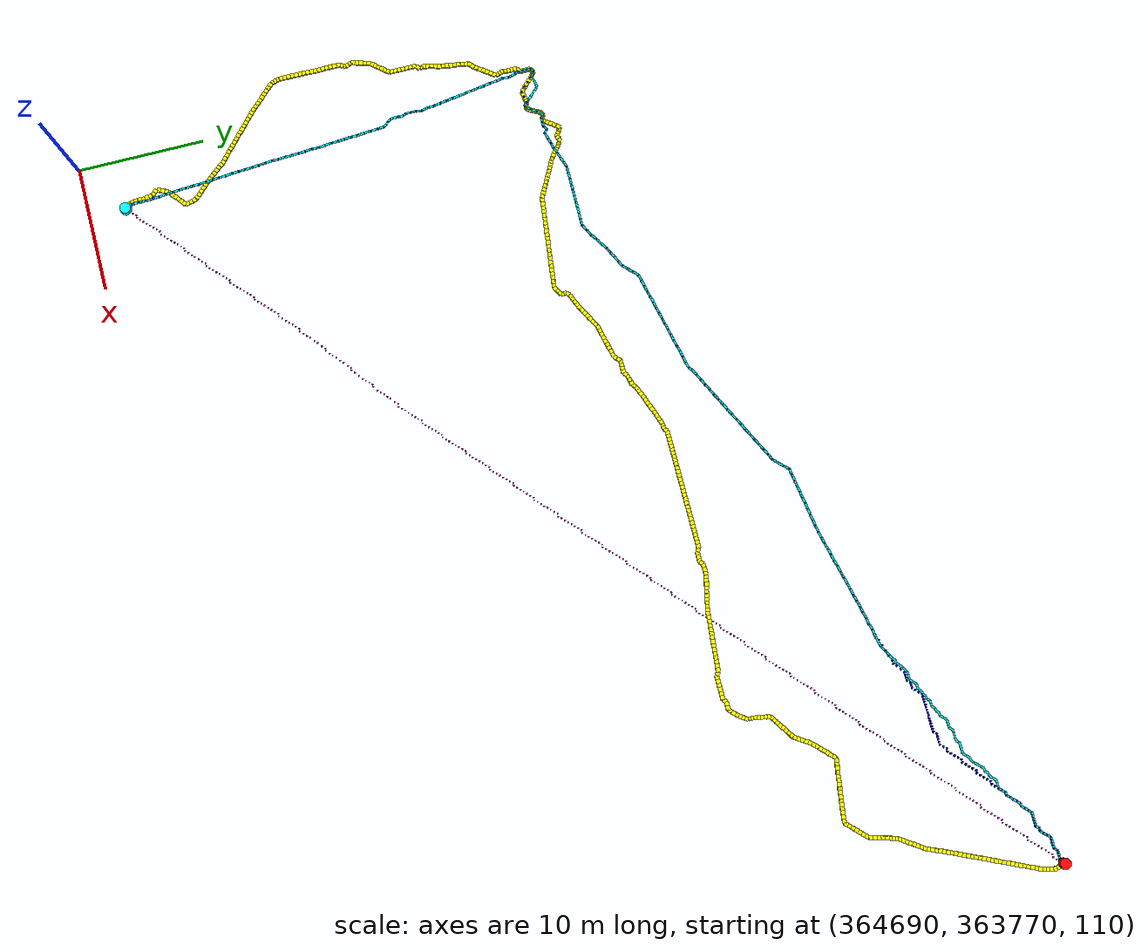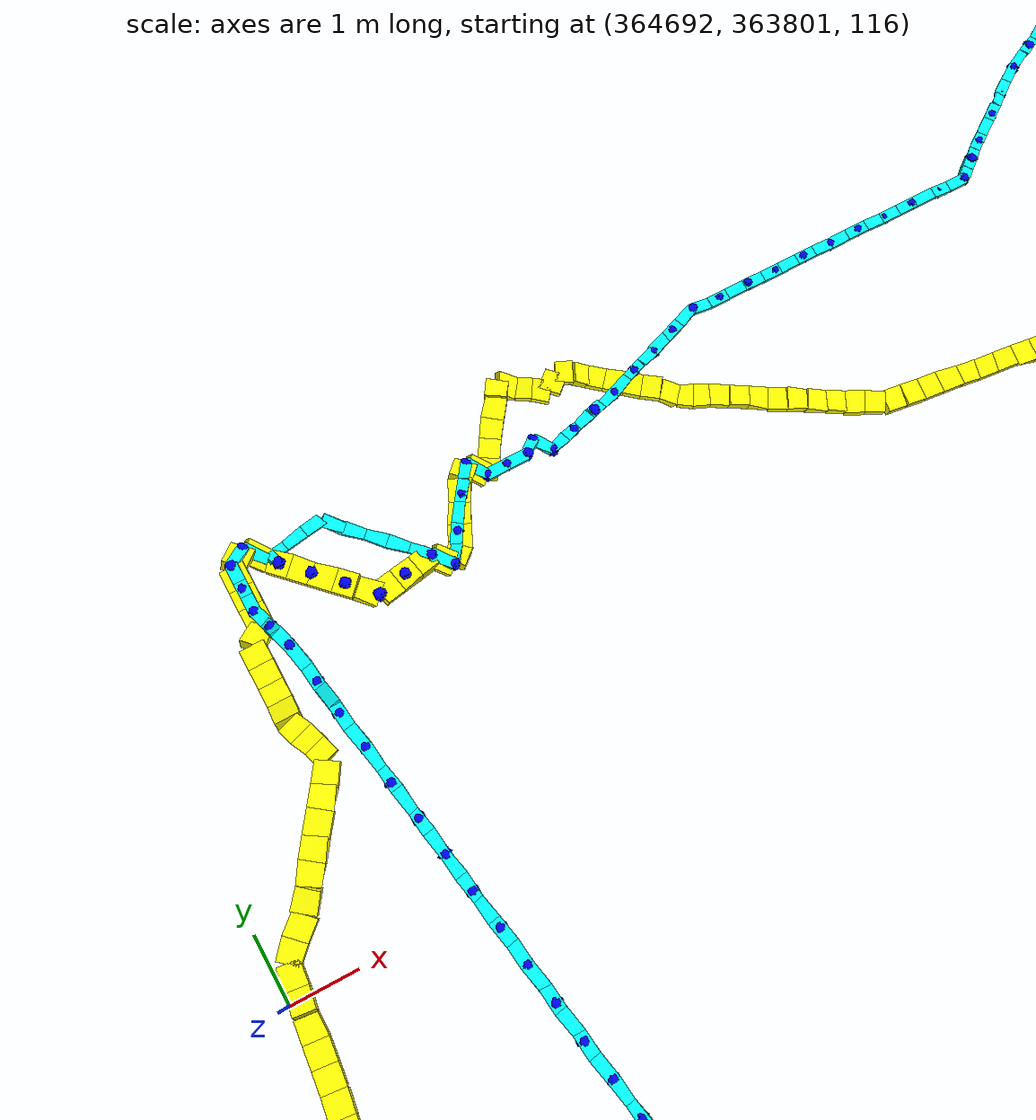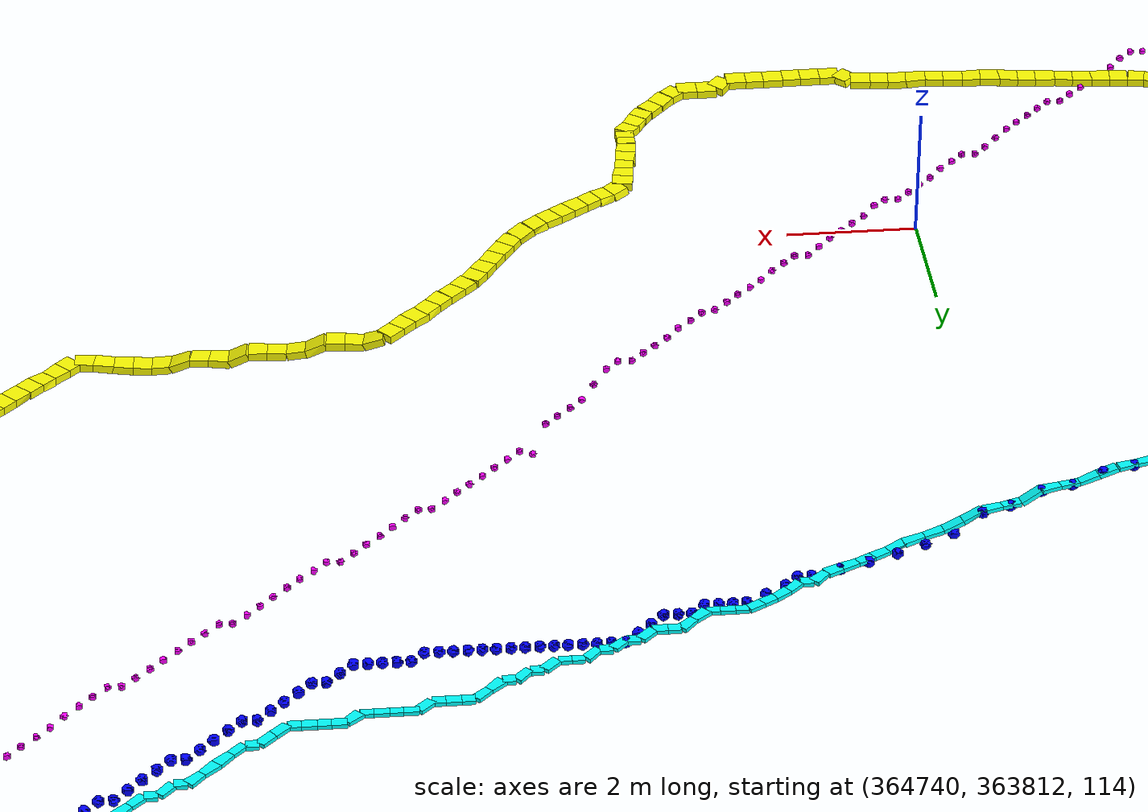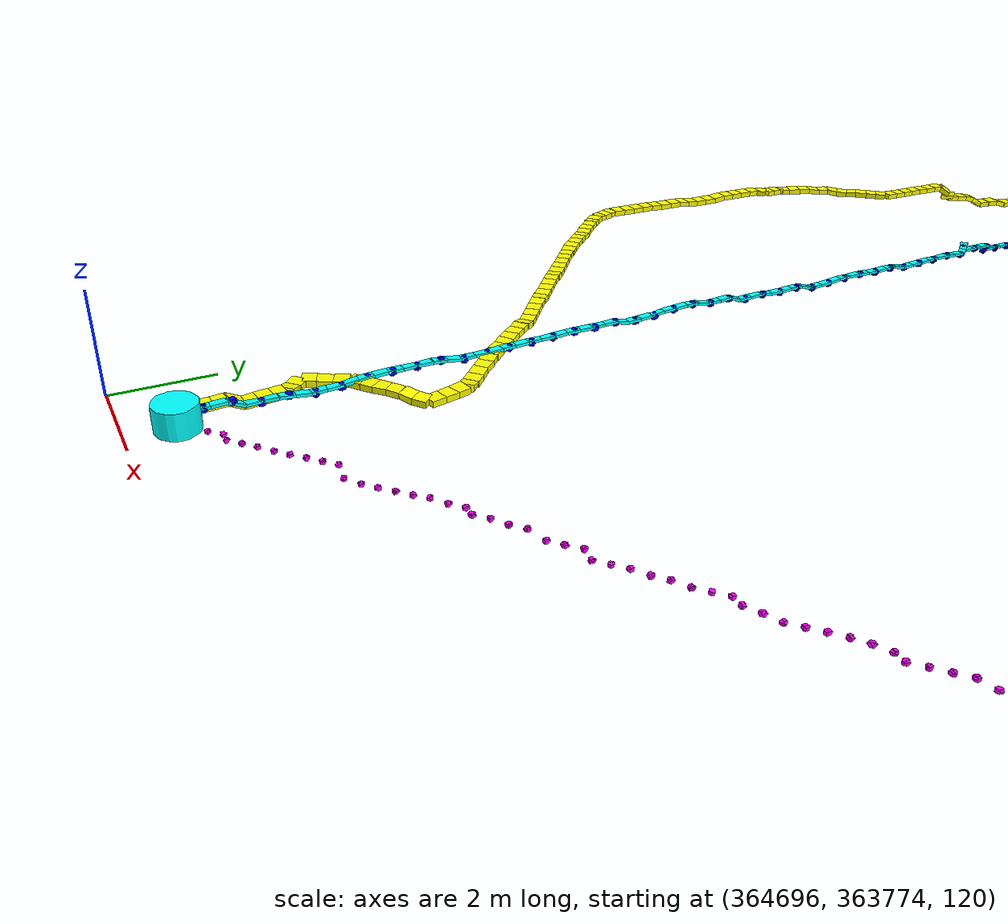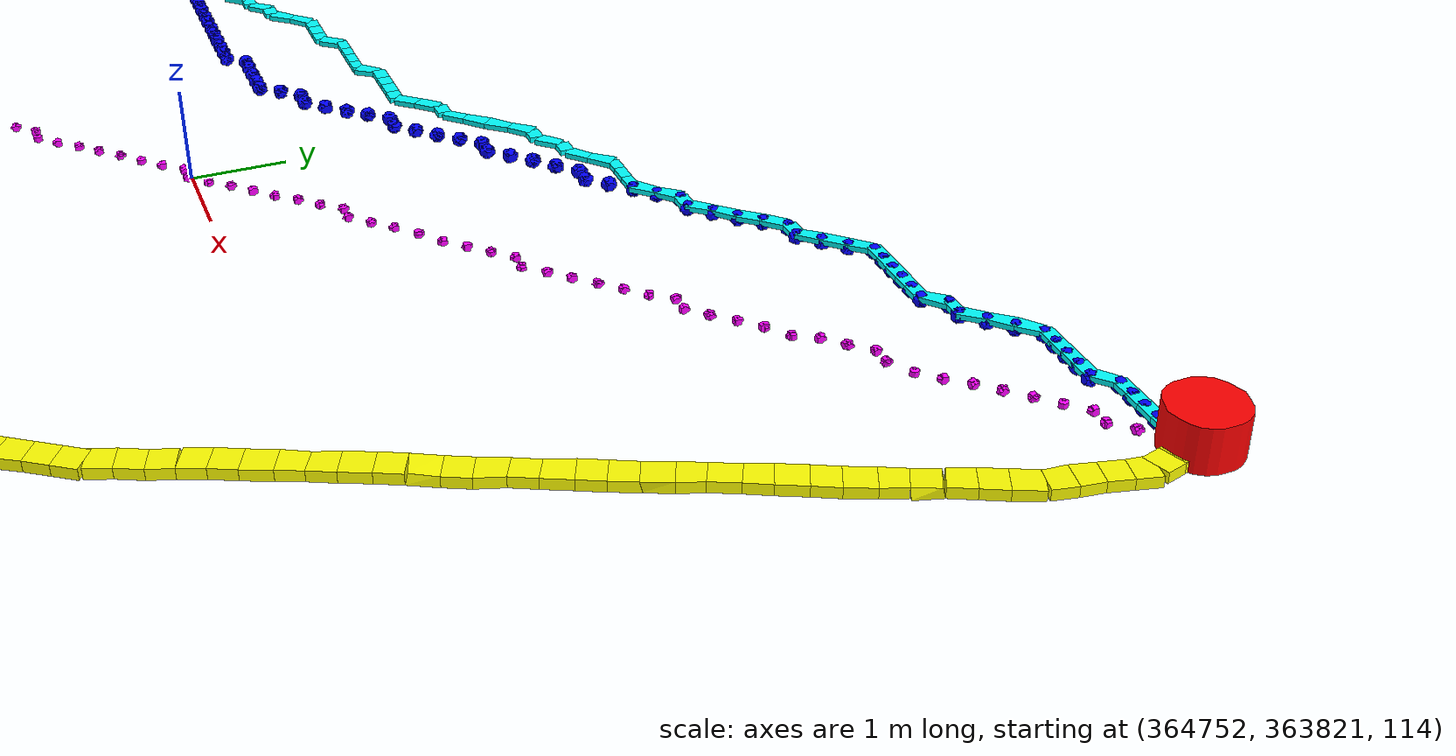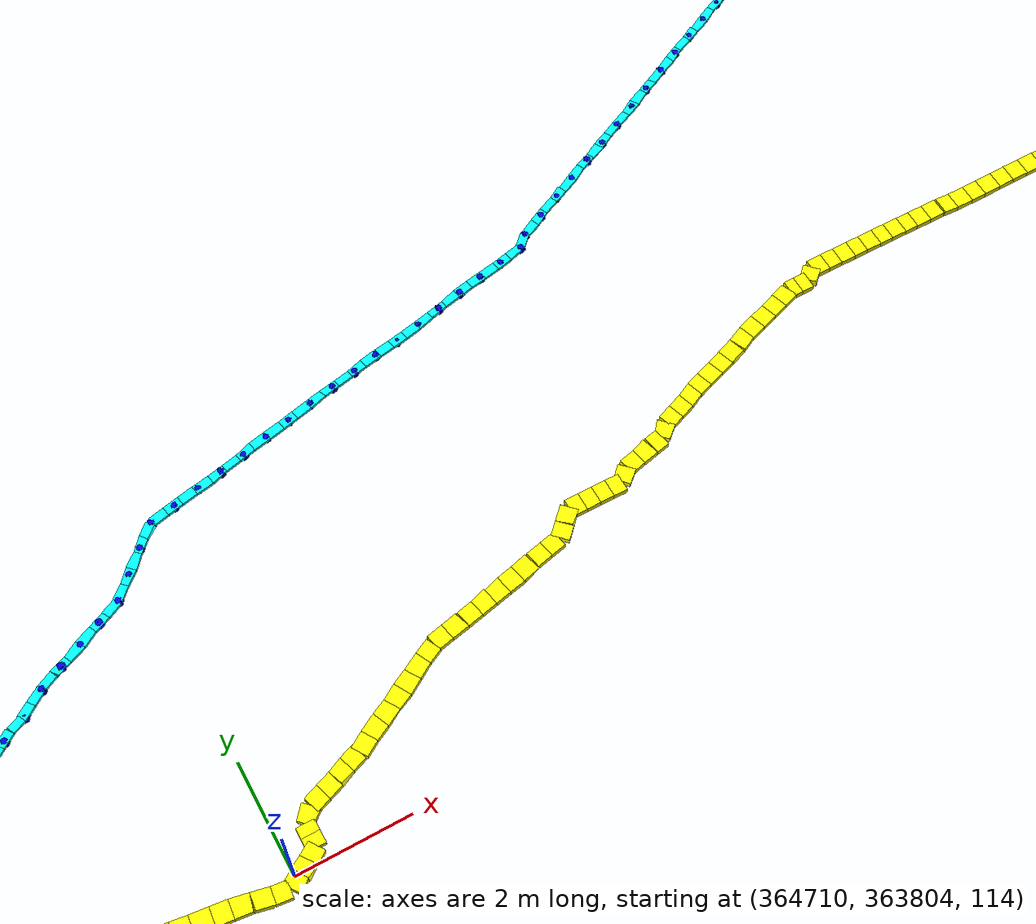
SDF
<sdf version="1.5">
 <world name="default">
  <include><uri>model://sun</uri></include>
  <scene><ambient>0.6 0.6 0.6 1</ambient><shadows>true</shadows><grid>false</grid></scene>
  <model name="start_marker">
   <static>true</static>
   <pose>364698.04 363774.84 120.45 0 0 0</pose>
   <link name="link">
    <visual name="visual">
     <geometry><cylinder><radius>0.4</radius><length>0.5</length></cylinder></geometry>
     <material><ambient>0 1 1 1</ambient><diffuse>0 1 1 1</diffuse><emissive>0 1 1 1</emissive></material>
    </visual>
   </link>
  </model>
  <model name="goal_marker">
   <static>true</static>
   <pose>364759.64 363828.44 113.82 0 0 0</pose>
   <link name="link">
    <visual name="visual">
     <geometry><cylinder><radius>0.4</radius><length>0.5</length></cylinder></geometry>
     <material><ambient>1 0 0 1</ambient><diffuse>1 0 0 1</diffuse><emissive>1 0 0 1</emissive></material>
    </visual>
   </link>
  </model>
  <model name="road_segment_0">
   <static>true</static>
   <pose>364697.93999999994 363774.94000000006 120.28499999991998 0 -0.17496904510691408 2.356194490192345</pose>
   <link name="link">
    <collision name="collision">
     <geometry><box><size>0.28722813231524835 0.3 0.12</size></box></geometry>
     <surface><friction><ode><mu>0.1</mu><mu2>0.1</mu2></ode></friction></surface>
    </collision>
    <visual name="visual">
     <geometry><box><size>0.28722813231524835 0.3 0.12</size></box></geometry>
     <material><ambient>1 1 0 1</ambient><diffuse>1 1 0 1</diffuse><emissive>1 1 0 1</emissive></material>
    </visual>
   </link>
  </model>
  <model name="road_segment_1">
   <static>true</static>
   <pose>364697.74 363775.14 120.30999999991997 0 -5.659366866794168e-10 2.356194490192345</pose>
   <link name="link">
    <collision name="collision">
     <geometry><box><size>0.2828427124087646 0.3 0.12</size></box></geometry>
     <surface><friction><ode><mu>0.1</mu><mu2>0.1</mu2></ode></friction></surface>
    </collision>
    <visual name="visual">
     <geometry><box><size>0.2828427124087646 0.3 0.12</size></box></geometry>
     <material><ambient>1 1 0 1</ambient><diffuse>1 1 0 1</diffuse><emissive>1 1 0 1</emissive></material>
    </visual>
   </link>
  </model>
  <model name="road_segment_2">
   <static>true</static>
   <pose>364697.62333333335 363775.3733333333 120.30999999999999 0 5.2879187787523526e-14 1.695151321314793</pose>
   <link name="link">
    <collision name="collision">
     <geometry><box><size>0.2687419249384718 0.3 0.12</size></box></geometry>
     <surface><friction><ode><mu>0.02</mu><mu2>0.02</mu2></ode></friction></surface>
    </collision>
    <visual name="visual">
     <geometry><box><size>0.2687419249384718 0.3 0.12</size></box></geometry>
     <material><ambient>1 1 0 1</ambient><diffuse>1 1 0 1</diffuse><emissive>1 1 0 1</emissive></material>
    </visual>
   </link>
  </model>
  <model name="road_segment_3">
   <static>true</static>
   <pose>364697.59 363775.64 120.30999999999999 0 -5.2879187787523526e-14 1.695151321314793</pose>
   <link name="link">
    <collision name="collision">
     <geometry><box><size>0.2687419249384718 0.3 0.12</size></box></geometry>
     <surface><friction><ode><mu>0.02</mu><mu2>0.02</mu2></ode></friction></surface>
    </collision>
    <visual name="visual">
     <geometry><box><size>0.2687419249384718 0.3 0.12</size></box></geometry>
     <material><ambient>1 1 0 1</ambient><diffuse>1 1 0 1</diffuse><emissive>1 1 0 1</emissive></material>
    </visual>
   </link>
  </model>
  <model name="road_segment_4">
   <static>true</static>
   <pose>364697.5566666667 363775.9066666667 120.23500000026193 0 0.5090836740391417 1.695151321287928</pose>
   <link name="link">
    <collision name="collision">
     <geometry><box><size>0.3077697550012352 0.3 0.12</size></box></geometry>
     <surface><friction><ode><mu>0.02</mu><mu2>0.02</mu2></ode></friction></surface>
    </collision>
    <visual name="visual">
     <geometry><box><size>0.3077697550012352 0.3 0.12</size></box></geometry>
     <material><ambient>1 1 0 1</ambient><diffuse>1 1 0 1</diffuse><emissive>1 1 0 1</emissive></material>
    </visual>
   </link>
  </model>
  <model name="road_segment_5">
   <static>true</static>
   <pose>364697.5233333333 363776.17333333334 120.16000000026192 0 1.9493912577346843e-09 1.6951513215297136</pose>
   <link name="link">
    <collision name="collision">
     <geometry><box><size>0.2687419249456916 0.3 0.12</size></box></geometry>
     <surface><friction><ode><mu>0.02</mu><mu2>0.02</mu2></ode></friction></surface>
    </collision>
    <visual name="visual">
     <geometry><box><size>0.2687419249456916 0.3 0.12</size></box></geometry>
     <material><ambient>1 1 0 1</ambient><diffuse>1 1 0 1</diffuse><emissive>1 1 0 1</emissive></material>
    </visual>
   </link>
  </model>
  <model name="road_segment_6">
   <static>true</static>
   <pose>364697.49 363776.44000000006 120.15999999999998 0 -0.0 1.695151321314793</pose>
   <link name="link">
    <collision name="collision">
     <geometry><box><size>0.2687419249384718 0.3 0.12</size></box></geometry>
     <surface><friction><ode><mu>0.02</mu><mu2>0.02</mu2></ode></friction></surface>
    </collision>
    <visual name="visual">
     <geometry><box><size>0.2687419249384718 0.3 0.12</size></box></geometry>
     <material><ambient>1 1 0 1</ambient><diffuse>1 1 0 1</diffuse><emissive>1 1 0 1</emissive></material>
    </visual>
   </link>
  </model>
  <model name="road_segment_7">
   <static>true</static>
   <pose>364697.45666666667 363776.70666666667 120.1600000000873 0 -6.498323387208766e-10 1.695151321314793</pose>
   <link name="link">
    <collision name="collision">
     <geometry><box><size>0.2687419249384718 0.3 0.12</size></box></geometry>
     <surface><friction><ode><mu>0.02</mu><mu2>0.02</mu2></ode></friction></surface>
    </collision>
    <visual name="visual">
     <geometry><box><size>0.2687419249384718 0.3 0.12</size></box></geometry>
     <material><ambient>1 1 0 1</ambient><diffuse>1 1 0 1</diffuse><emissive>1 1 0 1</emissive></material>
    </visual>
   </link>
  </model>
  <model name="road_segment_8">
   <static>true</static>
   <pose>364697.33999999997 363776.94000000006 120.1300000002954 0 0.2090332982054584 2.356194490192345</pose>
   <link name="link">
    <collision name="collision">
     <geometry><box><size>0.28913664586199855 0.3 0.12</size></box></geometry>
     <surface><friction><ode><mu>0.1</mu><mu2>0.1</mu2></ode></friction></surface>
    </collision>
    <visual name="visual">
     <geometry><box><size>0.28913664586199855 0.3 0.12</size></box></geometry>
     <material><ambient>1 1 0 1</ambient><diffuse>1 1 0 1</diffuse><emissive>1 1 0 1</emissive></material>
    </visual>
   </link>
  </model>
  <model name="road_segment_9">
   <static>true</static>
   <pose>364697.14 363777.14 120.10000000020808 0 1.4714152879688886e-09 2.356194490337864</pose>
   <link name="link">
    <collision name="collision">
     <geometry><box><size>0.2828427124499236 0.3 0.12</size></box></geometry>
     <surface><friction><ode><mu>0.1</mu><mu2>0.1</mu2></ode></friction></surface>
    </collision>
    <visual name="visual">
     <geometry><box><size>0.2828427124499236 0.3 0.12</size></box></geometry>
     <material><ambient>1 1 0 1</ambient><diffuse>1 1 0 1</diffuse><emissive>1 1 0 1</emissive></material>
    </visual>
   </link>
  </model>
  <model name="road_segment_10">
   <static>true</static>
   <pose>364697.1066666667 363777.3733333333 120.10000000000001 0 -4.766465574096042e-14 1.107148717706779</pose>
   <link name="link">
    <collision name="collision">
     <geometry><box><size>0.29814239700864903 0.3 0.12</size></box></geometry>
     <surface><friction><ode><mu>0.02</mu><mu2>0.02</mu2></ode></friction></surface>
    </collision>
    <visual name="visual">
     <geometry><box><size>0.29814239700864903 0.3 0.12</size></box></geometry>
     <material><ambient>1 1 0 1</ambient><diffuse>1 1 0 1</diffuse><emissive>1 1 0 1</emissive></material>
    </visual>
   </link>
  </model>
  <model name="road_segment_11">
   <static>true</static>
   <pose>364697.24 363777.64 120.09500000005384 0 0.03352844990459563 1.107148717881402</pose>
   <link name="link">
    <collision name="collision">
     <geometry><box><size>0.29831005493678464 0.3 0.12</size></box></geometry>
     <surface><friction><ode><mu>0.02</mu><mu2>0.02</mu2></ode></friction></surface>
    </collision>
    <visual name="visual">
     <geometry><box><size>0.29831005493678464 0.3 0.12</size></box></geometry>
     <material><ambient>1 1 0 1</ambient><diffuse>1 1 0 1</diffuse><emissive>1 1 0 1</emissive></material>
    </visual>
   </link>
  </model>
  <model name="road_segment_12">
   <static>true</static>
   <pose>364697.3733333333 363777.9066666666 120.09999999987922 0 -0.06698168555039336 1.107148717706779</pose>
   <link name="link">
    <collision name="collision">
     <geometry><box><size>0.2988124643916078 0.3 0.12</size></box></geometry>
     <surface><friction><ode><mu>0.02</mu><mu2>0.02</mu2></ode></friction></surface>
    </collision>
    <visual name="visual">
     <geometry><box><size>0.2988124643916078 0.3 0.12</size></box></geometry>
     <material><ambient>1 1 0 1</ambient><diffuse>1 1 0 1</diffuse><emissive>1 1 0 1</emissive></material>
    </visual>
   </link>
  </model>
  <model name="road_segment_13">
   <static>true</static>
   <pose>364697.54000000004 363778.1233333333 120.10999999982538 0 -1.3414909123693356e-09 0.6947382762253299</pose>
   <link name="link">
    <collision name="collision">
     <geometry><box><size>0.26034165588491964 0.3 0.12</size></box></geometry>
     <surface><friction><ode><mu>0.02</mu><mu2>0.02</mu2></ode></friction></surface>
    </collision>
    <visual name="visual">
     <geometry><box><size>0.26034165588491964 0.3 0.12</size></box></geometry>
     <material><ambient>1 1 0 1</ambient><diffuse>1 1 0 1</diffuse><emissive>1 1 0 1</emissive></material>
    </visual>
   </link>
  </model>
  <model name="road_segment_14">
   <static>true</static>
   <pose>364697.74 363778.29 120.11 0 -0.0 0.6947382760535696</pose>
   <link name="link">
    <collision name="collision">
     <geometry><box><size>0.260341655847656 0.3 0.12</size></box></geometry>
     <surface><friction><ode><mu>0.02</mu><mu2>0.02</mu2></ode></friction></surface>
    </collision>
    <visual name="visual">
     <geometry><box><size>0.260341655847656 0.3 0.12</size></box></geometry>
     <material><ambient>1 1 0 1</ambient><diffuse>1 1 0 1</diffuse><emissive>1 1 0 1</emissive></material>
    </visual>
   </link>
  </model>
  <model name="road_segment_15">
   <static>true</static>
   <pose>364697.94000000006 363778.45666666667 120.11 0 -0.0 0.6947382762253299</pose>
   <link name="link">
    <collision name="collision">
     <geometry><box><size>0.26034165588491964 0.3 0.12</size></box></geometry>
     <surface><friction><ode><mu>0.02</mu><mu2>0.02</mu2></ode></friction></surface>
    </collision>
    <visual name="visual">
     <geometry><box><size>0.26034165588491964 0.3 0.12</size></box></geometry>
     <material><ambient>1 1 0 1</ambient><diffuse>1 1 0 1</diffuse><emissive>1 1 0 1</emissive></material>
    </visual>
   </link>
  </model>
  <model name="road_segment_16">
   <static>true</static>
   <pose>364698.14 363778.6233333333 120.11 0 -0.0 0.6947382763684635</pose>
   <link name="link">
    <collision name="collision">
     <geometry><box><size>0.26034165584020325 0.3 0.12</size></box></geometry>
     <surface><friction><ode><mu>0.02</mu><mu2>0.02</mu2></ode></friction></surface>
    </collision>
    <visual name="visual">
     <geometry><box><size>0.26034165584020325 0.3 0.12</size></box></geometry>
     <material><ambient>1 1 0 1</ambient><diffuse>1 1 0 1</diffuse><emissive>1 1 0 1</emissive></material>
    </visual>
   </link>
  </model>
  <model name="road_segment_17">
   <static>true</static>
   <pose>364698.33999999997 363778.79 120.08416666678163 0 0.19591162356437838 0.6947382760535696</pose>
   <link name="link">
    <collision name="collision">
     <geometry><box><size>0.2654189559737308 0.3 0.12</size></box></geometry>
     <surface><friction><ode><mu>0.1</mu><mu2>0.1</mu2></ode></friction></surface>
    </collision>
    <visual name="visual">
     <geometry><box><size>0.2654189559737308 0.3 0.12</size></box></geometry>
     <material><ambient>1 1 0 1</ambient><diffuse>1 1 0 1</diffuse><emissive>1 1 0 1</emissive></material>
    </visual>
   </link>
  </model>
  <model name="road_segment_18">
   <static>true</static>
   <pose>364698.54000000004 363778.95666666667 120.0541666668049 0 0.03199829528916069 0.6947382762253299</pose>
   <link name="link">
    <collision name="collision">
     <geometry><box><size>0.2604749934953493 0.3 0.12</size></box></geometry>
     <surface><friction><ode><mu>0.1</mu><mu2>0.1</mu2></ode></friction></surface>
    </collision>
    <visual name="visual">
     <geometry><box><size>0.2604749934953493 0.3 0.12</size></box></geometry>
     <material><ambient>1 1 0 1</ambient><diffuse>1 1 0 1</diffuse><emissive>1 1 0 1</emissive></material>
    </visual>
   </link>
  </model>
  <model name="road_segment_19">
   <static>true</static>
   <pose>364698.6066666667 363779.17333333334 120.05000000002327 0 1.6941951697884164e-10 1.815774989870401</pose>
   <link name="link">
    <collision name="collision">
     <geometry><box><size>0.2748737083669814 0.3 0.12</size></box></geometry>
     <surface><friction><ode><mu>0.02</mu><mu2>0.02</mu2></ode></friction></surface>
    </collision>
    <visual name="visual">
     <geometry><box><size>0.2748737083669814 0.3 0.12</size></box></geometry>
     <material><ambient>1 1 0 1</ambient><diffuse>1 1 0 1</diffuse><emissive>1 1 0 1</emissive></material>
    </visual>
   </link>
  </model>
  <model name="road_segment_20">
   <static>true</static>
   <pose>364698.54000000004 363779.44 120.05 0 -0.0 1.8157749900244802</pose>
   <link name="link">
    <collision name="collision">
     <geometry><box><size>0.2748737084375686 0.3 0.12</size></box></geometry>
     <surface><friction><ode><mu>0.02</mu><mu2>0.02</mu2></ode></friction></surface>
    </collision>
    <visual name="visual">
     <geometry><box><size>0.2748737084375686 0.3 0.12</size></box></geometry>
     <material><ambient>1 1 0 1</ambient><diffuse>1 1 0 1</diffuse><emissive>1 1 0 1</emissive></material>
    </visual>
   </link>
  </model>
  <model name="road_segment_21">
   <static>true</static>
   <pose>364698.4733333333 363779.70666666667 120.05000000007566 0 -5.505488057087839e-10 1.815774989870401</pose>
   <link name="link">
    <collision name="collision">
     <geometry><box><size>0.2748737083669814 0.3 0.12</size></box></geometry>
     <surface><friction><ode><mu>0.02</mu><mu2>0.02</mu2></ode></friction></surface>
    </collision>
    <visual name="visual">
     <geometry><box><size>0.2748737083669814 0.3 0.12</size></box></geometry>
     <material><ambient>1 1 0 1</ambient><diffuse>1 1 0 1</diffuse><emissive>1 1 0 1</emissive></material>
    </visual>
   </link>
  </model>
  <model name="road_segment_22">
   <static>true</static>
   <pose>364698.33999999997 363779.94000000006 120.0250000002852 0 0.17496904473771055 2.356194490192345</pose>
   <link name="link">
    <collision name="collision">
     <geometry><box><size>0.28722813229650196 0.3 0.12</size></box></geometry>
     <surface><friction><ode><mu>0.2</mu><mu2>0.2</mu2></ode></friction></surface>
    </collision>
    <visual name="visual">
     <geometry><box><size>0.28722813229650196 0.3 0.12</size></box></geometry>
     <material><ambient>1 1 0 1</ambient><diffuse>1 1 0 1</diffuse><emissive>1 1 0 1</emissive></material>
    </visual>
   </link>
  </model>
  <model name="road_segment_23">
   <static>true</static>
   <pose>364698.14 363780.14 120.00000000020954 0 1.4817150944987535e-09 2.356194490337864</pose>
   <link name="link">
    <collision name="collision">
     <geometry><box><size>0.2828427124499236 0.3 0.12</size></box></geometry>
     <surface><friction><ode><mu>0.2</mu><mu2>0.2</mu2></ode></friction></surface>
    </collision>
    <visual name="visual">
     <geometry><box><size>0.2828427124499236 0.3 0.12</size></box></geometry>
     <material><ambient>1 1 0 1</ambient><diffuse>1 1 0 1</diffuse><emissive>1 1 0 1</emissive></material>
    </visual>
   </link>
  </model>
  <model name="road_segment_24">
   <static>true</static>
   <pose>364697.93999999994 363780.33999999997 120.0 0 -0.0 2.356194490192345</pose>
   <link name="link">
    <collision name="collision">
     <geometry><box><size>0.2828427124910826 0.3 0.12</size></box></geometry>
     <surface><friction><ode><mu>0.2</mu><mu2>0.2</mu2></ode></friction></surface>
    </collision>
    <visual name="visual">
     <geometry><box><size>0.2828427124910826 0.3 0.12</size></box></geometry>
     <material><ambient>1 1 0 1</ambient><diffuse>1 1 0 1</diffuse><emissive>1 1 0 1</emissive></material>
    </visual>
   </link>
  </model>
  <model name="road_segment_25">
   <static>true</static>
   <pose>364697.74 363780.54000000004 120.0 0 -0.0 2.3561944900468257</pose>
   <link name="link">
    <collision name="collision">
     <geometry><box><size>0.2828427124499236 0.3 0.12</size></box></geometry>
     <surface><friction><ode><mu>0.02</mu><mu2>0.02</mu2></ode></friction></surface>
    </collision>
    <visual name="visual">
     <geometry><box><size>0.2828427124499236 0.3 0.12</size></box></geometry>
     <material><ambient>1 1 0 1</ambient><diffuse>1 1 0 1</diffuse><emissive>1 1 0 1</emissive></material>
    </visual>
   </link>
  </model>
  <model name="road_segment_26">
   <static>true</static>
   <pose>364697.54000000004 363780.74 119.99999999996508 0 2.469441419233452e-10 2.356194490337864</pose>
   <link name="link">
    <collision name="collision">
     <geometry><box><size>0.2828427124499236 0.3 0.12</size></box></geometry>
     <surface><friction><ode><mu>0.02</mu><mu2>0.02</mu2></ode></friction></surface>
    </collision>
    <visual name="visual">
     <geometry><box><size>0.2828427124499236 0.3 0.12</size></box></geometry>
     <material><ambient>1 1 0 1</ambient><diffuse>1 1 0 1</diffuse><emissive>1 1 0 1</emissive></material>
    </visual>
   </link>
  </model>
  <model name="road_segment_27">
   <static>true</static>
   <pose>364697.33999999997 363780.93999999994 119.98999999996508 0 0.07059317903422238 2.356194490192345</pose>
   <link name="link">
    <collision name="collision">
     <geometry><box><size>0.2835489375866522 0.3 0.12</size></box></geometry>
     <surface><friction><ode><mu>0.02</mu><mu2>0.02</mu2></ode></friction></surface>
    </collision>
    <visual name="visual">
     <geometry><box><size>0.2835489375866522 0.3 0.12</size></box></geometry>
     <material><ambient>1 1 0 1</ambient><diffuse>1 1 0 1</diffuse><emissive>1 1 0 1</emissive></material>
    </visual>
   </link>
  </model>
  <model name="road_segment_28">
   <static>true</static>
   <pose>364697.1566666666 363781.14 119.98 0 -0.0 2.2655346030202264</pose>
   <link name="link">
    <collision name="collision">
     <geometry><box><size>0.26034165588491964 0.3 0.12</size></box></geometry>
     <surface><friction><ode><mu>0.02</mu><mu2>0.02</mu2></ode></friction></surface>
    </collision>
    <visual name="visual">
     <geometry><box><size>0.26034165588491964 0.3 0.12</size></box></geometry>
     <material><ambient>1 1 0 1</ambient><diffuse>1 1 0 1</diffuse><emissive>1 1 0 1</emissive></material>
    </visual>
   </link>
  </model>
  <model name="road_segment_29">
   <static>true</static>
   <pose>364696.99 363781.33999999997 119.98 0 -0.0 2.2655346028484664</pose>
   <link name="link">
    <collision name="collision">
     <geometry><box><size>0.260341655847656 0.3 0.12</size></box></geometry>
     <surface><friction><ode><mu>0.02</mu><mu2>0.02</mu2></ode></friction></surface>
    </collision>
    <visual name="visual">
     <geometry><box><size>0.260341655847656 0.3 0.12</size></box></geometry>
     <material><ambient>1 1 0 1</ambient><diffuse>1 1 0 1</diffuse><emissive>1 1 0 1</emissive></material>
    </visual>
   </link>
  </model>
  <model name="road_segment_30">
   <static>true</static>
   <pose>364696.82333333336 363781.54000000004 119.98 0 -0.0 2.2655346030202264</pose>
   <link name="link">
    <collision name="collision">
     <geometry><box><size>0.26034165588491964 0.3 0.12</size></box></geometry>
     <surface><friction><ode><mu>0.02</mu><mu2>0.02</mu2></ode></friction></surface>
    </collision>
    <visual name="visual">
     <geometry><box><size>0.26034165588491964 0.3 0.12</size></box></geometry>
     <material><ambient>1 1 0 1</ambient><diffuse>1 1 0 1</diffuse><emissive>1 1 0 1</emissive></material>
    </visual>
   </link>
  </model>
  <model name="road_segment_31">
   <static>true</static>
   <pose>364696.6566666666 363781.74 119.98 0 -0.0 2.2655346031633603</pose>
   <link name="link">
    <collision name="collision">
     <geometry><box><size>0.26034165584020325 0.3 0.12</size></box></geometry>
     <surface><friction><ode><mu>0.2</mu><mu2>0.2</mu2></ode></friction></surface>
    </collision>
    <visual name="visual">
     <geometry><box><size>0.26034165584020325 0.3 0.12</size></box></geometry>
     <material><ambient>1 1 0 1</ambient><diffuse>1 1 0 1</diffuse><emissive>1 1 0 1</emissive></material>
    </visual>
   </link>
  </model>
  <model name="road_segment_32">
   <static>true</static>
   <pose>364696.49 363781.93999999994 119.97499999990542 0 0.03839219072589787 2.2655346028484664</pose>
   <link name="link">
    <collision name="collision">
     <geometry><box><size>0.26053364038696225 0.3 0.12</size></box></geometry>
     <surface><friction><ode><mu>0.2</mu><mu2>0.2</mu2></ode></friction></surface>
    </collision>
    <visual name="visual">
     <geometry><box><size>0.26053364038696225 0.3 0.12</size></box></geometry>
     <material><ambient>1 1 0 1</ambient><diffuse>1 1 0 1</diffuse><emissive>1 1 0 1</emissive></material>
    </visual>
   </link>
  </model>
  <model name="road_segment_33">
   <static>true</static>
   <pose>364696.32333333336 363782.14 119.94499999990542 0 0.1897449038507924 2.2655346030202264</pose>
   <link name="link">
    <collision name="collision">
     <geometry><box><size>0.26509956199508167 0.3 0.12</size></box></geometry>
     <surface><friction><ode><mu>0.02</mu><mu2>0.02</mu2></ode></friction></surface>
    </collision>
    <visual name="visual">
     <geometry><box><size>0.26509956199508167 0.3 0.12</size></box></geometry>
     <material><ambient>1 1 0 1</ambient><diffuse>1 1 0 1</diffuse><emissive>1 1 0 1</emissive></material>
    </visual>
   </link>
  </model>
  <model name="road_segment_34">
   <static>true</static>
   <pose>364696.1333333333 363782.3333333333 119.92 0 -0.0 2.4227626539874856</pose>
   <link name="link">
    <collision name="collision">
     <geometry><box><size>0.2834705549818721 0.3 0.12</size></box></geometry>
     <surface><friction><ode><mu>0.02</mu><mu2>0.02</mu2></ode></friction></surface>
    </collision>
    <visual name="visual">
     <geometry><box><size>0.2834705549818721 0.3 0.12</size></box></geometry>
     <material><ambient>1 1 0 1</ambient><diffuse>1 1 0 1</diffuse><emissive>1 1 0 1</emissive></material>
    </visual>
   </link>
  </model>
  <model name="road_segment_35">
   <static>true</static>
   <pose>364695.92 363782.52 119.92 0 -0.0 2.4227626539681686</pose>
   <link name="link">
    <collision name="collision">
     <geometry><box><size>0.28347055506400787 0.3 0.12</size></box></geometry>
     <surface><friction><ode><mu>0.02</mu><mu2>0.02</mu2></ode></friction></surface>
    </collision>
    <visual name="visual">
     <geometry><box><size>0.28347055506400787 0.3 0.12</size></box></geometry>
     <material><ambient>1 1 0 1</ambient><diffuse>1 1 0 1</diffuse><emissive>1 1 0 1</emissive></material>
    </visual>
   </link>
  </model>
  <model name="road_segment_36">
   <static>true</static>
   <pose>364695.70666666667 363782.70666666667 119.92 0 -0.0 2.4227626539874856</pose>
   <link name="link">
    <collision name="collision">
     <geometry><box><size>0.2834705549818721 0.3 0.12</size></box></geometry>
     <surface><friction><ode><mu>0.02</mu><mu2>0.02</mu2></ode></friction></surface>
    </collision>
    <visual name="visual">
     <geometry><box><size>0.2834705549818721 0.3 0.12</size></box></geometry>
     <material><ambient>1 1 0 1</ambient><diffuse>1 1 0 1</diffuse><emissive>1 1 0 1</emissive></material>
    </visual>
   </link>
  </model>
  <model name="road_segment_37">
   <static>true</static>
   <pose>364695.4933333333 363782.8933333333 119.92646666657551 0 -0.045593342754924174 2.4227626539874856</pose>
   <link name="link">
    <collision name="collision">
     <geometry><box><size>0.2837654430125804 0.3 0.12</size></box></geometry>
     <surface><friction><ode><mu>0.02</mu><mu2>0.02</mu2></ode></friction></surface>
    </collision>
    <visual name="visual">
     <geometry><box><size>0.2837654430125804 0.3 0.12</size></box></geometry>
     <material><ambient>1 1 0 1</ambient><diffuse>1 1 0 1</diffuse><emissive>1 1 0 1</emissive></material>
    </visual>
   </link>
  </model>
  <model name="road_segment_38">
   <static>true</static>
   <pose>364695.28 363783.07999999996 119.91646666657552 0 0.11566050803793583 2.422762653832952</pose>
   <link name="link">
    <collision name="collision">
     <geometry><box><size>0.28537722403145044 0.3 0.12</size></box></geometry>
     <surface><friction><ode><mu>0.02</mu><mu2>0.02</mu2></ode></friction></surface>
    </collision>
    <visual name="visual">
     <geometry><box><size>0.28537722403145044 0.3 0.12</size></box></geometry>
     <material><ambient>1 1 0 1</ambient><diffuse>1 1 0 1</diffuse><emissive>1 1 0 1</emissive></material>
    </visual>
   </link>
  </model>
  <model name="road_segment_39">
   <static>true</static>
   <pose>364695.06666666665 363783.26666666666 119.90000000000002 0 -0.0 2.4227626541227023</pose>
   <link name="link">
    <collision name="collision">
     <geometry><box><size>0.28347055502567786 0.3 0.12</size></box></geometry>
     <surface><friction><ode><mu>0.02</mu><mu2>0.02</mu2></ode></friction></surface>
    </collision>
    <visual name="visual">
     <geometry><box><size>0.28347055502567786 0.3 0.12</size></box></geometry>
     <material><ambient>1 1 0 1</ambient><diffuse>1 1 0 1</diffuse><emissive>1 1 0 1</emissive></material>
    </visual>
   </link>
  </model>
  <model name="road_segment_40">
   <static>true</static>
   <pose>364694.8533333333 363783.4533333333 119.90000000000002 0 5.013167845990489e-14 2.4227626539874856</pose>
   <link name="link">
    <collision name="collision">
     <geometry><box><size>0.2834705549818721 0.3 0.12</size></box></geometry>
     <surface><friction><ode><mu>0.02</mu><mu2>0.02</mu2></ode></friction></surface>
    </collision>
    <visual name="visual">
     <geometry><box><size>0.2834705549818721 0.3 0.12</size></box></geometry>
     <material><ambient>1 1 0 1</ambient><diffuse>1 1 0 1</diffuse><emissive>1 1 0 1</emissive></material>
    </visual>
   </link>
  </model>
  <model name="road_segment_41">
   <static>true</static>
   <pose>364694.64 363783.64 119.9 0 -0.0 2.422762653832952</pose>
   <link name="link">
    <collision name="collision">
     <geometry><box><size>0.28347055502020213 0.3 0.12</size></box></geometry>
     <surface><friction><ode><mu>0.02</mu><mu2>0.02</mu2></ode></friction></surface>
    </collision>
    <visual name="visual">
     <geometry><box><size>0.28347055502020213 0.3 0.12</size></box></geometry>
     <material><ambient>1 1 0 1</ambient><diffuse>1 1 0 1</diffuse><emissive>1 1 0 1</emissive></material>
    </visual>
   </link>
  </model>
  <model name="road_segment_42">
   <static>true</static>
   <pose>364694.42666666664 363783.82666666666 119.89480000004797 0 0.036671665863208906 2.4227626539874856</pose>
   <link name="link">
    <collision name="collision">
     <geometry><box><size>0.28366126901594296 0.3 0.12</size></box></geometry>
     <surface><friction><ode><mu>0.02</mu><mu2>0.02</mu2></ode></friction></surface>
    </collision>
    <visual name="visual">
     <geometry><box><size>0.28366126901594296 0.3 0.12</size></box></geometry>
     <material><ambient>1 1 0 1</ambient><diffuse>1 1 0 1</diffuse><emissive>1 1 0 1</emissive></material>
    </visual>
   </link>
  </model>
  <model name="road_segment_43">
   <static>true</static>
   <pose>364694.2133333333 363784.0133333333 119.86980000004796 0 0.13879880210410134 2.4227626541227023</pose>
   <link name="link">
    <collision name="collision">
     <geometry><box><size>0.28622319188732037 0.3 0.12</size></box></geometry>
     <surface><friction><ode><mu>0.02</mu><mu2>0.02</mu2></ode></friction></surface>
    </collision>
    <visual name="visual">
     <geometry><box><size>0.28622319188732037 0.3 0.12</size></box></geometry>
     <material><ambient>1 1 0 1</ambient><diffuse>1 1 0 1</diffuse><emissive>1 1 0 1</emissive></material>
    </visual>
   </link>
  </model>
  <model name="road_segment_44">
   <static>true</static>
   <pose>364694.0 363784.19999999995 119.84999999999998 0 -0.0 2.422762653832952</pose>
   <link name="link">
    <collision name="collision">
     <geometry><box><size>0.28347055502020213 0.3 0.12</size></box></geometry>
     <surface><friction><ode><mu>0.02</mu><mu2>0.02</mu2></ode></friction></surface>
    </collision>
    <visual name="visual">
     <geometry><box><size>0.28347055502020213 0.3 0.12</size></box></geometry>
     <material><ambient>1 1 0 1</ambient><diffuse>1 1 0 1</diffuse><emissive>1 1 0 1</emissive></material>
    </visual>
   </link>
  </model>
  <model name="road_segment_45">
   <static>true</static>
   <pose>364693.7866666666 363784.38666666666 119.84999999999998 0 -5.013167845990489e-14 2.4227626539874856</pose>
   <link name="link">
    <collision name="collision">
     <geometry><box><size>0.2834705549818721 0.3 0.12</size></box></geometry>
     <surface><friction><ode><mu>0.02</mu><mu2>0.02</mu2></ode></friction></surface>
    </collision>
    <visual name="visual">
     <geometry><box><size>0.2834705549818721 0.3 0.12</size></box></geometry>
     <material><ambient>1 1 0 1</ambient><diffuse>1 1 0 1</diffuse><emissive>1 1 0 1</emissive></material>
    </visual>
   </link>
  </model>
  <model name="road_segment_46">
   <static>true</static>
   <pose>364693.57333333336 363784.5733333333 119.84999999999998 0 5.013167845990489e-14 2.4227626539874856</pose>
   <link name="link">
    <collision name="collision">
     <geometry><box><size>0.2834705549818721 0.3 0.12</size></box></geometry>
     <surface><friction><ode><mu>0.02</mu><mu2>0.02</mu2></ode></friction></surface>
    </collision>
    <visual name="visual">
     <geometry><box><size>0.2834705549818721 0.3 0.12</size></box></geometry>
     <material><ambient>1 1 0 1</ambient><diffuse>1 1 0 1</diffuse><emissive>1 1 0 1</emissive></material>
    </visual>
   </link>
  </model>
  <model name="road_segment_47">
   <static>true</static>
   <pose>364693.36 363784.76 119.84504444445754 0 0.03494922233193854 2.4227626539681686</pose>
   <link name="link">
    <collision name="collision">
     <geometry><box><size>0.28364376550742865 0.3 0.12</size></box></geometry>
     <surface><friction><ode><mu>0.02</mu><mu2>0.02</mu2></ode></friction></surface>
    </collision>
    <visual name="visual">
     <geometry><box><size>0.28364376550742865 0.3 0.12</size></box></geometry>
     <material><ambient>1 1 0 1</ambient><diffuse>1 1 0 1</diffuse><emissive>1 1 0 1</emissive></material>
    </visual>
   </link>
  </model>
  <model name="road_segment_48">
   <static>true</static>
   <pose>364693.1466666666 363784.94666666666 119.83504444448958 0 0.0355755900313354 2.4227626539874856</pose>
   <link name="link">
    <collision name="collision">
     <geometry><box><size>0.28365003299837666 0.3 0.12</size></box></geometry>
     <surface><friction><ode><mu>0.02</mu><mu2>0.02</mu2></ode></friction></surface>
    </collision>
    <visual name="visual">
     <geometry><box><size>0.28365003299837666 0.3 0.12</size></box></geometry>
     <material><ambient>1 1 0 1</ambient><diffuse>1 1 0 1</diffuse><emissive>1 1 0 1</emissive></material>
    </visual>
   </link>
  </model>
  <model name="road_segment_49">
   <static>true</static>
   <pose>364692.93999999994 363785.14 119.83000000003202 0 2.26394771789353e-10 2.356194490192345</pose>
   <link name="link">
    <collision name="collision">
     <geometry><box><size>0.2828427124910826 0.3 0.12</size></box></geometry>
     <surface><friction><ode><mu>0.02</mu><mu2>0.02</mu2></ode></friction></surface>
    </collision>
    <visual name="visual">
     <geometry><box><size>0.2828427124910826 0.3 0.12</size></box></geometry>
     <material><ambient>1 1 0 1</ambient><diffuse>1 1 0 1</diffuse><emissive>1 1 0 1</emissive></material>
    </visual>
   </link>
  </model>
  <model name="road_segment_50">
   <static>true</static>
   <pose>364692.74 363785.33999999997 119.83 0 -0.0 2.356194490192345</pose>
   <link name="link">
    <collision name="collision">
     <geometry><box><size>0.2828427124910826 0.3 0.12</size></box></geometry>
     <surface><friction><ode><mu>0.02</mu><mu2>0.02</mu2></ode></friction></surface>
    </collision>
    <visual name="visual">
     <geometry><box><size>0.2828427124910826 0.3 0.12</size></box></geometry>
     <material><ambient>1 1 0 1</ambient><diffuse>1 1 0 1</diffuse><emissive>1 1 0 1</emissive></material>
    </visual>
   </link>
  </model>
  <model name="road_segment_51">
   <static>true</static>
   <pose>364692.54 363785.54 119.82999999997962 0 1.440465625630227e-10 2.356194490192345</pose>
   <link name="link">
    <collision name="collision">
     <geometry><box><size>0.2828427124087646 0.3 0.12</size></box></geometry>
     <surface><friction><ode><mu>0.02</mu><mu2>0.02</mu2></ode></friction></surface>
    </collision>
    <visual name="visual">
     <geometry><box><size>0.2828427124087646 0.3 0.12</size></box></geometry>
     <material><ambient>1 1 0 1</ambient><diffuse>1 1 0 1</diffuse><emissive>1 1 0 1</emissive></material>
    </visual>
   </link>
  </model>
  <model name="road_segment_52">
   <static>true</static>
   <pose>364692.33999999997 363785.74 119.81999999997963 0 0.07059317913660804 2.356194490192345</pose>
   <link name="link">
    <collision name="collision">
     <geometry><box><size>0.2835489375887051 0.3 0.12</size></box></geometry>
     <surface><friction><ode><mu>0.02</mu><mu2>0.02</mu2></ode></friction></surface>
    </collision>
    <visual name="visual">
     <geometry><box><size>0.2835489375887051 0.3 0.12</size></box></geometry>
     <material><ambient>1 1 0 1</ambient><diffuse>1 1 0 1</diffuse><emissive>1 1 0 1</emissive></material>
    </visual>
   </link>
  </model>
  <model name="road_segment_53">
   <static>true</static>
   <pose>364692.14 363785.93999999994 119.79500000010042 0 0.10567093231423799 2.356194490192345</pose>
   <link name="link">
    <collision name="collision">
     <geometry><box><size>0.28442925306174904 0.3 0.12</size></box></geometry>
     <surface><friction><ode><mu>0.02</mu><mu2>0.02</mu2></ode></friction></surface>
    </collision>
    <visual name="visual">
     <geometry><box><size>0.28442925306174904 0.3 0.12</size></box></geometry>
     <material><ambient>1 1 0 1</ambient><diffuse>1 1 0 1</diffuse><emissive>1 1 0 1</emissive></material>
    </visual>
   </link>
  </model>
  <model name="road_segment_54">
   <static>true</static>
   <pose>364691.93999999994 363786.14 119.7800000001004 0 7.099832490358071e-10 2.356194490192345</pose>
   <link name="link">
    <collision name="collision">
     <geometry><box><size>0.2828427124910826 0.3 0.12</size></box></geometry>
     <surface><friction><ode><mu>0.02</mu><mu2>0.02</mu2></ode></friction></surface>
    </collision>
    <visual name="visual">
     <geometry><box><size>0.2828427124910826 0.3 0.12</size></box></geometry>
     <material><ambient>1 1 0 1</ambient><diffuse>1 1 0 1</diffuse><emissive>1 1 0 1</emissive></material>
    </visual>
   </link>
  </model>
  <model name="road_segment_55">
   <static>true</static>
   <pose>364691.74 363786.33999999997 119.78 0 -0.0 2.356194490192345</pose>
   <link name="link">
    <collision name="collision">
     <geometry><box><size>0.2828427124910826 0.3 0.12</size></box></geometry>
     <surface><friction><ode><mu>0.02</mu><mu2>0.02</mu2></ode></friction></surface>
    </collision>
    <visual name="visual">
     <geometry><box><size>0.2828427124910826 0.3 0.12</size></box></geometry>
     <material><ambient>1 1 0 1</ambient><diffuse>1 1 0 1</diffuse><emissive>1 1 0 1</emissive></material>
    </visual>
   </link>
  </model>
  <model name="road_segment_56">
   <static>true</static>
   <pose>364691.54 363786.54 119.77999999996507 0 2.469943849179699e-10 2.356194490192345</pose>
   <link name="link">
    <collision name="collision">
     <geometry><box><size>0.2828427124087646 0.3 0.12</size></box></geometry>
     <surface><friction><ode><mu>0.02</mu><mu2>0.02</mu2></ode></friction></surface>
    </collision>
    <visual name="visual">
     <geometry><box><size>0.2828427124087646 0.3 0.12</size></box></geometry>
     <material><ambient>1 1 0 1</ambient><diffuse>1 1 0 1</diffuse><emissive>1 1 0 1</emissive></material>
    </visual>
   </link>
  </model>
  <model name="road_segment_57">
   <static>true</static>
   <pose>364691.33999999997 363786.74 119.75999999996507 0 0.14048970150332027 2.356194490192345</pose>
   <link name="link">
    <collision name="collision">
     <geometry><box><size>0.2856571371482338 0.3 0.12</size></box></geometry>
     <surface><friction><ode><mu>0.02</mu><mu2>0.02</mu2></ode></friction></surface>
    </collision>
    <visual name="visual">
     <geometry><box><size>0.2856571371482338 0.3 0.12</size></box></geometry>
     <material><ambient>1 1 0 1</ambient><diffuse>1 1 0 1</diffuse><emissive>1 1 0 1</emissive></material>
    </visual>
   </link>
  </model>
  <model name="road_segment_58">
   <static>true</static>
   <pose>364691.14 363786.93999999994 119.74 0 -0.0 2.356194490192345</pose>
   <link name="link">
    <collision name="collision">
     <geometry><box><size>0.2828427124910826 0.3 0.12</size></box></geometry>
     <surface><friction><ode><mu>0.02</mu><mu2>0.02</mu2></ode></friction></surface>
    </collision>
    <visual name="visual">
     <geometry><box><size>0.2828427124910826 0.3 0.12</size></box></geometry>
     <material><ambient>1 1 0 1</ambient><diffuse>1 1 0 1</diffuse><emissive>1 1 0 1</emissive></material>
    </visual>
   </link>
  </model>
  <model name="road_segment_59">
   <static>true</static>
   <pose>364691.00666666665 363787.14 119.74 0 -0.0 1.8925468811042274</pose>
   <link name="link">
    <collision name="collision">
     <geometry><box><size>0.21081851068402757 0.3 0.12</size></box></geometry>
     <surface><friction><ode><mu>0.02</mu><mu2>0.02</mu2></ode></friction></surface>
    </collision>
    <visual name="visual">
     <geometry><box><size>0.21081851068402757 0.3 0.12</size></box></geometry>
     <material><ambient>1 1 0 1</ambient><diffuse>1 1 0 1</diffuse><emissive>1 1 0 1</emissive></material>
    </visual>
   </link>
  </model>
  <model name="road_segment_60">
   <static>true</static>
   <pose>364690.94 363787.33999999997 119.74 0 -0.0 1.8925468811042274</pose>
   <link name="link">
    <collision name="collision">
     <geometry><box><size>0.21081851068402757 0.3 0.12</size></box></geometry>
     <surface><friction><ode><mu>0.1</mu><mu2>0.1</mu2></ode></friction></surface>
    </collision>
    <visual name="visual">
     <geometry><box><size>0.21081851068402757 0.3 0.12</size></box></geometry>
     <material><ambient>1 1 0 1</ambient><diffuse>1 1 0 1</diffuse><emissive>1 1 0 1</emissive></material>
    </visual>
   </link>
  </model>
  <model name="road_segment_61">
   <static>true</static>
   <pose>364690.87333333335 363787.54000000004 119.74 0 -0.0 1.8925468811042274</pose>
   <link name="link">
    <collision name="collision">
     <geometry><box><size>0.21081851068402757 0.3 0.12</size></box></geometry>
     <surface><friction><ode><mu>0.1</mu><mu2>0.1</mu2></ode></friction></surface>
    </collision>
    <visual name="visual">
     <geometry><box><size>0.21081851068402757 0.3 0.12</size></box></geometry>
     <material><ambient>1 1 0 1</ambient><diffuse>1 1 0 1</diffuse><emissive>1 1 0 1</emissive></material>
    </visual>
   </link>
  </model>
  <model name="road_segment_62">
   <static>true</static>
   <pose>364690.84 363787.78375 119.73781250003591 0 0.015216216593584396 1.5707963267948966</pose>
   <link name="link">
    <collision name="collision">
     <geometry><box><size>0.2875332860922082 0.3 0.12</size></box></geometry>
     <surface><friction><ode><mu>0.2</mu><mu2>0.2</mu2></ode></friction></surface>
    </collision>
    <visual name="visual">
     <geometry><box><size>0.2875332860922082 0.3 0.12</size></box></geometry>
     <material><ambient>1 1 0 1</ambient><diffuse>1 1 0 1</diffuse><emissive>1 1 0 1</emissive></material>
    </visual>
   </link>
  </model>
  <model name="road_segment_63">
   <static>true</static>
   <pose>364690.84 363788.07125000004 119.73281250003592 0 0.019562721704971604 1.5707963267948966</pose>
   <link name="link">
    <collision name="collision">
     <geometry><box><size>0.2875550219451744 0.3 0.12</size></box></geometry>
     <surface><friction><ode><mu>0.2</mu><mu2>0.2</mu2></ode></friction></surface>
    </collision>
    <visual name="visual">
     <geometry><box><size>0.2875550219451744 0.3 0.12</size></box></geometry>
     <material><ambient>1 1 0 1</ambient><diffuse>1 1 0 1</diffuse><emissive>1 1 0 1</emissive></material>
    </visual>
   </link>
  </model>
  <model name="road_segment_64">
   <static>true</static>
   <pose>364690.84 363788.35875 119.73 0 -0.0 1.5707963267948966</pose>
   <link name="link">
    <collision name="collision">
     <geometry><box><size>0.28749999997671694 0.3 0.12</size></box></geometry>
     <surface><friction><ode><mu>0.2</mu><mu2>0.2</mu2></ode></friction></surface>
    </collision>
    <visual name="visual">
     <geometry><box><size>0.28749999997671694 0.3 0.12</size></box></geometry>
     <material><ambient>1 1 0 1</ambient><diffuse>1 1 0 1</diffuse><emissive>1 1 0 1</emissive></material>
    </visual>
   </link>
  </model>
  <model name="road_segment_65">
   <static>true</static>
   <pose>364690.84 363788.64625 119.73 0 -0.0 1.5707963267948966</pose>
   <link name="link">
    <collision name="collision">
     <geometry><box><size>0.2875000000349246 0.3 0.12</size></box></geometry>
     <surface><friction><ode><mu>0.2</mu><mu2>0.2</mu2></ode></friction></surface>
    </collision>
    <visual name="visual">
     <geometry><box><size>0.2875000000349246 0.3 0.12</size></box></geometry>
     <material><ambient>1 1 0 1</ambient><diffuse>1 1 0 1</diffuse><emissive>1 1 0 1</emissive></material>
    </visual>
   </link>
  </model>
  <model name="road_segment_66">
   <static>true</static>
   <pose>364690.84 363788.93375 119.72 0 0.06945332600096411 1.5707963267948966</pose>
   <link name="link">
    <collision name="collision">
     <geometry><box><size>0.2881948125602067 0.3 0.12</size></box></geometry>
     <surface><friction><ode><mu>0.2</mu><mu2>0.2</mu2></ode></friction></surface>
    </collision>
    <visual name="visual">
     <geometry><box><size>0.2881948125602067 0.3 0.12</size></box></geometry>
     <material><ambient>1 1 0 1</ambient><diffuse>1 1 0 1</diffuse><emissive>1 1 0 1</emissive></material>
    </visual>
   </link>
  </model>
  <model name="road_segment_67">
   <static>true</static>
   <pose>364690.84 363789.22125 119.71 0 -0.0 1.5707963267948966</pose>
   <link name="link">
    <collision name="collision">
     <geometry><box><size>0.28749999997671694 0.3 0.12</size></box></geometry>
     <surface><friction><ode><mu>0.2</mu><mu2>0.2</mu2></ode></friction></surface>
    </collision>
    <visual name="visual">
     <geometry><box><size>0.28749999997671694 0.3 0.12</size></box></geometry>
     <material><ambient>1 1 0 1</ambient><diffuse>1 1 0 1</diffuse><emissive>1 1 0 1</emissive></material>
    </visual>
   </link>
  </model>
  <model name="road_segment_68">
   <static>true</static>
   <pose>364690.84 363789.50875000004 119.71 0 -0.0 1.5707963267948966</pose>
   <link name="link">
    <collision name="collision">
     <geometry><box><size>0.2875000000349246 0.3 0.12</size></box></geometry>
     <surface><friction><ode><mu>0.2</mu><mu2>0.2</mu2></ode></friction></surface>
    </collision>
    <visual name="visual">
     <geometry><box><size>0.2875000000349246 0.3 0.12</size></box></geometry>
     <material><ambient>1 1 0 1</ambient><diffuse>1 1 0 1</diffuse><emissive>1 1 0 1</emissive></material>
    </visual>
   </link>
  </model>
  <model name="road_segment_69">
   <static>true</static>
   <pose>364690.84 363789.79625 119.69500000023137 0 0.10397155034075126 1.5707963267948966</pose>
   <link name="link">
    <collision name="collision">
     <geometry><box><size>0.28906097965454725 0.3 0.12</size></box></geometry>
     <surface><friction><ode><mu>0.2</mu><mu2>0.2</mu2></ode></friction></surface>
    </collision>
    <visual name="visual">
     <geometry><box><size>0.28906097965454725 0.3 0.12</size></box></geometry>
     <material><ambient>1 1 0 1</ambient><diffuse>1 1 0 1</diffuse><emissive>1 1 0 1</emissive></material>
    </visual>
   </link>
  </model>
  <model name="road_segment_70">
   <static>true</static>
   <pose>364690.84 363790.08375 119.66500000023139 0 0.10397155352524338 1.5707963267948966</pose>
   <link name="link">
    <collision name="collision">
     <geometry><box><size>0.2890609797506007 0.3 0.12</size></box></geometry>
     <surface><friction><ode><mu>0.2</mu><mu2>0.2</mu2></ode></friction></surface>
    </collision>
    <visual name="visual">
     <geometry><box><size>0.2890609797506007 0.3 0.12</size></box></geometry>
     <material><ambient>1 1 0 1</ambient><diffuse>1 1 0 1</diffuse><emissive>1 1 0 1</emissive></material>
    </visual>
   </link>
  </model>
  <model name="road_segment_71">
   <static>true</static>
   <pose>364690.84 363790.37124999997 119.65 0 -0.0 1.5707963267948966</pose>
   <link name="link">
    <collision name="collision">
     <geometry><box><size>0.2875000000349246 0.3 0.12</size></box></geometry>
     <surface><friction><ode><mu>0.2</mu><mu2>0.2</mu2></ode></friction></surface>
    </collision>
    <visual name="visual">
     <geometry><box><size>0.2875000000349246 0.3 0.12</size></box></geometry>
     <material><ambient>1 1 0 1</ambient><diffuse>1 1 0 1</diffuse><emissive>1 1 0 1</emissive></material>
    </visual>
   </link>
  </model>
  <model name="road_segment_72">
   <static>true</static>
   <pose>364690.84 363790.65875 119.65 0 -0.0 1.5707963267948966</pose>
   <link name="link">
    <collision name="collision">
     <geometry><box><size>0.28749999997671694 0.3 0.12</size></box></geometry>
     <surface><friction><ode><mu>0.2</mu><mu2>0.2</mu2></ode></friction></surface>
    </collision>
    <visual name="visual">
     <geometry><box><size>0.28749999997671694 0.3 0.12</size></box></geometry>
     <material><ambient>1 1 0 1</ambient><diffuse>1 1 0 1</diffuse><emissive>1 1 0 1</emissive></material>
    </visual>
   </link>
  </model>
  <model name="road_segment_73">
   <static>true</static>
   <pose>364690.84 363790.94625 119.665 0 -0.10397155193297287 1.5707963267948966</pose>
   <link name="link">
    <collision name="collision">
     <geometry><box><size>0.2890609797025732 0.3 0.12</size></box></geometry>
     <surface><friction><ode><mu>0.1</mu><mu2>0.1</mu2></ode></friction></surface>
    </collision>
    <visual name="visual">
     <geometry><box><size>0.2890609797025732 0.3 0.12</size></box></geometry>
     <material><ambient>1 1 0 1</ambient><diffuse>1 1 0 1</diffuse><emissive>1 1 0 1</emissive></material>
    </visual>
   </link>
  </model>
  <model name="road_segment_74">
   <static>true</static>
   <pose>364690.84 363791.23375 119.67999999999999 0 -0.0 1.5707963267948966</pose>
   <link name="link">
    <collision name="collision">
     <geometry><box><size>0.2875000000349246 0.3 0.12</size></box></geometry>
     <surface><friction><ode><mu>0.1</mu><mu2>0.1</mu2></ode></friction></surface>
    </collision>
    <visual name="visual">
     <geometry><box><size>0.2875000000349246 0.3 0.12</size></box></geometry>
     <material><ambient>1 1 0 1</ambient><diffuse>1 1 0 1</diffuse><emissive>1 1 0 1</emissive></material>
    </visual>
   </link>
  </model>
  <model name="road_segment_75">
   <static>true</static>
   <pose>364690.84 363791.52125 119.67999999999999 0 -0.0 1.5707963267948966</pose>
   <link name="link">
    <collision name="collision">
     <geometry><box><size>0.28749999997671694 0.3 0.12</size></box></geometry>
     <surface><friction><ode><mu>0.2</mu><mu2>0.2</mu2></ode></friction></surface>
    </collision>
    <visual name="visual">
     <geometry><box><size>0.28749999997671694 0.3 0.12</size></box></geometry>
     <material><ambient>1 1 0 1</ambient><diffuse>1 1 0 1</diffuse><emissive>1 1 0 1</emissive></material>
    </visual>
   </link>
  </model>
  <model name="road_segment_76">
   <static>true</static>
   <pose>364690.84 363791.80874999997 119.6771875000412 0 0.019562721168673882 1.5707963267948966</pose>
   <link name="link">
    <collision name="collision">
     <geometry><box><size>0.28755502194215715 0.3 0.12</size></box></geometry>
     <surface><friction><ode><mu>0.2</mu><mu2>0.2</mu2></ode></friction></surface>
    </collision>
    <visual name="visual">
     <geometry><box><size>0.28755502194215715 0.3 0.12</size></box></geometry>
     <material><ambient>1 1 0 1</ambient><diffuse>1 1 0 1</diffuse><emissive>1 1 0 1</emissive></material>
    </visual>
   </link>
  </model>
  <model name="road_segment_77">
   <static>true</static>
   <pose>364690.84 363792.09625 119.6721875000412 0 0.015216217129963204 1.5707963267948966</pose>
   <link name="link">
    <collision name="collision">
     <geometry><box><size>0.2875332860945551 0.3 0.12</size></box></geometry>
     <surface><friction><ode><mu>0.2</mu><mu2>0.2</mu2></ode></friction></surface>
    </collision>
    <visual name="visual">
     <geometry><box><size>0.2875332860945551 0.3 0.12</size></box></geometry>
     <material><ambient>1 1 0 1</ambient><diffuse>1 1 0 1</diffuse><emissive>1 1 0 1</emissive></material>
    </visual>
   </link>
  </model>
  <model name="road_segment_78">
   <static>true</static>
   <pose>364690.94 363792.33999999997 119.67 0 -0.0 0.7853981635429674</pose>
   <link name="link">
    <collision name="collision">
     <geometry><box><size>0.2828427124499236 0.3 0.12</size></box></geometry>
     <surface><friction><ode><mu>0.2</mu><mu2>0.2</mu2></ode></friction></surface>
    </collision>
    <visual name="visual">
     <geometry><box><size>0.2828427124499236 0.3 0.12</size></box></geometry>
     <material><ambient>1 1 0 1</ambient><diffuse>1 1 0 1</diffuse><emissive>1 1 0 1</emissive></material>
    </visual>
   </link>
  </model>
  <model name="road_segment_79">
   <static>true</static>
   <pose>364691.04 363792.54000000004 119.67 0 -0.0 1.5707963267948966</pose>
   <link name="link">
    <collision name="collision">
     <geometry><box><size>0.20000000001164153 0.3 0.12</size></box></geometry>
     <surface><friction><ode><mu>0.1</mu><mu2>0.1</mu2></ode></friction></surface>
    </collision>
    <visual name="visual">
     <geometry><box><size>0.20000000001164153 0.3 0.12</size></box></geometry>
     <material><ambient>1 1 0 1</ambient><diffuse>1 1 0 1</diffuse><emissive>1 1 0 1</emissive></material>
    </visual>
   </link>
  </model>
  <model name="road_segment_80">
   <static>true</static>
   <pose>364691.04 363792.74 119.67 0 -0.0 1.5707963267948966</pose>
   <link name="link">
    <collision name="collision">
     <geometry><box><size>0.20000000001164153 0.3 0.12</size></box></geometry>
     <surface><friction><ode><mu>0.1</mu><mu2>0.1</mu2></ode></friction></surface>
    </collision>
    <visual name="visual">
     <geometry><box><size>0.20000000001164153 0.3 0.12</size></box></geometry>
     <material><ambient>1 1 0 1</ambient><diffuse>1 1 0 1</diffuse><emissive>1 1 0 1</emissive></material>
    </visual>
   </link>
  </model>
  <model name="road_segment_81">
   <static>true</static>
   <pose>364690.94 363792.94 119.62000000043655 0 0.33983690678338485 2.356194490192345</pose>
   <link name="link">
    <collision name="collision">
     <geometry><box><size>0.2999999996468764 0.3 0.12</size></box></geometry>
     <surface><friction><ode><mu>0.1</mu><mu2>0.1</mu2></ode></friction></surface>
    </collision>
    <visual name="visual">
     <geometry><box><size>0.2999999996468764 0.3 0.12</size></box></geometry>
     <material><ambient>1 1 0 1</ambient><diffuse>1 1 0 1</diffuse><emissive>1 1 0 1</emissive></material>
    </visual>
   </link>
  </model>
  <model name="road_segment_82">
   <static>true</static>
   <pose>364690.88 363793.18 119.57000000043654 0 2.998337723405718e-09 1.2924966677623289</pose>
   <link name="link">
    <collision name="collision">
     <geometry><box><size>0.29120439560256284 0.3 0.12</size></box></geometry>
     <surface><friction><ode><mu>0.02</mu><mu2>0.02</mu2></ode></friction></surface>
    </collision>
    <visual name="visual">
     <geometry><box><size>0.29120439560256284 0.3 0.12</size></box></geometry>
     <material><ambient>1 1 0 1</ambient><diffuse>1 1 0 1</diffuse><emissive>1 1 0 1</emissive></material>
    </visual>
   </link>
  </model>
  <model name="road_segment_83">
   <static>true</static>
   <pose>364690.96 363793.45999999996 119.56999999999998 0 -4.880027545363245e-14 1.292496667899611</pose>
   <link name="link">
    <collision name="collision">
     <geometry><box><size>0.2912043955306039 0.3 0.12</size></box></geometry>
     <surface><friction><ode><mu>0.02</mu><mu2>0.02</mu2></ode></friction></surface>
    </collision>
    <visual name="visual">
     <geometry><box><size>0.2912043955306039 0.3 0.12</size></box></geometry>
     <material><ambient>1 1 0 1</ambient><diffuse>1 1 0 1</diffuse><emissive>1 1 0 1</emissive></material>
    </visual>
   </link>
  </model>
  <model name="road_segment_84">
   <static>true</static>
   <pose>364691.04000000004 363793.74 119.56500000022119 0 0.034326650525818535 1.2924966677623289</pose>
   <link name="link">
    <collision name="collision">
     <geometry><box><size>0.29137604570281056 0.3 0.12</size></box></geometry>
     <surface><friction><ode><mu>0.02</mu><mu2>0.02</mu2></ode></friction></surface>
    </collision>
    <visual name="visual">
     <geometry><box><size>0.29137604570281056 0.3 0.12</size></box></geometry>
     <material><ambient>1 1 0 1</ambient><diffuse>1 1 0 1</diffuse><emissive>1 1 0 1</emissive></material>
    </visual>
   </link>
  </model>
  <model name="road_segment_85">
   <static>true</static>
   <pose>364691.12 363794.02 119.54000000022118 0 0.13650631267210253 1.292496667899611</pose>
   <link name="link">
    <collision name="collision">
     <geometry><box><size>0.2939387691539421 0.3 0.12</size></box></geometry>
     <surface><friction><ode><mu>0.02</mu><mu2>0.02</mu2></ode></friction></surface>
    </collision>
    <visual name="visual">
     <geometry><box><size>0.2939387691539421 0.3 0.12</size></box></geometry>
     <material><ambient>1 1 0 1</ambient><diffuse>1 1 0 1</diffuse><emissive>1 1 0 1</emissive></material>
    </visual>
   </link>
  </model>
  <model name="road_segment_86">
   <static>true</static>
   <pose>364691.19999999995 363794.3 119.52 0 -0.0 1.2924966677623289</pose>
   <link name="link">
    <collision name="collision">
     <geometry><box><size>0.29120439560256284 0.3 0.12</size></box></geometry>
     <surface><friction><ode><mu>0.02</mu><mu2>0.02</mu2></ode></friction></surface>
    </collision>
    <visual name="visual">
     <geometry><box><size>0.29120439560256284 0.3 0.12</size></box></geometry>
     <material><ambient>1 1 0 1</ambient><diffuse>1 1 0 1</diffuse><emissive>1 1 0 1</emissive></material>
    </visual>
   </link>
  </model>
  <model name="road_segment_87">
   <static>true</static>
   <pose>364691.32333333336 363794.54000000004 119.5033333333673 0 0.1273440268676273 0.8760580505695668</pose>
   <link name="link">
    <collision name="collision">
     <geometry><box><size>0.26246692914629144 0.3 0.12</size></box></geometry>
     <surface><friction><ode><mu>0.02</mu><mu2>0.02</mu2></ode></friction></surface>
    </collision>
    <visual name="visual">
     <geometry><box><size>0.26246692914629144 0.3 0.12</size></box></geometry>
     <material><ambient>1 1 0 1</ambient><diffuse>1 1 0 1</diffuse><emissive>1 1 0 1</emissive></material>
    </visual>
   </link>
  </model>
  <model name="road_segment_88">
   <static>true</static>
   <pose>364691.49 363794.74 119.4833333333673 0 0.025601781209375292 0.876058050741327</pose>
   <link name="link">
    <collision name="collision">
     <geometry><box><size>0.2604269997808396 0.3 0.12</size></box></geometry>
     <surface><friction><ode><mu>0.2</mu><mu2>0.2</mu2></ode></friction></surface>
    </collision>
    <visual name="visual">
     <geometry><box><size>0.2604269997808396 0.3 0.12</size></box></geometry>
     <material><ambient>1 1 0 1</ambient><diffuse>1 1 0 1</diffuse><emissive>1 1 0 1</emissive></material>
    </visual>
   </link>
  </model>
  <model name="road_segment_89">
   <static>true</static>
   <pose>364691.6566666666 363794.94000000006 119.48999999990978 0 -0.07667153465420966 0.8760580505695668</pose>
   <link name="link">
    <collision name="collision">
     <geometry><box><size>0.2611087470416959 0.3 0.12</size></box></geometry>
     <surface><friction><ode><mu>0.2</mu><mu2>0.2</mu2></ode></friction></surface>
    </collision>
    <visual name="visual">
     <geometry><box><size>0.2611087470416959 0.3 0.12</size></box></geometry>
     <material><ambient>1 1 0 1</ambient><diffuse>1 1 0 1</diffuse><emissive>1 1 0 1</emissive></material>
    </visual>
   </link>
  </model>
  <model name="road_segment_90">
   <static>true</static>
   <pose>364691.82333333336 363795.14 119.49999999990978 0 -6.930708869335544e-10 0.8760580504264331</pose>
   <link name="link">
    <collision name="collision">
     <geometry><box><size>0.26034165584020325 0.3 0.12</size></box></geometry>
     <surface><friction><ode><mu>0.2</mu><mu2>0.2</mu2></ode></friction></surface>
    </collision>
    <visual name="visual">
     <geometry><box><size>0.26034165584020325 0.3 0.12</size></box></geometry>
     <material><ambient>1 1 0 1</ambient><diffuse>1 1 0 1</diffuse><emissive>1 1 0 1</emissive></material>
    </visual>
   </link>
  </model>
  <model name="road_segment_91">
   <static>true</static>
   <pose>364691.99 363795.33999999997 119.5 0 -0.0 0.876058050741327</pose>
   <link name="link">
    <collision name="collision">
     <geometry><box><size>0.260341655847656 0.3 0.12</size></box></geometry>
     <surface><friction><ode><mu>0.02</mu><mu2>0.02</mu2></ode></friction></surface>
    </collision>
    <visual name="visual">
     <geometry><box><size>0.260341655847656 0.3 0.12</size></box></geometry>
     <material><ambient>1 1 0 1</ambient><diffuse>1 1 0 1</diffuse><emissive>1 1 0 1</emissive></material>
    </visual>
   </link>
  </model>
  <model name="road_segment_92">
   <static>true</static>
   <pose>364692.1566666666 363795.54000000004 119.5 0 -0.0 0.8760580505695668</pose>
   <link name="link">
    <collision name="collision">
     <geometry><box><size>0.26034165588491964 0.3 0.12</size></box></geometry>
     <surface><friction><ode><mu>0.02</mu><mu2>0.02</mu2></ode></friction></surface>
    </collision>
    <visual name="visual">
     <geometry><box><size>0.26034165588491964 0.3 0.12</size></box></geometry>
     <material><ambient>1 1 0 1</ambient><diffuse>1 1 0 1</diffuse><emissive>1 1 0 1</emissive></material>
    </visual>
   </link>
  </model>
  <model name="road_segment_93">
   <static>true</static>
   <pose>364692.24 363795.78285714285 119.4978571429035 0 0.014998874826124125 1.5707963267948966</pose>
   <link name="link">
    <collision name="collision">
     <geometry><box><size>0.28574642678714907 0.3 0.12</size></box></geometry>
     <surface><friction><ode><mu>0.2</mu><mu2>0.2</mu2></ode></friction></surface>
    </collision>
    <visual name="visual">
     <geometry><box><size>0.28574642678714907 0.3 0.12</size></box></geometry>
     <material><ambient>1 1 0 1</ambient><diffuse>1 1 0 1</diffuse><emissive>1 1 0 1</emissive></material>
    </visual>
   </link>
  </model>
  <model name="road_segment_94">
   <static>true</static>
   <pose>364692.24 363796.0685714286 119.4928571429035 0 0.019997334299856152 1.5707963267948966</pose>
   <link name="link">
    <collision name="collision">
     <geometry><box><size>0.2857714228268845 0.3 0.12</size></box></geometry>
     <surface><friction><ode><mu>0.2</mu><mu2>0.2</mu2></ode></friction></surface>
    </collision>
    <visual name="visual">
     <geometry><box><size>0.2857714228268845 0.3 0.12</size></box></geometry>
     <material><ambient>1 1 0 1</ambient><diffuse>1 1 0 1</diffuse><emissive>1 1 0 1</emissive></material>
    </visual>
   </link>
  </model>
  <model name="road_segment_95">
   <static>true</static>
   <pose>364692.24 363796.35428571433 119.49 0 -0.0 1.5707963267948966</pose>
   <link name="link">
    <collision name="collision">
     <geometry><box><size>0.28571428573923185 0.3 0.12</size></box></geometry>
     <surface><friction><ode><mu>0.2</mu><mu2>0.2</mu2></ode></friction></surface>
    </collision>
    <visual name="visual">
     <geometry><box><size>0.28571428573923185 0.3 0.12</size></box></geometry>
     <material><ambient>1 1 0 1</ambient><diffuse>1 1 0 1</diffuse><emissive>1 1 0 1</emissive></material>
    </visual>
   </link>
  </model>
  <model name="road_segment_96">
   <static>true</static>
   <pose>364692.24 363796.64 119.49 0 -0.0 1.5707963267948966</pose>
   <link name="link">
    <collision name="collision">
     <geometry><box><size>0.2857142856810242 0.3 0.12</size></box></geometry>
     <surface><friction><ode><mu>0.2</mu><mu2>0.2</mu2></ode></friction></surface>
    </collision>
    <visual name="visual">
     <geometry><box><size>0.2857142856810242 0.3 0.12</size></box></geometry>
     <material><ambient>1 1 0 1</ambient><diffuse>1 1 0 1</diffuse><emissive>1 1 0 1</emissive></material>
    </visual>
   </link>
  </model>
  <model name="road_segment_97">
   <static>true</static>
   <pose>364692.24 363796.9257142857 119.485 0 0.0349857188254418 1.5707963267948966</pose>
   <link name="link">
    <collision name="collision">
     <geometry><box><size>0.28588923217826734 0.3 0.12</size></box></geometry>
     <surface><friction><ode><mu>0.2</mu><mu2>0.2</mu2></ode></friction></surface>
    </collision>
    <visual name="visual">
     <geometry><box><size>0.28588923217826734 0.3 0.12</size></box></geometry>
     <material><ambient>1 1 0 1</ambient><diffuse>1 1 0 1</diffuse><emissive>1 1 0 1</emissive></material>
    </visual>
   </link>
  </model>
  <model name="road_segment_98">
   <static>true</static>
   <pose>364692.24 363797.21142857143 119.48 0 -0.0 1.5707963267948966</pose>
   <link name="link">
    <collision name="collision">
     <geometry><box><size>0.2857142856810242 0.3 0.12</size></box></geometry>
     <surface><friction><ode><mu>0.2</mu><mu2>0.2</mu2></ode></friction></surface>
    </collision>
    <visual name="visual">
     <geometry><box><size>0.2857142856810242 0.3 0.12</size></box></geometry>
     <material><ambient>1 1 0 1</ambient><diffuse>1 1 0 1</diffuse><emissive>1 1 0 1</emissive></material>
    </visual>
   </link>
  </model>
  <model name="road_segment_99">
   <static>true</static>
   <pose>364692.24 363797.4971428572 119.48 0 -0.0 1.5707963267948966</pose>
   <link name="link">
    <collision name="collision">
     <geometry><box><size>0.28571428573923185 0.3 0.12</size></box></geometry>
     <surface><friction><ode><mu>0.2</mu><mu2>0.2</mu2></ode></friction></surface>
    </collision>
    <visual name="visual">
     <geometry><box><size>0.28571428573923185 0.3 0.12</size></box></geometry>
     <material><ambient>1 1 0 1</ambient><diffuse>1 1 0 1</diffuse><emissive>1 1 0 1</emissive></material>
    </visual>
   </link>
  </model>
  <model name="road_segment_100">
   <static>true</static>
   <pose>364692.33999999997 363797.74 119.40000000016298 0 0.5148059542218474 0.7853981633974483</pose>
   <link name="link">
    <collision name="collision">
     <geometry><box><size>0.3249615360392846 0.3 0.12</size></box></geometry>
     <surface><friction><ode><mu>0.2</mu><mu2>0.2</mu2></ode></friction></surface>
    </collision>
    <visual name="visual">
     <geometry><box><size>0.3249615360392846 0.3 0.12</size></box></geometry>
     <material><ambient>1 1 0 1</ambient><diffuse>1 1 0 1</diffuse><emissive>1 1 0 1</emissive></material>
    </visual>
   </link>
  </model>
  <model name="road_segment_101">
   <static>true</static>
   <pose>364692.33999999997 363797.94 119.22500000194559 0 0.5915145684228108 2.356194490337864</pose>
   <link name="link">
    <collision name="collision">
     <geometry><box><size>0.34073449892124025 0.3 0.12</size></box></geometry>
     <surface><friction><ode><mu>0.2</mu><mu2>0.2</mu2></ode></friction></surface>
    </collision>
    <visual name="visual">
     <geometry><box><size>0.34073449892124025 0.3 0.12</size></box></geometry>
     <material><ambient>1 1 0 1</ambient><diffuse>1 1 0 1</diffuse><emissive>1 1 0 1</emissive></material>
    </visual>
   </link>
  </model>
  <model name="road_segment_102">
   <static>true</static>
   <pose>364692.26 363798.18 119.11800000191182 0 0.08465005384442381 1.4288992722780443</pose>
   <link name="link">
    <collision name="collision">
     <geometry><box><size>0.28385912029155475 0.3 0.12</size></box></geometry>
     <surface><friction><ode><mu>0.2</mu><mu2>0.2</mu2></ode></friction></surface>
    </collision>
    <visual name="visual">
     <geometry><box><size>0.28385912029155475 0.3 0.12</size></box></geometry>
     <material><ambient>1 1 0 1</ambient><diffuse>1 1 0 1</diffuse><emissive>1 1 0 1</emissive></material>
    </visual>
   </link>
  </model>
  <model name="road_segment_103">
   <static>true</static>
   <pose>364692.3 363798.45999999996 119.09400000024796 0 0.0846500423249541 1.4288992720452136</pose>
   <link name="link">
    <collision name="collision">
     <geometry><box><size>0.2838591199645257 0.3 0.12</size></box></geometry>
     <surface><friction><ode><mu>0.2</mu><mu2>0.2</mu2></ode></friction></surface>
    </collision>
    <visual name="visual">
     <geometry><box><size>0.2838591199645257 0.3 0.12</size></box></geometry>
     <material><ambient>1 1 0 1</ambient><diffuse>1 1 0 1</diffuse><emissive>1 1 0 1</emissive></material>
    </visual>
   </link>
  </model>
  <model name="road_segment_104">
   <static>true</static>
   <pose>364692.33999999997 363798.74 119.04900000130532 0 0.2292432158590629 1.4288992722780443</pose>
   <link name="link">
    <collision name="collision">
     <geometry><box><size>0.29044104347021643 0.3 0.12</size></box></geometry>
     <surface><friction><ode><mu>0.2</mu><mu2>0.2</mu2></ode></friction></surface>
    </collision>
    <visual name="visual">
     <geometry><box><size>0.29044104347021643 0.3 0.12</size></box></geometry>
     <material><ambient>1 1 0 1</ambient><diffuse>1 1 0 1</diffuse><emissive>1 1 0 1</emissive></material>
    </visual>
   </link>
  </model>
  <model name="road_segment_105">
   <static>true</static>
   <pose>364692.38 363799.02 118.93000000120577 0 0.5463627489532709 1.4288992720452136</pose>
   <link name="link">
    <collision name="collision">
     <geometry><box><size>0.3310347425711785 0.3 0.12</size></box></geometry>
     <surface><friction><ode><mu>0.2</mu><mu2>0.2</mu2></ode></friction></surface>
    </collision>
    <visual name="visual">
     <geometry><box><size>0.3310347425711785 0.3 0.12</size></box></geometry>
     <material><ambient>1 1 0 1</ambient><diffuse>1 1 0 1</diffuse><emissive>1 1 0 1</emissive></material>
    </visual>
   </link>
  </model>
  <model name="road_segment_106">
   <static>true</static>
   <pose>364692.42000000004 363799.3 118.84200000003959 0 0.014141192918354853 1.4288992722780443</pose>
   <link name="link">
    <collision name="collision">
     <geometry><box><size>0.2828709953564544 0.3 0.12</size></box></geometry>
     <surface><friction><ode><mu>0.2</mu><mu2>0.2</mu2></ode></friction></surface>
    </collision>
    <visual name="visual">
     <geometry><box><size>0.2828709953564544 0.3 0.12</size></box></geometry>
     <material><ambient>1 1 0 1</ambient><diffuse>1 1 0 1</diffuse><emissive>1 1 0 1</emissive></material>
    </visual>
   </link>
  </model>
  <model name="road_segment_107">
   <static>true</static>
   <pose>364692.4542857143 363799.5828571429 118.84000000002037 0 1.418911308000869e-10 1.4711276743642474</pose>
   <link name="link">
    <collision name="collision">
     <geometry><box><size>0.28713930348392985 0.3 0.12</size></box></geometry>
     <surface><friction><ode><mu>0.2</mu><mu2>0.2</mu2></ode></friction></surface>
    </collision>
    <visual name="visual">
     <geometry><box><size>0.28713930348392985 0.3 0.12</size></box></geometry>
     <material><ambient>1 1 0 1</ambient><diffuse>1 1 0 1</diffuse><emissive>1 1 0 1</emissive></material>
    </visual>
   </link>
  </model>
  <model name="road_segment_108">
   <static>true</static>
   <pose>364692.48285714287 363799.8685714286 118.79714285767712 0 0.2900903210444509 1.471127674142367</pose>
   <link name="link">
    <collision name="collision">
     <geometry><box><size>0.2996596705725312 0.3 0.12</size></box></geometry>
     <surface><friction><ode><mu>0.2</mu><mu2>0.2</mu2></ode></friction></surface>
    </collision>
    <visual name="visual">
     <geometry><box><size>0.2996596705725312 0.3 0.12</size></box></geometry>
     <material><ambient>1 1 0 1</ambient><diffuse>1 1 0 1</diffuse><emissive>1 1 0 1</emissive></material>
    </visual>
   </link>
  </model>
  <model name="road_segment_109">
   <static>true</static>
   <pose>364692.5114285714 363800.15428571426 118.7471428576771 0 0.04971087468636034 1.4711276743642474</pose>
   <link name="link">
    <collision name="collision">
     <geometry><box><size>0.2874944543263723 0.3 0.12</size></box></geometry>
     <surface><friction><ode><mu>0.1</mu><mu2>0.1</mu2></ode></friction></surface>
    </collision>
    <visual name="visual">
     <geometry><box><size>0.2874944543263723 0.3 0.12</size></box></geometry>
     <material><ambient>1 1 0 1</ambient><diffuse>1 1 0 1</diffuse><emissive>1 1 0 1</emissive></material>
    </visual>
   </link>
  </model>
  <model name="road_segment_110">
   <static>true</static>
   <pose>364692.54000000004 363800.44 118.74 0 -0.0 1.4711276743440764</pose>
   <link name="link">
    <collision name="collision">
     <geometry><box><size>0.28713930342601107 0.3 0.12</size></box></geometry>
     <surface><friction><ode><mu>0.1</mu><mu2>0.1</mu2></ode></friction></surface>
    </collision>
    <visual name="visual">
     <geometry><box><size>0.28713930342601107 0.3 0.12</size></box></geometry>
     <material><ambient>1 1 0 1</ambient><diffuse>1 1 0 1</diffuse><emissive>1 1 0 1</emissive></material>
    </visual>
   </link>
  </model>
  <model name="road_segment_111">
   <static>true</static>
   <pose>364692.56857142854 363800.72571428574 118.73142857207966 0 0.0596314448584297 1.4711276743642474</pose>
   <link name="link">
    <collision name="collision">
     <geometry><box><size>0.2876505816291878 0.3 0.12</size></box></geometry>
     <surface><friction><ode><mu>0.1</mu><mu2>0.1</mu2></ode></friction></surface>
    </collision>
    <visual name="visual">
     <geometry><box><size>0.2876505816291878 0.3 0.12</size></box></geometry>
     <material><ambient>1 1 0 1</ambient><diffuse>1 1 0 1</diffuse><emissive>1 1 0 1</emissive></material>
    </visual>
   </link>
  </model>
  <model name="road_segment_112">
   <static>true</static>
   <pose>364692.59714285715 363801.0114285714 118.67142857207968 0 0.3439730528641138 1.471127674142367</pose>
   <link name="link">
    <collision name="collision">
     <geometry><box><size>0.3050058551567727 0.3 0.12</size></box></geometry>
     <surface><friction><ode><mu>0.1</mu><mu2>0.1</mu2></ode></friction></surface>
    </collision>
    <visual name="visual">
     <geometry><box><size>0.3050058551567727 0.3 0.12</size></box></geometry>
     <material><ambient>1 1 0 1</ambient><diffuse>1 1 0 1</diffuse><emissive>1 1 0 1</emissive></material>
    </visual>
   </link>
  </model>
  <model name="road_segment_113">
   <static>true</static>
   <pose>364692.62571428576 363801.2971428571 118.62 0 -0.0 1.4711276743642474</pose>
   <link name="link">
    <collision name="collision">
     <geometry><box><size>0.28713930348392985 0.3 0.12</size></box></geometry>
     <surface><friction><ode><mu>0.1</mu><mu2>0.1</mu2></ode></friction></surface>
    </collision>
    <visual name="visual">
     <geometry><box><size>0.28713930348392985 0.3 0.12</size></box></geometry>
     <material><ambient>1 1 0 1</ambient><diffuse>1 1 0 1</diffuse><emissive>1 1 0 1</emissive></material>
    </visual>
   </link>
  </model>
  <model name="road_segment_114">
   <static>true</static>
   <pose>364692.74 363801.54000000004 118.62 0 -0.0 0.7853981635429674</pose>
   <link name="link">
    <collision name="collision">
     <geometry><box><size>0.2828427124499236 0.3 0.12</size></box></geometry>
     <surface><friction><ode><mu>0.1</mu><mu2>0.1</mu2></ode></friction></surface>
    </collision>
    <visual name="visual">
     <geometry><box><size>0.2828427124499236 0.3 0.12</size></box></geometry>
     <material><ambient>1 1 0 1</ambient><diffuse>1 1 0 1</diffuse><emissive>1 1 0 1</emissive></material>
    </visual>
   </link>
  </model>
  <model name="road_segment_115">
   <static>true</static>
   <pose>364692.93999999994 363801.74 118.62 0 -0.0 0.7853981633974483</pose>
   <link name="link">
    <collision name="collision">
     <geometry><box><size>0.2828427124910826 0.3 0.12</size></box></geometry>
     <surface><friction><ode><mu>0.1</mu><mu2>0.1</mu2></ode></friction></surface>
    </collision>
    <visual name="visual">
     <geometry><box><size>0.2828427124910826 0.3 0.12</size></box></geometry>
     <material><ambient>1 1 0 1</ambient><diffuse>1 1 0 1</diffuse><emissive>1 1 0 1</emissive></material>
    </visual>
   </link>
  </model>
  <model name="road_segment_116">
   <static>true</static>
   <pose>364693.1233333333 363801.95666666667 118.63000000000001 0 -0.06963580643590021 0.9505468407648797</pose>
   <link name="link">
    <collision name="collision">
     <geometry><box><size>0.2874408151785346 0.3 0.12</size></box></geometry>
     <surface><friction><ode><mu>0.2</mu><mu2>0.2</mu2></ode></friction></surface>
    </collision>
    <visual name="visual">
     <geometry><box><size>0.2874408151785346 0.3 0.12</size></box></geometry>
     <material><ambient>1 1 0 1</ambient><diffuse>1 1 0 1</diffuse><emissive>1 1 0 1</emissive></material>
    </visual>
   </link>
  </model>
  <model name="road_segment_117">
   <static>true</static>
   <pose>364693.29 363802.19000000006 118.63666666667928 0 0.023245339916448973 0.9505468409300637</pose>
   <link name="link">
    <collision name="collision">
     <geometry><box><size>0.2868216635040079 0.3 0.12</size></box></geometry>
     <surface><friction><ode><mu>0.2</mu><mu2>0.2</mu2></ode></friction></surface>
    </collision>
    <visual name="visual">
     <geometry><box><size>0.2868216635040079 0.3 0.12</size></box></geometry>
     <material><ambient>1 1 0 1</ambient><diffuse>1 1 0 1</diffuse><emissive>1 1 0 1</emissive></material>
    </visual>
   </link>
  </model>
  <model name="road_segment_118">
   <static>true</static>
   <pose>364693.45666666667 363802.42333333334 118.63166666667927 0 0.011624240366182863 0.9505468407648797</pose>
   <link name="link">
    <collision name="collision">
     <geometry><box><size>0.28676354953476896 0.3 0.12</size></box></geometry>
     <surface><friction><ode><mu>0.2</mu><mu2>0.2</mu2></ode></friction></surface>
    </collision>
    <visual name="visual">
     <geometry><box><size>0.28676354953476896 0.3 0.12</size></box></geometry>
     <material><ambient>1 1 0 1</ambient><diffuse>1 1 0 1</diffuse><emissive>1 1 0 1</emissive></material>
    </visual>
   </link>
  </model>
  <model name="road_segment_119">
   <static>true</static>
   <pose>364693.6233333333 363802.6566666667 118.63 0 -0.0 0.9505468406468912</pose>
   <link name="link">
    <collision name="collision">
     <geometry><box><size>0.28674417553515724 0.3 0.12</size></box></geometry>
     <surface><friction><ode><mu>0.2</mu><mu2>0.2</mu2></ode></friction></surface>
    </collision>
    <visual name="visual">
     <geometry><box><size>0.28674417553515724 0.3 0.12</size></box></geometry>
     <material><ambient>1 1 0 1</ambient><diffuse>1 1 0 1</diffuse><emissive>1 1 0 1</emissive></material>
    </visual>
   </link>
  </model>
  <model name="road_segment_120">
   <static>true</static>
   <pose>364693.79 363802.89 118.61750000017389 0 0.0869658201629836 0.9505468409300637</pose>
   <link name="link">
    <collision name="collision">
     <geometry><box><size>0.2878319339366439 0.3 0.12</size></box></geometry>
     <surface><friction><ode><mu>0.2</mu><mu2>0.2</mu2></ode></friction></surface>
    </collision>
    <visual name="visual">
     <geometry><box><size>0.2878319339366439 0.3 0.12</size></box></geometry>
     <material><ambient>1 1 0 1</ambient><diffuse>1 1 0 1</diffuse><emissive>1 1 0 1</emissive></material>
    </visual>
   </link>
  </model>
  <model name="road_segment_121">
   <static>true</static>
   <pose>364693.95666666667 363803.1233333333 118.60250000017389 0 0.01743538006727348 0.9505468407648797</pose>
   <link name="link">
    <collision name="collision">
     <geometry><box><size>0.28678776513996995 0.3 0.12</size></box></geometry>
     <surface><friction><ode><mu>0.2</mu><mu2>0.2</mu2></ode></friction></surface>
    </collision>
    <visual name="visual">
     <geometry><box><size>0.28678776513996995 0.3 0.12</size></box></geometry>
     <material><ambient>1 1 0 1</ambient><diffuse>1 1 0 1</diffuse><emissive>1 1 0 1</emissive></material>
    </visual>
   </link>
  </model>
  <model name="road_segment_122">
   <static>true</static>
   <pose>364694.00666666665 363803.33999999997 118.6 0 -0.0 1.8925468811042274</pose>
   <link name="link">
    <collision name="collision">
     <geometry><box><size>0.21081851068402757 0.3 0.12</size></box></geometry>
     <surface><friction><ode><mu>0.02</mu><mu2>0.02</mu2></ode></friction></surface>
    </collision>
    <visual name="visual">
     <geometry><box><size>0.21081851068402757 0.3 0.12</size></box></geometry>
     <material><ambient>1 1 0 1</ambient><diffuse>1 1 0 1</diffuse><emissive>1 1 0 1</emissive></material>
    </visual>
   </link>
  </model>
  <model name="road_segment_123">
   <static>true</static>
   <pose>364693.94 363803.54000000004 118.59999999999998 0 6.740800259471083e-14 1.8925468811042274</pose>
   <link name="link">
    <collision name="collision">
     <geometry><box><size>0.21081851068402757 0.3 0.12</size></box></geometry>
     <surface><friction><ode><mu>0.02</mu><mu2>0.02</mu2></ode></friction></surface>
    </collision>
    <visual name="visual">
     <geometry><box><size>0.21081851068402757 0.3 0.12</size></box></geometry>
     <material><ambient>1 1 0 1</ambient><diffuse>1 1 0 1</diffuse><emissive>1 1 0 1</emissive></material>
    </visual>
   </link>
  </model>
  <model name="road_segment_124">
   <static>true</static>
   <pose>364693.87333333335 363803.74 118.59999999999998 0 -6.740800259471083e-14 1.8925468811042274</pose>
   <link name="link">
    <collision name="collision">
     <geometry><box><size>0.21081851068402757 0.3 0.12</size></box></geometry>
     <surface><friction><ode><mu>0.02</mu><mu2>0.02</mu2></ode></friction></surface>
    </collision>
    <visual name="visual">
     <geometry><box><size>0.21081851068402757 0.3 0.12</size></box></geometry>
     <material><ambient>1 1 0 1</ambient><diffuse>1 1 0 1</diffuse><emissive>1 1 0 1</emissive></material>
    </visual>
   </link>
  </model>
  <model name="road_segment_125">
   <static>true</static>
   <pose>364693.84 363803.965 118.52 0 0.5693131911006523 1.5707963267948966</pose>
   <link name="link">
    <collision name="collision">
     <geometry><box><size>0.29681644159311477 0.3 0.12</size></box></geometry>
     <surface><friction><ode><mu>0.2</mu><mu2>0.2</mu2></ode></friction></surface>
    </collision>
    <visual name="visual">
     <geometry><box><size>0.29681644159311477 0.3 0.12</size></box></geometry>
     <material><ambient>1 1 0 1</ambient><diffuse>1 1 0 1</diffuse><emissive>1 1 0 1</emissive></material>
    </visual>
   </link>
  </model>
  <model name="road_segment_126">
   <static>true</static>
   <pose>364693.84 363804.215 118.44 0 -0.0 1.5707963267948966</pose>
   <link name="link">
    <collision name="collision">
     <geometry><box><size>0.25 0.3 0.12</size></box></geometry>
     <surface><friction><ode><mu>0.2</mu><mu2>0.2</mu2></ode></friction></surface>
    </collision>
    <visual name="visual">
     <geometry><box><size>0.25 0.3 0.12</size></box></geometry>
     <material><ambient>1 1 0 1</ambient><diffuse>1 1 0 1</diffuse><emissive>1 1 0 1</emissive></material>
    </visual>
   </link>
  </model>
  <model name="road_segment_127">
   <static>true</static>
   <pose>364693.84 363804.465 118.44 0 -0.0 1.5707963267948966</pose>
   <link name="link">
    <collision name="collision">
     <geometry><box><size>0.25 0.3 0.12</size></box></geometry>
     <surface><friction><ode><mu>0.2</mu><mu2>0.2</mu2></ode></friction></surface>
    </collision>
    <visual name="visual">
     <geometry><box><size>0.25 0.3 0.12</size></box></geometry>
     <material><ambient>1 1 0 1</ambient><diffuse>1 1 0 1</diffuse><emissive>1 1 0 1</emissive></material>
    </visual>
   </link>
  </model>
  <model name="road_segment_128">
   <static>true</static>
   <pose>364693.84 363804.715 118.44 0 -0.0 1.5707963267948966</pose>
   <link name="link">
    <collision name="collision">
     <geometry><box><size>0.25 0.3 0.12</size></box></geometry>
     <surface><friction><ode><mu>0.2</mu><mu2>0.2</mu2></ode></friction></surface>
    </collision>
    <visual name="visual">
     <geometry><box><size>0.25 0.3 0.12</size></box></geometry>
     <material><ambient>1 1 0 1</ambient><diffuse>1 1 0 1</diffuse><emissive>1 1 0 1</emissive></material>
    </visual>
   </link>
  </model>
  <model name="road_segment_129">
   <static>true</static>
   <pose>364693.94 363804.94 118.34000000122235 0 0.615479703017887 0.7853981633974483</pose>
   <link name="link">
    <collision name="collision">
     <geometry><box><size>0.3464101600485464 0.3 0.12</size></box></geometry>
     <surface><friction><ode><mu>0.2</mu><mu2>0.2</mu2></ode></friction></surface>
    </collision>
    <visual name="visual">
     <geometry><box><size>0.3464101600485464 0.3 0.12</size></box></geometry>
     <material><ambient>1 1 0 1</ambient><diffuse>1 1 0 1</diffuse><emissive>1 1 0 1</emissive></material>
    </visual>
   </link>
  </model>
  <model name="road_segment_130">
   <static>true</static>
   <pose>364694.04 363805.17333333334 118.24000000122236 0 9.167706594004524e-09 1.5707963267948966</pose>
   <link name="link">
    <collision name="collision">
     <geometry><box><size>0.26666666666278616 0.3 0.12</size></box></geometry>
     <surface><friction><ode><mu>0.2</mu><mu2>0.2</mu2></ode></friction></surface>
    </collision>
    <visual name="visual">
     <geometry><box><size>0.26666666666278616 0.3 0.12</size></box></geometry>
     <material><ambient>1 1 0 1</ambient><diffuse>1 1 0 1</diffuse><emissive>1 1 0 1</emissive></material>
    </visual>
   </link>
  </model>
  <model name="road_segment_131">
   <static>true</static>
   <pose>364694.04 363805.44 118.24 0 -0.0 1.5707963267948966</pose>
   <link name="link">
    <collision name="collision">
     <geometry><box><size>0.2666666667209938 0.3 0.12</size></box></geometry>
     <surface><friction><ode><mu>0.2</mu><mu2>0.2</mu2></ode></friction></surface>
    </collision>
    <visual name="visual">
     <geometry><box><size>0.2666666667209938 0.3 0.12</size></box></geometry>
     <material><ambient>1 1 0 1</ambient><diffuse>1 1 0 1</diffuse><emissive>1 1 0 1</emissive></material>
    </visual>
   </link>
  </model>
  <model name="road_segment_132">
   <static>true</static>
   <pose>364694.04 363805.70666666667 118.24 0 -0.0 1.5707963267948966</pose>
   <link name="link">
    <collision name="collision">
     <geometry><box><size>0.26666666666278616 0.3 0.12</size></box></geometry>
     <surface><friction><ode><mu>0.2</mu><mu2>0.2</mu2></ode></friction></surface>
    </collision>
    <visual name="visual">
     <geometry><box><size>0.26666666666278616 0.3 0.12</size></box></geometry>
     <material><ambient>1 1 0 1</ambient><diffuse>1 1 0 1</diffuse><emissive>1 1 0 1</emissive></material>
    </visual>
   </link>
  </model>
  <model name="road_segment_133">
   <static>true</static>
   <pose>364694.14 363805.94 118.12500000143918 0 0.6827216774442275 0.7853981632519291</pose>
   <link name="link">
    <collision name="collision">
     <geometry><box><size>0.36455452083601586 0.3 0.12</size></box></geometry>
     <surface><friction><ode><mu>0.2</mu><mu2>0.2</mu2></ode></friction></surface>
    </collision>
    <visual name="visual">
     <geometry><box><size>0.36455452083601586 0.3 0.12</size></box></geometry>
     <material><ambient>1 1 0 1</ambient><diffuse>1 1 0 1</diffuse><emissive>1 1 0 1</emissive></material>
    </visual>
   </link>
  </model>
  <model name="road_segment_134">
   <static>true</static>
   <pose>364694.33999999997 363805.93999999994 117.91000000200235 0 0.6154797127725574 -0.7853981633974483</pose>
   <link name="link">
    <collision name="collision">
     <geometry><box><size>0.34641016253876156 0.3 0.12</size></box></geometry>
     <surface><friction><ode><mu>0.2</mu><mu2>0.2</mu2></ode></friction></surface>
    </collision>
    <visual name="visual">
     <geometry><box><size>0.34641016253876156 0.3 0.12</size></box></geometry>
     <material><ambient>1 1 0 1</ambient><diffuse>1 1 0 1</diffuse><emissive>1 1 0 1</emissive></material>
    </visual>
   </link>
  </model>
  <model name="road_segment_135">
   <static>true</static>
   <pose>364694.54000000004 363805.74 117.81000000056316 0 3.982156419239165e-09 -0.7853981632519291</pose>
   <link name="link">
    <collision name="collision">
     <geometry><box><size>0.2828427124499236 0.3 0.12</size></box></geometry>
     <surface><friction><ode><mu>0.2</mu><mu2>0.2</mu2></ode></friction></surface>
    </collision>
    <visual name="visual">
     <geometry><box><size>0.2828427124499236 0.3 0.12</size></box></geometry>
     <material><ambient>1 1 0 1</ambient><diffuse>1 1 0 1</diffuse><emissive>1 1 0 1</emissive></material>
    </visual>
   </link>
  </model>
  <model name="road_segment_136">
   <static>true</static>
   <pose>364694.74 363805.54000000004 117.81 0 -0.0 -0.7853981635429674</pose>
   <link name="link">
    <collision name="collision">
     <geometry><box><size>0.2828427124499236 0.3 0.12</size></box></geometry>
     <surface><friction><ode><mu>0.2</mu><mu2>0.2</mu2></ode></friction></surface>
    </collision>
    <visual name="visual">
     <geometry><box><size>0.2828427124499236 0.3 0.12</size></box></geometry>
     <material><ambient>1 1 0 1</ambient><diffuse>1 1 0 1</diffuse><emissive>1 1 0 1</emissive></material>
    </visual>
   </link>
  </model>
  <model name="road_segment_137">
   <static>true</static>
   <pose>364694.93999999994 363805.33999999997 117.81 0 -0.0 -0.7853981633974483</pose>
   <link name="link">
    <collision name="collision">
     <geometry><box><size>0.2828427124910826 0.3 0.12</size></box></geometry>
     <surface><friction><ode><mu>0.2</mu><mu2>0.2</mu2></ode></friction></surface>
    </collision>
    <visual name="visual">
     <geometry><box><size>0.2828427124910826 0.3 0.12</size></box></geometry>
     <material><ambient>1 1 0 1</ambient><diffuse>1 1 0 1</diffuse><emissive>1 1 0 1</emissive></material>
    </visual>
   </link>
  </model>
  <model name="road_segment_138">
   <static>true</static>
   <pose>364695.14 363805.14 117.81000000214787 0 -1.518769276526926e-08 -0.7853981632519291</pose>
   <link name="link">
    <collision name="collision">
     <geometry><box><size>0.28284271244992365 0.3 0.12</size></box></geometry>
     <surface><friction><ode><mu>0.2</mu><mu2>0.2</mu2></ode></friction></surface>
    </collision>
    <visual name="visual">
     <geometry><box><size>0.28284271244992365 0.3 0.12</size></box></geometry>
     <material><ambient>1 1 0 1</ambient><diffuse>1 1 0 1</diffuse><emissive>1 1 0 1</emissive></material>
    </visual>
   </link>
  </model>
  <model name="road_segment_139">
   <static>true</static>
   <pose>364695.33999999997 363804.94000000006 117.7750000027736 0 0.242612453724079 -0.7853981633974483</pose>
   <link name="link">
    <collision name="collision">
     <geometry><box><size>0.2913760464340045 0.3 0.12</size></box></geometry>
     <surface><friction><ode><mu>0.2</mu><mu2>0.2</mu2></ode></friction></surface>
    </collision>
    <visual name="visual">
     <geometry><box><size>0.2913760464340045 0.3 0.12</size></box></geometry>
     <material><ambient>1 1 0 1</ambient><diffuse>1 1 0 1</diffuse><emissive>1 1 0 1</emissive></material>
    </visual>
   </link>
  </model>
  <model name="road_segment_140">
   <static>true</static>
   <pose>364695.57333333336 363804.87333333335 117.69666666885624 0 0.3054303604847163 0.24497866307550445</pose>
   <link name="link">
    <collision name="collision">
     <geometry><box><size>0.2882128837115288 0.3 0.12</size></box></geometry>
     <surface><friction><ode><mu>0.2</mu><mu2>0.2</mu2></ode></friction></surface>
    </collision>
    <visual name="visual">
     <geometry><box><size>0.2882128837115288 0.3 0.12</size></box></geometry>
     <material><ambient>1 1 0 1</ambient><diffuse>1 1 0 1</diffuse><emissive>1 1 0 1</emissive></material>
    </visual>
   </link>
  </model>
  <model name="road_segment_141">
   <static>true</static>
   <pose>364695.83999999997 363804.94 117.6100000031403 0 0.30543036660978573 0.24497866307550445</pose>
   <link name="link">
    <collision name="collision">
     <geometry><box><size>0.28821288426812897 0.3 0.12</size></box></geometry>
     <surface><friction><ode><mu>0.2</mu><mu2>0.2</mu2></ode></friction></surface>
    </collision>
    <visual name="visual">
     <geometry><box><size>0.28821288426812897 0.3 0.12</size></box></geometry>
     <material><ambient>1 1 0 1</ambient><diffuse>1 1 0 1</diffuse><emissive>1 1 0 1</emissive></material>
    </visual>
   </link>
  </model>
  <model name="road_segment_142">
   <static>true</static>
   <pose>364696.1066666667 363805.00666666665 117.52333333649887 0 0.30543036660978573 0.24497866307550445</pose>
   <link name="link">
    <collision name="collision">
     <geometry><box><size>0.28821288426812897 0.3 0.12</size></box></geometry>
     <surface><friction><ode><mu>0.2</mu><mu2>0.2</mu2></ode></friction></surface>
    </collision>
    <visual name="visual">
     <geometry><box><size>0.28821288426812897 0.3 0.12</size></box></geometry>
     <material><ambient>1 1 0 1</ambient><diffuse>1 1 0 1</diffuse><emissive>1 1 0 1</emissive></material>
    </visual>
   </link>
  </model>
  <model name="road_segment_143">
   <static>true</static>
   <pose>364696.33999999997 363804.94 117.41000000222935 0 0.45961933638723745 -0.7853981632519291</pose>
   <link name="link">
    <collision name="collision">
     <geometry><box><size>0.31559467758083537 0.3 0.12</size></box></geometry>
     <surface><friction><ode><mu>0.2</mu><mu2>0.2</mu2></ode></friction></surface>
    </collision>
    <visual name="visual">
     <geometry><box><size>0.31559467758083537 0.3 0.12</size></box></geometry>
     <material><ambient>1 1 0 1</ambient><diffuse>1 1 0 1</diffuse><emissive>1 1 0 1</emissive></material>
    </visual>
   </link>
  </model>
  <model name="road_segment_144">
   <static>true</static>
   <pose>364696.54000000004 363804.94 117.21000000222936 0 0.7433431710328967 0.7853981632519291</pose>
   <link name="link">
    <collision name="collision">
     <geometry><box><size>0.38418745294360357 0.3 0.12</size></box></geometry>
     <surface><friction><ode><mu>0.2</mu><mu2>0.2</mu2></ode></friction></surface>
    </collision>
    <visual name="visual">
     <geometry><box><size>0.38418745294360357 0.3 0.12</size></box></geometry>
     <material><ambient>1 1 0 1</ambient><diffuse>1 1 0 1</diffuse><emissive>1 1 0 1</emissive></material>
    </visual>
   </link>
  </model>
  <model name="road_segment_145">
   <static>true</static>
   <pose>364696.70666666667 363805.17333333334 117.08000000158907 0 1.0659818940150594e-08 1.107148717881402</pose>
   <link name="link">
    <collision name="collision">
     <geometry><box><size>0.2981423969826178 0.3 0.12</size></box></geometry>
     <surface><friction><ode><mu>0.2</mu><mu2>0.2</mu2></ode></friction></surface>
    </collision>
    <visual name="visual">
     <geometry><box><size>0.2981423969826178 0.3 0.12</size></box></geometry>
     <material><ambient>1 1 0 1</ambient><diffuse>1 1 0 1</diffuse><emissive>1 1 0 1</emissive></material>
    </visual>
   </link>
  </model>
  <model name="road_segment_146">
   <static>true</static>
   <pose>364696.83999999997 363805.44 117.08 0 -0.0 1.1071487177940904</pose>
   <link name="link">
    <collision name="collision">
     <geometry><box><size>0.29814239706071155 0.3 0.12</size></box></geometry>
     <surface><friction><ode><mu>0.1</mu><mu2>0.1</mu2></ode></friction></surface>
    </collision>
    <visual name="visual">
     <geometry><box><size>0.29814239706071155 0.3 0.12</size></box></geometry>
     <material><ambient>1 1 0 1</ambient><diffuse>1 1 0 1</diffuse><emissive>1 1 0 1</emissive></material>
    </visual>
   </link>
  </model>
  <model name="road_segment_147">
   <static>true</static>
   <pose>364696.9733333333 363805.70666666667 117.08 0 -0.0 1.107148717881402</pose>
   <link name="link">
    <collision name="collision">
     <geometry><box><size>0.2981423969826178 0.3 0.12</size></box></geometry>
     <surface><friction><ode><mu>0.1</mu><mu2>0.1</mu2></ode></friction></surface>
    </collision>
    <visual name="visual">
     <geometry><box><size>0.2981423969826178 0.3 0.12</size></box></geometry>
     <material><ambient>1 1 0 1</ambient><diffuse>1 1 0 1</diffuse><emissive>1 1 0 1</emissive></material>
    </visual>
   </link>
  </model>
  <model name="road_segment_148">
   <static>true</static>
   <pose>364697.14 363805.94 116.9500000016269 0 0.7433431684339605 0.7853981632519291</pose>
   <link name="link">
    <collision name="collision">
     <geometry><box><size>0.3841874520257632 0.3 0.12</size></box></geometry>
     <surface><friction><ode><mu>0.1</mu><mu2>0.1</mu2></ode></friction></surface>
    </collision>
    <visual name="visual">
     <geometry><box><size>0.3841874520257632 0.3 0.12</size></box></geometry>
     <material><ambient>1 1 0 1</ambient><diffuse>1 1 0 1</diffuse><emissive>1 1 0 1</emissive></material>
    </visual>
   </link>
  </model>
  <model name="road_segment_149">
   <static>true</static>
   <pose>364697.33999999997 363805.94 116.73000000239524 0 0.5667523301984198 -0.7853981632519291</pose>
   <link name="link">
    <collision name="collision">
     <geometry><box><size>0.3352610931858899 0.3 0.12</size></box></geometry>
     <surface><friction><ode><mu>0.1</mu><mu2>0.1</mu2></ode></friction></surface>
    </collision>
    <visual name="visual">
     <geometry><box><size>0.3352610931858899 0.3 0.12</size></box></geometry>
     <material><ambient>1 1 0 1</ambient><diffuse>1 1 0 1</diffuse><emissive>1 1 0 1</emissive></material>
    </visual>
   </link>
  </model>
  <model name="road_segment_150">
   <static>true</static>
   <pose>364697.52 363805.96 116.50000000076834 0 0.7705444963345205 0.982793723303298</pose>
   <link name="link">
    <collision name="collision">
     <geometry><box><size>0.40199502589941777 0.3 0.12</size></box></geometry>
     <surface><friction><ode><mu>0.1</mu><mu2>0.1</mu2></ode></friction></surface>
    </collision>
    <visual name="visual">
     <geometry><box><size>0.40199502589941777 0.3 0.12</size></box></geometry>
     <material><ambient>1 1 0 1</ambient><diffuse>1 1 0 1</diffuse><emissive>1 1 0 1</emissive></material>
    </visual>
   </link>
  </model>
  <model name="road_segment_151">
   <static>true</static>
   <pose>364697.68 363806.2 116.36 0 -0.0 0.9827937231353913</pose>
   <link name="link">
    <collision name="collision">
     <geometry><box><size>0.28844410204745125 0.3 0.12</size></box></geometry>
     <surface><friction><ode><mu>0.02</mu><mu2>0.02</mu2></ode></friction></surface>
    </collision>
    <visual name="visual">
     <geometry><box><size>0.28844410204745125 0.3 0.12</size></box></geometry>
     <material><ambient>1 1 0 1</ambient><diffuse>1 1 0 1</diffuse><emissive>1 1 0 1</emissive></material>
    </visual>
   </link>
  </model>
  <model name="road_segment_152">
   <static>true</static>
   <pose>364697.83999999997 363806.44 116.36 0 -0.0 0.982793723303298</pose>
   <link name="link">
    <collision name="collision">
     <geometry><box><size>0.28844410201516346 0.3 0.12</size></box></geometry>
     <surface><friction><ode><mu>0.02</mu><mu2>0.02</mu2></ode></friction></surface>
    </collision>
    <visual name="visual">
     <geometry><box><size>0.28844410201516346 0.3 0.12</size></box></geometry>
     <material><ambient>1 1 0 1</ambient><diffuse>1 1 0 1</diffuse><emissive>1 1 0 1</emissive></material>
    </visual>
   </link>
  </model>
  <model name="road_segment_153">
   <static>true</static>
   <pose>364698.0 363806.68 116.36 0 -0.0 0.9827937231353913</pose>
   <link name="link">
    <collision name="collision">
     <geometry><box><size>0.28844410204745125 0.3 0.12</size></box></geometry>
     <surface><friction><ode><mu>0.02</mu><mu2>0.02</mu2></ode></friction></surface>
    </collision>
    <visual name="visual">
     <geometry><box><size>0.28844410204745125 0.3 0.12</size></box></geometry>
     <material><ambient>1 1 0 1</ambient><diffuse>1 1 0 1</diffuse><emissive>1 1 0 1</emissive></material>
    </visual>
   </link>
  </model>
  <model name="road_segment_154">
   <static>true</static>
   <pose>364698.16000000003 363806.92 116.28000000102445 0 0.506444638013839 0.982793723303298</pose>
   <link name="link">
    <collision name="collision">
     <geometry><box><size>0.3298484490363457 0.3 0.12</size></box></geometry>
     <surface><friction><ode><mu>0.02</mu><mu2>0.02</mu2></ode></friction></surface>
    </collision>
    <visual name="visual">
     <geometry><box><size>0.3298484490363457 0.3 0.12</size></box></geometry>
     <material><ambient>1 1 0 1</ambient><diffuse>1 1 0 1</diffuse><emissive>1 1 0 1</emissive></material>
    </visual>
   </link>
  </model>
  <model name="road_segment_155">
   <static>true</static>
   <pose>364698.33999999997 363806.9733333333 116.10833333534781 0 0.6515877585321058 -0.5880026034132422</pose>
   <link name="link">
    <collision name="collision">
     <geometry><box><size>0.3023059524893846 0.3 0.12</size></box></geometry>
     <surface><friction><ode><mu>0.02</mu><mu2>0.02</mu2></ode></friction></surface>
    </collision>
    <visual name="visual">
     <geometry><box><size>0.3023059524893846 0.3 0.12</size></box></geometry>
     <material><ambient>1 1 0 1</ambient><diffuse>1 1 0 1</diffuse><emissive>1 1 0 1</emissive></material>
    </visual>
   </link>
  </model>
  <model name="road_segment_156">
   <static>true</static>
   <pose>364698.54000000004 363806.83999999997 116.02833333432336 0 -0.09676933122981045 -0.5880026036147302</pose>
   <link name="link">
    <collision name="collision">
     <geometry><box><size>0.24149994232239522 0.3 0.12</size></box></geometry>
     <surface><friction><ode><mu>0.02</mu><mu2>0.02</mu2></ode></friction></surface>
    </collision>
    <visual name="visual">
     <geometry><box><size>0.24149994232239522 0.3 0.12</size></box></geometry>
     <material><ambient>1 1 0 1</ambient><diffuse>1 1 0 1</diffuse><emissive>1 1 0 1</emissive></material>
    </visual>
   </link>
  </model>
  <model name="road_segment_157">
   <static>true</static>
   <pose>364698.74 363806.70666666667 116.04 0 -0.0 -0.5880026034132422</pose>
   <link name="link">
    <collision name="collision">
     <geometry><box><size>0.2403700850233988 0.3 0.12</size></box></geometry>
     <surface><friction><ode><mu>0.02</mu><mu2>0.02</mu2></ode></friction></surface>
    </collision>
    <visual name="visual">
     <geometry><box><size>0.2403700850233988 0.3 0.12</size></box></geometry>
     <material><ambient>1 1 0 1</ambient><diffuse>1 1 0 1</diffuse><emissive>1 1 0 1</emissive></material>
    </visual>
   </link>
  </model>
  <model name="road_segment_158">
   <static>true</static>
   <pose>364698.94 363806.74 116.04 0 -0.0 0.7853981635429674</pose>
   <link name="link">
    <collision name="collision">
     <geometry><box><size>0.2828427124499236 0.3 0.12</size></box></geometry>
     <surface><friction><ode><mu>0.02</mu><mu2>0.02</mu2></ode></friction></surface>
    </collision>
    <visual name="visual">
     <geometry><box><size>0.2828427124499236 0.3 0.12</size></box></geometry>
     <material><ambient>1 1 0 1</ambient><diffuse>1 1 0 1</diffuse><emissive>1 1 0 1</emissive></material>
    </visual>
   </link>
  </model>
  <model name="road_segment_159">
   <static>true</static>
   <pose>364699.14 363806.79000000004 116.04 0 -0.0 -0.4636476091172214</pose>
   <link name="link">
    <collision name="collision">
     <geometry><box><size>0.22360679777601022 0.3 0.12</size></box></geometry>
     <surface><friction><ode><mu>0.02</mu><mu2>0.02</mu2></ode></friction></surface>
    </collision>
    <visual name="visual">
     <geometry><box><size>0.22360679777601022 0.3 0.12</size></box></geometry>
     <material><ambient>1 1 0 1</ambient><diffuse>1 1 0 1</diffuse><emissive>1 1 0 1</emissive></material>
    </visual>
   </link>
  </model>
  <model name="road_segment_160">
   <static>true</static>
   <pose>364699.33999999997 363806.69 115.95500000034635 0 0.6500372064508019 -0.46364760888439077</pose>
   <link name="link">
    <collision name="collision">
     <geometry><box><size>0.28089143768454294 0.3 0.12</size></box></geometry>
     <surface><friction><ode><mu>0.2</mu><mu2>0.2</mu2></ode></friction></surface>
    </collision>
    <visual name="visual">
     <geometry><box><size>0.28089143768454294 0.3 0.12</size></box></geometry>
     <material><ambient>1 1 0 1</ambient><diffuse>1 1 0 1</diffuse><emissive>1 1 0 1</emissive></material>
    </visual>
   </link>
  </model>
  <model name="road_segment_161">
   <static>true</static>
   <pose>364699.54000000004 363806.56000000006 115.87000000034634 0 2.704459829751352e-09 -0.6747409421170752</pose>
   <link name="link">
    <collision name="collision">
     <geometry><box><size>0.25612496949040514 0.3 0.12</size></box></geometry>
     <surface><friction><ode><mu>0.02</mu><mu2>0.02</mu2></ode></friction></surface>
    </collision>
    <visual name="visual">
     <geometry><box><size>0.25612496949040514 0.3 0.12</size></box></geometry>
     <material><ambient>1 1 0 1</ambient><diffuse>1 1 0 1</diffuse><emissive>1 1 0 1</emissive></material>
    </visual>
   </link>
  </model>
  <model name="road_segment_162">
   <static>true</static>
   <pose>364699.74 363806.4 115.87 0 -0.0 -0.6747409422945376</pose>
   <link name="link">
    <collision name="collision">
     <geometry><box><size>0.2561249695267672 0.3 0.12</size></box></geometry>
     <surface><friction><ode><mu>0.02</mu><mu2>0.02</mu2></ode></friction></surface>
    </collision>
    <visual name="visual">
     <geometry><box><size>0.2561249695267672 0.3 0.12</size></box></geometry>
     <material><ambient>1 1 0 1</ambient><diffuse>1 1 0 1</diffuse><emissive>1 1 0 1</emissive></material>
    </visual>
   </link>
  </model>
  <model name="road_segment_163">
   <static>true</static>
   <pose>364699.94 363806.24 115.87 0 -0.0 -0.6747409422590451</pose>
   <link name="link">
    <collision name="collision">
     <geometry><box><size>0.2561249694449526 0.3 0.12</size></box></geometry>
     <surface><friction><ode><mu>0.02</mu><mu2>0.02</mu2></ode></friction></surface>
    </collision>
    <visual name="visual">
     <geometry><box><size>0.2561249694449526 0.3 0.12</size></box></geometry>
     <material><ambient>1 1 0 1</ambient><diffuse>1 1 0 1</diffuse><emissive>1 1 0 1</emissive></material>
    </visual>
   </link>
  </model>
  <model name="road_segment_164">
   <static>true</static>
   <pose>364700.14 363806.08 115.87400000024796 0 -0.031224602607258636 -0.6747409422945376</pose>
   <link name="link">
    <collision name="collision">
     <geometry><box><size>0.25624987809367294 0.3 0.12</size></box></geometry>
     <surface><friction><ode><mu>0.02</mu><mu2>0.02</mu2></ode></friction></surface>
    </collision>
    <visual name="visual">
     <geometry><box><size>0.25624987809367294 0.3 0.12</size></box></geometry>
     <material><ambient>1 1 0 1</ambient><diffuse>1 1 0 1</diffuse><emissive>1 1 0 1</emissive></material>
    </visual>
   </link>
  </model>
  <model name="road_segment_165">
   <static>true</static>
   <pose>364700.33999999997 363805.92000000004 115.7990000006627 0 0.5527434993754079 -0.6747409421170752</pose>
   <link name="link">
    <collision name="collision">
     <geometry><box><size>0.3009385317487049 0.3 0.12</size></box></geometry>
     <surface><friction><ode><mu>0.02</mu><mu2>0.02</mu2></ode></friction></surface>
    </collision>
    <visual name="visual">
     <geometry><box><size>0.3009385317487049 0.3 0.12</size></box></geometry>
     <material><ambient>1 1 0 1</ambient><diffuse>1 1 0 1</diffuse><emissive>1 1 0 1</emissive></material>
    </visual>
   </link>
  </model>
  <model name="road_segment_166">
   <static>true</static>
   <pose>364700.54000000004 363805.79000000004 115.72000000041473 0 3.7094541680606254e-09 -0.4636476091172214</pose>
   <link name="link">
    <collision name="collision">
     <geometry><box><size>0.22360679777601022 0.3 0.12</size></box></geometry>
     <surface><friction><ode><mu>0.02</mu><mu2>0.02</mu2></ode></friction></surface>
    </collision>
    <visual name="visual">
     <geometry><box><size>0.22360679777601022 0.3 0.12</size></box></geometry>
     <material><ambient>1 1 0 1</ambient><diffuse>1 1 0 1</diffuse><emissive>1 1 0 1</emissive></material>
    </visual>
   </link>
  </model>
  <model name="road_segment_167">
   <static>true</static>
   <pose>364700.74 363805.69 115.72 0 -0.0 -0.46364760888439077</pose>
   <link name="link">
    <collision name="collision">
     <geometry><box><size>0.22360679774997896 0.3 0.12</size></box></geometry>
     <surface><friction><ode><mu>0.1</mu><mu2>0.1</mu2></ode></friction></surface>
    </collision>
    <visual name="visual">
     <geometry><box><size>0.22360679774997896 0.3 0.12</size></box></geometry>
     <material><ambient>1 1 0 1</ambient><diffuse>1 1 0 1</diffuse><emissive>1 1 0 1</emissive></material>
    </visual>
   </link>
  </model>
  <model name="road_segment_168">
   <static>true</static>
   <pose>364700.96222222224 363805.57333333336 115.71999999999998 0 5.103673544427894e-14 -0.49934672179691614</pose>
   <link name="link">
    <collision name="collision">
     <geometry><box><size>0.2784436463558132 0.3 0.12</size></box></geometry>
     <surface><friction><ode><mu>0.02</mu><mu2>0.02</mu2></ode></friction></surface>
    </collision>
    <visual name="visual">
     <geometry><box><size>0.2784436463558132 0.3 0.12</size></box></geometry>
     <material><ambient>1 1 0 1</ambient><diffuse>1 1 0 1</diffuse><emissive>1 1 0 1</emissive></material>
    </visual>
   </link>
  </model>
  <model name="road_segment_169">
   <static>true</static>
   <pose>364701.20666666667 363805.44 115.69111111141589 0 0.20459906853487628 -0.49934672161339516</pose>
   <link name="link">
    <collision name="collision">
     <geometry><box><size>0.28437499136684896 0.3 0.12</size></box></geometry>
     <surface><friction><ode><mu>0.02</mu><mu2>0.02</mu2></ode></friction></surface>
    </collision>
    <visual name="visual">
     <geometry><box><size>0.28437499136684896 0.3 0.12</size></box></geometry>
     <material><ambient>1 1 0 1</ambient><diffuse>1 1 0 1</diffuse><emissive>1 1 0 1</emissive></material>
    </visual>
   </link>
  </model>
  <model name="road_segment_170">
   <static>true</static>
   <pose>364701.4511111111 363805.30666666664 115.62611111141591 0 0.25378557963269954 -0.4993467216968138</pose>
   <link name="link">
    <collision name="collision">
     <geometry><box><size>0.2876576327774809 0.3 0.12</size></box></geometry>
     <surface><friction><ode><mu>0.02</mu><mu2>0.02</mu2></ode></friction></surface>
    </collision>
    <visual name="visual">
     <geometry><box><size>0.2876576327774809 0.3 0.12</size></box></geometry>
     <material><ambient>1 1 0 1</ambient><diffuse>1 1 0 1</diffuse><emissive>1 1 0 1</emissive></material>
    </visual>
   </link>
  </model>
  <model name="road_segment_171">
   <static>true</static>
   <pose>364701.6955555556 363805.17333333334 115.59 0 -0.0 -0.49934672161339516</pose>
   <link name="link">
    <collision name="collision">
     <geometry><box><size>0.27844364632794033 0.3 0.12</size></box></geometry>
     <surface><friction><ode><mu>0.02</mu><mu2>0.02</mu2></ode></friction></surface>
    </collision>
    <visual name="visual">
     <geometry><box><size>0.27844364632794033 0.3 0.12</size></box></geometry>
     <material><ambient>1 1 0 1</ambient><diffuse>1 1 0 1</diffuse><emissive>1 1 0 1</emissive></material>
    </visual>
   </link>
  </model>
  <model name="road_segment_172">
   <static>true</static>
   <pose>364701.94 363805.04000000004 115.58166666636352 0 0.059785187089526556 -0.49934672179691614</pose>
   <link name="link">
    <collision name="collision">
     <geometry><box><size>0.2789420047140796 0.3 0.12</size></box></geometry>
     <surface><friction><ode><mu>0.02</mu><mu2>0.02</mu2></ode></friction></surface>
    </collision>
    <visual name="visual">
     <geometry><box><size>0.2789420047140796 0.3 0.12</size></box></geometry>
     <material><ambient>1 1 0 1</ambient><diffuse>1 1 0 1</diffuse><emissive>1 1 0 1</emissive></material>
    </visual>
   </link>
  </model>
  <model name="road_segment_173">
   <static>true</static>
   <pose>364702.1844444444 363804.9066666667 115.54666666651485 0 0.18924868778680745 -0.49934672161339516</pose>
   <link name="link">
    <collision name="collision">
     <geometry><box><size>0.2835053941777532 0.3 0.12</size></box></geometry>
     <surface><friction><ode><mu>0.02</mu><mu2>0.02</mu2></ode></friction></surface>
    </collision>
    <visual name="visual">
     <geometry><box><size>0.2835053941777532 0.3 0.12</size></box></geometry>
     <material><ambient>1 1 0 1</ambient><diffuse>1 1 0 1</diffuse><emissive>1 1 0 1</emissive></material>
    </visual>
   </link>
  </model>
  <model name="road_segment_174">
   <static>true</static>
   <pose>364702.4288888889 363804.7733333333 115.50000000015135 0 0.14267949443683417 -0.4993467216968138</pose>
   <link name="link">
    <collision name="collision">
     <geometry><box><size>0.2813020871742563 0.3 0.12</size></box></geometry>
     <surface><friction><ode><mu>0.02</mu><mu2>0.02</mu2></ode></friction></surface>
    </collision>
    <visual name="visual">
     <geometry><box><size>0.2813020871742563 0.3 0.12</size></box></geometry>
     <material><ambient>1 1 0 1</ambient><diffuse>1 1 0 1</diffuse><emissive>1 1 0 1</emissive></material>
    </visual>
   </link>
  </model>
  <model name="road_segment_175">
   <static>true</static>
   <pose>364702.67333333334 363804.64 115.48 0 -0.0 -0.49934672161339516</pose>
   <link name="link">
    <collision name="collision">
     <geometry><box><size>0.27844364632794033 0.3 0.12</size></box></geometry>
     <surface><friction><ode><mu>0.02</mu><mu2>0.02</mu2></ode></friction></surface>
    </collision>
    <visual name="visual">
     <geometry><box><size>0.27844364632794033 0.3 0.12</size></box></geometry>
     <material><ambient>1 1 0 1</ambient><diffuse>1 1 0 1</diffuse><emissive>1 1 0 1</emissive></material>
    </visual>
   </link>
  </model>
  <model name="road_segment_176">
   <static>true</static>
   <pose>364702.91777777777 363804.5066666667 115.48 0 -0.0 -0.49934672179691614</pose>
   <link name="link">
    <collision name="collision">
     <geometry><box><size>0.2784436463558132 0.3 0.12</size></box></geometry>
     <surface><friction><ode><mu>0.2</mu><mu2>0.2</mu2></ode></friction></surface>
    </collision>
    <visual name="visual">
     <geometry><box><size>0.2784436463558132 0.3 0.12</size></box></geometry>
     <material><ambient>1 1 0 1</ambient><diffuse>1 1 0 1</diffuse><emissive>1 1 0 1</emissive></material>
    </visual>
   </link>
  </model>
  <model name="road_segment_177">
   <static>true</static>
   <pose>364703.18782608694 363804.4226086957 115.45608695678494 0 0.15929551790723767 -0.11710874450974926</pose>
   <link name="link">
    <collision name="collision">
     <geometry><box><size>0.30150849466722524 0.3 0.12</size></box></geometry>
     <surface><friction><ode><mu>0.02</mu><mu2>0.02</mu2></ode></friction></surface>
    </collision>
    <visual name="visual">
     <geometry><box><size>0.30150849466722524 0.3 0.12</size></box></geometry>
     <material><ambient>1 1 0 1</ambient><diffuse>1 1 0 1</diffuse><emissive>1 1 0 1</emissive></material>
    </visual>
   </link>
  </model>
  <model name="road_segment_178">
   <static>true</static>
   <pose>364703.48347826087 363804.38782608695 115.40608695678493 0 0.1734997467044486 -0.11710874470394035</pose>
   <link name="link">
    <collision name="collision">
     <geometry><box><size>0.30222864701169905 0.3 0.12</size></box></geometry>
     <surface><friction><ode><mu>0.02</mu><mu2>0.02</mu2></ode></friction></surface>
    </collision>
    <visual name="visual">
     <geometry><box><size>0.30222864701169905 0.3 0.12</size></box></geometry>
     <material><ambient>1 1 0 1</ambient><diffuse>1 1 0 1</diffuse><emissive>1 1 0 1</emissive></material>
    </visual>
   </link>
  </model>
  <model name="road_segment_179">
   <static>true</static>
   <pose>364703.77913043473 363804.3530434782 115.38000000000001 0 -4.773690233292233e-14 -0.11710874453259527</pose>
   <link name="link">
    <collision name="collision">
     <geometry><box><size>0.297691178537182 0.3 0.12</size></box></geometry>
     <surface><friction><ode><mu>0.02</mu><mu2>0.02</mu2></ode></friction></surface>
    </collision>
    <visual name="visual">
     <geometry><box><size>0.297691178537182 0.3 0.12</size></box></geometry>
     <material><ambient>1 1 0 1</ambient><diffuse>1 1 0 1</diffuse><emissive>1 1 0 1</emissive></material>
    </visual>
   </link>
  </model>
  <model name="road_segment_180">
   <static>true</static>
   <pose>364704.07478260866 363804.3182608696 115.38 0 9.54738046473045e-14 -0.11710874450974926</pose>
   <link name="link">
    <collision name="collision">
     <geometry><box><size>0.297691178594991 0.3 0.12</size></box></geometry>
     <surface><friction><ode><mu>0.02</mu><mu2>0.02</mu2></ode></friction></surface>
    </collision>
    <visual name="visual">
     <geometry><box><size>0.297691178594991 0.3 0.12</size></box></geometry>
     <material><ambient>1 1 0 1</ambient><diffuse>1 1 0 1</diffuse><emissive>1 1 0 1</emissive></material>
    </visual>
   </link>
  </model>
  <model name="road_segment_181">
   <static>true</static>
   <pose>364704.3704347826 363804.28347826086 115.345 0 0.2309474823678924 -0.11710874450974926</pose>
   <link name="link">
    <collision name="collision">
     <geometry><box><size>0.3058104606014482 0.3 0.12</size></box></geometry>
     <surface><friction><ode><mu>0.02</mu><mu2>0.02</mu2></ode></friction></surface>
    </collision>
    <visual name="visual">
     <geometry><box><size>0.3058104606014482 0.3 0.12</size></box></geometry>
     <material><ambient>1 1 0 1</ambient><diffuse>1 1 0 1</diffuse><emissive>1 1 0 1</emissive></material>
    </visual>
   </link>
  </model>
  <model name="road_segment_182">
   <static>true</static>
   <pose>364704.6660869565 363804.2486956522 115.31000000000002 0 4.773690232256166e-14 -0.11710874470394035</pose>
   <link name="link">
    <collision name="collision">
     <geometry><box><size>0.297691178601792 0.3 0.12</size></box></geometry>
     <surface><friction><ode><mu>0.02</mu><mu2>0.02</mu2></ode></friction></surface>
    </collision>
    <visual name="visual">
     <geometry><box><size>0.297691178601792 0.3 0.12</size></box></geometry>
     <material><ambient>1 1 0 1</ambient><diffuse>1 1 0 1</diffuse><emissive>1 1 0 1</emissive></material>
    </visual>
   </link>
  </model>
  <model name="road_segment_183">
   <static>true</static>
   <pose>364704.96173913043 363804.2139130435 115.31 0 -0.0 -0.11710874450974926</pose>
   <link name="link">
    <collision name="collision">
     <geometry><box><size>0.297691178594991 0.3 0.12</size></box></geometry>
     <surface><friction><ode><mu>0.02</mu><mu2>0.02</mu2></ode></friction></surface>
    </collision>
    <visual name="visual">
     <geometry><box><size>0.297691178594991 0.3 0.12</size></box></geometry>
     <material><ambient>1 1 0 1</ambient><diffuse>1 1 0 1</diffuse><emissive>1 1 0 1</emissive></material>
    </visual>
   </link>
  </model>
  <model name="road_segment_184">
   <static>true</static>
   <pose>364705.25739130436 363804.17913043476 115.28521739147631 0 0.16498532049320544 -0.11710874450974926</pose>
   <link name="link">
    <collision name="collision">
     <geometry><box><size>0.30178924525938305 0.3 0.12</size></box></geometry>
     <surface><friction><ode><mu>0.02</mu><mu2>0.02</mu2></ode></friction></surface>
    </collision>
    <visual name="visual">
     <geometry><box><size>0.30178924525938305 0.3 0.12</size></box></geometry>
     <material><ambient>1 1 0 1</ambient><diffuse>1 1 0 1</diffuse><emissive>1 1 0 1</emissive></material>
    </visual>
   </link>
  </model>
  <model name="road_segment_185">
   <static>true</static>
   <pose>364705.5530434783 363804.14434782614 115.25521739147632 0 0.03503803008240777 -0.11710874453259527</pose>
   <link name="link">
    <collision name="collision">
     <geometry><box><size>0.29787400436111333 0.3 0.12</size></box></geometry>
     <surface><friction><ode><mu>0.02</mu><mu2>0.02</mu2></ode></friction></surface>
    </collision>
    <visual name="visual">
     <geometry><box><size>0.29787400436111333 0.3 0.12</size></box></geometry>
     <material><ambient>1 1 0 1</ambient><diffuse>1 1 0 1</diffuse><emissive>1 1 0 1</emissive></material>
    </visual>
   </link>
  </model>
  <model name="road_segment_186">
   <static>true</static>
   <pose>364705.84869565215 363804.1095652174 115.25000000000001 0 -0.0 -0.11710874470394035</pose>
   <link name="link">
    <collision name="collision">
     <geometry><box><size>0.297691178601792 0.3 0.12</size></box></geometry>
     <surface><friction><ode><mu>0.02</mu><mu2>0.02</mu2></ode></friction></surface>
    </collision>
    <visual name="visual">
     <geometry><box><size>0.297691178601792 0.3 0.12</size></box></geometry>
     <material><ambient>1 1 0 1</ambient><diffuse>1 1 0 1</diffuse><emissive>1 1 0 1</emissive></material>
    </visual>
   </link>
  </model>
  <model name="road_segment_187">
   <static>true</static>
   <pose>364706.1443478261 363804.07478260866 115.24086956543087 0 0.061264888014374914 -0.11710874450974926</pose>
   <link name="link">
    <collision name="collision">
     <geometry><box><size>0.29825072867465136 0.3 0.12</size></box></geometry>
     <surface><friction><ode><mu>0.02</mu><mu2>0.02</mu2></ode></friction></surface>
    </collision>
    <visual name="visual">
     <geometry><box><size>0.29825072867465136 0.3 0.12</size></box></geometry>
     <material><ambient>1 1 0 1</ambient><diffuse>1 1 0 1</diffuse><emissive>1 1 0 1</emissive></material>
    </visual>
   </link>
  </model>
  <model name="road_segment_188">
   <static>true</static>
   <pose>364706.44 363804.04000000004 115.20108695608936 0 0.20309352094061958 -0.11710874450974926</pose>
   <link name="link">
    <collision name="collision">
     <geometry><box><size>0.30393792308032025 0.3 0.12</size></box></geometry>
     <surface><friction><ode><mu>0.02</mu><mu2>0.02</mu2></ode></friction></surface>
    </collision>
    <visual name="visual">
     <geometry><box><size>0.30393792308032025 0.3 0.12</size></box></geometry>
     <material><ambient>1 1 0 1</ambient><diffuse>1 1 0 1</diffuse><emissive>1 1 0 1</emissive></material>
    </visual>
   </link>
  </model>
  <model name="road_segment_189">
   <static>true</static>
   <pose>364706.7356521739 363804.0052173913 115.16086956393055 0 0.06417444295649297 -0.11710874450974926</pose>
   <link name="link">
    <collision name="collision">
     <geometry><box><size>0.29830523184797497 0.3 0.12</size></box></geometry>
     <surface><friction><ode><mu>0.02</mu><mu2>0.02</mu2></ode></friction></surface>
    </collision>
    <visual name="visual">
     <geometry><box><size>0.29830523184797497 0.3 0.12</size></box></geometry>
     <material><ambient>1 1 0 1</ambient><diffuse>1 1 0 1</diffuse><emissive>1 1 0 1</emissive></material>
    </visual>
   </link>
  </model>
  <model name="road_segment_190">
   <static>true</static>
   <pose>364707.03130434785 363803.9704347826 115.14173912914167 0 0.06417444306209223 -0.11710874470394035</pose>
   <link name="link">
    <collision name="collision">
     <geometry><box><size>0.2983052318568143 0.3 0.12</size></box></geometry>
     <surface><friction><ode><mu>0.02</mu><mu2>0.02</mu2></ode></friction></surface>
    </collision>
    <visual name="visual">
     <geometry><box><size>0.2983052318568143 0.3 0.12</size></box></geometry>
     <material><ambient>1 1 0 1</ambient><diffuse>1 1 0 1</diffuse><emissive>1 1 0 1</emissive></material>
    </visual>
   </link>
  </model>
  <model name="road_segment_191">
   <static>true</static>
   <pose>364707.3269565217 363803.93565217394 115.08673912931194 0 0.2962642707435881 -0.11710874453259527</pose>
   <link name="link">
    <collision name="collision">
     <geometry><box><size>0.3112512097899672 0.3 0.12</size></box></geometry>
     <surface><friction><ode><mu>0.02</mu><mu2>0.02</mu2></ode></friction></surface>
    </collision>
    <visual name="visual">
     <geometry><box><size>0.3112512097899672 0.3 0.12</size></box></geometry>
     <material><ambient>1 1 0 1</ambient><diffuse>1 1 0 1</diffuse><emissive>1 1 0 1</emissive></material>
    </visual>
   </link>
  </model>
  <model name="road_segment_192">
   <static>true</static>
   <pose>364707.62260869564 363803.9008695652 115.03434782514906 0 0.0467025146793809 -0.11710874450974926</pose>
   <link name="link">
    <collision name="collision">
     <geometry><box><size>0.29801612471795097 0.3 0.12</size></box></geometry>
     <surface><friction><ode><mu>0.02</mu><mu2>0.02</mu2></ode></friction></surface>
    </collision>
    <visual name="visual">
     <geometry><box><size>0.29801612471795097 0.3 0.12</size></box></geometry>
     <material><ambient>1 1 0 1</ambient><diffuse>1 1 0 1</diffuse><emissive>1 1 0 1</emissive></material>
    </visual>
   </link>
  </model>
  <model name="road_segment_193">
   <static>true</static>
   <pose>364707.91826086957 363803.8660869566 115.02043478167788 0 0.04670251467947616 -0.11710874450974926</pose>
   <link name="link">
    <collision name="collision">
     <geometry><box><size>0.2980161247179523 0.3 0.12</size></box></geometry>
     <surface><friction><ode><mu>0.02</mu><mu2>0.02</mu2></ode></friction></surface>
    </collision>
    <visual name="visual">
     <geometry><box><size>0.2980161247179523 0.3 0.12</size></box></geometry>
     <material><ambient>1 1 0 1</ambient><diffuse>1 1 0 1</diffuse><emissive>1 1 0 1</emissive></material>
    </visual>
   </link>
  </model>
  <model name="road_segment_194">
   <static>true</static>
   <pose>364708.2139130435 363803.83130434784 114.99652173883098 0 0.11343120250657349 -0.11710874470394035</pose>
   <link name="link">
    <collision name="collision">
     <geometry><box><size>0.299616642144787 0.3 0.12</size></box></geometry>
     <surface><friction><ode><mu>0.02</mu><mu2>0.02</mu2></ode></friction></surface>
    </collision>
    <visual name="visual">
     <geometry><box><size>0.299616642144787 0.3 0.12</size></box></geometry>
     <material><ambient>1 1 0 1</ambient><diffuse>1 1 0 1</diffuse><emissive>1 1 0 1</emissive></material>
    </visual>
   </link>
  </model>
  <model name="road_segment_195">
   <static>true</static>
   <pose>364708.5095652174 363803.7965217391 114.96978260885983 0 0.06562881604022686 -0.11710874450974926</pose>
   <link name="link">
    <collision name="collision">
     <geometry><box><size>0.2983334301711644 0.3 0.12</size></box></geometry>
     <surface><friction><ode><mu>0.02</mu><mu2>0.02</mu2></ode></friction></surface>
    </collision>
    <visual name="visual">
     <geometry><box><size>0.2983334301711644 0.3 0.12</size></box></geometry>
     <material><ambient>1 1 0 1</ambient><diffuse>1 1 0 1</diffuse><emissive>1 1 0 1</emissive></material>
    </visual>
   </link>
  </model>
  <model name="road_segment_196">
   <static>true</static>
   <pose>364708.80521739135 363803.7617391305 114.96 0 -0.0 -0.11710874450974926</pose>
   <link name="link">
    <collision name="collision">
     <geometry><box><size>0.297691178594991 0.3 0.12</size></box></geometry>
     <surface><friction><ode><mu>0.02</mu><mu2>0.02</mu2></ode></friction></surface>
    </collision>
    <visual name="visual">
     <geometry><box><size>0.297691178594991 0.3 0.12</size></box></geometry>
     <material><ambient>1 1 0 1</ambient><diffuse>1 1 0 1</diffuse><emissive>1 1 0 1</emissive></material>
    </visual>
   </link>
  </model>
  <model name="road_segment_197">
   <static>true</static>
   <pose>364709.10086956527 363803.72695652174 114.9571739134942 0 0.018984418662639092 -0.11710874453259527</pose>
   <link name="link">
    <collision name="collision">
     <geometry><box><size>0.29774483175801597 0.3 0.12</size></box></geometry>
     <surface><friction><ode><mu>0.02</mu><mu2>0.02</mu2></ode></friction></surface>
    </collision>
    <visual name="visual">
     <geometry><box><size>0.29774483175801597 0.3 0.12</size></box></geometry>
     <material><ambient>1 1 0 1</ambient><diffuse>1 1 0 1</diffuse><emissive>1 1 0 1</emissive></material>
    </visual>
   </link>
  </model>
  <model name="road_segment_198">
   <static>true</static>
   <pose>364709.39652173914 363803.69217391306 114.8921739134942 0 0.3956776243198741 -0.11710874470394035</pose>
   <link name="link">
    <collision name="collision">
     <geometry><box><size>0.3226180712453413 0.3 0.12</size></box></geometry>
     <surface><friction><ode><mu>0.02</mu><mu2>0.02</mu2></ode></friction></surface>
    </collision>
    <visual name="visual">
     <geometry><box><size>0.3226180712453413 0.3 0.12</size></box></geometry>
     <material><ambient>1 1 0 1</ambient><diffuse>1 1 0 1</diffuse><emissive>1 1 0 1</emissive></material>
    </visual>
   </link>
  </model>
  <model name="road_segment_199">
   <static>true</static>
   <pose>364709.69217391306 363803.6573913044 114.83 0 -0.0 -0.11710874450974926</pose>
   <link name="link">
    <collision name="collision">
     <geometry><box><size>0.297691178594991 0.3 0.12</size></box></geometry>
     <surface><friction><ode><mu>0.02</mu><mu2>0.02</mu2></ode></friction></surface>
    </collision>
    <visual name="visual">
     <geometry><box><size>0.297691178594991 0.3 0.12</size></box></geometry>
     <material><ambient>1 1 0 1</ambient><diffuse>1 1 0 1</diffuse><emissive>1 1 0 1</emissive></material>
    </visual>
   </link>
  </model>
  <model name="road_segment_200">
   <static>true</static>
   <pose>364709.94000000006 363803.70666666667 114.83 0 -0.0 0.5880026034132422</pose>
   <link name="link">
    <collision name="collision">
     <geometry><box><size>0.2403700850233988 0.3 0.12</size></box></geometry>
     <surface><friction><ode><mu>0.02</mu><mu2>0.02</mu2></ode></friction></surface>
    </collision>
    <visual name="visual">
     <geometry><box><size>0.2403700850233988 0.3 0.12</size></box></geometry>
     <material><ambient>1 1 0 1</ambient><diffuse>1 1 0 1</diffuse><emissive>1 1 0 1</emissive></material>
    </visual>
   </link>
  </model>
  <model name="road_segment_201">
   <static>true</static>
   <pose>364710.14 363803.83999999997 114.80000000105646 0 0.24461635224423806 0.5880026037490557</pose>
   <link name="link">
    <collision name="collision">
     <geometry><box><size>0.2477453884794676 0.3 0.12</size></box></geometry>
     <surface><friction><ode><mu>0.02</mu><mu2>0.02</mu2></ode></friction></surface>
    </collision>
    <visual name="visual">
     <geometry><box><size>0.2477453884794676 0.3 0.12</size></box></geometry>
     <material><ambient>1 1 0 1</ambient><diffuse>1 1 0 1</diffuse><emissive>1 1 0 1</emissive></material>
    </visual>
   </link>
  </model>
  <model name="road_segment_202">
   <static>true</static>
   <pose>364710.33999999997 363803.9733333333 114.74000000101718 0 0.24461636908578424 0.5880026034132422</pose>
   <link name="link">
    <collision name="collision">
     <geometry><box><size>0.24774538953760467 0.3 0.12</size></box></geometry>
     <surface><friction><ode><mu>0.02</mu><mu2>0.02</mu2></ode></friction></surface>
    </collision>
    <visual name="visual">
     <geometry><box><size>0.24774538953760467 0.3 0.12</size></box></geometry>
     <material><ambient>1 1 0 1</ambient><diffuse>1 1 0 1</diffuse><emissive>1 1 0 1</emissive></material>
    </visual>
   </link>
  </model>
  <model name="road_segment_203">
   <static>true</static>
   <pose>364710.44 363804.14 114.70999999974242 0 1.789857151275509e-09 1.5707963267948966</pose>
   <link name="link">
    <collision name="collision">
     <geometry><box><size>0.20000000001164153 0.3 0.12</size></box></geometry>
     <surface><friction><ode><mu>0.02</mu><mu2>0.02</mu2></ode></friction></surface>
    </collision>
    <visual name="visual">
     <geometry><box><size>0.20000000001164153 0.3 0.12</size></box></geometry>
     <material><ambient>1 1 0 1</ambient><diffuse>1 1 0 1</diffuse><emissive>1 1 0 1</emissive></material>
    </visual>
   </link>
  </model>
  <model name="road_segment_204">
   <static>true</static>
   <pose>364710.44 363804.33999999997 114.70999999956344 0 -0.0 1.5707963267948966</pose>
   <link name="link">
    <collision name="collision">
     <geometry><box><size>0.20000000001164153 0.3 0.12</size></box></geometry>
     <surface><friction><ode><mu>0.02</mu><mu2>0.02</mu2></ode></friction></surface>
    </collision>
    <visual name="visual">
     <geometry><box><size>0.20000000001164153 0.3 0.12</size></box></geometry>
     <material><ambient>1 1 0 1</ambient><diffuse>1 1 0 1</diffuse><emissive>1 1 0 1</emissive></material>
    </visual>
   </link>
  </model>
  <model name="road_segment_205">
   <static>true</static>
   <pose>364710.54000000004 363804.54000000004 114.70999999978172 0 -1.543463690494657e-09 0.7853981633974483</pose>
   <link name="link">
    <collision name="collision">
     <geometry><box><size>0.2828427124910826 0.3 0.12</size></box></geometry>
     <surface><friction><ode><mu>0.02</mu><mu2>0.02</mu2></ode></friction></surface>
    </collision>
    <visual name="visual">
     <geometry><box><size>0.2828427124910826 0.3 0.12</size></box></geometry>
     <material><ambient>1 1 0 1</ambient><diffuse>1 1 0 1</diffuse><emissive>1 1 0 1</emissive></material>
    </visual>
   </link>
  </model>
  <model name="road_segment_206">
   <static>true</static>
   <pose>364710.765 363804.69 114.71 0 -0.0 0.38050637703207846</pose>
   <link name="link">
    <collision name="collision">
     <geometry><box><size>0.2692582403480781 0.3 0.12</size></box></geometry>
     <surface><friction><ode><mu>0.02</mu><mu2>0.02</mu2></ode></friction></surface>
    </collision>
    <visual name="visual">
     <geometry><box><size>0.2692582403480781 0.3 0.12</size></box></geometry>
     <material><ambient>1 1 0 1</ambient><diffuse>1 1 0 1</diffuse><emissive>1 1 0 1</emissive></material>
    </visual>
   </link>
  </model>
  <model name="road_segment_207">
   <static>true</static>
   <pose>364711.015 363804.79 114.71 0 -0.0 0.38050637703207846</pose>
   <link name="link">
    <collision name="collision">
     <geometry><box><size>0.2692582403480781 0.3 0.12</size></box></geometry>
     <surface><friction><ode><mu>0.02</mu><mu2>0.02</mu2></ode></friction></surface>
    </collision>
    <visual name="visual">
     <geometry><box><size>0.2692582403480781 0.3 0.12</size></box></geometry>
     <material><ambient>1 1 0 1</ambient><diffuse>1 1 0 1</diffuse><emissive>1 1 0 1</emissive></material>
    </visual>
   </link>
  </model>
  <model name="road_segment_208">
   <static>true</static>
   <pose>364711.265 363804.89 114.69312500006403 0 0.12469403521727322 0.3805063772327945</pose>
   <link name="link">
    <collision name="collision">
     <geometry><box><size>0.27136518291472306 0.3 0.12</size></box></geometry>
     <surface><friction><ode><mu>0.02</mu><mu2>0.02</mu2></ode></friction></surface>
    </collision>
    <visual name="visual">
     <geometry><box><size>0.27136518291472306 0.3 0.12</size></box></geometry>
     <material><ambient>1 1 0 1</ambient><diffuse>1 1 0 1</diffuse><emissive>1 1 0 1</emissive></material>
    </visual>
   </link>
  </model>
  <model name="road_segment_209">
   <static>true</static>
   <pose>364711.515 363804.99 114.67812500000291 0 -0.01392624907684393 0.38050637703207846</pose>
   <link name="link">
    <collision name="collision">
     <geometry><box><size>0.26928435248537236 0.3 0.12</size></box></geometry>
     <surface><friction><ode><mu>0.02</mu><mu2>0.02</mu2></ode></friction></surface>
    </collision>
    <visual name="visual">
     <geometry><box><size>0.26928435248537236 0.3 0.12</size></box></geometry>
     <material><ambient>1 1 0 1</ambient><diffuse>1 1 0 1</diffuse><emissive>1 1 0 1</emissive></material>
    </visual>
   </link>
  </model>
  <model name="road_segment_210">
   <static>true</static>
   <pose>364711.7685714286 363805.1114285714 114.67999999993889 0 -4.1551265837631844e-10 0.5070985043731174</pose>
   <link name="link">
    <collision name="collision">
     <geometry><box><size>0.29416086114698886 0.3 0.12</size></box></geometry>
     <surface><friction><ode><mu>0.02</mu><mu2>0.02</mu2></ode></friction></surface>
    </collision>
    <visual name="visual">
     <geometry><box><size>0.29416086114698886 0.3 0.12</size></box></geometry>
     <material><ambient>1 1 0 1</ambient><diffuse>1 1 0 1</diffuse><emissive>1 1 0 1</emissive></material>
    </visual>
   </link>
  </model>
  <model name="road_segment_211">
   <static>true</static>
   <pose>364712.02571428573 363805.25428571424 114.67999999999999 0 -0.0 0.5070985044499955</pose>
   <link name="link">
    <collision name="collision">
     <geometry><box><size>0.29416086122613966 0.3 0.12</size></box></geometry>
     <surface><friction><ode><mu>0.02</mu><mu2>0.02</mu2></ode></friction></surface>
    </collision>
    <visual name="visual">
     <geometry><box><size>0.29416086122613966 0.3 0.12</size></box></geometry>
     <material><ambient>1 1 0 1</ambient><diffuse>1 1 0 1</diffuse><emissive>1 1 0 1</emissive></material>
    </visual>
   </link>
  </model>
  <model name="road_segment_212">
   <static>true</static>
   <pose>364712.28285714285 363805.39714285714 114.67142857150631 0 0.05821131119791409 0.5070985043731174</pose>
   <link name="link">
    <collision name="collision">
     <geometry><box><size>0.29465995618072577 0.3 0.12</size></box></geometry>
     <surface><friction><ode><mu>0.02</mu><mu2>0.02</mu2></ode></friction></surface>
    </collision>
    <visual name="visual">
     <geometry><box><size>0.29465995618072577 0.3 0.12</size></box></geometry>
     <material><ambient>1 1 0 1</ambient><diffuse>1 1 0 1</diffuse><emissive>1 1 0 1</emissive></material>
    </visual>
   </link>
  </model>
  <model name="road_segment_213">
   <static>true</static>
   <pose>364712.54000000004 363805.54 114.6614285715063 0 0.009712553734389477 0.5070985043731174</pose>
   <link name="link">
    <collision name="collision">
     <geometry><box><size>0.2941747363335824 0.3 0.12</size></box></geometry>
     <surface><friction><ode><mu>0.02</mu><mu2>0.02</mu2></ode></friction></surface>
    </collision>
    <visual name="visual">
     <geometry><box><size>0.2941747363335824 0.3 0.12</size></box></geometry>
     <material><ambient>1 1 0 1</ambient><diffuse>1 1 0 1</diffuse><emissive>1 1 0 1</emissive></material>
    </visual>
   </link>
  </model>
  <model name="road_segment_214">
   <static>true</static>
   <pose>364712.7971428571 363805.6828571428 114.66 0 -0.0 0.5070985043731174</pose>
   <link name="link">
    <collision name="collision">
     <geometry><box><size>0.29416086114698886 0.3 0.12</size></box></geometry>
     <surface><friction><ode><mu>0.02</mu><mu2>0.02</mu2></ode></friction></surface>
    </collision>
    <visual name="visual">
     <geometry><box><size>0.29416086114698886 0.3 0.12</size></box></geometry>
     <material><ambient>1 1 0 1</ambient><diffuse>1 1 0 1</diffuse><emissive>1 1 0 1</emissive></material>
    </visual>
   </link>
  </model>
  <model name="road_segment_215">
   <static>true</static>
   <pose>364713.0542857143 363805.8257142857 114.66142857136661 0 -0.009712552782095022 0.5070985044499955</pose>
   <link name="link">
    <collision name="collision">
     <geometry><box><size>0.2941747364100159 0.3 0.12</size></box></geometry>
     <surface><friction><ode><mu>0.02</mu><mu2>0.02</mu2></ode></friction></surface>
    </collision>
    <visual name="visual">
     <geometry><box><size>0.2941747364100159 0.3 0.12</size></box></geometry>
     <material><ambient>1 1 0 1</ambient><diffuse>1 1 0 1</diffuse><emissive>1 1 0 1</emissive></material>
    </visual>
   </link>
  </model>
  <model name="road_segment_216">
   <static>true</static>
   <pose>364713.31142857147 363805.96857142856 114.66142857159508 0 0.009712551231549514 0.5070985043731174</pose>
   <link name="link">
    <collision name="collision">
     <geometry><box><size>0.29417473632643104 0.3 0.12</size></box></geometry>
     <surface><friction><ode><mu>0.02</mu><mu2>0.02</mu2></ode></friction></surface>
    </collision>
    <visual name="visual">
     <geometry><box><size>0.29417473632643104 0.3 0.12</size></box></geometry>
     <material><ambient>1 1 0 1</ambient><diffuse>1 1 0 1</diffuse><emissive>1 1 0 1</emissive></material>
    </visual>
   </link>
  </model>
  <model name="road_segment_217">
   <static>true</static>
   <pose>364713.58444444445 363806.0733333333 114.66000000022845 0 1.5411954546133668e-09 0.2267988479950242</pose>
   <link name="link">
    <collision name="collision">
     <geometry><box><size>0.2964814236538446 0.3 0.12</size></box></geometry>
     <surface><friction><ode><mu>0.02</mu><mu2>0.02</mu2></ode></friction></surface>
    </collision>
    <visual name="visual">
     <geometry><box><size>0.2964814236538446 0.3 0.12</size></box></geometry>
     <material><ambient>1 1 0 1</ambient><diffuse>1 1 0 1</diffuse><emissive>1 1 0 1</emissive></material>
    </visual>
   </link>
  </model>
  <model name="road_segment_218">
   <static>true</static>
   <pose>364713.87333333335 363806.14 114.65999999999998 0 -0.0 0.22679884818632465</pose>
   <link name="link">
    <collision name="collision">
     <geometry><box><size>0.29648142366693314 0.3 0.12</size></box></geometry>
     <surface><friction><ode><mu>0.02</mu><mu2>0.02</mu2></ode></friction></surface>
    </collision>
    <visual name="visual">
     <geometry><box><size>0.29648142366693314 0.3 0.12</size></box></geometry>
     <material><ambient>1 1 0 1</ambient><diffuse>1 1 0 1</diffuse><emissive>1 1 0 1</emissive></material>
    </visual>
   </link>
  </model>
  <model name="road_segment_219">
   <static>true</static>
   <pose>364714.1622222222 363806.20666666667 114.658333333376 0 0.01124250136394523 0.22679884803917044</pose>
   <link name="link">
    <collision name="collision">
     <geometry><box><size>0.2965001612962821 0.3 0.12</size></box></geometry>
     <surface><friction><ode><mu>0.02</mu><mu2>0.02</mu2></ode></friction></surface>
    </collision>
    <visual name="visual">
     <geometry><box><size>0.2965001612962821 0.3 0.12</size></box></geometry>
     <material><ambient>1 1 0 1</ambient><diffuse>1 1 0 1</diffuse><emissive>1 1 0 1</emissive></material>
    </visual>
   </link>
  </model>
  <model name="road_segment_220">
   <static>true</static>
   <pose>364714.4511111111 363806.2733333333 114.65333333337603 0 0.022482162339410566 0.2267988479950242</pose>
   <link name="link">
    <collision name="collision">
     <geometry><box><size>0.29655636735263813 0.3 0.12</size></box></geometry>
     <surface><friction><ode><mu>0.02</mu><mu2>0.02</mu2></ode></friction></surface>
    </collision>
    <visual name="visual">
     <geometry><box><size>0.29655636735263813 0.3 0.12</size></box></geometry>
     <material><ambient>1 1 0 1</ambient><diffuse>1 1 0 1</diffuse><emissive>1 1 0 1</emissive></material>
    </visual>
   </link>
  </model>
  <model name="road_segment_221">
   <static>true</static>
   <pose>364714.74 363806.33999999997 114.65 0 9.586337342447775e-14 0.22679884818632465</pose>
   <link name="link">
    <collision name="collision">
     <geometry><box><size>0.29648142366693314 0.3 0.12</size></box></geometry>
     <surface><friction><ode><mu>0.02</mu><mu2>0.02</mu2></ode></friction></surface>
    </collision>
    <visual name="visual">
     <geometry><box><size>0.29648142366693314 0.3 0.12</size></box></geometry>
     <material><ambient>1 1 0 1</ambient><diffuse>1 1 0 1</diffuse><emissive>1 1 0 1</emissive></material>
    </visual>
   </link>
  </model>
  <model name="road_segment_222">
   <static>true</static>
   <pose>364715.0288888889 363806.4066666667 114.64999999999999 0 -4.7931686714354877e-14 0.2267988479950242</pose>
   <link name="link">
    <collision name="collision">
     <geometry><box><size>0.2964814236538446 0.3 0.12</size></box></geometry>
     <surface><friction><ode><mu>0.02</mu><mu2>0.02</mu2></ode></friction></surface>
    </collision>
    <visual name="visual">
     <geometry><box><size>0.2964814236538446 0.3 0.12</size></box></geometry>
     <material><ambient>1 1 0 1</ambient><diffuse>1 1 0 1</diffuse><emissive>1 1 0 1</emissive></material>
    </visual>
   </link>
  </model>
  <model name="road_segment_223">
   <static>true</static>
   <pose>364715.3177777778 363806.4733333333 114.67 0 -0.1341059398653647 0.22679884803917044</pose>
   <link name="link">
    <collision name="collision">
     <geometry><box><size>0.2991675693289258 0.3 0.12</size></box></geometry>
     <surface><friction><ode><mu>0.02</mu><mu2>0.02</mu2></ode></friction></surface>
    </collision>
    <visual name="visual">
     <geometry><box><size>0.2991675693289258 0.3 0.12</size></box></geometry>
     <material><ambient>1 1 0 1</ambient><diffuse>1 1 0 1</diffuse><emissive>1 1 0 1</emissive></material>
    </visual>
   </link>
  </model>
  <model name="road_segment_224">
   <static>true</static>
   <pose>364715.60666666663 363806.54000000004 114.68999999999998 0 -0.0 0.22679884818632465</pose>
   <link name="link">
    <collision name="collision">
     <geometry><box><size>0.29648142366693314 0.3 0.12</size></box></geometry>
     <surface><friction><ode><mu>0.02</mu><mu2>0.02</mu2></ode></friction></surface>
    </collision>
    <visual name="visual">
     <geometry><box><size>0.29648142366693314 0.3 0.12</size></box></geometry>
     <material><ambient>1 1 0 1</ambient><diffuse>1 1 0 1</diffuse><emissive>1 1 0 1</emissive></material>
    </visual>
   </link>
  </model>
  <model name="road_segment_225">
   <static>true</static>
   <pose>364715.89555555553 363806.6066666667 114.68999999999998 0 -4.7931686714354877e-14 0.2267988479950242</pose>
   <link name="link">
    <collision name="collision">
     <geometry><box><size>0.2964814236538446 0.3 0.12</size></box></geometry>
     <surface><friction><ode><mu>0.02</mu><mu2>0.02</mu2></ode></friction></surface>
    </collision>
    <visual name="visual">
     <geometry><box><size>0.2964814236538446 0.3 0.12</size></box></geometry>
     <material><ambient>1 1 0 1</ambient><diffuse>1 1 0 1</diffuse><emissive>1 1 0 1</emissive></material>
    </visual>
   </link>
  </model>
  <model name="road_segment_226">
   <static>true</static>
   <pose>364716.14 363806.74 114.69 0 -0.0 0.7853981632519291</pose>
   <link name="link">
    <collision name="collision">
     <geometry><box><size>0.2828427124499236 0.3 0.12</size></box></geometry>
     <surface><friction><ode><mu>0.02</mu><mu2>0.02</mu2></ode></friction></surface>
    </collision>
    <visual name="visual">
     <geometry><box><size>0.2828427124499236 0.3 0.12</size></box></geometry>
     <material><ambient>1 1 0 1</ambient><diffuse>1 1 0 1</diffuse><emissive>1 1 0 1</emissive></material>
    </visual>
   </link>
  </model>
  <model name="road_segment_227">
   <static>true</static>
   <pose>364716.33999999997 363806.93999999994 114.67999999967257 0 0.07059318158361509 0.7853981633974483</pose>
   <link name="link">
    <collision name="collision">
     <geometry><box><size>0.2835489376377674 0.3 0.12</size></box></geometry>
     <surface><friction><ode><mu>0.1</mu><mu2>0.1</mu2></ode></friction></surface>
    </collision>
    <visual name="visual">
     <geometry><box><size>0.2835489376377674 0.3 0.12</size></box></geometry>
     <material><ambient>1 1 0 1</ambient><diffuse>1 1 0 1</diffuse><emissive>1 1 0 1</emissive></material>
    </visual>
   </link>
  </model>
  <model name="road_segment_228">
   <static>true</static>
   <pose>364716.565 363807.04 114.66999999948051 0 -1.0826965990418103e-09 0.0</pose>
   <link name="link">
    <collision name="collision">
     <geometry><box><size>0.25 0.3 0.12</size></box></geometry>
     <surface><friction><ode><mu>0.2</mu><mu2>0.2</mu2></ode></friction></surface>
    </collision>
    <visual name="visual">
     <geometry><box><size>0.25 0.3 0.12</size></box></geometry>
     <material><ambient>1 1 0 1</ambient><diffuse>1 1 0 1</diffuse><emissive>1 1 0 1</emissive></material>
    </visual>
   </link>
  </model>
  <model name="road_segment_229">
   <static>true</static>
   <pose>364716.815 363807.04 114.66999999961584 0 -0.0 0.0</pose>
   <link name="link">
    <collision name="collision">
     <geometry><box><size>0.25 0.3 0.12</size></box></geometry>
     <surface><friction><ode><mu>0.2</mu><mu2>0.2</mu2></ode></friction></surface>
    </collision>
    <visual name="visual">
     <geometry><box><size>0.25 0.3 0.12</size></box></geometry>
     <material><ambient>1 1 0 1</ambient><diffuse>1 1 0 1</diffuse><emissive>1 1 0 1</emissive></material>
    </visual>
   </link>
  </model>
  <model name="road_segment_230">
   <static>true</static>
   <pose>364717.065 363807.04 114.66999999961584 0 -0.0 0.0</pose>
   <link name="link">
    <collision name="collision">
     <geometry><box><size>0.25 0.3 0.12</size></box></geometry>
     <surface><friction><ode><mu>0.02</mu><mu2>0.02</mu2></ode></friction></surface>
    </collision>
    <visual name="visual">
     <geometry><box><size>0.25 0.3 0.12</size></box></geometry>
     <material><ambient>1 1 0 1</ambient><diffuse>1 1 0 1</diffuse><emissive>1 1 0 1</emissive></material>
    </visual>
   </link>
  </model>
  <model name="road_segment_231">
   <static>true</static>
   <pose>364717.315 363807.04 114.65999999996508 0 0.07982998293602146 0.0</pose>
   <link name="link">
    <collision name="collision">
     <geometry><box><size>0.25079872402398734 0.3 0.12</size></box></geometry>
     <surface><friction><ode><mu>0.02</mu><mu2>0.02</mu2></ode></friction></surface>
    </collision>
    <visual name="visual">
     <geometry><box><size>0.25079872402398734 0.3 0.12</size></box></geometry>
     <material><ambient>1 1 0 1</ambient><diffuse>1 1 0 1</diffuse><emissive>1 1 0 1</emissive></material>
    </visual>
   </link>
  </model>
  <model name="road_segment_232">
   <static>true</static>
   <pose>364717.54000000004 363807.14 114.65000000015716 0 1.111324002931358e-09 0.7853981633974483</pose>
   <link name="link">
    <collision name="collision">
     <geometry><box><size>0.2828427124910826 0.3 0.12</size></box></geometry>
     <surface><friction><ode><mu>0.2</mu><mu2>0.2</mu2></ode></friction></surface>
    </collision>
    <visual name="visual">
     <geometry><box><size>0.2828427124910826 0.3 0.12</size></box></geometry>
     <material><ambient>1 1 0 1</ambient><diffuse>1 1 0 1</diffuse><emissive>1 1 0 1</emissive></material>
    </visual>
   </link>
  </model>
  <model name="road_segment_233">
   <static>true</static>
   <pose>364717.7733333333 363807.2733333333 114.64999999999999 0 5.169957796119671e-14 0.24497866307550445</pose>
   <link name="link">
    <collision name="collision">
     <geometry><box><size>0.2748737083669814 0.3 0.12</size></box></geometry>
     <surface><friction><ode><mu>0.02</mu><mu2>0.02</mu2></ode></friction></surface>
    </collision>
    <visual name="visual">
     <geometry><box><size>0.2748737083669814 0.3 0.12</size></box></geometry>
     <material><ambient>1 1 0 1</ambient><diffuse>1 1 0 1</diffuse><emissive>1 1 0 1</emissive></material>
    </visual>
   </link>
  </model>
  <model name="road_segment_234">
   <static>true</static>
   <pose>364718.04000000004 363807.33999999997 114.64999999999999 0 -0.0 0.24497866328094325</pose>
   <link name="link">
    <collision name="collision">
     <geometry><box><size>0.2748737083810988 0.3 0.12</size></box></geometry>
     <surface><friction><ode><mu>0.02</mu><mu2>0.02</mu2></ode></friction></surface>
    </collision>
    <visual name="visual">
     <geometry><box><size>0.2748737083810988 0.3 0.12</size></box></geometry>
     <material><ambient>1 1 0 1</ambient><diffuse>1 1 0 1</diffuse><emissive>1 1 0 1</emissive></material>
    </visual>
   </link>
  </model>
  <model name="road_segment_235">
   <static>true</static>
   <pose>364718.30666666664 363807.4066666667 114.63500000014407 0 0.10871074723531096 0.24497866307550445</pose>
   <link name="link">
    <collision name="collision">
     <geometry><box><size>0.2765059773931247 0.3 0.12</size></box></geometry>
     <surface><friction><ode><mu>0.02</mu><mu2>0.02</mu2></ode></friction></surface>
    </collision>
    <visual name="visual">
     <geometry><box><size>0.2765059773931247 0.3 0.12</size></box></geometry>
     <material><ambient>1 1 0 1</ambient><diffuse>1 1 0 1</diffuse><emissive>1 1 0 1</emissive></material>
    </visual>
   </link>
  </model>
  <model name="road_segment_236">
   <static>true</static>
   <pose>364718.54000000004 363807.54000000004 114.62000000014407 0 1.0187262300934135e-09 0.7853981633974483</pose>
   <link name="link">
    <collision name="collision">
     <geometry><box><size>0.2828427124910826 0.3 0.12</size></box></geometry>
     <surface><friction><ode><mu>0.2</mu><mu2>0.2</mu2></ode></friction></surface>
    </collision>
    <visual name="visual">
     <geometry><box><size>0.2828427124910826 0.3 0.12</size></box></geometry>
     <material><ambient>1 1 0 1</ambient><diffuse>1 1 0 1</diffuse><emissive>1 1 0 1</emissive></material>
    </visual>
   </link>
  </model>
  <model name="road_segment_237">
   <static>true</static>
   <pose>364718.765 363807.69 114.62 0 -0.0 0.38050637703207846</pose>
   <link name="link">
    <collision name="collision">
     <geometry><box><size>0.2692582403480781 0.3 0.12</size></box></geometry>
     <surface><friction><ode><mu>0.02</mu><mu2>0.02</mu2></ode></friction></surface>
    </collision>
    <visual name="visual">
     <geometry><box><size>0.2692582403480781 0.3 0.12</size></box></geometry>
     <material><ambient>1 1 0 1</ambient><diffuse>1 1 0 1</diffuse><emissive>1 1 0 1</emissive></material>
    </visual>
   </link>
  </model>
  <model name="road_segment_238">
   <static>true</static>
   <pose>364719.015 363807.79 114.62 0 -0.0 0.38050637703207846</pose>
   <link name="link">
    <collision name="collision">
     <geometry><box><size>0.2692582403480781 0.3 0.12</size></box></geometry>
     <surface><friction><ode><mu>0.02</mu><mu2>0.02</mu2></ode></friction></surface>
    </collision>
    <visual name="visual">
     <geometry><box><size>0.2692582403480781 0.3 0.12</size></box></geometry>
     <material><ambient>1 1 0 1</ambient><diffuse>1 1 0 1</diffuse><emissive>1 1 0 1</emissive></material>
    </visual>
   </link>
  </model>
  <model name="road_segment_239">
   <static>true</static>
   <pose>364719.265 363807.89 114.61437500031651 0 0.04175716169220927 0.3805063772327945</pose>
   <link name="link">
    <collision name="collision">
     <geometry><box><size>0.26949315852678396 0.3 0.12</size></box></geometry>
     <surface><friction><ode><mu>0.02</mu><mu2>0.02</mu2></ode></friction></surface>
    </collision>
    <visual name="visual">
     <geometry><box><size>0.26949315852678396 0.3 0.12</size></box></geometry>
     <material><ambient>1 1 0 1</ambient><diffuse>1 1 0 1</diffuse><emissive>1 1 0 1</emissive></material>
    </visual>
   </link>
  </model>
  <model name="road_segment_240">
   <static>true</static>
   <pose>364719.515 363807.99 114.59437500064392 0 0.10637179768423163 0.38050637703207846</pose>
   <link name="link">
    <collision name="collision">
     <geometry><box><size>0.27078877837548665 0.3 0.12</size></box></geometry>
     <surface><friction><ode><mu>0.02</mu><mu2>0.02</mu2></ode></friction></surface>
    </collision>
    <visual name="visual">
     <geometry><box><size>0.27078877837548665 0.3 0.12</size></box></geometry>
     <material><ambient>1 1 0 1</ambient><diffuse>1 1 0 1</diffuse><emissive>1 1 0 1</emissive></material>
    </visual>
   </link>
  </model>
  <model name="road_segment_241">
   <static>true</static>
   <pose>364719.7775 363808.08999999997 114.58000000032742 0 2.237857237505447e-09 0.3487710036688817</pose>
   <link name="link">
    <collision name="collision">
     <geometry><box><size>0.2926174978018071 0.3 0.12</size></box></geometry>
     <surface><friction><ode><mu>0.02</mu><mu2>0.02</mu2></ode></friction></surface>
    </collision>
    <visual name="visual">
     <geometry><box><size>0.2926174978018071 0.3 0.12</size></box></geometry>
     <material><ambient>1 1 0 1</ambient><diffuse>1 1 0 1</diffuse><emissive>1 1 0 1</emissive></material>
    </visual>
   </link>
  </model>
  <model name="road_segment_242">
   <static>true</static>
   <pose>364720.0525 363808.19 114.58 0 -0.0 0.3487710035499171</pose>
   <link name="link">
    <collision name="collision">
     <geometry><box><size>0.2926174977272119 0.3 0.12</size></box></geometry>
     <surface><friction><ode><mu>0.02</mu><mu2>0.02</mu2></ode></friction></surface>
    </collision>
    <visual name="visual">
     <geometry><box><size>0.2926174977272119 0.3 0.12</size></box></geometry>
     <material><ambient>1 1 0 1</ambient><diffuse>1 1 0 1</diffuse><emissive>1 1 0 1</emissive></material>
    </visual>
   </link>
  </model>
  <model name="road_segment_243">
   <static>true</static>
   <pose>364720.3275 363808.29 114.60000000000001 0 -0.135855198355677 0.34877100348193735</pose>
   <link name="link">
    <collision name="collision">
     <geometry><box><size>0.2953387885262442 0.3 0.12</size></box></geometry>
     <surface><friction><ode><mu>0.02</mu><mu2>0.02</mu2></ode></friction></surface>
    </collision>
    <visual name="visual">
     <geometry><box><size>0.2953387885262442 0.3 0.12</size></box></geometry>
     <material><ambient>1 1 0 1</ambient><diffuse>1 1 0 1</diffuse><emissive>1 1 0 1</emissive></material>
    </visual>
   </link>
  </model>
  <model name="road_segment_244">
   <static>true</static>
   <pose>364720.60250000004 363808.39 114.62 0 -0.0 0.34877100373686143</pose>
   <link name="link">
    <collision name="collision">
     <geometry><box><size>0.29261749774710394 0.3 0.12</size></box></geometry>
     <surface><friction><ode><mu>0.02</mu><mu2>0.02</mu2></ode></friction></surface>
    </collision>
    <visual name="visual">
     <geometry><box><size>0.29261749774710394 0.3 0.12</size></box></geometry>
     <material><ambient>1 1 0 1</ambient><diffuse>1 1 0 1</diffuse><emissive>1 1 0 1</emissive></material>
    </visual>
   </link>
  </model>
  <model name="road_segment_245">
   <static>true</static>
   <pose>364720.8775 363808.49 114.62 0 -0.0 0.3487710036688817</pose>
   <link name="link">
    <collision name="collision">
     <geometry><box><size>0.2926174978018071 0.3 0.12</size></box></geometry>
     <surface><friction><ode><mu>0.02</mu><mu2>0.02</mu2></ode></friction></surface>
    </collision>
    <visual name="visual">
     <geometry><box><size>0.2926174978018071 0.3 0.12</size></box></geometry>
     <material><ambient>1 1 0 1</ambient><diffuse>1 1 0 1</diffuse><emissive>1 1 0 1</emissive></material>
    </visual>
   </link>
  </model>
  <model name="road_segment_246">
   <static>true</static>
   <pose>364721.1525 363808.59 114.6175000001026 0 0.01708548976052507 0.34877100348193735</pose>
   <link name="link">
    <collision name="collision">
     <geometry><box><size>0.29266021254365493 0.3 0.12</size></box></geometry>
     <surface><friction><ode><mu>0.02</mu><mu2>0.02</mu2></ode></friction></surface>
    </collision>
    <visual name="visual">
     <geometry><box><size>0.29266021254365493 0.3 0.12</size></box></geometry>
     <material><ambient>1 1 0 1</ambient><diffuse>1 1 0 1</diffuse><emissive>1 1 0 1</emissive></material>
    </visual>
   </link>
  </model>
  <model name="road_segment_247">
   <static>true</static>
   <pose>364721.4275 363808.69 114.60750000010259 0 0.05121663028058738 0.3487710035499171</pose>
   <link name="link">
    <collision name="collision">
     <geometry><box><size>0.29300170644945156 0.3 0.12</size></box></geometry>
     <surface><friction><ode><mu>0.02</mu><mu2>0.02</mu2></ode></friction></surface>
    </collision>
    <visual name="visual">
     <geometry><box><size>0.29300170644945156 0.3 0.12</size></box></geometry>
     <material><ambient>1 1 0 1</ambient><diffuse>1 1 0 1</diffuse><emissive>1 1 0 1</emissive></material>
    </visual>
   </link>
  </model>
  <model name="road_segment_248">
   <static>true</static>
   <pose>364721.7025 363808.79000000004 114.6 0 -0.0 0.3487710036688817</pose>
   <link name="link">
    <collision name="collision">
     <geometry><box><size>0.2926174978018071 0.3 0.12</size></box></geometry>
     <surface><friction><ode><mu>0.02</mu><mu2>0.02</mu2></ode></friction></surface>
    </collision>
    <visual name="visual">
     <geometry><box><size>0.2926174978018071 0.3 0.12</size></box></geometry>
     <material><ambient>1 1 0 1</ambient><diffuse>1 1 0 1</diffuse><emissive>1 1 0 1</emissive></material>
    </visual>
   </link>
  </model>
  <model name="road_segment_249">
   <static>true</static>
   <pose>364721.94000000006 363808.84 114.6 0 -0.0 0.0</pose>
   <link name="link">
    <collision name="collision">
     <geometry><box><size>0.20000000001164153 0.3 0.12</size></box></geometry>
     <surface><friction><ode><mu>0.2</mu><mu2>0.2</mu2></ode></friction></surface>
    </collision>
    <visual name="visual">
     <geometry><box><size>0.20000000001164153 0.3 0.12</size></box></geometry>
     <material><ambient>1 1 0 1</ambient><diffuse>1 1 0 1</diffuse><emissive>1 1 0 1</emissive></material>
    </visual>
   </link>
  </model>
  <model name="road_segment_250">
   <static>true</static>
   <pose>364722.14 363808.84 114.6 0 -0.0 0.0</pose>
   <link name="link">
    <collision name="collision">
     <geometry><box><size>0.19999999995343387 0.3 0.12</size></box></geometry>
     <surface><friction><ode><mu>0.2</mu><mu2>0.2</mu2></ode></friction></surface>
    </collision>
    <visual name="visual">
     <geometry><box><size>0.19999999995343387 0.3 0.12</size></box></geometry>
     <material><ambient>1 1 0 1</ambient><diffuse>1 1 0 1</diffuse><emissive>1 1 0 1</emissive></material>
    </visual>
   </link>
  </model>
  <model name="road_segment_251">
   <static>true</static>
   <pose>364722.33999999997 363808.94 114.58500000014696 0 0.10567093200392158 0.7853981632519291</pose>
   <link name="link">
    <collision name="collision">
     <geometry><box><size>0.2844292530109974 0.3 0.12</size></box></geometry>
     <surface><friction><ode><mu>0.2</mu><mu2>0.2</mu2></ode></friction></surface>
    </collision>
    <visual name="visual">
     <geometry><box><size>0.2844292530109974 0.3 0.12</size></box></geometry>
     <material><ambient>1 1 0 1</ambient><diffuse>1 1 0 1</diffuse><emissive>1 1 0 1</emissive></material>
    </visual>
   </link>
  </model>
  <model name="road_segment_252">
   <static>true</static>
   <pose>364722.57333333336 363809.04 114.57000000034778 0 -4.038902545803123e-10 0.0</pose>
   <link name="link">
    <collision name="collision">
     <geometry><box><size>0.26666666666278616 0.3 0.12</size></box></geometry>
     <surface><friction><ode><mu>0.02</mu><mu2>0.02</mu2></ode></friction></surface>
    </collision>
    <visual name="visual">
     <geometry><box><size>0.26666666666278616 0.3 0.12</size></box></geometry>
     <material><ambient>1 1 0 1</ambient><diffuse>1 1 0 1</diffuse><emissive>1 1 0 1</emissive></material>
    </visual>
   </link>
  </model>
  <model name="road_segment_253">
   <static>true</static>
   <pose>364722.83999999997 363809.04 114.57000000040163 0 -0.0 0.0</pose>
   <link name="link">
    <collision name="collision">
     <geometry><box><size>0.26666666666278616 0.3 0.12</size></box></geometry>
     <surface><friction><ode><mu>0.02</mu><mu2>0.02</mu2></ode></friction></surface>
    </collision>
    <visual name="visual">
     <geometry><box><size>0.26666666666278616 0.3 0.12</size></box></geometry>
     <material><ambient>1 1 0 1</ambient><diffuse>1 1 0 1</diffuse><emissive>1 1 0 1</emissive></material>
    </visual>
   </link>
  </model>
  <model name="road_segment_254">
   <static>true</static>
   <pose>364723.1066666667 363809.04 114.57000000040163 0 5.3290705182782996e-14 0.0</pose>
   <link name="link">
    <collision name="collision">
     <geometry><box><size>0.26666666666278616 0.3 0.12</size></box></geometry>
     <surface><friction><ode><mu>0.02</mu><mu2>0.02</mu2></ode></friction></surface>
    </collision>
    <visual name="visual">
     <geometry><box><size>0.26666666666278616 0.3 0.12</size></box></geometry>
     <material><ambient>1 1 0 1</ambient><diffuse>1 1 0 1</diffuse><emissive>1 1 0 1</emissive></material>
    </visual>
   </link>
  </model>
  <model name="road_segment_255">
   <static>true</static>
   <pose>364723.3733333333 363809.04 114.57000000026774 0 1.0041034670539973e-09 0.0</pose>
   <link name="link">
    <collision name="collision">
     <geometry><box><size>0.26666666666278616 0.3 0.12</size></box></geometry>
     <surface><friction><ode><mu>0.02</mu><mu2>0.02</mu2></ode></friction></surface>
    </collision>
    <visual name="visual">
     <geometry><box><size>0.26666666666278616 0.3 0.12</size></box></geometry>
     <material><ambient>1 1 0 1</ambient><diffuse>1 1 0 1</diffuse><emissive>1 1 0 1</emissive></material>
    </visual>
   </link>
  </model>
  <model name="road_segment_256">
   <static>true</static>
   <pose>364723.64 363809.04 114.57000000013387 0 -1.0658141034230154e-13 0.0</pose>
   <link name="link">
    <collision name="collision">
     <geometry><box><size>0.2666666667209938 0.3 0.12</size></box></geometry>
     <surface><friction><ode><mu>0.2</mu><mu2>0.2</mu2></ode></friction></surface>
    </collision>
    <visual name="visual">
     <geometry><box><size>0.2666666667209938 0.3 0.12</size></box></geometry>
     <material><ambient>1 1 0 1</ambient><diffuse>1 1 0 1</diffuse><emissive>1 1 0 1</emissive></material>
    </visual>
   </link>
  </model>
  <model name="road_segment_257">
   <static>true</static>
   <pose>364723.90666666673 363809.04 114.57000000013387 0 5.3290705182782996e-14 0.0</pose>
   <link name="link">
    <collision name="collision">
     <geometry><box><size>0.26666666666278616 0.3 0.12</size></box></geometry>
     <surface><friction><ode><mu>0.2</mu><mu2>0.2</mu2></ode></friction></surface>
    </collision>
    <visual name="visual">
     <geometry><box><size>0.26666666666278616 0.3 0.12</size></box></geometry>
     <material><ambient>1 1 0 1</ambient><diffuse>1 1 0 1</diffuse><emissive>1 1 0 1</emissive></material>
    </visual>
   </link>
  </model>
  <model name="road_segment_258">
   <static>true</static>
   <pose>364724.17333333334 363809.04 114.56833333343373 0 0.012499349270545473 0.0</pose>
   <link name="link">
    <collision name="collision">
     <geometry><box><size>0.26668749918321805 0.3 0.12</size></box></geometry>
     <surface><friction><ode><mu>0.2</mu><mu2>0.2</mu2></ode></friction></surface>
    </collision>
    <visual name="visual">
     <geometry><box><size>0.26668749918321805 0.3 0.12</size></box></geometry>
     <material><ambient>1 1 0 1</ambient><diffuse>1 1 0 1</diffuse><emissive>1 1 0 1</emissive></material>
    </visual>
   </link>
  </model>
  <model name="road_segment_259">
   <static>true</static>
   <pose>364724.44000000006 363809.04 114.563333333166 0 0.02499479537521138 0.0</pose>
   <link name="link">
    <collision name="collision">
     <geometry><box><size>0.2667499869910646 0.3 0.12</size></box></geometry>
     <surface><friction><ode><mu>0.2</mu><mu2>0.2</mu2></ode></friction></surface>
    </collision>
    <visual name="visual">
     <geometry><box><size>0.2667499869910646 0.3 0.12</size></box></geometry>
     <material><ambient>1 1 0 1</ambient><diffuse>1 1 0 1</diffuse><emissive>1 1 0 1</emissive></material>
    </visual>
   </link>
  </model>
  <model name="road_segment_260">
   <static>true</static>
   <pose>364724.70666666667 363809.04 114.55999999959839 0 5.3290705182782996e-14 0.0</pose>
   <link name="link">
    <collision name="collision">
     <geometry><box><size>0.26666666666278616 0.3 0.12</size></box></geometry>
     <surface><friction><ode><mu>0.2</mu><mu2>0.2</mu2></ode></friction></surface>
    </collision>
    <visual name="visual">
     <geometry><box><size>0.26666666666278616 0.3 0.12</size></box></geometry>
     <material><ambient>1 1 0 1</ambient><diffuse>1 1 0 1</diffuse><emissive>1 1 0 1</emissive></material>
    </visual>
   </link>
  </model>
  <model name="road_segment_261">
   <static>true</static>
   <pose>364724.99 363809.04 114.55999999959838 0 -0.0 0.0</pose>
   <link name="link">
    <collision name="collision">
     <geometry><box><size>0.29999999998835847 0.3 0.12</size></box></geometry>
     <surface><friction><ode><mu>0.02</mu><mu2>0.02</mu2></ode></friction></surface>
    </collision>
    <visual name="visual">
     <geometry><box><size>0.29999999998835847 0.3 0.12</size></box></geometry>
     <material><ambient>1 1 0 1</ambient><diffuse>1 1 0 1</diffuse><emissive>1 1 0 1</emissive></material>
    </visual>
   </link>
  </model>
  <model name="road_segment_262">
   <static>true</static>
   <pose>364725.29000000004 363809.04 114.54000000029977 0 0.13255152770746775 0.0</pose>
   <link name="link">
    <collision name="collision">
     <geometry><box><size>0.3026549188114938 0.3 0.12</size></box></geometry>
     <surface><friction><ode><mu>0.02</mu><mu2>0.02</mu2></ode></friction></surface>
    </collision>
    <visual name="visual">
     <geometry><box><size>0.3026549188114938 0.3 0.12</size></box></geometry>
     <material><ambient>1 1 0 1</ambient><diffuse>1 1 0 1</diffuse><emissive>1 1 0 1</emissive></material>
    </visual>
   </link>
  </model>
  <model name="road_segment_263">
   <static>true</static>
   <pose>364725.59 363809.04 114.52000000076833 0 1.5522042907848637e-09 0.0</pose>
   <link name="link">
    <collision name="collision">
     <geometry><box><size>0.30000000004656613 0.3 0.12</size></box></geometry>
     <surface><friction><ode><mu>0.02</mu><mu2>0.02</mu2></ode></friction></surface>
    </collision>
    <visual name="visual">
     <geometry><box><size>0.30000000004656613 0.3 0.12</size></box></geometry>
     <material><ambient>1 1 0 1</ambient><diffuse>1 1 0 1</diffuse><emissive>1 1 0 1</emissive></material>
    </visual>
   </link>
  </model>
  <model name="road_segment_264">
   <static>true</static>
   <pose>364725.89 363809.04 114.5200000005355 0 -0.0 0.0</pose>
   <link name="link">
    <collision name="collision">
     <geometry><box><size>0.29999999998835847 0.3 0.12</size></box></geometry>
     <surface><friction><ode><mu>0.02</mu><mu2>0.02</mu2></ode></friction></surface>
    </collision>
    <visual name="visual">
     <geometry><box><size>0.29999999998835847 0.3 0.12</size></box></geometry>
     <material><ambient>1 1 0 1</ambient><diffuse>1 1 0 1</diffuse><emissive>1 1 0 1</emissive></material>
    </visual>
   </link>
  </model>
  <model name="road_segment_265">
   <static>true</static>
   <pose>364726.19000000006 363809.04 114.52750000019135 0 -0.049958393435259124 0.0</pose>
   <link name="link">
    <collision name="collision">
     <geometry><box><size>0.30037476587151263 0.3 0.12</size></box></geometry>
     <surface><friction><ode><mu>0.2</mu><mu2>0.2</mu2></ode></friction></surface>
    </collision>
    <visual name="visual">
     <geometry><box><size>0.30037476587151263 0.3 0.12</size></box></geometry>
     <material><ambient>1 1 0 1</ambient><diffuse>1 1 0 1</diffuse><emissive>1 1 0 1</emissive></material>
    </visual>
   </link>
  </model>
  <model name="road_segment_266">
   <static>true</static>
   <pose>364726.49 363809.04 114.54249999985666 0 -0.049958395786771664 0.0</pose>
   <link name="link">
    <collision name="collision">
     <geometry><box><size>0.3003747659068294 0.3 0.12</size></box></geometry>
     <surface><friction><ode><mu>0.2</mu><mu2>0.2</mu2></ode></friction></surface>
    </collision>
    <visual name="visual">
     <geometry><box><size>0.3003747659068294 0.3 0.12</size></box></geometry>
     <material><ambient>1 1 0 1</ambient><diffuse>1 1 0 1</diffuse><emissive>1 1 0 1</emissive></material>
    </visual>
   </link>
  </model>
  <model name="road_segment_267">
   <static>true</static>
   <pose>364726.79000000004 363809.04 114.54999999986612 0 -0.0 0.0</pose>
   <link name="link">
    <collision name="collision">
     <geometry><box><size>0.29999999998835847 0.3 0.12</size></box></geometry>
     <surface><friction><ode><mu>0.02</mu><mu2>0.02</mu2></ode></friction></surface>
    </collision>
    <visual name="visual">
     <geometry><box><size>0.29999999998835847 0.3 0.12</size></box></geometry>
     <material><ambient>1 1 0 1</ambient><diffuse>1 1 0 1</diffuse><emissive>1 1 0 1</emissive></material>
    </visual>
   </link>
  </model>
  <model name="road_segment_268">
   <static>true</static>
   <pose>364727.08999999997 363809.04 114.54999999986612 0 -0.0 0.0</pose>
   <link name="link">
    <collision name="collision">
     <geometry><box><size>0.29999999998835847 0.3 0.12</size></box></geometry>
     <surface><friction><ode><mu>0.02</mu><mu2>0.02</mu2></ode></friction></surface>
    </collision>
    <visual name="visual">
     <geometry><box><size>0.29999999998835847 0.3 0.12</size></box></geometry>
     <material><ambient>1 1 0 1</ambient><diffuse>1 1 0 1</diffuse><emissive>1 1 0 1</emissive></material>
    </visual>
   </link>
  </model>
  <model name="road_segment_269">
   <static>true</static>
   <pose>364727.39 363809.04 114.53500000006693 0 0.09966865115029519 0.0</pose>
   <link name="link">
    <collision name="collision">
     <geometry><box><size>0.30149626863999845 0.3 0.12</size></box></geometry>
     <surface><friction><ode><mu>0.2</mu><mu2>0.2</mu2></ode></friction></surface>
    </collision>
    <visual name="visual">
     <geometry><box><size>0.30149626863999845 0.3 0.12</size></box></geometry>
     <material><ambient>1 1 0 1</ambient><diffuse>1 1 0 1</diffuse><emissive>1 1 0 1</emissive></material>
    </visual>
   </link>
  </model>
  <model name="road_segment_270">
   <static>true</static>
   <pose>364727.69000000006 363809.04 114.52000000026774 0 -0.0 0.0</pose>
   <link name="link">
    <collision name="collision">
     <geometry><box><size>0.29999999998835847 0.3 0.12</size></box></geometry>
     <surface><friction><ode><mu>0.2</mu><mu2>0.2</mu2></ode></friction></surface>
    </collision>
    <visual name="visual">
     <geometry><box><size>0.29999999998835847 0.3 0.12</size></box></geometry>
     <material><ambient>1 1 0 1</ambient><diffuse>1 1 0 1</diffuse><emissive>1 1 0 1</emissive></material>
    </visual>
   </link>
  </model>
  <model name="road_segment_271">
   <static>true</static>
   <pose>364727.99 363809.04 114.52000000026774 0 -0.0 0.0</pose>
   <link name="link">
    <collision name="collision">
     <geometry><box><size>0.29999999998835847 0.3 0.12</size></box></geometry>
     <surface><friction><ode><mu>0.02</mu><mu2>0.02</mu2></ode></friction></surface>
    </collision>
    <visual name="visual">
     <geometry><box><size>0.29999999998835847 0.3 0.12</size></box></geometry>
     <material><ambient>1 1 0 1</ambient><diffuse>1 1 0 1</diffuse><emissive>1 1 0 1</emissive></material>
    </visual>
   </link>
  </model>
  <model name="road_segment_272">
   <static>true</static>
   <pose>364728.29000000004 363809.04 114.51500000026338 0 0.033320995908561586 0.0</pose>
   <link name="link">
    <collision name="collision">
     <geometry><box><size>0.300166620384728 0.3 0.12</size></box></geometry>
     <surface><friction><ode><mu>0.02</mu><mu2>0.02</mu2></ode></friction></surface>
    </collision>
    <visual name="visual">
     <geometry><box><size>0.300166620384728 0.3 0.12</size></box></geometry>
     <material><ambient>1 1 0 1</ambient><diffuse>1 1 0 1</diffuse><emissive>1 1 0 1</emissive></material>
    </visual>
   </link>
  </model>
  <model name="road_segment_273">
   <static>true</static>
   <pose>364728.58999999997 363809.04 114.51000000019646 0 4.171359554230832e-10 0.0</pose>
   <link name="link">
    <collision name="collision">
     <geometry><box><size>0.29999999998835847 0.3 0.12</size></box></geometry>
     <surface><friction><ode><mu>0.02</mu><mu2>0.02</mu2></ode></friction></surface>
    </collision>
    <visual name="visual">
     <geometry><box><size>0.29999999998835847 0.3 0.12</size></box></geometry>
     <material><ambient>1 1 0 1</ambient><diffuse>1 1 0 1</diffuse><emissive>1 1 0 1</emissive></material>
    </visual>
   </link>
  </model>
  <model name="road_segment_274">
   <static>true</static>
   <pose>364728.89 363809.04 114.51000000013389 0 -0.0 0.0</pose>
   <link name="link">
    <collision name="collision">
     <geometry><box><size>0.30000000004656613 0.3 0.12</size></box></geometry>
     <surface><friction><ode><mu>0.02</mu><mu2>0.02</mu2></ode></friction></surface>
    </collision>
    <visual name="visual">
     <geometry><box><size>0.30000000004656613 0.3 0.12</size></box></geometry>
     <material><ambient>1 1 0 1</ambient><diffuse>1 1 0 1</diffuse><emissive>1 1 0 1</emissive></material>
    </visual>
   </link>
  </model>
  <model name="road_segment_275">
   <static>true</static>
   <pose>364729.19000000006 363809.04 114.51000000013389 0 -0.0 0.0</pose>
   <link name="link">
    <collision name="collision">
     <geometry><box><size>0.29999999998835847 0.3 0.12</size></box></geometry>
     <surface><friction><ode><mu>0.02</mu><mu2>0.02</mu2></ode></friction></surface>
    </collision>
    <visual name="visual">
     <geometry><box><size>0.29999999998835847 0.3 0.12</size></box></geometry>
     <material><ambient>1 1 0 1</ambient><diffuse>1 1 0 1</diffuse><emissive>1 1 0 1</emissive></material>
    </visual>
   </link>
  </model>
  <model name="road_segment_276">
   <static>true</static>
   <pose>364729.49 363809.04 114.50000000026193 0 0.0665681629285173 0.0</pose>
   <link name="link">
    <collision name="collision">
     <geometry><box><size>0.30066592753880705 0.3 0.12</size></box></geometry>
     <surface><friction><ode><mu>0.02</mu><mu2>0.02</mu2></ode></friction></surface>
    </collision>
    <visual name="visual">
     <geometry><box><size>0.30066592753880705 0.3 0.12</size></box></geometry>
     <material><ambient>1 1 0 1</ambient><diffuse>1 1 0 1</diffuse><emissive>1 1 0 1</emissive></material>
    </visual>
   </link>
  </model>
  <model name="road_segment_277">
   <static>true</static>
   <pose>364729.79000000004 363809.04 114.49000000026193 0 8.536934122910294e-10 0.0</pose>
   <link name="link">
    <collision name="collision">
     <geometry><box><size>0.29999999998835847 0.3 0.12</size></box></geometry>
     <surface><friction><ode><mu>0.02</mu><mu2>0.02</mu2></ode></friction></surface>
    </collision>
    <visual name="visual">
     <geometry><box><size>0.29999999998835847 0.3 0.12</size></box></geometry>
     <material><ambient>1 1 0 1</ambient><diffuse>1 1 0 1</diffuse><emissive>1 1 0 1</emissive></material>
    </visual>
   </link>
  </model>
  <model name="road_segment_278">
   <static>true</static>
   <pose>364730.08999999997 363809.04 114.49000000013388 0 -0.0 0.0</pose>
   <link name="link">
    <collision name="collision">
     <geometry><box><size>0.29999999998835847 0.3 0.12</size></box></geometry>
     <surface><friction><ode><mu>0.02</mu><mu2>0.02</mu2></ode></friction></surface>
    </collision>
    <visual name="visual">
     <geometry><box><size>0.29999999998835847 0.3 0.12</size></box></geometry>
     <material><ambient>1 1 0 1</ambient><diffuse>1 1 0 1</diffuse><emissive>1 1 0 1</emissive></material>
    </visual>
   </link>
  </model>
  <model name="road_segment_279">
   <static>true</static>
   <pose>364730.39 363809.04 114.4875000001666 0 0.01666512349640141 0.0</pose>
   <link name="link">
    <collision name="collision">
     <geometry><box><size>0.300041663760819 0.3 0.12</size></box></geometry>
     <surface><friction><ode><mu>0.02</mu><mu2>0.02</mu2></ode></friction></surface>
    </collision>
    <visual name="visual">
     <geometry><box><size>0.300041663760819 0.3 0.12</size></box></geometry>
     <material><ambient>1 1 0 1</ambient><diffuse>1 1 0 1</diffuse><emissive>1 1 0 1</emissive></material>
    </visual>
   </link>
  </model>
  <model name="road_segment_280">
   <static>true</static>
   <pose>364730.69 363809.04 114.48250000009968 0 0.01666512437565434 0.0</pose>
   <link name="link">
    <collision name="collision">
     <geometry><box><size>0.30004166382343156 0.3 0.12</size></box></geometry>
     <surface><friction><ode><mu>0.02</mu><mu2>0.02</mu2></ode></friction></surface>
    </collision>
    <visual name="visual">
     <geometry><box><size>0.30004166382343156 0.3 0.12</size></box></geometry>
     <material><ambient>1 1 0 1</ambient><diffuse>1 1 0 1</diffuse><emissive>1 1 0 1</emissive></material>
    </visual>
   </link>
  </model>
  <model name="road_segment_281">
   <static>true</static>
   <pose>364730.99 363809.04 114.48 0 -0.0 0.0</pose>
   <link name="link">
    <collision name="collision">
     <geometry><box><size>0.29999999998835847 0.3 0.12</size></box></geometry>
     <surface><friction><ode><mu>0.02</mu><mu2>0.02</mu2></ode></friction></surface>
    </collision>
    <visual name="visual">
     <geometry><box><size>0.29999999998835847 0.3 0.12</size></box></geometry>
     <material><ambient>1 1 0 1</ambient><diffuse>1 1 0 1</diffuse><emissive>1 1 0 1</emissive></material>
    </visual>
   </link>
  </model>
  <model name="road_segment_282">
   <static>true</static>
   <pose>364731.29000000004 363809.04 114.48 0 -0.0 0.0</pose>
   <link name="link">
    <collision name="collision">
     <geometry><box><size>0.29999999998835847 0.3 0.12</size></box></geometry>
     <surface><friction><ode><mu>0.02</mu><mu2>0.02</mu2></ode></friction></surface>
    </collision>
    <visual name="visual">
     <geometry><box><size>0.29999999998835847 0.3 0.12</size></box></geometry>
     <material><ambient>1 1 0 1</ambient><diffuse>1 1 0 1</diffuse><emissive>1 1 0 1</emissive></material>
    </visual>
   </link>
  </model>
  <model name="road_segment_283">
   <static>true</static>
   <pose>364731.54000000004 363808.94 114.47000000013388 0 0.07059317834825851 -0.7853981632519291</pose>
   <link name="link">
    <collision name="collision">
     <geometry><box><size>0.2835489375316369 0.3 0.12</size></box></geometry>
     <surface><friction><ode><mu>0.2</mu><mu2>0.2</mu2></ode></friction></surface>
    </collision>
    <visual name="visual">
     <geometry><box><size>0.2835489375316369 0.3 0.12</size></box></geometry>
     <material><ambient>1 1 0 1</ambient><diffuse>1 1 0 1</diffuse><emissive>1 1 0 1</emissive></material>
    </visual>
   </link>
  </model>
  <model name="road_segment_284">
   <static>true</static>
   <pose>364731.7733333333 363808.84 114.46000000013387 0 1.0041034670539973e-09 0.0</pose>
   <link name="link">
    <collision name="collision">
     <geometry><box><size>0.26666666666278616 0.3 0.12</size></box></geometry>
     <surface><friction><ode><mu>0.02</mu><mu2>0.02</mu2></ode></friction></surface>
    </collision>
    <visual name="visual">
     <geometry><box><size>0.26666666666278616 0.3 0.12</size></box></geometry>
     <material><ambient>1 1 0 1</ambient><diffuse>1 1 0 1</diffuse><emissive>1 1 0 1</emissive></material>
    </visual>
   </link>
  </model>
  <model name="road_segment_285">
   <static>true</static>
   <pose>364732.04000000004 363808.84 114.46 0 -0.0 0.0</pose>
   <link name="link">
    <collision name="collision">
     <geometry><box><size>0.26666666666278616 0.3 0.12</size></box></geometry>
     <surface><friction><ode><mu>0.02</mu><mu2>0.02</mu2></ode></friction></surface>
    </collision>
    <visual name="visual">
     <geometry><box><size>0.26666666666278616 0.3 0.12</size></box></geometry>
     <material><ambient>1 1 0 1</ambient><diffuse>1 1 0 1</diffuse><emissive>1 1 0 1</emissive></material>
    </visual>
   </link>
  </model>
  <model name="road_segment_286">
   <static>true</static>
   <pose>364732.30666666664 363808.84 114.46 0 -0.0 0.0</pose>
   <link name="link">
    <collision name="collision">
     <geometry><box><size>0.26666666666278616 0.3 0.12</size></box></geometry>
     <surface><friction><ode><mu>0.02</mu><mu2>0.02</mu2></ode></friction></surface>
    </collision>
    <visual name="visual">
     <geometry><box><size>0.26666666666278616 0.3 0.12</size></box></geometry>
     <material><ambient>1 1 0 1</ambient><diffuse>1 1 0 1</diffuse><emissive>1 1 0 1</emissive></material>
    </visual>
   </link>
  </model>
  <model name="road_segment_287">
   <static>true</static>
   <pose>364732.54000000004 363808.94 114.4650000003376 0 -0.03534062109405549 0.7853981632519291</pose>
   <link name="link">
    <collision name="collision">
     <geometry><box><size>0.2830194339608753 0.3 0.12</size></box></geometry>
     <surface><friction><ode><mu>0.02</mu><mu2>0.02</mu2></ode></friction></surface>
    </collision>
    <visual name="visual">
     <geometry><box><size>0.2830194339608753 0.3 0.12</size></box></geometry>
     <material><ambient>1 1 0 1</ambient><diffuse>1 1 0 1</diffuse><emissive>1 1 0 1</emissive></material>
    </visual>
   </link>
  </model>
  <model name="road_segment_288">
   <static>true</static>
   <pose>364732.7733333333 363809.04 114.4700000005384 0 1.0258993654737554e-09 0.0</pose>
   <link name="link">
    <collision name="collision">
     <geometry><box><size>0.26666666666278616 0.3 0.12</size></box></geometry>
     <surface><friction><ode><mu>0.02</mu><mu2>0.02</mu2></ode></friction></surface>
    </collision>
    <visual name="visual">
     <geometry><box><size>0.26666666666278616 0.3 0.12</size></box></geometry>
     <material><ambient>1 1 0 1</ambient><diffuse>1 1 0 1</diffuse><emissive>1 1 0 1</emissive></material>
    </visual>
   </link>
  </model>
  <model name="road_segment_289">
   <static>true</static>
   <pose>364733.04000000004 363809.04 114.47000000040163 0 -0.0 0.0</pose>
   <link name="link">
    <collision name="collision">
     <geometry><box><size>0.26666666666278616 0.3 0.12</size></box></geometry>
     <surface><friction><ode><mu>0.02</mu><mu2>0.02</mu2></ode></friction></surface>
    </collision>
    <visual name="visual">
     <geometry><box><size>0.26666666666278616 0.3 0.12</size></box></geometry>
     <material><ambient>1 1 0 1</ambient><diffuse>1 1 0 1</diffuse><emissive>1 1 0 1</emissive></material>
    </visual>
   </link>
  </model>
  <model name="road_segment_290">
   <static>true</static>
   <pose>364733.30666666664 363809.04 114.47000000040163 0 -0.0 0.0</pose>
   <link name="link">
    <collision name="collision">
     <geometry><box><size>0.26666666666278616 0.3 0.12</size></box></geometry>
     <surface><friction><ode><mu>0.02</mu><mu2>0.02</mu2></ode></friction></surface>
    </collision>
    <visual name="visual">
     <geometry><box><size>0.26666666666278616 0.3 0.12</size></box></geometry>
     <material><ambient>1 1 0 1</ambient><diffuse>1 1 0 1</diffuse><emissive>1 1 0 1</emissive></material>
    </visual>
   </link>
  </model>
  <model name="road_segment_291">
   <static>true</static>
   <pose>364733.57333333336 363809.00666666665 114.4683333334677 0 0.012126188798864344 -0.24497866307550445</pose>
   <link name="link">
    <collision name="collision">
     <geometry><box><size>0.27489391893254195 0.3 0.12</size></box></geometry>
     <surface><friction><ode><mu>0.02</mu><mu2>0.02</mu2></ode></friction></surface>
    </collision>
    <visual name="visual">
     <geometry><box><size>0.27489391893254195 0.3 0.12</size></box></geometry>
     <material><ambient>1 1 0 1</ambient><diffuse>1 1 0 1</diffuse><emissive>1 1 0 1</emissive></material>
    </visual>
   </link>
  </model>
  <model name="road_segment_292">
   <static>true</static>
   <pose>364733.83999999997 363808.94 114.46499999986757 0 0.01212618685105899 -0.24497866307550445</pose>
   <link name="link">
    <collision name="collision">
     <geometry><box><size>0.27489391892604875 0.3 0.12</size></box></geometry>
     <surface><friction><ode><mu>0.02</mu><mu2>0.02</mu2></ode></friction></surface>
    </collision>
    <visual name="visual">
     <geometry><box><size>0.27489391892604875 0.3 0.12</size></box></geometry>
     <material><ambient>1 1 0 1</ambient><diffuse>1 1 0 1</diffuse><emissive>1 1 0 1</emissive></material>
    </visual>
   </link>
  </model>
  <model name="road_segment_293">
   <static>true</static>
   <pose>364734.1066666667 363808.8733333333 114.46166666660069 0 0.012126186373991309 -0.24497866328094325</pose>
   <link name="link">
    <collision name="collision">
     <geometry><box><size>0.2748939189385769 0.3 0.12</size></box></geometry>
     <surface><friction><ode><mu>0.02</mu><mu2>0.02</mu2></ode></friction></surface>
    </collision>
    <visual name="visual">
     <geometry><box><size>0.2748939189385769 0.3 0.12</size></box></geometry>
     <material><ambient>1 1 0 1</ambient><diffuse>1 1 0 1</diffuse><emissive>1 1 0 1</emissive></material>
    </visual>
   </link>
  </model>
  <model name="road_segment_294">
   <static>true</static>
   <pose>364734.3733333333 363808.80666666664 114.46333333318975 0 -0.02424880753749909 -0.24497866307550445</pose>
   <link name="link">
    <collision name="collision">
     <geometry><box><size>0.27495454168286093 0.3 0.12</size></box></geometry>
     <surface><friction><ode><mu>0.02</mu><mu2>0.02</mu2></ode></friction></surface>
    </collision>
    <visual name="visual">
     <geometry><box><size>0.27495454168286093 0.3 0.12</size></box></geometry>
     <material><ambient>1 1 0 1</ambient><diffuse>1 1 0 1</diffuse><emissive>1 1 0 1</emissive></material>
    </visual>
   </link>
  </model>
  <model name="road_segment_295">
   <static>true</static>
   <pose>364734.64 363808.74 114.47333333318976 0 -0.04846913486712039 -0.24497866307550445</pose>
   <link name="link">
    <collision name="collision">
     <geometry><box><size>0.27519689921372975 0.3 0.12</size></box></geometry>
     <surface><friction><ode><mu>0.02</mu><mu2>0.02</mu2></ode></friction></surface>
    </collision>
    <visual name="visual">
     <geometry><box><size>0.27519689921372975 0.3 0.12</size></box></geometry>
     <material><ambient>1 1 0 1</ambient><diffuse>1 1 0 1</diffuse><emissive>1 1 0 1</emissive></material>
    </visual>
   </link>
  </model>
  <model name="road_segment_296">
   <static>true</static>
   <pose>364734.9066666666 363808.67333333334 114.48 0 -0.0 -0.24497866307550445</pose>
   <link name="link">
    <collision name="collision">
     <geometry><box><size>0.2748737083669814 0.3 0.12</size></box></geometry>
     <surface><friction><ode><mu>0.02</mu><mu2>0.02</mu2></ode></friction></surface>
    </collision>
    <visual name="visual">
     <geometry><box><size>0.2748737083669814 0.3 0.12</size></box></geometry>
     <material><ambient>1 1 0 1</ambient><diffuse>1 1 0 1</diffuse><emissive>1 1 0 1</emissive></material>
    </visual>
   </link>
  </model>
  <model name="road_segment_297">
   <static>true</static>
   <pose>364735.165 363808.615 114.48 0 -0.0 -0.19739555980510565</pose>
   <link name="link">
    <collision name="collision">
     <geometry><box><size>0.25495097567735614 0.3 0.12</size></box></geometry>
     <surface><friction><ode><mu>0.02</mu><mu2>0.02</mu2></ode></friction></surface>
    </collision>
    <visual name="visual">
     <geometry><box><size>0.25495097567735614 0.3 0.12</size></box></geometry>
     <material><ambient>1 1 0 1</ambient><diffuse>1 1 0 1</diffuse><emissive>1 1 0 1</emissive></material>
    </visual>
   </link>
  </model>
  <model name="road_segment_298">
   <static>true</static>
   <pose>364735.415 363808.56500000006 114.47500000014698 0 0.039203129948236 -0.19739555980510565</pose>
   <link name="link">
    <collision name="collision">
     <geometry><box><size>0.2551470164296595 0.3 0.12</size></box></geometry>
     <surface><friction><ode><mu>0.02</mu><mu2>0.02</mu2></ode></friction></surface>
    </collision>
    <visual name="visual">
     <geometry><box><size>0.2551470164296595 0.3 0.12</size></box></geometry>
     <material><ambient>1 1 0 1</ambient><diffuse>1 1 0 1</diffuse><emissive>1 1 0 1</emissive></material>
    </visual>
   </link>
  </model>
  <model name="road_segment_299">
   <static>true</static>
   <pose>364735.665 363808.515 114.46500000014697 0 0.03920313224888583 -0.19739556002898126</pose>
   <link name="link">
    <collision name="collision">
     <geometry><box><size>0.2551470164641079 0.3 0.12</size></box></geometry>
     <surface><friction><ode><mu>0.02</mu><mu2>0.02</mu2></ode></friction></surface>
    </collision>
    <visual name="visual">
     <geometry><box><size>0.2551470164641079 0.3 0.12</size></box></geometry>
     <material><ambient>1 1 0 1</ambient><diffuse>1 1 0 1</diffuse><emissive>1 1 0 1</emissive></material>
    </visual>
   </link>
  </model>
  <model name="road_segment_300">
   <static>true</static>
   <pose>364735.915 363808.46499999997 114.46 0 -0.0 -0.19739555980510565</pose>
   <link name="link">
    <collision name="collision">
     <geometry><box><size>0.25495097567735614 0.3 0.12</size></box></geometry>
     <surface><friction><ode><mu>0.02</mu><mu2>0.02</mu2></ode></friction></surface>
    </collision>
    <visual name="visual">
     <geometry><box><size>0.25495097567735614 0.3 0.12</size></box></geometry>
     <material><ambient>1 1 0 1</ambient><diffuse>1 1 0 1</diffuse><emissive>1 1 0 1</emissive></material>
    </visual>
   </link>
  </model>
  <model name="road_segment_301">
   <static>true</static>
   <pose>364736.18666666665 363808.42666666664 114.46 0 -0.0 -0.09065988721863681</pose>
   <link name="link">
    <collision name="collision">
     <geometry><box><size>0.29454296046036466 0.3 0.12</size></box></geometry>
     <surface><friction><ode><mu>0.02</mu><mu2>0.02</mu2></ode></friction></surface>
    </collision>
    <visual name="visual">
     <geometry><box><size>0.29454296046036466 0.3 0.12</size></box></geometry>
     <material><ambient>1 1 0 1</ambient><diffuse>1 1 0 1</diffuse><emissive>1 1 0 1</emissive></material>
    </visual>
   </link>
  </model>
  <model name="road_segment_302">
   <static>true</static>
   <pose>364736.48 363808.4 114.46 0 -0.0 -0.09065988721863681</pose>
   <link name="link">
    <collision name="collision">
     <geometry><box><size>0.29454296046036466 0.3 0.12</size></box></geometry>
     <surface><friction><ode><mu>0.02</mu><mu2>0.02</mu2></ode></friction></surface>
    </collision>
    <visual name="visual">
     <geometry><box><size>0.29454296046036466 0.3 0.12</size></box></geometry>
     <material><ambient>1 1 0 1</ambient><diffuse>1 1 0 1</diffuse><emissive>1 1 0 1</emissive></material>
    </visual>
   </link>
  </model>
  <model name="road_segment_303">
   <static>true</static>
   <pose>364736.7733333333 363808.3733333333 114.46 0 -0.0 -0.09065988721863681</pose>
   <link name="link">
    <collision name="collision">
     <geometry><box><size>0.29454296046036466 0.3 0.12</size></box></geometry>
     <surface><friction><ode><mu>0.02</mu><mu2>0.02</mu2></ode></friction></surface>
    </collision>
    <visual name="visual">
     <geometry><box><size>0.29454296046036466 0.3 0.12</size></box></geometry>
     <material><ambient>1 1 0 1</ambient><diffuse>1 1 0 1</diffuse><emissive>1 1 0 1</emissive></material>
    </visual>
   </link>
  </model>
  <model name="road_segment_304">
   <static>true</static>
   <pose>364737.06666666665 363808.3466666667 114.46 0 -0.0 -0.09065988721863681</pose>
   <link name="link">
    <collision name="collision">
     <geometry><box><size>0.29454296046036466 0.3 0.12</size></box></geometry>
     <surface><friction><ode><mu>0.02</mu><mu2>0.02</mu2></ode></friction></surface>
    </collision>
    <visual name="visual">
     <geometry><box><size>0.29454296046036466 0.3 0.12</size></box></geometry>
     <material><ambient>1 1 0 1</ambient><diffuse>1 1 0 1</diffuse><emissive>1 1 0 1</emissive></material>
    </visual>
   </link>
  </model>
  <model name="road_segment_305">
   <static>true</static>
   <pose>364737.36 363808.31999999995 114.46166666659052 0 -0.011316484639800596 -0.09065988721863681</pose>
   <link name="link">
    <collision name="collision">
     <geometry><box><size>0.2945618214685192 0.3 0.12</size></box></geometry>
     <surface><friction><ode><mu>0.02</mu><mu2>0.02</mu2></ode></friction></surface>
    </collision>
    <visual name="visual">
     <geometry><box><size>0.2945618214685192 0.3 0.12</size></box></geometry>
     <material><ambient>1 1 0 1</ambient><diffuse>1 1 0 1</diffuse><emissive>1 1 0 1</emissive></material>
    </visual>
   </link>
  </model>
  <model name="road_segment_306">
   <static>true</static>
   <pose>364737.6533333333 363808.29333333333 114.46666666659053 0 -0.02263007313011774 -0.09065988721863681</pose>
   <link name="link">
    <collision name="collision">
     <geometry><box><size>0.2946183972586083 0.3 0.12</size></box></geometry>
     <surface><friction><ode><mu>0.02</mu><mu2>0.02</mu2></ode></friction></surface>
    </collision>
    <visual name="visual">
     <geometry><box><size>0.2946183972586083 0.3 0.12</size></box></geometry>
     <material><ambient>1 1 0 1</ambient><diffuse>1 1 0 1</diffuse><emissive>1 1 0 1</emissive></material>
    </visual>
   </link>
  </model>
  <model name="road_segment_307">
   <static>true</static>
   <pose>364737.94666666666 363808.2666666666 114.47000000000001 0 -0.0 -0.09065988721863681</pose>
   <link name="link">
    <collision name="collision">
     <geometry><box><size>0.29454296046036466 0.3 0.12</size></box></geometry>
     <surface><friction><ode><mu>0.02</mu><mu2>0.02</mu2></ode></friction></surface>
    </collision>
    <visual name="visual">
     <geometry><box><size>0.29454296046036466 0.3 0.12</size></box></geometry>
     <material><ambient>1 1 0 1</ambient><diffuse>1 1 0 1</diffuse><emissive>1 1 0 1</emissive></material>
    </visual>
   </link>
  </model>
  <model name="road_segment_308">
   <static>true</static>
   <pose>364738.24 363808.24 114.47000000000001 0 4.824713750837903e-14 -0.09065988702182812</pose>
   <link name="link">
    <collision name="collision">
     <geometry><box><size>0.29454296045509476 0.3 0.12</size></box></geometry>
     <surface><friction><ode><mu>0.02</mu><mu2>0.02</mu2></ode></friction></surface>
    </collision>
    <visual name="visual">
     <geometry><box><size>0.29454296045509476 0.3 0.12</size></box></geometry>
     <material><ambient>1 1 0 1</ambient><diffuse>1 1 0 1</diffuse><emissive>1 1 0 1</emissive></material>
    </visual>
   </link>
  </model>
  <model name="road_segment_309">
   <static>true</static>
   <pose>364738.5333333333 363808.2133333334 114.46499999999999 0 0.03393786911881735 -0.09065988721863681</pose>
   <link name="link">
    <collision name="collision">
     <geometry><box><size>0.29471266609488644 0.3 0.12</size></box></geometry>
     <surface><friction><ode><mu>0.02</mu><mu2>0.02</mu2></ode></friction></surface>
    </collision>
    <visual name="visual">
     <geometry><box><size>0.29471266609488644 0.3 0.12</size></box></geometry>
     <material><ambient>1 1 0 1</ambient><diffuse>1 1 0 1</diffuse><emissive>1 1 0 1</emissive></material>
    </visual>
   </link>
  </model>
  <model name="road_segment_310">
   <static>true</static>
   <pose>364738.82666666666 363808.18666666665 114.46 0 -0.0 -0.09065988721863681</pose>
   <link name="link">
    <collision name="collision">
     <geometry><box><size>0.29454296046036466 0.3 0.12</size></box></geometry>
     <surface><friction><ode><mu>0.02</mu><mu2>0.02</mu2></ode></friction></surface>
    </collision>
    <visual name="visual">
     <geometry><box><size>0.29454296046036466 0.3 0.12</size></box></geometry>
     <material><ambient>1 1 0 1</ambient><diffuse>1 1 0 1</diffuse><emissive>1 1 0 1</emissive></material>
    </visual>
   </link>
  </model>
  <model name="road_segment_311">
   <static>true</static>
   <pose>364739.12 363808.16000000003 114.46 0 -0.0 -0.09065988721863681</pose>
   <link name="link">
    <collision name="collision">
     <geometry><box><size>0.29454296046036466 0.3 0.12</size></box></geometry>
     <surface><friction><ode><mu>0.02</mu><mu2>0.02</mu2></ode></friction></surface>
    </collision>
    <visual name="visual">
     <geometry><box><size>0.29454296046036466 0.3 0.12</size></box></geometry>
     <material><ambient>1 1 0 1</ambient><diffuse>1 1 0 1</diffuse><emissive>1 1 0 1</emissive></material>
    </visual>
   </link>
  </model>
  <model name="road_segment_312">
   <static>true</static>
   <pose>364739.41333333333 363808.1333333333 114.44800000031549 0 0.08130255488587577 -0.09065988721863681</pose>
   <link name="link">
    <collision name="collision">
     <geometry><box><size>0.29551912886726717 0.3 0.12</size></box></geometry>
     <surface><friction><ode><mu>0.02</mu><mu2>0.02</mu2></ode></friction></surface>
    </collision>
    <visual name="visual">
     <geometry><box><size>0.29551912886726717 0.3 0.12</size></box></geometry>
     <material><ambient>1 1 0 1</ambient><diffuse>1 1 0 1</diffuse><emissive>1 1 0 1</emissive></material>
    </visual>
   </link>
  </model>
  <model name="road_segment_313">
   <static>true</static>
   <pose>364739.70666666667 363808.1066666667 114.42800000031549 0 0.05426811322907705 -0.09065988721863681</pose>
   <link name="link">
    <collision name="collision">
     <geometry><box><size>0.2949772119621232 0.3 0.12</size></box></geometry>
     <surface><friction><ode><mu>0.02</mu><mu2>0.02</mu2></ode></friction></surface>
    </collision>
    <visual name="visual">
     <geometry><box><size>0.2949772119621232 0.3 0.12</size></box></geometry>
     <material><ambient>1 1 0 1</ambient><diffuse>1 1 0 1</diffuse><emissive>1 1 0 1</emissive></material>
    </visual>
   </link>
  </model>
  <model name="road_segment_314">
   <static>true</static>
   <pose>364740.0 363808.07999999996 114.42 0 -0.0 -0.09065988721863681</pose>
   <link name="link">
    <collision name="collision">
     <geometry><box><size>0.29454296046036466 0.3 0.12</size></box></geometry>
     <surface><friction><ode><mu>0.02</mu><mu2>0.02</mu2></ode></friction></surface>
    </collision>
    <visual name="visual">
     <geometry><box><size>0.29454296046036466 0.3 0.12</size></box></geometry>
     <material><ambient>1 1 0 1</ambient><diffuse>1 1 0 1</diffuse><emissive>1 1 0 1</emissive></material>
    </visual>
   </link>
  </model>
  <model name="road_segment_315">
   <static>true</static>
   <pose>364740.29333333333 363808.05333333334 114.42000000032742 0 -2.223228096346328e-09 -0.09065988721863681</pose>
   <link name="link">
    <collision name="collision">
     <geometry><box><size>0.29454296046036466 0.3 0.12</size></box></geometry>
     <surface><friction><ode><mu>0.02</mu><mu2>0.02</mu2></ode></friction></surface>
    </collision>
    <visual name="visual">
     <geometry><box><size>0.29454296046036466 0.3 0.12</size></box></geometry>
     <material><ambient>1 1 0 1</ambient><diffuse>1 1 0 1</diffuse><emissive>1 1 0 1</emissive></material>
    </visual>
   </link>
  </model>
  <model name="road_segment_316">
   <static>true</static>
   <pose>364740.54000000004 363807.94 114.41500000080764 0 0.03534061763076632 -0.7853981632519291</pose>
   <link name="link">
    <collision name="collision">
     <geometry><box><size>0.2830194339262208 0.3 0.12</size></box></geometry>
     <surface><friction><ode><mu>0.02</mu><mu2>0.02</mu2></ode></friction></surface>
    </collision>
    <visual name="visual">
     <geometry><box><size>0.2830194339262208 0.3 0.12</size></box></geometry>
     <material><ambient>1 1 0 1</ambient><diffuse>1 1 0 1</diffuse><emissive>1 1 0 1</emissive></material>
    </visual>
   </link>
  </model>
  <model name="road_segment_317">
   <static>true</static>
   <pose>364740.79000000004 363807.84 114.41000000048021 0 3.2014213503649388e-09 0.0</pose>
   <link name="link">
    <collision name="collision">
     <geometry><box><size>0.29999999998835847 0.3 0.12</size></box></geometry>
     <surface><friction><ode><mu>0.02</mu><mu2>0.02</mu2></ode></friction></surface>
    </collision>
    <visual name="visual">
     <geometry><box><size>0.29999999998835847 0.3 0.12</size></box></geometry>
     <material><ambient>1 1 0 1</ambient><diffuse>1 1 0 1</diffuse><emissive>1 1 0 1</emissive></material>
    </visual>
   </link>
  </model>
  <model name="road_segment_318">
   <static>true</static>
   <pose>364741.08999999997 363807.84 114.41 0 -0.0 0.0</pose>
   <link name="link">
    <collision name="collision">
     <geometry><box><size>0.29999999998835847 0.3 0.12</size></box></geometry>
     <surface><friction><ode><mu>0.02</mu><mu2>0.02</mu2></ode></friction></surface>
    </collision>
    <visual name="visual">
     <geometry><box><size>0.29999999998835847 0.3 0.12</size></box></geometry>
     <material><ambient>1 1 0 1</ambient><diffuse>1 1 0 1</diffuse><emissive>1 1 0 1</emissive></material>
    </visual>
   </link>
  </model>
  <model name="road_segment_319">
   <static>true</static>
   <pose>364741.39 363807.84 114.40750000008076 0 0.01666512317303955 0.0</pose>
   <link name="link">
    <collision name="collision">
     <geometry><box><size>0.30004166381741765 0.3 0.12</size></box></geometry>
     <surface><friction><ode><mu>0.02</mu><mu2>0.02</mu2></ode></friction></surface>
    </collision>
    <visual name="visual">
     <geometry><box><size>0.30004166381741765 0.3 0.12</size></box></geometry>
     <material><ambient>1 1 0 1</ambient><diffuse>1 1 0 1</diffuse><emissive>1 1 0 1</emissive></material>
    </visual>
   </link>
  </model>
  <model name="road_segment_320">
   <static>true</static>
   <pose>364741.69000000006 363807.84 114.40250000008076 0 0.016665124252871925 0.0</pose>
   <link name="link">
    <collision name="collision">
     <geometry><box><size>0.30004166376460184 0.3 0.12</size></box></geometry>
     <surface><friction><ode><mu>0.02</mu><mu2>0.02</mu2></ode></friction></surface>
    </collision>
    <visual name="visual">
     <geometry><box><size>0.30004166376460184 0.3 0.12</size></box></geometry>
     <material><ambient>1 1 0 1</ambient><diffuse>1 1 0 1</diffuse><emissive>1 1 0 1</emissive></material>
    </visual>
   </link>
  </model>
  <model name="road_segment_321">
   <static>true</static>
   <pose>364741.99 363807.84 114.4 0 -0.0 0.0</pose>
   <link name="link">
    <collision name="collision">
     <geometry><box><size>0.29999999998835847 0.3 0.12</size></box></geometry>
     <surface><friction><ode><mu>0.02</mu><mu2>0.02</mu2></ode></friction></surface>
    </collision>
    <visual name="visual">
     <geometry><box><size>0.29999999998835847 0.3 0.12</size></box></geometry>
     <material><ambient>1 1 0 1</ambient><diffuse>1 1 0 1</diffuse><emissive>1 1 0 1</emissive></material>
    </visual>
   </link>
  </model>
  <model name="road_segment_322">
   <static>true</static>
   <pose>364742.29000000004 363807.84 114.4 0 -0.0 0.0</pose>
   <link name="link">
    <collision name="collision">
     <geometry><box><size>0.29999999998835847 0.3 0.12</size></box></geometry>
     <surface><friction><ode><mu>0.02</mu><mu2>0.02</mu2></ode></friction></surface>
    </collision>
    <visual name="visual">
     <geometry><box><size>0.29999999998835847 0.3 0.12</size></box></geometry>
     <material><ambient>1 1 0 1</ambient><diffuse>1 1 0 1</diffuse><emissive>1 1 0 1</emissive></material>
    </visual>
   </link>
  </model>
  <model name="road_segment_323">
   <static>true</static>
   <pose>364742.54000000004 363807.94 114.3850000007596 0 0.10567092772011624 0.7853981632519291</pose>
   <link name="link">
    <collision name="collision">
     <geometry><box><size>0.2844292528817624 0.3 0.12</size></box></geometry>
     <surface><friction><ode><mu>0.02</mu><mu2>0.02</mu2></ode></friction></surface>
    </collision>
    <visual name="visual">
     <geometry><box><size>0.2844292528817624 0.3 0.12</size></box></geometry>
     <material><ambient>1 1 0 1</ambient><diffuse>1 1 0 1</diffuse><emissive>1 1 0 1</emissive></material>
    </visual>
   </link>
  </model>
  <model name="road_segment_324">
   <static>true</static>
   <pose>364742.79000000004 363808.04 114.37000000102155 0 3.3178082504869596e-09 0.0</pose>
   <link name="link">
    <collision name="collision">
     <geometry><box><size>0.29999999998835847 0.3 0.12</size></box></geometry>
     <surface><friction><ode><mu>0.02</mu><mu2>0.02</mu2></ode></friction></surface>
    </collision>
    <visual name="visual">
     <geometry><box><size>0.29999999998835847 0.3 0.12</size></box></geometry>
     <material><ambient>1 1 0 1</ambient><diffuse>1 1 0 1</diffuse><emissive>1 1 0 1</emissive></material>
    </visual>
   </link>
  </model>
  <model name="road_segment_325">
   <static>true</static>
   <pose>364743.08999999997 363808.04 114.37000000052387 0 -0.0 0.0</pose>
   <link name="link">
    <collision name="collision">
     <geometry><box><size>0.29999999998835847 0.3 0.12</size></box></geometry>
     <surface><friction><ode><mu>0.02</mu><mu2>0.02</mu2></ode></friction></surface>
    </collision>
    <visual name="visual">
     <geometry><box><size>0.29999999998835847 0.3 0.12</size></box></geometry>
     <material><ambient>1 1 0 1</ambient><diffuse>1 1 0 1</diffuse><emissive>1 1 0 1</emissive></material>
    </visual>
   </link>
  </model>
  <model name="road_segment_326">
   <static>true</static>
   <pose>364743.33999999997 363808.14 114.37000000026194 0 1.8521564285935882e-09 0.7853981633974483</pose>
   <link name="link">
    <collision name="collision">
     <geometry><box><size>0.2828427124910826 0.3 0.12</size></box></geometry>
     <surface><friction><ode><mu>0.02</mu><mu2>0.02</mu2></ode></friction></surface>
    </collision>
    <visual name="visual">
     <geometry><box><size>0.2828427124910826 0.3 0.12</size></box></geometry>
     <material><ambient>1 1 0 1</ambient><diffuse>1 1 0 1</diffuse><emissive>1 1 0 1</emissive></material>
    </visual>
   </link>
  </model>
  <model name="road_segment_327">
   <static>true</static>
   <pose>364743.54000000004 363808.33999999997 114.3600000001688 0 0.07059317809235438 0.7853981633974483</pose>
   <link name="link">
    <collision name="collision">
     <geometry><box><size>0.28354893756776783 0.3 0.12</size></box></geometry>
     <surface><friction><ode><mu>0.02</mu><mu2>0.02</mu2></ode></friction></surface>
    </collision>
    <visual name="visual">
     <geometry><box><size>0.28354893756776783 0.3 0.12</size></box></geometry>
     <material><ambient>1 1 0 1</ambient><diffuse>1 1 0 1</diffuse><emissive>1 1 0 1</emissive></material>
    </visual>
   </link>
  </model>
  <model name="road_segment_328">
   <static>true</static>
   <pose>364743.74 363808.54000000004 114.35000000016879 0 1.1935717262822612e-09 0.7853981633974483</pose>
   <link name="link">
    <collision name="collision">
     <geometry><box><size>0.2828427124910826 0.3 0.12</size></box></geometry>
     <surface><friction><ode><mu>0.02</mu><mu2>0.02</mu2></ode></friction></surface>
    </collision>
    <visual name="visual">
     <geometry><box><size>0.2828427124910826 0.3 0.12</size></box></geometry>
     <material><ambient>1 1 0 1</ambient><diffuse>1 1 0 1</diffuse><emissive>1 1 0 1</emissive></material>
    </visual>
   </link>
  </model>
  <model name="road_segment_329">
   <static>true</static>
   <pose>364743.9066666667 363808.74 114.34999999999998 0 5.91207292447338e-14 0.9827937233816545</pose>
   <link name="link">
    <collision name="collision">
     <geometry><box><size>0.2403700850233988 0.3 0.12</size></box></geometry>
     <surface><friction><ode><mu>0.02</mu><mu2>0.02</mu2></ode></friction></surface>
    </collision>
    <visual name="visual">
     <geometry><box><size>0.2403700850233988 0.3 0.12</size></box></geometry>
     <material><ambient>1 1 0 1</ambient><diffuse>1 1 0 1</diffuse><emissive>1 1 0 1</emissive></material>
    </visual>
   </link>
  </model>
  <model name="road_segment_330">
   <static>true</static>
   <pose>364744.04000000004 363808.94 114.34000000013386 0 0.08301381039290891 0.982793723045841</pose>
   <link name="link">
    <collision name="collision">
     <geometry><box><size>0.24120070015587508 0.3 0.12</size></box></geometry>
     <surface><friction><ode><mu>0.02</mu><mu2>0.02</mu2></ode></friction></surface>
    </collision>
    <visual name="visual">
     <geometry><box><size>0.24120070015587508 0.3 0.12</size></box></geometry>
     <material><ambient>1 1 0 1</ambient><diffuse>1 1 0 1</diffuse><emissive>1 1 0 1</emissive></material>
    </visual>
   </link>
  </model>
  <model name="road_segment_331">
   <static>true</static>
   <pose>364744.17333333334 363809.14 114.33000000013386 0 1.1138936597000295e-09 0.9827937233816545</pose>
   <link name="link">
    <collision name="collision">
     <geometry><box><size>0.2403700850233988 0.3 0.12</size></box></geometry>
     <surface><friction><ode><mu>0.02</mu><mu2>0.02</mu2></ode></friction></surface>
    </collision>
    <visual name="visual">
     <geometry><box><size>0.2403700850233988 0.3 0.12</size></box></geometry>
     <material><ambient>1 1 0 1</ambient><diffuse>1 1 0 1</diffuse><emissive>1 1 0 1</emissive></material>
    </visual>
   </link>
  </model>
  <model name="road_segment_332">
   <static>true</static>
   <pose>364744.24 363809.33999999997 114.33 0 -0.0 1.5707963267948966</pose>
   <link name="link">
    <collision name="collision">
     <geometry><box><size>0.20000000001164153 0.3 0.12</size></box></geometry>
     <surface><friction><ode><mu>0.02</mu><mu2>0.02</mu2></ode></friction></surface>
    </collision>
    <visual name="visual">
     <geometry><box><size>0.20000000001164153 0.3 0.12</size></box></geometry>
     <material><ambient>1 1 0 1</ambient><diffuse>1 1 0 1</diffuse><emissive>1 1 0 1</emissive></material>
    </visual>
   </link>
  </model>
  <model name="road_segment_333">
   <static>true</static>
   <pose>364744.24 363809.54000000004 114.33 0 -0.0 1.5707963267948966</pose>
   <link name="link">
    <collision name="collision">
     <geometry><box><size>0.20000000001164153 0.3 0.12</size></box></geometry>
     <surface><friction><ode><mu>0.02</mu><mu2>0.02</mu2></ode></friction></surface>
    </collision>
    <visual name="visual">
     <geometry><box><size>0.20000000001164153 0.3 0.12</size></box></geometry>
     <material><ambient>1 1 0 1</ambient><diffuse>1 1 0 1</diffuse><emissive>1 1 0 1</emissive></material>
    </visual>
   </link>
  </model>
  <model name="road_segment_334">
   <static>true</static>
   <pose>364744.26 363809.76 114.32900000006752 0 0.008219763684188652 1.4056476494589287</pose>
   <link name="link">
    <collision name="collision">
     <geometry><box><size>0.24331872100870716 0.3 0.12</size></box></geometry>
     <surface><friction><ode><mu>0.02</mu><mu2>0.02</mu2></ode></friction></surface>
    </collision>
    <visual name="visual">
     <geometry><box><size>0.24331872100870716 0.3 0.12</size></box></geometry>
     <material><ambient>1 1 0 1</ambient><diffuse>1 1 0 1</diffuse><emissive>1 1 0 1</emissive></material>
    </visual>
   </link>
  </model>
  <model name="road_segment_335">
   <static>true</static>
   <pose>364744.3 363810.0 114.32400000006753 0 0.032867957119931325 1.4056476492229517</pose>
   <link name="link">
    <collision name="collision">
     <geometry><box><size>0.24344198487662472 0.3 0.12</size></box></geometry>
     <surface><friction><ode><mu>0.02</mu><mu2>0.02</mu2></ode></friction></surface>
    </collision>
    <visual name="visual">
     <geometry><box><size>0.24344198487662472 0.3 0.12</size></box></geometry>
     <material><ambient>1 1 0 1</ambient><diffuse>1 1 0 1</diffuse><emissive>1 1 0 1</emissive></material>
    </visual>
   </link>
  </model>
  <model name="road_segment_336">
   <static>true</static>
   <pose>364744.33999999997 363810.24 114.31999999999998 0 5.84062530873189e-14 1.4056476494982584</pose>
   <link name="link">
    <collision name="collision">
     <geometry><box><size>0.24331050125671302 0.3 0.12</size></box></geometry>
     <surface><friction><ode><mu>0.02</mu><mu2>0.02</mu2></ode></friction></surface>
    </collision>
    <visual name="visual">
     <geometry><box><size>0.24331050125671302 0.3 0.12</size></box></geometry>
     <material><ambient>1 1 0 1</ambient><diffuse>1 1 0 1</diffuse><emissive>1 1 0 1</emissive></material>
    </visual>
   </link>
  </model>
  <model name="road_segment_337">
   <static>true</static>
   <pose>364744.38 363810.48000000004 114.31999999999998 0 -0.0 1.4056476492229517</pose>
   <link name="link">
    <collision name="collision">
     <geometry><box><size>0.24331050120886663 0.3 0.12</size></box></geometry>
     <surface><friction><ode><mu>0.02</mu><mu2>0.02</mu2></ode></friction></surface>
    </collision>
    <visual name="visual">
     <geometry><box><size>0.24331050120886663 0.3 0.12</size></box></geometry>
     <material><ambient>1 1 0 1</ambient><diffuse>1 1 0 1</diffuse><emissive>1 1 0 1</emissive></material>
    </visual>
   </link>
  </model>
  <model name="road_segment_338">
   <static>true</static>
   <pose>364744.42000000004 363810.72000000003 114.31999999999998 0 -5.840625310110144e-14 1.4056476494589287</pose>
   <link name="link">
    <collision name="collision">
     <geometry><box><size>0.24331050119929734 0.3 0.12</size></box></geometry>
     <surface><friction><ode><mu>0.02</mu><mu2>0.02</mu2></ode></friction></surface>
    </collision>
    <visual name="visual">
     <geometry><box><size>0.24331050119929734 0.3 0.12</size></box></geometry>
     <material><ambient>1 1 0 1</ambient><diffuse>1 1 0 1</diffuse><emissive>1 1 0 1</emissive></material>
    </visual>
   </link>
  </model>
  <model name="road_segment_339">
   <static>true</static>
   <pose>364744.5525 363810.91500000004 114.30499999972206 0 0.11048823442512462 0.5880026034878674</pose>
   <link name="link">
    <collision name="collision">
     <geometry><box><size>0.2720753572310408 0.3 0.12</size></box></geometry>
     <surface><friction><ode><mu>0.02</mu><mu2>0.02</mu2></ode></friction></surface>
    </collision>
    <visual name="visual">
     <geometry><box><size>0.2720753572310408 0.3 0.12</size></box></geometry>
     <material><ambient>1 1 0 1</ambient><diffuse>1 1 0 1</diffuse><emissive>1 1 0 1</emissive></material>
    </visual>
   </link>
  </model>
  <model name="road_segment_340">
   <static>true</static>
   <pose>364744.77749999997 363811.065 114.29499999972205 0 -0.03696317196068532 0.5880026035475675</pose>
   <link name="link">
    <collision name="collision">
     <geometry><box><size>0.27060118261718447 0.3 0.12</size></box></geometry>
     <surface><friction><ode><mu>0.02</mu><mu2>0.02</mu2></ode></friction></surface>
    </collision>
    <visual name="visual">
     <geometry><box><size>0.27060118261718447 0.3 0.12</size></box></geometry>
     <material><ambient>1 1 0 1</ambient><diffuse>1 1 0 1</diffuse><emissive>1 1 0 1</emissive></material>
    </visual>
   </link>
  </model>
  <model name="road_segment_341">
   <static>true</static>
   <pose>364745.0025 363811.215 114.3 0 -0.0 0.5880026036669679</pose>
   <link name="link">
    <collision name="collision">
     <geometry><box><size>0.27041634565334166 0.3 0.12</size></box></geometry>
     <surface><friction><ode><mu>0.02</mu><mu2>0.02</mu2></ode></friction></surface>
    </collision>
    <visual name="visual">
     <geometry><box><size>0.27041634565334166 0.3 0.12</size></box></geometry>
     <material><ambient>1 1 0 1</ambient><diffuse>1 1 0 1</diffuse><emissive>1 1 0 1</emissive></material>
    </visual>
   </link>
  </model>
  <model name="road_segment_342">
   <static>true</static>
   <pose>364745.2275 363811.365 114.3 0 -0.0 0.5880026034878674</pose>
   <link name="link">
    <collision name="collision">
     <geometry><box><size>0.2704163456210538 0.3 0.12</size></box></geometry>
     <surface><friction><ode><mu>0.02</mu><mu2>0.02</mu2></ode></friction></surface>
    </collision>
    <visual name="visual">
     <geometry><box><size>0.2704163456210538 0.3 0.12</size></box></geometry>
     <material><ambient>1 1 0 1</ambient><diffuse>1 1 0 1</diffuse><emissive>1 1 0 1</emissive></material>
    </visual>
   </link>
  </model>
  <model name="road_segment_343">
   <static>true</static>
   <pose>364745.4525 363811.515 114.3 0 -0.0 0.5880026033684671</pose>
   <link name="link">
    <collision name="collision">
     <geometry><box><size>0.2704163456694855 0.3 0.12</size></box></geometry>
     <surface><friction><ode><mu>0.02</mu><mu2>0.02</mu2></ode></friction></surface>
    </collision>
    <visual name="visual">
     <geometry><box><size>0.2704163456694855 0.3 0.12</size></box></geometry>
     <material><ambient>1 1 0 1</ambient><diffuse>1 1 0 1</diffuse><emissive>1 1 0 1</emissive></material>
    </visual>
   </link>
  </model>
  <model name="road_segment_344">
   <static>true</static>
   <pose>364745.6775 363811.665 114.3 0 -0.0 0.5880026036669679</pose>
   <link name="link">
    <collision name="collision">
     <geometry><box><size>0.27041634565334166 0.3 0.12</size></box></geometry>
     <surface><friction><ode><mu>0.02</mu><mu2>0.02</mu2></ode></friction></surface>
    </collision>
    <visual name="visual">
     <geometry><box><size>0.27041634565334166 0.3 0.12</size></box></geometry>
     <material><ambient>1 1 0 1</ambient><diffuse>1 1 0 1</diffuse><emissive>1 1 0 1</emissive></material>
    </visual>
   </link>
  </model>
  <model name="road_segment_345">
   <static>true</static>
   <pose>364745.90249999997 363811.815 114.28875000063191 0 0.08301380683677761 0.5880026035475675</pose>
   <link name="link">
    <collision name="collision">
     <geometry><box><size>0.2713507876639187 0.3 0.12</size></box></geometry>
     <surface><friction><ode><mu>0.02</mu><mu2>0.02</mu2></ode></friction></surface>
    </collision>
    <visual name="visual">
     <geometry><box><size>0.2713507876639187 0.3 0.12</size></box></geometry>
     <material><ambient>1 1 0 1</ambient><diffuse>1 1 0 1</diffuse><emissive>1 1 0 1</emissive></material>
    </visual>
   </link>
  </model>
  <model name="road_segment_346">
   <static>true</static>
   <pose>364746.1275 363811.96499999997 114.24375000127365 0 0.24461636046110113 0.5880026034878674</pose>
   <link name="link">
    <collision name="collision">
     <geometry><box><size>0.2787135625985779 0.3 0.12</size></box></geometry>
     <surface><friction><ode><mu>0.2</mu><mu2>0.2</mu2></ode></friction></surface>
    </collision>
    <visual name="visual">
     <geometry><box><size>0.2787135625985779 0.3 0.12</size></box></geometry>
     <material><ambient>1 1 0 1</ambient><diffuse>1 1 0 1</diffuse><emissive>1 1 0 1</emissive></material>
    </visual>
   </link>
  </model>
  <model name="road_segment_347">
   <static>true</static>
   <pose>364746.31999999995 363812.16 114.21000000064173 0 4.449672419529753e-09 0.982793723303298</pose>
   <link name="link">
    <collision name="collision">
     <geometry><box><size>0.28844410201516346 0.3 0.12</size></box></geometry>
     <surface><friction><ode><mu>0.2</mu><mu2>0.2</mu2></ode></friction></surface>
    </collision>
    <visual name="visual">
     <geometry><box><size>0.28844410201516346 0.3 0.12</size></box></geometry>
     <material><ambient>1 1 0 1</ambient><diffuse>1 1 0 1</diffuse><emissive>1 1 0 1</emissive></material>
    </visual>
   </link>
  </model>
  <model name="road_segment_348">
   <static>true</static>
   <pose>364746.48 363812.39999999997 114.20700000008905 0 0.020798257337755973 0.9827937231353913</pose>
   <link name="link">
    <collision name="collision">
     <geometry><box><size>0.28850649906687204 0.3 0.12</size></box></geometry>
     <surface><friction><ode><mu>0.2</mu><mu2>0.2</mu2></ode></friction></surface>
    </collision>
    <visual name="visual">
     <geometry><box><size>0.28850649906687204 0.3 0.12</size></box></geometry>
     <material><ambient>1 1 0 1</ambient><diffuse>1 1 0 1</diffuse><emissive>1 1 0 1</emissive></material>
    </visual>
   </link>
  </model>
  <model name="road_segment_349">
   <static>true</static>
   <pose>364746.64 363812.64 114.20200000008906 0 0.01386661668165712 0.9827937234152357</pose>
   <link name="link">
    <collision name="collision">
     <geometry><box><size>0.28847183574258783 0.3 0.12</size></box></geometry>
     <surface><friction><ode><mu>0.2</mu><mu2>0.2</mu2></ode></friction></surface>
    </collision>
    <visual name="visual">
     <geometry><box><size>0.28847183574258783 0.3 0.12</size></box></geometry>
     <material><ambient>1 1 0 1</ambient><diffuse>1 1 0 1</diffuse><emissive>1 1 0 1</emissive></material>
    </visual>
   </link>
  </model>
  <model name="road_segment_350">
   <static>true</static>
   <pose>364746.8 363812.88 114.2 0 -0.0 0.9827937231353913</pose>
   <link name="link">
    <collision name="collision">
     <geometry><box><size>0.28844410204745125 0.3 0.12</size></box></geometry>
     <surface><friction><ode><mu>0.2</mu><mu2>0.2</mu2></ode></friction></surface>
    </collision>
    <visual name="visual">
     <geometry><box><size>0.28844410204745125 0.3 0.12</size></box></geometry>
     <material><ambient>1 1 0 1</ambient><diffuse>1 1 0 1</diffuse><emissive>1 1 0 1</emissive></material>
    </visual>
   </link>
  </model>
  <model name="road_segment_351">
   <static>true</static>
   <pose>364746.95999999996 363813.12 114.2 0 -0.0 0.982793723303298</pose>
   <link name="link">
    <collision name="collision">
     <geometry><box><size>0.28844410201516346 0.3 0.12</size></box></geometry>
     <surface><friction><ode><mu>0.2</mu><mu2>0.2</mu2></ode></friction></surface>
    </collision>
    <visual name="visual">
     <geometry><box><size>0.28844410201516346 0.3 0.12</size></box></geometry>
     <material><ambient>1 1 0 1</ambient><diffuse>1 1 0 1</diffuse><emissive>1 1 0 1</emissive></material>
    </visual>
   </link>
  </model>
  <model name="road_segment_352">
   <static>true</static>
   <pose>364747.14 363813.33999999997 114.2 0 -0.0 0.7853981633974483</pose>
   <link name="link">
    <collision name="collision">
     <geometry><box><size>0.2828427124910826 0.3 0.12</size></box></geometry>
     <surface><friction><ode><mu>0.1</mu><mu2>0.1</mu2></ode></friction></surface>
    </collision>
    <visual name="visual">
     <geometry><box><size>0.2828427124910826 0.3 0.12</size></box></geometry>
     <material><ambient>1 1 0 1</ambient><diffuse>1 1 0 1</diffuse><emissive>1 1 0 1</emissive></material>
    </visual>
   </link>
  </model>
  <model name="road_segment_353">
   <static>true</static>
   <pose>364747.33999999997 363813.54000000004 114.2 0 -0.0 0.7853981633974483</pose>
   <link name="link">
    <collision name="collision">
     <geometry><box><size>0.2828427124910826 0.3 0.12</size></box></geometry>
     <surface><friction><ode><mu>0.2</mu><mu2>0.2</mu2></ode></friction></surface>
    </collision>
    <visual name="visual">
     <geometry><box><size>0.2828427124910826 0.3 0.12</size></box></geometry>
     <material><ambient>1 1 0 1</ambient><diffuse>1 1 0 1</diffuse><emissive>1 1 0 1</emissive></material>
    </visual>
   </link>
  </model>
  <model name="road_segment_354">
   <static>true</static>
   <pose>364747.54000000004 363813.74 114.19500000009022 0 0.03534061806756518 0.7853981633974483</pose>
   <link name="link">
    <collision name="collision">
     <geometry><box><size>0.28301943397177626 0.3 0.12</size></box></geometry>
     <surface><friction><ode><mu>0.2</mu><mu2>0.2</mu2></ode></friction></surface>
    </collision>
    <visual name="visual">
     <geometry><box><size>0.28301943397177626 0.3 0.12</size></box></geometry>
     <material><ambient>1 1 0 1</ambient><diffuse>1 1 0 1</diffuse><emissive>1 1 0 1</emissive></material>
    </visual>
   </link>
  </model>
  <model name="road_segment_355">
   <static>true</static>
   <pose>364747.74 363813.94 114.18500000016442 0 0.03534061882803658 0.7853981633974483</pose>
   <link name="link">
    <collision name="collision">
     <geometry><box><size>0.2830194338970162 0.3 0.12</size></box></geometry>
     <surface><friction><ode><mu>0.2</mu><mu2>0.2</mu2></ode></friction></surface>
    </collision>
    <visual name="visual">
     <geometry><box><size>0.2830194338970162 0.3 0.12</size></box></geometry>
     <material><ambient>1 1 0 1</ambient><diffuse>1 1 0 1</diffuse><emissive>1 1 0 1</emissive></material>
    </visual>
   </link>
  </model>
  <model name="road_segment_356">
   <static>true</static>
   <pose>364747.93999999994 363814.14 114.1800000000742 0 5.247374604012433e-10 0.7853981633974483</pose>
   <link name="link">
    <collision name="collision">
     <geometry><box><size>0.2828427124910826 0.3 0.12</size></box></geometry>
     <surface><friction><ode><mu>0.2</mu><mu2>0.2</mu2></ode></friction></surface>
    </collision>
    <visual name="visual">
     <geometry><box><size>0.2828427124910826 0.3 0.12</size></box></geometry>
     <material><ambient>1 1 0 1</ambient><diffuse>1 1 0 1</diffuse><emissive>1 1 0 1</emissive></material>
    </visual>
   </link>
  </model>
  <model name="road_segment_357">
   <static>true</static>
   <pose>364748.14 363814.33999999997 114.17999999999999 0 -0.0 0.7853981633974483</pose>
   <link name="link">
    <collision name="collision">
     <geometry><box><size>0.2828427124910826 0.3 0.12</size></box></geometry>
     <surface><friction><ode><mu>0.2</mu><mu2>0.2</mu2></ode></friction></surface>
    </collision>
    <visual name="visual">
     <geometry><box><size>0.2828427124910826 0.3 0.12</size></box></geometry>
     <material><ambient>1 1 0 1</ambient><diffuse>1 1 0 1</diffuse><emissive>1 1 0 1</emissive></material>
    </visual>
   </link>
  </model>
  <model name="road_segment_358">
   <static>true</static>
   <pose>364748.33999999997 363814.54000000004 114.17999999999999 0 -0.0 0.7853981633974483</pose>
   <link name="link">
    <collision name="collision">
     <geometry><box><size>0.2828427124910826 0.3 0.12</size></box></geometry>
     <surface><friction><ode><mu>0.1</mu><mu2>0.1</mu2></ode></friction></surface>
    </collision>
    <visual name="visual">
     <geometry><box><size>0.2828427124910826 0.3 0.12</size></box></geometry>
     <material><ambient>1 1 0 1</ambient><diffuse>1 1 0 1</diffuse><emissive>1 1 0 1</emissive></material>
    </visual>
   </link>
  </model>
  <model name="road_segment_359">
   <static>true</static>
   <pose>364748.58375 363814.62125 114.13 0 0.3321281979316108 -0.1297025370866688</pose>
   <link name="link">
    <collision name="collision">
     <geometry><box><size>0.306696103634958 0.3 0.12</size></box></geometry>
     <surface><friction><ode><mu>0.02</mu><mu2>0.02</mu2></ode></friction></surface>
    </collision>
    <visual name="visual">
     <geometry><box><size>0.306696103634958 0.3 0.12</size></box></geometry>
     <material><ambient>1 1 0 1</ambient><diffuse>1 1 0 1</diffuse><emissive>1 1 0 1</emissive></material>
    </visual>
   </link>
  </model>
  <model name="road_segment_360">
   <static>true</static>
   <pose>364748.87124999997 363814.58375 114.08 0 -0.0 -0.12970253725977707</pose>
   <link name="link">
    <collision name="collision">
     <geometry><box><size>0.2899353376577284 0.3 0.12</size></box></geometry>
     <surface><friction><ode><mu>0.02</mu><mu2>0.02</mu2></ode></friction></surface>
    </collision>
    <visual name="visual">
     <geometry><box><size>0.2899353376577284 0.3 0.12</size></box></geometry>
     <material><ambient>1 1 0 1</ambient><diffuse>1 1 0 1</diffuse><emissive>1 1 0 1</emissive></material>
    </visual>
   </link>
  </model>
  <model name="road_segment_361">
   <static>true</static>
   <pose>364749.15875 363814.54625 114.08 0 -0.0 -0.1297025370866688</pose>
   <link name="link">
    <collision name="collision">
     <geometry><box><size>0.28993533759248113 0.3 0.12</size></box></geometry>
     <surface><friction><ode><mu>0.02</mu><mu2>0.02</mu2></ode></friction></surface>
    </collision>
    <visual name="visual">
     <geometry><box><size>0.28993533759248113 0.3 0.12</size></box></geometry>
     <material><ambient>1 1 0 1</ambient><diffuse>1 1 0 1</diffuse><emissive>1 1 0 1</emissive></material>
    </visual>
   </link>
  </model>
  <model name="road_segment_362">
   <static>true</static>
   <pose>364749.44625 363814.50875000004 114.00500000188447 0 0.4774363764952575 -0.12970253728574332</pose>
   <link name="link">
    <collision name="collision">
     <geometry><box><size>0.32643911968167894 0.3 0.12</size></box></geometry>
     <surface><friction><ode><mu>0.02</mu><mu2>0.02</mu2></ode></friction></surface>
    </collision>
    <visual name="visual">
     <geometry><box><size>0.32643911968167894 0.3 0.12</size></box></geometry>
     <material><ambient>1 1 0 1</ambient><diffuse>1 1 0 1</diffuse><emissive>1 1 0 1</emissive></material>
    </visual>
   </link>
  </model>
  <model name="road_segment_363">
   <static>true</static>
   <pose>364749.73375 363814.47125 113.90500000188446 0 0.17077256610526173 -0.12970253706070256</pose>
   <link name="link">
    <collision name="collision">
     <geometry><box><size>0.29421505807016607 0.3 0.12</size></box></geometry>
     <surface><friction><ode><mu>0.02</mu><mu2>0.02</mu2></ode></friction></surface>
    </collision>
    <visual name="visual">
     <geometry><box><size>0.29421505807016607 0.3 0.12</size></box></geometry>
     <material><ambient>1 1 0 1</ambient><diffuse>1 1 0 1</diffuse><emissive>1 1 0 1</emissive></material>
    </visual>
   </link>
  </model>
  <model name="road_segment_364">
   <static>true</static>
   <pose>364750.02125 363814.43374999997 113.87999999999998 0 -0.0 -0.12970253728574332</pose>
   <link name="link">
    <collision name="collision">
     <geometry><box><size>0.28993533760000967 0.3 0.12</size></box></geometry>
     <surface><friction><ode><mu>0.02</mu><mu2>0.02</mu2></ode></friction></surface>
    </collision>
    <visual name="visual">
     <geometry><box><size>0.28993533760000967 0.3 0.12</size></box></geometry>
     <material><ambient>1 1 0 1</ambient><diffuse>1 1 0 1</diffuse><emissive>1 1 0 1</emissive></material>
    </visual>
   </link>
  </model>
  <model name="road_segment_365">
   <static>true</static>
   <pose>364750.30874999997 363814.39625 113.87531250141471 0 0.032323524231692234 -0.12970253706070256</pose>
   <link name="link">
    <collision name="collision">
     <geometry><box><size>0.290086867317849 0.3 0.12</size></box></geometry>
     <surface><friction><ode><mu>0.02</mu><mu2>0.02</mu2></ode></friction></surface>
    </collision>
    <visual name="visual">
     <geometry><box><size>0.290086867317849 0.3 0.12</size></box></geometry>
     <material><ambient>1 1 0 1</ambient><diffuse>1 1 0 1</diffuse><emissive>1 1 0 1</emissive></material>
    </visual>
   </link>
  </model>
  <model name="road_segment_366">
   <static>true</static>
   <pose>364750.59625 363814.35875 113.80031250141472 0 0.4515935307599195 -0.12970253728574332</pose>
   <link name="link">
    <collision name="collision">
     <geometry><box><size>0.3222388732136566 0.3 0.12</size></box></geometry>
     <surface><friction><ode><mu>0.02</mu><mu2>0.02</mu2></ode></friction></surface>
    </collision>
    <visual name="visual">
     <geometry><box><size>0.3222388732136566 0.3 0.12</size></box></geometry>
     <material><ambient>1 1 0 1</ambient><diffuse>1 1 0 1</diffuse><emissive>1 1 0 1</emissive></material>
    </visual>
   </link>
  </model>
  <model name="road_segment_367">
   <static>true</static>
   <pose>364750.88375 363814.32125 113.73 0 -0.0 -0.1297025370866688</pose>
   <link name="link">
    <collision name="collision">
     <geometry><box><size>0.28993533759248113 0.3 0.12</size></box></geometry>
     <surface><friction><ode><mu>0.02</mu><mu2>0.02</mu2></ode></friction></surface>
    </collision>
    <visual name="visual">
     <geometry><box><size>0.28993533759248113 0.3 0.12</size></box></geometry>
     <material><ambient>1 1 0 1</ambient><diffuse>1 1 0 1</diffuse><emissive>1 1 0 1</emissive></material>
    </visual>
   </link>
  </model>
  <model name="road_segment_368">
   <static>true</static>
   <pose>364751.17125 363814.28375 113.73 0 -0.0 -0.12970253706070256</pose>
   <link name="link">
    <collision name="collision">
     <geometry><box><size>0.2899353376501999 0.3 0.12</size></box></geometry>
     <surface><friction><ode><mu>0.02</mu><mu2>0.02</mu2></ode></friction></surface>
    </collision>
    <visual name="visual">
     <geometry><box><size>0.2899353376501999 0.3 0.12</size></box></geometry>
     <material><ambient>1 1 0 1</ambient><diffuse>1 1 0 1</diffuse><emissive>1 1 0 1</emissive></material>
    </visual>
   </link>
  </model>
  <model name="road_segment_369">
   <static>true</static>
   <pose>364751.45875 363814.24624999997 113.66906250145291 0 0.397927459303905 -0.12970253728574332</pose>
   <link name="link">
    <collision name="collision">
     <geometry><box><size>0.31450916505872817 0.3 0.12</size></box></geometry>
     <surface><friction><ode><mu>0.02</mu><mu2>0.02</mu2></ode></friction></surface>
    </collision>
    <visual name="visual">
     <geometry><box><size>0.31450916505872817 0.3 0.12</size></box></geometry>
     <material><ambient>1 1 0 1</ambient><diffuse>1 1 0 1</diffuse><emissive>1 1 0 1</emissive></material>
    </visual>
   </link>
  </model>
  <model name="road_segment_370">
   <static>true</static>
   <pose>364751.74624999997 363814.20875 113.59406250145291 0 0.0967018387410119 -0.12970253706070256</pose>
   <link name="link">
    <collision name="collision">
     <geometry><box><size>0.29129626809622544 0.3 0.12</size></box></geometry>
     <surface><friction><ode><mu>0.02</mu><mu2>0.02</mu2></ode></friction></surface>
    </collision>
    <visual name="visual">
     <geometry><box><size>0.29129626809622544 0.3 0.12</size></box></geometry>
     <material><ambient>1 1 0 1</ambient><diffuse>1 1 0 1</diffuse><emissive>1 1 0 1</emissive></material>
    </visual>
   </link>
  </model>
  <model name="road_segment_371">
   <static>true</static>
   <pose>364752.03375 363814.17125 113.58 0 -0.0 -0.12970253728574332</pose>
   <link name="link">
    <collision name="collision">
     <geometry><box><size>0.28993533760000967 0.3 0.12</size></box></geometry>
     <surface><friction><ode><mu>0.02</mu><mu2>0.02</mu2></ode></friction></surface>
    </collision>
    <visual name="visual">
     <geometry><box><size>0.28993533760000967 0.3 0.12</size></box></geometry>
     <material><ambient>1 1 0 1</ambient><diffuse>1 1 0 1</diffuse><emissive>1 1 0 1</emissive></material>
    </visual>
   </link>
  </model>
  <model name="road_segment_372">
   <static>true</static>
   <pose>364752.32125 363814.13375 113.58187499970477 0 -0.01293319522190888 -0.1297025370866688</pose>
   <link name="link">
    <collision name="collision">
     <geometry><box><size>0.2899595876677257 0.3 0.12</size></box></geometry>
     <surface><friction><ode><mu>0.02</mu><mu2>0.02</mu2></ode></friction></surface>
    </collision>
    <visual name="visual">
     <geometry><box><size>0.2899595876677257 0.3 0.12</size></box></geometry>
     <material><ambient>1 1 0 1</ambient><diffuse>1 1 0 1</diffuse><emissive>1 1 0 1</emissive></material>
    </visual>
   </link>
  </model>
  <model name="road_segment_373">
   <static>true</static>
   <pose>364752.60875 363814.09624999994 113.59687499970477 0 -0.09029126122107566 -0.12970253725977707</pose>
   <link name="link">
    <collision name="collision">
     <geometry><box><size>0.2911212162548453 0.3 0.12</size></box></geometry>
     <surface><friction><ode><mu>0.02</mu><mu2>0.02</mu2></ode></friction></surface>
    </collision>
    <visual name="visual">
     <geometry><box><size>0.2911212162548453 0.3 0.12</size></box></geometry>
     <material><ambient>1 1 0 1</ambient><diffuse>1 1 0 1</diffuse><emissive>1 1 0 1</emissive></material>
    </visual>
   </link>
  </model>
  <model name="road_segment_374">
   <static>true</static>
   <pose>364752.89625 363814.05874999997 113.61000000066794 0 -4.607451395492734e-09 -0.1297025370866688</pose>
   <link name="link">
    <collision name="collision">
     <geometry><box><size>0.28993533759248113 0.3 0.12</size></box></geometry>
     <surface><friction><ode><mu>0.02</mu><mu2>0.02</mu2></ode></friction></surface>
    </collision>
    <visual name="visual">
     <geometry><box><size>0.28993533759248113 0.3 0.12</size></box></geometry>
     <material><ambient>1 1 0 1</ambient><diffuse>1 1 0 1</diffuse><emissive>1 1 0 1</emissive></material>
    </visual>
   </link>
  </model>
  <model name="road_segment_375">
   <static>true</static>
   <pose>364753.14 363814.14 113.61000000066794 0 4.722988844321915e-09 0.7853981633974483</pose>
   <link name="link">
    <collision name="collision">
     <geometry><box><size>0.2828427124910826 0.3 0.12</size></box></geometry>
     <surface><friction><ode><mu>0.02</mu><mu2>0.02</mu2></ode></friction></surface>
    </collision>
    <visual name="visual">
     <geometry><box><size>0.2828427124910826 0.3 0.12</size></box></geometry>
     <material><ambient>1 1 0 1</ambient><diffuse>1 1 0 1</diffuse><emissive>1 1 0 1</emissive></material>
    </visual>
   </link>
  </model>
  <model name="road_segment_376">
   <static>true</static>
   <pose>364753.33999999997 363814.33999999997 113.61 0 -0.0 0.7853981633974483</pose>
   <link name="link">
    <collision name="collision">
     <geometry><box><size>0.2828427124910826 0.3 0.12</size></box></geometry>
     <surface><friction><ode><mu>0.2</mu><mu2>0.2</mu2></ode></friction></surface>
    </collision>
    <visual name="visual">
     <geometry><box><size>0.2828427124910826 0.3 0.12</size></box></geometry>
     <material><ambient>1 1 0 1</ambient><diffuse>1 1 0 1</diffuse><emissive>1 1 0 1</emissive></material>
    </visual>
   </link>
  </model>
  <model name="road_segment_377">
   <static>true</static>
   <pose>364753.54000000004 363814.54000000004 113.62499999970315 0 -0.10567093094057438 0.7853981633974483</pose>
   <link name="link">
    <collision name="collision">
     <geometry><box><size>0.28442925302030797 0.3 0.12</size></box></geometry>
     <surface><friction><ode><mu>0.2</mu><mu2>0.2</mu2></ode></friction></surface>
    </collision>
    <visual name="visual">
     <geometry><box><size>0.28442925302030797 0.3 0.12</size></box></geometry>
     <material><ambient>1 1 0 1</ambient><diffuse>1 1 0 1</diffuse><emissive>1 1 0 1</emissive></material>
    </visual>
   </link>
  </model>
  <model name="road_segment_378">
   <static>true</static>
   <pose>364753.74 363814.74 113.63999999970314 0 -2.099100571091917e-09 0.7853981633974483</pose>
   <link name="link">
    <collision name="collision">
     <geometry><box><size>0.2828427124087646 0.3 0.12</size></box></geometry>
     <surface><friction><ode><mu>0.2</mu><mu2>0.2</mu2></ode></friction></surface>
    </collision>
    <visual name="visual">
     <geometry><box><size>0.2828427124087646 0.3 0.12</size></box></geometry>
     <material><ambient>1 1 0 1</ambient><diffuse>1 1 0 1</diffuse><emissive>1 1 0 1</emissive></material>
    </visual>
   </link>
  </model>
  <model name="road_segment_379">
   <static>true</static>
   <pose>364753.93999999994 363814.93999999994 113.64499999992434 0 -0.0353406181703343 0.7853981633974483</pose>
   <link name="link">
    <collision name="collision">
     <geometry><box><size>0.2830194339728046 0.3 0.12</size></box></geometry>
     <surface><friction><ode><mu>0.2</mu><mu2>0.2</mu2></ode></friction></surface>
    </collision>
    <visual name="visual">
     <geometry><box><size>0.2830194339728046 0.3 0.12</size></box></geometry>
     <material><ambient>1 1 0 1</ambient><diffuse>1 1 0 1</diffuse><emissive>1 1 0 1</emissive></material>
    </visual>
   </link>
  </model>
  <model name="road_segment_380">
   <static>true</static>
   <pose>364754.14 363815.14 113.64999999992433 0 -5.350372669296094e-10 0.7853981633974483</pose>
   <link name="link">
    <collision name="collision">
     <geometry><box><size>0.2828427124910826 0.3 0.12</size></box></geometry>
     <surface><friction><ode><mu>0.2</mu><mu2>0.2</mu2></ode></friction></surface>
    </collision>
    <visual name="visual">
     <geometry><box><size>0.2828427124910826 0.3 0.12</size></box></geometry>
     <material><ambient>1 1 0 1</ambient><diffuse>1 1 0 1</diffuse><emissive>1 1 0 1</emissive></material>
    </visual>
   </link>
  </model>
  <model name="road_segment_381">
   <static>true</static>
   <pose>364754.33999999997 363815.33999999997 113.65 0 -0.0 0.7853981633974483</pose>
   <link name="link">
    <collision name="collision">
     <geometry><box><size>0.2828427124910826 0.3 0.12</size></box></geometry>
     <surface><friction><ode><mu>0.2</mu><mu2>0.2</mu2></ode></friction></surface>
    </collision>
    <visual name="visual">
     <geometry><box><size>0.2828427124910826 0.3 0.12</size></box></geometry>
     <material><ambient>1 1 0 1</ambient><diffuse>1 1 0 1</diffuse><emissive>1 1 0 1</emissive></material>
    </visual>
   </link>
  </model>
  <model name="road_segment_382">
   <static>true</static>
   <pose>364754.48 363815.58 113.65 0 -0.0 1.2924966677623289</pose>
   <link name="link">
    <collision name="collision">
     <geometry><box><size>0.29120439560256284 0.3 0.12</size></box></geometry>
     <surface><friction><ode><mu>0.2</mu><mu2>0.2</mu2></ode></friction></surface>
    </collision>
    <visual name="visual">
     <geometry><box><size>0.29120439560256284 0.3 0.12</size></box></geometry>
     <material><ambient>1 1 0 1</ambient><diffuse>1 1 0 1</diffuse><emissive>1 1 0 1</emissive></material>
    </visual>
   </link>
  </model>
  <model name="road_segment_383">
   <static>true</static>
   <pose>364754.56000000006 363815.86 113.65000000000002 0 -4.880027545095268e-14 1.292496667707416</pose>
   <link name="link">
    <collision name="collision">
     <geometry><box><size>0.2912043955465948 0.3 0.12</size></box></geometry>
     <surface><friction><ode><mu>0.2</mu><mu2>0.2</mu2></ode></friction></surface>
    </collision>
    <visual name="visual">
     <geometry><box><size>0.2912043955465948 0.3 0.12</size></box></geometry>
     <material><ambient>1 1 0 1</ambient><diffuse>1 1 0 1</diffuse><emissive>1 1 0 1</emissive></material>
    </visual>
   </link>
  </model>
  <model name="road_segment_384">
   <static>true</static>
   <pose>364754.64 363816.14 113.65000000000002 0 4.880027544425327e-14 1.292496667954524</pose>
   <link name="link">
    <collision name="collision">
     <geometry><box><size>0.29120439558657196 0.3 0.12</size></box></geometry>
     <surface><friction><ode><mu>0.2</mu><mu2>0.2</mu2></ode></friction></surface>
    </collision>
    <visual name="visual">
     <geometry><box><size>0.29120439558657196 0.3 0.12</size></box></geometry>
     <material><ambient>1 1 0 1</ambient><diffuse>1 1 0 1</diffuse><emissive>1 1 0 1</emissive></material>
    </visual>
   </link>
  </model>
  <model name="road_segment_385">
   <static>true</static>
   <pose>364754.72 363816.42000000004 113.65000000000002 0 -4.880027545095268e-14 1.292496667707416</pose>
   <link name="link">
    <collision name="collision">
     <geometry><box><size>0.2912043955465948 0.3 0.12</size></box></geometry>
     <surface><friction><ode><mu>0.2</mu><mu2>0.2</mu2></ode></friction></surface>
    </collision>
    <visual name="visual">
     <geometry><box><size>0.2912043955465948 0.3 0.12</size></box></geometry>
     <material><ambient>1 1 0 1</ambient><diffuse>1 1 0 1</diffuse><emissive>1 1 0 1</emissive></material>
    </visual>
   </link>
  </model>
  <model name="road_segment_386">
   <static>true</static>
   <pose>364754.80000000005 363816.7 113.65000000000002 0 4.880027544157351e-14 1.2924966677623289</pose>
   <link name="link">
    <collision name="collision">
     <geometry><box><size>0.29120439560256284 0.3 0.12</size></box></geometry>
     <surface><friction><ode><mu>0.2</mu><mu2>0.2</mu2></ode></friction></surface>
    </collision>
    <visual name="visual">
     <geometry><box><size>0.29120439560256284 0.3 0.12</size></box></geometry>
     <material><ambient>1 1 0 1</ambient><diffuse>1 1 0 1</diffuse><emissive>1 1 0 1</emissive></material>
    </visual>
   </link>
  </model>
  <model name="road_segment_387">
   <static>true</static>
   <pose>364754.87333333335 363816.94000000006 113.65 0 -0.0 1.249045772485566</pose>
   <link name="link">
    <collision name="collision">
     <geometry><box><size>0.21081851068402757 0.3 0.12</size></box></geometry>
     <surface><friction><ode><mu>0.2</mu><mu2>0.2</mu2></ode></friction></surface>
    </collision>
    <visual name="visual">
     <geometry><box><size>0.21081851068402757 0.3 0.12</size></box></geometry>
     <material><ambient>1 1 0 1</ambient><diffuse>1 1 0 1</diffuse><emissive>1 1 0 1</emissive></material>
    </visual>
   </link>
  </model>
  <model name="road_segment_388">
   <static>true</static>
   <pose>364754.94 363817.14 113.65 0 -0.0 1.2490457723982544</pose>
   <link name="link">
    <collision name="collision">
     <geometry><box><size>0.21081851062880694 0.3 0.12</size></box></geometry>
     <surface><friction><ode><mu>0.2</mu><mu2>0.2</mu2></ode></friction></surface>
    </collision>
    <visual name="visual">
     <geometry><box><size>0.21081851062880694 0.3 0.12</size></box></geometry>
     <material><ambient>1 1 0 1</ambient><diffuse>1 1 0 1</diffuse><emissive>1 1 0 1</emissive></material>
    </visual>
   </link>
  </model>
  <model name="road_segment_389">
   <static>true</static>
   <pose>364755.00666666665 363817.33999999997 113.65 0 -0.0 1.249045772485566</pose>
   <link name="link">
    <collision name="collision">
     <geometry><box><size>0.21081851068402757 0.3 0.12</size></box></geometry>
     <surface><friction><ode><mu>0.2</mu><mu2>0.2</mu2></ode></friction></surface>
    </collision>
    <visual name="visual">
     <geometry><box><size>0.21081851068402757 0.3 0.12</size></box></geometry>
     <material><ambient>1 1 0 1</ambient><diffuse>1 1 0 1</diffuse><emissive>1 1 0 1</emissive></material>
    </visual>
   </link>
  </model>
  <model name="road_segment_390">
   <static>true</static>
   <pose>364755.115 363817.5525 113.65 0 -0.0 0.9827937231279288</pose>
   <link name="link">
    <collision name="collision">
     <geometry><box><size>0.27041634565334166 0.3 0.12</size></box></geometry>
     <surface><friction><ode><mu>0.2</mu><mu2>0.2</mu2></ode></friction></surface>
    </collision>
    <visual name="visual">
     <geometry><box><size>0.27041634565334166 0.3 0.12</size></box></geometry>
     <material><ambient>1 1 0 1</ambient><diffuse>1 1 0 1</diffuse><emissive>1 1 0 1</emissive></material>
    </visual>
   </link>
  </model>
  <model name="road_segment_391">
   <static>true</static>
   <pose>364755.265 363817.77749999997 113.65124999992106 0 -0.009244739309380611 0.9827937234264296</pose>
   <link name="link">
    <collision name="collision">
     <geometry><box><size>0.2704279016751956 0.3 0.12</size></box></geometry>
     <surface><friction><ode><mu>0.2</mu><mu2>0.2</mu2></ode></friction></surface>
    </collision>
    <visual name="visual">
     <geometry><box><size>0.2704279016751956 0.3 0.12</size></box></geometry>
     <material><ambient>1 1 0 1</ambient><diffuse>1 1 0 1</diffuse><emissive>1 1 0 1</emissive></material>
    </visual>
   </link>
  </model>
  <model name="road_segment_392">
   <static>true</static>
   <pose>364755.415 363818.0025 113.65624999992106 0 -0.02772790213476941 0.9827937231279288</pose>
   <link name="link">
    <collision name="collision">
     <geometry><box><size>0.27052033195099345 0.3 0.12</size></box></geometry>
     <surface><friction><ode><mu>0.2</mu><mu2>0.2</mu2></ode></friction></surface>
    </collision>
    <visual name="visual">
     <geometry><box><size>0.27052033195099345 0.3 0.12</size></box></geometry>
     <material><ambient>1 1 0 1</ambient><diffuse>1 1 0 1</diffuse><emissive>1 1 0 1</emissive></material>
    </visual>
   </link>
  </model>
  <model name="road_segment_393">
   <static>true</static>
   <pose>364755.565 363818.2275 113.66 0 -0.0 0.9827937231279288</pose>
   <link name="link">
    <collision name="collision">
     <geometry><box><size>0.27041634565334166 0.3 0.12</size></box></geometry>
     <surface><friction><ode><mu>0.2</mu><mu2>0.2</mu2></ode></friction></surface>
    </collision>
    <visual name="visual">
     <geometry><box><size>0.27041634565334166 0.3 0.12</size></box></geometry>
     <material><ambient>1 1 0 1</ambient><diffuse>1 1 0 1</diffuse><emissive>1 1 0 1</emissive></material>
    </visual>
   </link>
  </model>
  <model name="road_segment_394">
   <static>true</static>
   <pose>364755.71499999997 363818.4525 113.66 0 -0.0 0.9827937234264296</pose>
   <link name="link">
    <collision name="collision">
     <geometry><box><size>0.2704163456694855 0.3 0.12</size></box></geometry>
     <surface><friction><ode><mu>0.2</mu><mu2>0.2</mu2></ode></friction></surface>
    </collision>
    <visual name="visual">
     <geometry><box><size>0.2704163456694855 0.3 0.12</size></box></geometry>
     <material><ambient>1 1 0 1</ambient><diffuse>1 1 0 1</diffuse><emissive>1 1 0 1</emissive></material>
    </visual>
   </link>
  </model>
  <model name="road_segment_395">
   <static>true</static>
   <pose>364755.865 363818.6775 113.66 0 -0.0 0.9827937231279288</pose>
   <link name="link">
    <collision name="collision">
     <geometry><box><size>0.27041634565334166 0.3 0.12</size></box></geometry>
     <surface><friction><ode><mu>0.2</mu><mu2>0.2</mu2></ode></friction></surface>
    </collision>
    <visual name="visual">
     <geometry><box><size>0.27041634565334166 0.3 0.12</size></box></geometry>
     <material><ambient>1 1 0 1</ambient><diffuse>1 1 0 1</diffuse><emissive>1 1 0 1</emissive></material>
    </visual>
   </link>
  </model>
  <model name="road_segment_396">
   <static>true</static>
   <pose>364756.015 363818.90249999997 113.66 0 -0.0 0.9827937234264296</pose>
   <link name="link">
    <collision name="collision">
     <geometry><box><size>0.2704163456694855 0.3 0.12</size></box></geometry>
     <surface><friction><ode><mu>0.2</mu><mu2>0.2</mu2></ode></friction></surface>
    </collision>
    <visual name="visual">
     <geometry><box><size>0.2704163456694855 0.3 0.12</size></box></geometry>
     <material><ambient>1 1 0 1</ambient><diffuse>1 1 0 1</diffuse><emissive>1 1 0 1</emissive></material>
    </visual>
   </link>
  </model>
  <model name="road_segment_397">
   <static>true</static>
   <pose>364756.165 363819.1275 113.66 0 -0.0 0.9827937231279288</pose>
   <link name="link">
    <collision name="collision">
     <geometry><box><size>0.27041634565334166 0.3 0.12</size></box></geometry>
     <surface><friction><ode><mu>0.2</mu><mu2>0.2</mu2></ode></friction></surface>
    </collision>
    <visual name="visual">
     <geometry><box><size>0.27041634565334166 0.3 0.12</size></box></geometry>
     <material><ambient>1 1 0 1</ambient><diffuse>1 1 0 1</diffuse><emissive>1 1 0 1</emissive></material>
    </visual>
   </link>
  </model>
  <model name="road_segment_398">
   <static>true</static>
   <pose>364756.29 363819.365 113.66 0 -0.0 1.190289949762818</pose>
   <link name="link">
    <collision name="collision">
     <geometry><box><size>0.2692582403480781 0.3 0.12</size></box></geometry>
     <surface><friction><ode><mu>0.2</mu><mu2>0.2</mu2></ode></friction></surface>
    </collision>
    <visual name="visual">
     <geometry><box><size>0.2692582403480781 0.3 0.12</size></box></geometry>
     <material><ambient>1 1 0 1</ambient><diffuse>1 1 0 1</diffuse><emissive>1 1 0 1</emissive></material>
    </visual>
   </link>
  </model>
  <model name="road_segment_399">
   <static>true</static>
   <pose>364756.39 363819.615 113.66 0 -0.0 1.190289949562102</pose>
   <link name="link">
    <collision name="collision">
     <geometry><box><size>0.26925824036969587 0.3 0.12</size></box></geometry>
     <surface><friction><ode><mu>0.2</mu><mu2>0.2</mu2></ode></friction></surface>
    </collision>
    <visual name="visual">
     <geometry><box><size>0.26925824036969587 0.3 0.12</size></box></geometry>
     <material><ambient>1 1 0 1</ambient><diffuse>1 1 0 1</diffuse><emissive>1 1 0 1</emissive></material>
    </visual>
   </link>
  </model>
  <model name="road_segment_400">
   <static>true</static>
   <pose>364756.49 363819.865 113.66312500006693 0 -0.023207750308119512 1.190289949562102</pose>
   <link name="link">
    <collision name="collision">
     <geometry><box><size>0.26933076784626436 0.3 0.12</size></box></geometry>
     <surface><friction><ode><mu>0.2</mu><mu2>0.2</mu2></ode></friction></surface>
    </collision>
    <visual name="visual">
     <geometry><box><size>0.26933076784626436 0.3 0.12</size></box></geometry>
     <material><ambient>1 1 0 1</ambient><diffuse>1 1 0 1</diffuse><emissive>1 1 0 1</emissive></material>
    </visual>
   </link>
  </model>
  <model name="road_segment_401">
   <static>true</static>
   <pose>364756.59 363820.115 113.66312500017025 0 0.023207749542953543 1.190289949762818</pose>
   <link name="link">
    <collision name="collision">
     <geometry><box><size>0.2693307678198572 0.3 0.12</size></box></geometry>
     <surface><friction><ode><mu>0.2</mu><mu2>0.2</mu2></ode></friction></surface>
    </collision>
    <visual name="visual">
     <geometry><box><size>0.2693307678198572 0.3 0.12</size></box></geometry>
     <material><ambient>1 1 0 1</ambient><diffuse>1 1 0 1</diffuse><emissive>1 1 0 1</emissive></material>
    </visual>
   </link>
  </model>
  <model name="road_segment_402">
   <static>true</static>
   <pose>364756.7 363820.372 113.66000000010332 0 7.125197983878494e-10 1.144168833717856</pose>
   <link name="link">
    <collision name="collision">
     <geometry><box><size>0.2899931033868107 0.3 0.12</size></box></geometry>
     <surface><friction><ode><mu>0.2</mu><mu2>0.2</mu2></ode></friction></surface>
    </collision>
    <visual name="visual">
     <geometry><box><size>0.2899931033868107 0.3 0.12</size></box></geometry>
     <material><ambient>1 1 0 1</ambient><diffuse>1 1 0 1</diffuse><emissive>1 1 0 1</emissive></material>
    </visual>
   </link>
  </model>
  <model name="road_segment_403">
   <static>true</static>
   <pose>364756.82 363820.636 113.66000000000001 0 4.900411269037468e-14 1.144168833634797</pose>
   <link name="link">
    <collision name="collision">
     <geometry><box><size>0.2899931033338204 0.3 0.12</size></box></geometry>
     <surface><friction><ode><mu>0.2</mu><mu2>0.2</mu2></ode></friction></surface>
    </collision>
    <visual name="visual">
     <geometry><box><size>0.2899931033338204 0.3 0.12</size></box></geometry>
     <material><ambient>1 1 0 1</ambient><diffuse>1 1 0 1</diffuse><emissive>1 1 0 1</emissive></material>
    </visual>
   </link>
  </model>
  <model name="road_segment_404">
   <static>true</static>
   <pose>364756.94 363820.9 113.6552000000837 0 0.03309215003891432 1.144168833717856</pose>
   <link name="link">
    <collision name="collision">
     <geometry><box><size>0.29015196020137307 0.3 0.12</size></box></geometry>
     <surface><friction><ode><mu>0.2</mu><mu2>0.2</mu2></ode></friction></surface>
    </collision>
    <visual name="visual">
     <geometry><box><size>0.29015196020137307 0.3 0.12</size></box></geometry>
     <material><ambient>1 1 0 1</ambient><diffuse>1 1 0 1</diffuse><emissive>1 1 0 1</emissive></material>
    </visual>
   </link>
  </model>
  <model name="road_segment_405">
   <static>true</static>
   <pose>364757.06 363821.164 113.65020000008371 0 0.0013793428502674005 1.144168833634797</pose>
   <link name="link">
    <collision name="collision">
     <geometry><box><size>0.28999337920254964 0.3 0.12</size></box></geometry>
     <surface><friction><ode><mu>0.2</mu><mu2>0.2</mu2></ode></friction></surface>
    </collision>
    <visual name="visual">
     <geometry><box><size>0.28999337920254964 0.3 0.12</size></box></geometry>
     <material><ambient>1 1 0 1</ambient><diffuse>1 1 0 1</diffuse><emissive>1 1 0 1</emissive></material>
    </visual>
   </link>
  </model>
  <model name="road_segment_406">
   <static>true</static>
   <pose>364757.18 363821.42799999996 113.65000000000002 0 4.9004112681420174e-14 1.144168833717856</pose>
   <link name="link">
    <collision name="collision">
     <geometry><box><size>0.2899931033868107 0.3 0.12</size></box></geometry>
     <surface><friction><ode><mu>0.2</mu><mu2>0.2</mu2></ode></friction></surface>
    </collision>
    <visual name="visual">
     <geometry><box><size>0.2899931033868107 0.3 0.12</size></box></geometry>
     <material><ambient>1 1 0 1</ambient><diffuse>1 1 0 1</diffuse><emissive>1 1 0 1</emissive></material>
    </visual>
   </link>
  </model>
  <model name="road_segment_407">
   <static>true</static>
   <pose>364757.3 363821.69200000004 113.65 0 -0.0 1.144168833717856</pose>
   <link name="link">
    <collision name="collision">
     <geometry><box><size>0.2899931033868107 0.3 0.12</size></box></geometry>
     <surface><friction><ode><mu>0.2</mu><mu2>0.2</mu2></ode></friction></surface>
    </collision>
    <visual name="visual">
     <geometry><box><size>0.2899931033868107 0.3 0.12</size></box></geometry>
     <material><ambient>1 1 0 1</ambient><diffuse>1 1 0 1</diffuse><emissive>1 1 0 1</emissive></material>
    </visual>
   </link>
  </model>
  <model name="road_segment_408">
   <static>true</static>
   <pose>364757.42000000004 363821.956 113.64 0 0.06885812168099147 1.1441688334520674</pose>
   <link name="link">
    <collision name="collision">
     <geometry><box><size>0.2906819567760433 0.3 0.12</size></box></geometry>
     <surface><friction><ode><mu>0.2</mu><mu2>0.2</mu2></ode></friction></surface>
    </collision>
    <visual name="visual">
     <geometry><box><size>0.2906819567760433 0.3 0.12</size></box></geometry>
     <material><ambient>1 1 0 1</ambient><diffuse>1 1 0 1</diffuse><emissive>1 1 0 1</emissive></material>
    </visual>
   </link>
  </model>
  <model name="road_segment_409">
   <static>true</static>
   <pose>364757.54000000004 363822.22 113.63000000000001 0 4.9004112681420174e-14 1.144168833717856</pose>
   <link name="link">
    <collision name="collision">
     <geometry><box><size>0.2899931033868107 0.3 0.12</size></box></geometry>
     <surface><friction><ode><mu>inf</mu><mu2>inf</mu2></ode></friction></surface>
    </collision>
    <visual name="visual">
     <geometry><box><size>0.2899931033868107 0.3 0.12</size></box></geometry>
     <material><ambient>1 1 0 1</ambient><diffuse>1 1 0 1</diffuse><emissive>1 1 0 1</emissive></material>
    </visual>
   </link>
  </model>
  <model name="road_segment_410">
   <static>true</static>
   <pose>364757.66000000003 363822.484 113.63 0 -0.0 1.144168833634797</pose>
   <link name="link">
    <collision name="collision">
     <geometry><box><size>0.2899931033338204 0.3 0.12</size></box></geometry>
     <surface><friction><ode><mu>0.2</mu><mu2>0.2</mu2></ode></friction></surface>
    </collision>
    <visual name="visual">
     <geometry><box><size>0.2899931033338204 0.3 0.12</size></box></geometry>
     <material><ambient>1 1 0 1</ambient><diffuse>1 1 0 1</diffuse><emissive>1 1 0 1</emissive></material>
    </visual>
   </link>
  </model>
  <model name="road_segment_411">
   <static>true</static>
   <pose>364757.78 363822.748 113.62900000008644 0 0.006896605798151629 1.144168833717856</pose>
   <link name="link">
    <collision name="collision">
     <geometry><box><size>0.2900000000193482 0.3 0.12</size></box></geometry>
     <surface><friction><ode><mu>0.2</mu><mu2>0.2</mu2></ode></friction></surface>
    </collision>
    <visual name="visual">
     <geometry><box><size>0.2900000000193482 0.3 0.12</size></box></geometry>
     <material><ambient>1 1 0 1</ambient><diffuse>1 1 0 1</diffuse><emissive>1 1 0 1</emissive></material>
    </visual>
   </link>
  </model>
  <model name="road_segment_412">
   <static>true</static>
   <pose>364757.9 363823.012 113.62400000008644 0 0.02757986855137552 1.144168833717856</pose>
   <link name="link">
    <collision name="collision">
     <geometry><box><size>0.2901034298567999 0.3 0.12</size></box></geometry>
     <surface><friction><ode><mu>0.2</mu><mu2>0.2</mu2></ode></friction></surface>
    </collision>
    <visual name="visual">
     <geometry><box><size>0.2901034298567999 0.3 0.12</size></box></geometry>
     <material><ambient>1 1 0 1</ambient><diffuse>1 1 0 1</diffuse><emissive>1 1 0 1</emissive></material>
    </visual>
   </link>
  </model>
  <model name="road_segment_413">
   <static>true</static>
   <pose>364758.02 363823.276 113.62000000000002 0 4.900411269037468e-14 1.144168833634797</pose>
   <link name="link">
    <collision name="collision">
     <geometry><box><size>0.2899931033338204 0.3 0.12</size></box></geometry>
     <surface><friction><ode><mu>0.2</mu><mu2>0.2</mu2></ode></friction></surface>
    </collision>
    <visual name="visual">
     <geometry><box><size>0.2899931033338204 0.3 0.12</size></box></geometry>
     <material><ambient>1 1 0 1</ambient><diffuse>1 1 0 1</diffuse><emissive>1 1 0 1</emissive></material>
    </visual>
   </link>
  </model>
  <model name="road_segment_414">
   <static>true</static>
   <pose>364758.14 363823.54000000004 113.62 0 -0.0 1.144168833717856</pose>
   <link name="link">
    <collision name="collision">
     <geometry><box><size>0.2899931033868107 0.3 0.12</size></box></geometry>
     <surface><friction><ode><mu>0.2</mu><mu2>0.2</mu2></ode></friction></surface>
    </collision>
    <visual name="visual">
     <geometry><box><size>0.2899931033868107 0.3 0.12</size></box></geometry>
     <material><ambient>1 1 0 1</ambient><diffuse>1 1 0 1</diffuse><emissive>1 1 0 1</emissive></material>
    </visual>
   </link>
  </model>
  <model name="road_segment_415">
   <static>true</static>
   <pose>364758.26 363823.804 113.6223999999116 0 -0.016550605803775344 1.144168833634797</pose>
   <link name="link">
    <collision name="collision">
     <geometry><box><size>0.29003282569302774 0.3 0.12</size></box></geometry>
     <surface><friction><ode><mu>0.2</mu><mu2>0.2</mu2></ode></friction></surface>
    </collision>
    <visual name="visual">
     <geometry><box><size>0.29003282569302774 0.3 0.12</size></box></geometry>
     <material><ambient>1 1 0 1</ambient><diffuse>1 1 0 1</diffuse><emissive>1 1 0 1</emissive></material>
    </visual>
   </link>
  </model>
  <model name="road_segment_416">
   <static>true</static>
   <pose>364758.38 363824.06799999997 113.62739999991159 0 -0.017929540020918164 1.144168833717856</pose>
   <link name="link">
    <collision name="collision">
     <geometry><box><size>0.2900397214413097 0.3 0.12</size></box></geometry>
     <surface><friction><ode><mu>0.2</mu><mu2>0.2</mu2></ode></friction></surface>
    </collision>
    <visual name="visual">
     <geometry><box><size>0.2900397214413097 0.3 0.12</size></box></geometry>
     <material><ambient>1 1 0 1</ambient><diffuse>1 1 0 1</diffuse><emissive>1 1 0 1</emissive></material>
    </visual>
   </link>
  </model>
  <model name="road_segment_417">
   <static>true</static>
   <pose>364758.5 363824.33200000005 113.62700000010652 0 0.02068719487613057 1.144168833717856</pose>
   <link name="link">
    <collision name="collision">
     <geometry><box><size>0.29005516718265323 0.3 0.12</size></box></geometry>
     <surface><friction><ode><mu>0.2</mu><mu2>0.2</mu2></ode></friction></surface>
    </collision>
    <visual name="visual">
     <geometry><box><size>0.29005516718265323 0.3 0.12</size></box></geometry>
     <material><ambient>1 1 0 1</ambient><diffuse>1 1 0 1</diffuse><emissive>1 1 0 1</emissive></material>
    </visual>
   </link>
  </model>
  <model name="road_segment_418">
   <static>true</static>
   <pose>364758.62 363824.596 113.62200000010652 0 0.013792557538907752 1.144168833634797</pose>
   <link name="link">
    <collision name="collision">
     <geometry><box><size>0.29002068888767946 0.3 0.12</size></box></geometry>
     <surface><friction><ode><mu>0.2</mu><mu2>0.2</mu2></ode></friction></surface>
    </collision>
    <visual name="visual">
     <geometry><box><size>0.29002068888767946 0.3 0.12</size></box></geometry>
     <material><ambient>1 1 0 1</ambient><diffuse>1 1 0 1</diffuse><emissive>1 1 0 1</emissive></material>
    </visual>
   </link>
  </model>
  <model name="road_segment_419">
   <static>true</static>
   <pose>364758.74 363824.86 113.61620000008894 0 0.02620152158962085 1.144168833717856</pose>
   <link name="link">
    <collision name="collision">
     <geometry><box><size>0.29009267486306806 0.3 0.12</size></box></geometry>
     <surface><friction><ode><mu>0.2</mu><mu2>0.2</mu2></ode></friction></surface>
    </collision>
    <visual name="visual">
     <geometry><box><size>0.29009267486306806 0.3 0.12</size></box></geometry>
     <material><ambient>1 1 0 1</ambient><diffuse>1 1 0 1</diffuse><emissive>1 1 0 1</emissive></material>
    </visual>
   </link>
  </model>
  <model name="road_segment_420">
   <static>true</static>
   <pose>364758.86 363825.124 113.61120000008894 0 0.008275870556283127 1.1441688334520674</pose>
   <link name="link">
    <collision name="collision">
     <geometry><box><size>0.29000303445999237 0.3 0.12</size></box></geometry>
     <surface><friction><ode><mu>0.2</mu><mu2>0.2</mu2></ode></friction></surface>
    </collision>
    <visual name="visual">
     <geometry><box><size>0.29000303445999237 0.3 0.12</size></box></geometry>
     <material><ambient>1 1 0 1</ambient><diffuse>1 1 0 1</diffuse><emissive>1 1 0 1</emissive></material>
    </visual>
   </link>
  </model>
  <model name="road_segment_421">
   <static>true</static>
   <pose>364758.98000000004 363825.38800000004 113.61 0 -0.0 1.144168833717856</pose>
   <link name="link">
    <collision name="collision">
     <geometry><box><size>0.2899931033868107 0.3 0.12</size></box></geometry>
     <surface><friction><ode><mu>0.2</mu><mu2>0.2</mu2></ode></friction></surface>
    </collision>
    <visual name="visual">
     <geometry><box><size>0.2899931033868107 0.3 0.12</size></box></geometry>
     <material><ambient>1 1 0 1</ambient><diffuse>1 1 0 1</diffuse><emissive>1 1 0 1</emissive></material>
    </visual>
   </link>
  </model>
  <model name="road_segment_422">
   <static>true</static>
   <pose>364759.10000000003 363825.652 113.61 0 -0.0 1.144168833717856</pose>
   <link name="link">
    <collision name="collision">
     <geometry><box><size>0.2899931033868107 0.3 0.12</size></box></geometry>
     <surface><friction><ode><mu>0.2</mu><mu2>0.2</mu2></ode></friction></surface>
    </collision>
    <visual name="visual">
     <geometry><box><size>0.2899931033868107 0.3 0.12</size></box></geometry>
     <material><ambient>1 1 0 1</ambient><diffuse>1 1 0 1</diffuse><emissive>1 1 0 1</emissive></material>
    </visual>
   </link>
  </model>
  <model name="road_segment_423">
   <static>true</static>
   <pose>364759.22000000003 363825.916 113.615 0 -0.03446992010047605 1.144168833634797</pose>
   <link name="link">
    <collision name="collision">
     <geometry><box><size>0.29016547000148024 0.3 0.12</size></box></geometry>
     <surface><friction><ode><mu>0.2</mu><mu2>0.2</mu2></ode></friction></surface>
    </collision>
    <visual name="visual">
     <geometry><box><size>0.29016547000148024 0.3 0.12</size></box></geometry>
     <material><ambient>1 1 0 1</ambient><diffuse>1 1 0 1</diffuse><emissive>1 1 0 1</emissive></material>
    </visual>
   </link>
  </model>
  <model name="road_segment_424">
   <static>true</static>
   <pose>364759.34 363826.18000000005 113.61999999999999 0 4.9004112681420174e-14 1.144168833717856</pose>
   <link name="link">
    <collision name="collision">
     <geometry><box><size>0.2899931033868107 0.3 0.12</size></box></geometry>
     <surface><friction><ode><mu>0.2</mu><mu2>0.2</mu2></ode></friction></surface>
    </collision>
    <visual name="visual">
     <geometry><box><size>0.2899931033868107 0.3 0.12</size></box></geometry>
     <material><ambient>1 1 0 1</ambient><diffuse>1 1 0 1</diffuse><emissive>1 1 0 1</emissive></material>
    </visual>
   </link>
  </model>
  <model name="road_segment_425">
   <static>true</static>
   <pose>364759.46 363826.444 113.61999999999999 0 -0.0 1.144168833634797</pose>
   <link name="link">
    <collision name="collision">
     <geometry><box><size>0.2899931033338204 0.3 0.12</size></box></geometry>
     <surface><friction><ode><mu>0.2</mu><mu2>0.2</mu2></ode></friction></surface>
    </collision>
    <visual name="visual">
     <geometry><box><size>0.2899931033338204 0.3 0.12</size></box></geometry>
     <material><ambient>1 1 0 1</ambient><diffuse>1 1 0 1</diffuse><emissive>1 1 0 1</emissive></material>
    </visual>
   </link>
  </model>
  <model name="road_segment_426">
   <static>true</static>
   <pose>364759.58 363826.708 113.61999999999999 0 -4.9004112681420174e-14 1.144168833717856</pose>
   <link name="link">
    <collision name="collision">
     <geometry><box><size>0.2899931033868107 0.3 0.12</size></box></geometry>
     <surface><friction><ode><mu>0.2</mu><mu2>0.2</mu2></ode></friction></surface>
    </collision>
    <visual name="visual">
     <geometry><box><size>0.2899931033868107 0.3 0.12</size></box></geometry>
     <material><ambient>1 1 0 1</ambient><diffuse>1 1 0 1</diffuse><emissive>1 1 0 1</emissive></material>
    </visual>
   </link>
  </model>
  <model name="road_segment_427">
   <static>true</static>
   <pose>364759.66500000004 363826.965 113.62500000000001 0 -0.03920313109943768 1.373400766989791</pose>
   <link name="link">
    <collision name="collision">
     <geometry><box><size>0.2551470164411803 0.3 0.12</size></box></geometry>
     <surface><friction><ode><mu>0.2</mu><mu2>0.2</mu2></ode></friction></surface>
    </collision>
    <visual name="visual">
     <geometry><box><size>0.2551470164411803 0.3 0.12</size></box></geometry>
     <material><ambient>1 1 0 1</ambient><diffuse>1 1 0 1</diffuse><emissive>1 1 0 1</emissive></material>
    </visual>
   </link>
  </model>
  <model name="road_segment_428">
   <static>true</static>
   <pose>364759.71499999997 363827.215 113.63000000000001 0 5.573955807561227e-14 1.373400766989791</pose>
   <link name="link">
    <collision name="collision">
     <geometry><box><size>0.25495097567735614 0.3 0.12</size></box></geometry>
     <surface><friction><ode><mu>0.2</mu><mu2>0.2</mu2></ode></friction></surface>
    </collision>
    <visual name="visual">
     <geometry><box><size>0.25495097567735614 0.3 0.12</size></box></geometry>
     <material><ambient>1 1 0 1</ambient><diffuse>1 1 0 1</diffuse><emissive>1 1 0 1</emissive></material>
    </visual>
   </link>
  </model>
  <model name="road_segment_429">
   <static>true</static>
   <pose>364759.765 363827.465 113.63 0 -0.0 1.3734007667659154</pose>
   <link name="link">
    <collision name="collision">
     <geometry><box><size>0.2549509756887716 0.3 0.12</size></box></geometry>
     <surface><friction><ode><mu>0.2</mu><mu2>0.2</mu2></ode></friction></surface>
    </collision>
    <visual name="visual">
     <geometry><box><size>0.2549509756887716 0.3 0.12</size></box></geometry>
     <material><ambient>1 1 0 1</ambient><diffuse>1 1 0 1</diffuse><emissive>1 1 0 1</emissive></material>
    </visual>
   </link>
  </model>
  <model name="road_segment_430">
   <static>true</static>
   <pose>364759.81500000006 363827.715 113.63 0 -0.0 1.373400766989791</pose>
   <link name="link">
    <collision name="collision">
     <geometry><box><size>0.25495097567735614 0.3 0.12</size></box></geometry>
     <surface><friction><ode><mu>0.2</mu><mu2>0.2</mu2></ode></friction></surface>
    </collision>
    <visual name="visual">
     <geometry><box><size>0.25495097567735614 0.3 0.12</size></box></geometry>
     <material><ambient>1 1 0 1</ambient><diffuse>1 1 0 1</diffuse><emissive>1 1 0 1</emissive></material>
    </visual>
   </link>
  </model>
  <model name="road_segment_431">
   <static>true</static>
   <pose>364759.8066666667 363827.94000000006 113.63 0 -0.0 1.8925468811042274</pose>
   <link name="link">
    <collision name="collision">
     <geometry><box><size>0.21081851068402757 0.3 0.12</size></box></geometry>
     <surface><friction><ode><mu>0.2</mu><mu2>0.2</mu2></ode></friction></surface>
    </collision>
    <visual name="visual">
     <geometry><box><size>0.21081851068402757 0.3 0.12</size></box></geometry>
     <material><ambient>1 1 0 1</ambient><diffuse>1 1 0 1</diffuse><emissive>1 1 0 1</emissive></material>
    </visual>
   </link>
  </model>
  <model name="road_segment_432">
   <static>true</static>
   <pose>364759.74 363828.14 113.63000000000001 0 -6.740800260648181e-14 1.8925468814534734</pose>
   <link name="link">
    <collision name="collision">
     <geometry><box><size>0.21081851064721382 0.3 0.12</size></box></geometry>
     <surface><friction><ode><mu>0.2</mu><mu2>0.2</mu2></ode></friction></surface>
    </collision>
    <visual name="visual">
     <geometry><box><size>0.21081851064721382 0.3 0.12</size></box></geometry>
     <material><ambient>1 1 0 1</ambient><diffuse>1 1 0 1</diffuse><emissive>1 1 0 1</emissive></material>
    </visual>
   </link>
  </model>
  <model name="road_segment_433">
   <static>true</static>
   <pose>364759.67333333334 363828.33999999997 113.63000000000001 0 6.740800259471083e-14 1.8925468811042274</pose>
   <link name="link">
    <collision name="collision">
     <geometry><box><size>0.21081851068402757 0.3 0.12</size></box></geometry>
     <surface><friction><ode><mu>0.2</mu><mu2>0.2</mu2></ode></friction></surface>
    </collision>
    <visual name="visual">
     <geometry><box><size>0.21081851068402757 0.3 0.12</size></box></geometry>
     <material><ambient>1 1 0 1</ambient><diffuse>1 1 0 1</diffuse><emissive>1 1 0 1</emissive></material>
    </visual>
   </link>
  </model>
  <model name="straight_marker_0">
   <static>true</static>
   <pose>364698.04 363774.84 120.25 0 0 0</pose>
   <link name="link">
    <visual name="visual">
     <geometry><sphere><radius>0.05</radius></sphere></geometry>
     <material><ambient>1 0 1 1</ambient><diffuse>1 0 1 1</diffuse><emissive>1 0 1 1</emissive></material>
    </visual>
   </link>
  </model>
  <model name="straight_marker_1">
   <static>true</static>
   <pose>364698.24 363775.04 120.29999999982537 0 0 0</pose>
   <link name="link">
    <visual name="visual">
     <geometry><sphere><radius>0.05</radius></sphere></geometry>
     <material><ambient>1 0 1 1</ambient><diffuse>1 0 1 1</diffuse><emissive>1 0 1 1</emissive></material>
    </visual>
   </link>
  </model>
  <model name="straight_marker_2">
   <static>true</static>
   <pose>364698.44 363775.24 120.28000000007567 0 0 0</pose>
   <link name="link">
    <visual name="visual">
     <geometry><sphere><radius>0.05</radius></sphere></geometry>
     <material><ambient>1 0 1 1</ambient><diffuse>1 0 1 1</diffuse><emissive>1 0 1 1</emissive></material>
    </visual>
   </link>
  </model>
  <model name="straight_marker_3">
   <static>true</static>
   <pose>364698.64 363775.44 120.28 0 0 0</pose>
   <link name="link">
    <visual name="visual">
     <geometry><sphere><radius>0.05</radius></sphere></geometry>
     <material><ambient>1 0 1 1</ambient><diffuse>1 0 1 1</diffuse><emissive>1 0 1 1</emissive></material>
    </visual>
   </link>
  </model>
  <model name="straight_marker_4">
   <static>true</static>
   <pose>364698.84 363775.44 120.28 0 0 0</pose>
   <link name="link">
    <visual name="visual">
     <geometry><sphere><radius>0.05</radius></sphere></geometry>
     <material><ambient>1 0 1 1</ambient><diffuse>1 0 1 1</diffuse><emissive>1 0 1 1</emissive></material>
    </visual>
   </link>
  </model>
  <model name="straight_marker_5">
   <static>true</static>
   <pose>364699.04 363775.64 120.28 0 0 0</pose>
   <link name="link">
    <visual name="visual">
     <geometry><sphere><radius>0.05</radius></sphere></geometry>
     <material><ambient>1 0 1 1</ambient><diffuse>1 0 1 1</diffuse><emissive>1 0 1 1</emissive></material>
    </visual>
   </link>
  </model>
  <model name="straight_marker_6">
   <static>true</static>
   <pose>364699.24 363775.84 120.28 0 0 0</pose>
   <link name="link">
    <visual name="visual">
     <geometry><sphere><radius>0.05</radius></sphere></geometry>
     <material><ambient>1 0 1 1</ambient><diffuse>1 0 1 1</diffuse><emissive>1 0 1 1</emissive></material>
    </visual>
   </link>
  </model>
  <model name="straight_marker_7">
   <static>true</static>
   <pose>364699.44 363776.04 120.2599999998021 0 0 0</pose>
   <link name="link">
    <visual name="visual">
     <geometry><sphere><radius>0.05</radius></sphere></geometry>
     <material><ambient>1 0 1 1</ambient><diffuse>1 0 1 1</diffuse><emissive>1 0 1 1</emissive></material>
    </visual>
   </link>
  </model>
  <model name="straight_marker_8">
   <static>true</static>
   <pose>364699.64 363776.24 120.25999999999999 0 0 0</pose>
   <link name="link">
    <visual name="visual">
     <geometry><sphere><radius>0.05</radius></sphere></geometry>
     <material><ambient>1 0 1 1</ambient><diffuse>1 0 1 1</diffuse><emissive>1 0 1 1</emissive></material>
    </visual>
   </link>
  </model>
  <model name="straight_marker_9">
   <static>true</static>
   <pose>364699.84 363776.44 120.25999999999999 0 0 0</pose>
   <link name="link">
    <visual name="visual">
     <geometry><sphere><radius>0.05</radius></sphere></geometry>
     <material><ambient>1 0 1 1</ambient><diffuse>1 0 1 1</diffuse><emissive>1 0 1 1</emissive></material>
    </visual>
   </link>
  </model>
  <model name="straight_marker_10">
   <static>true</static>
   <pose>364700.04 363776.64 120.25999999999999 0 0 0</pose>
   <link name="link">
    <visual name="visual">
     <geometry><sphere><radius>0.05</radius></sphere></geometry>
     <material><ambient>1 0 1 1</ambient><diffuse>1 0 1 1</diffuse><emissive>1 0 1 1</emissive></material>
    </visual>
   </link>
  </model>
  <model name="straight_marker_11">
   <static>true</static>
   <pose>364700.24 363776.84 120.25999999999999 0 0 0</pose>
   <link name="link">
    <visual name="visual">
     <geometry><sphere><radius>0.05</radius></sphere></geometry>
     <material><ambient>1 0 1 1</ambient><diffuse>1 0 1 1</diffuse><emissive>1 0 1 1</emissive></material>
    </visual>
   </link>
  </model>
  <model name="straight_marker_12">
   <static>true</static>
   <pose>364700.44 363776.84 120.13000000056752 0 0 0</pose>
   <link name="link">
    <visual name="visual">
     <geometry><sphere><radius>0.05</radius></sphere></geometry>
     <material><ambient>1 0 1 1</ambient><diffuse>1 0 1 1</diffuse><emissive>1 0 1 1</emissive></material>
    </visual>
   </link>
  </model>
  <model name="straight_marker_13">
   <static>true</static>
   <pose>364700.64 363777.04 120.09000000016297 0 0 0</pose>
   <link name="link">
    <visual name="visual">
     <geometry><sphere><radius>0.05</radius></sphere></geometry>
     <material><ambient>1 0 1 1</ambient><diffuse>1 0 1 1</diffuse><emissive>1 0 1 1</emissive></material>
    </visual>
   </link>
  </model>
  <model name="straight_marker_14">
   <static>true</static>
   <pose>364700.84 363777.24 120.08999999999999 0 0 0</pose>
   <link name="link">
    <visual name="visual">
     <geometry><sphere><radius>0.05</radius></sphere></geometry>
     <material><ambient>1 0 1 1</ambient><diffuse>1 0 1 1</diffuse><emissive>1 0 1 1</emissive></material>
    </visual>
   </link>
  </model>
  <model name="straight_marker_15">
   <static>true</static>
   <pose>364701.04 363777.44 120.08999999999999 0 0 0</pose>
   <link name="link">
    <visual name="visual">
     <geometry><sphere><radius>0.05</radius></sphere></geometry>
     <material><ambient>1 0 1 1</ambient><diffuse>1 0 1 1</diffuse><emissive>1 0 1 1</emissive></material>
    </visual>
   </link>
  </model>
  <model name="straight_marker_16">
   <static>true</static>
   <pose>364701.24 363777.64 120.08999999999999 0 0 0</pose>
   <link name="link">
    <visual name="visual">
     <geometry><sphere><radius>0.05</radius></sphere></geometry>
     <material><ambient>1 0 1 1</ambient><diffuse>1 0 1 1</diffuse><emissive>1 0 1 1</emissive></material>
    </visual>
   </link>
  </model>
  <model name="straight_marker_17">
   <static>true</static>
   <pose>364701.44 363777.84 120.10999999990686 0 0 0</pose>
   <link name="link">
    <visual name="visual">
     <geometry><sphere><radius>0.05</radius></sphere></geometry>
     <material><ambient>1 0 1 1</ambient><diffuse>1 0 1 1</diffuse><emissive>1 0 1 1</emissive></material>
    </visual>
   </link>
  </model>
  <model name="straight_marker_18">
   <static>true</static>
   <pose>364701.64 363778.04 120.07000000017462 0 0 0</pose>
   <link name="link">
    <visual name="visual">
     <geometry><sphere><radius>0.05</radius></sphere></geometry>
     <material><ambient>1 0 1 1</ambient><diffuse>1 0 1 1</diffuse><emissive>1 0 1 1</emissive></material>
    </visual>
   </link>
  </model>
  <model name="straight_marker_19">
   <static>true</static>
   <pose>364701.84 363778.24 120.07 0 0 0</pose>
   <link name="link">
    <visual name="visual">
     <geometry><sphere><radius>0.05</radius></sphere></geometry>
     <material><ambient>1 0 1 1</ambient><diffuse>1 0 1 1</diffuse><emissive>1 0 1 1</emissive></material>
    </visual>
   </link>
  </model>
  <model name="straight_marker_20">
   <static>true</static>
   <pose>364702.04 363778.24 120.07 0 0 0</pose>
   <link name="link">
    <visual name="visual">
     <geometry><sphere><radius>0.05</radius></sphere></geometry>
     <material><ambient>1 0 1 1</ambient><diffuse>1 0 1 1</diffuse><emissive>1 0 1 1</emissive></material>
    </visual>
   </link>
  </model>
  <model name="straight_marker_21">
   <static>true</static>
   <pose>364702.24 363778.44 120.07 0 0 0</pose>
   <link name="link">
    <visual name="visual">
     <geometry><sphere><radius>0.05</radius></sphere></geometry>
     <material><ambient>1 0 1 1</ambient><diffuse>1 0 1 1</diffuse><emissive>1 0 1 1</emissive></material>
    </visual>
   </link>
  </model>
  <model name="straight_marker_22">
   <static>true</static>
   <pose>364702.44 363778.64 120.0300000001979 0 0 0</pose>
   <link name="link">
    <visual name="visual">
     <geometry><sphere><radius>0.05</radius></sphere></geometry>
     <material><ambient>1 0 1 1</ambient><diffuse>1 0 1 1</diffuse><emissive>1 0 1 1</emissive></material>
    </visual>
   </link>
  </model>
  <model name="straight_marker_23">
   <static>true</static>
   <pose>364702.64 363778.84 120.03 0 0 0</pose>
   <link name="link">
    <visual name="visual">
     <geometry><sphere><radius>0.05</radius></sphere></geometry>
     <material><ambient>1 0 1 1</ambient><diffuse>1 0 1 1</diffuse><emissive>1 0 1 1</emissive></material>
    </visual>
   </link>
  </model>
  <model name="straight_marker_24">
   <static>true</static>
   <pose>364702.84 363779.04 119.89000000065192 0 0 0</pose>
   <link name="link">
    <visual name="visual">
     <geometry><sphere><radius>0.05</radius></sphere></geometry>
     <material><ambient>1 0 1 1</ambient><diffuse>1 0 1 1</diffuse><emissive>1 0 1 1</emissive></material>
    </visual>
   </link>
  </model>
  <model name="straight_marker_25">
   <static>true</static>
   <pose>364703.04 363779.24 119.89 0 0 0</pose>
   <link name="link">
    <visual name="visual">
     <geometry><sphere><radius>0.05</radius></sphere></geometry>
     <material><ambient>1 0 1 1</ambient><diffuse>1 0 1 1</diffuse><emissive>1 0 1 1</emissive></material>
    </visual>
   </link>
  </model>
  <model name="straight_marker_26">
   <static>true</static>
   <pose>364703.24 363779.44 119.89 0 0 0</pose>
   <link name="link">
    <visual name="visual">
     <geometry><sphere><radius>0.05</radius></sphere></geometry>
     <material><ambient>1 0 1 1</ambient><diffuse>1 0 1 1</diffuse><emissive>1 0 1 1</emissive></material>
    </visual>
   </link>
  </model>
  <model name="straight_marker_27">
   <static>true</static>
   <pose>364703.44 363779.44 119.83000000031433 0 0 0</pose>
   <link name="link">
    <visual name="visual">
     <geometry><sphere><radius>0.05</radius></sphere></geometry>
     <material><ambient>1 0 1 1</ambient><diffuse>1 0 1 1</diffuse><emissive>1 0 1 1</emissive></material>
    </visual>
   </link>
  </model>
  <model name="straight_marker_28">
   <static>true</static>
   <pose>364703.64 363779.64 119.83 0 0 0</pose>
   <link name="link">
    <visual name="visual">
     <geometry><sphere><radius>0.05</radius></sphere></geometry>
     <material><ambient>1 0 1 1</ambient><diffuse>1 0 1 1</diffuse><emissive>1 0 1 1</emissive></material>
    </visual>
   </link>
  </model>
  <model name="straight_marker_29">
   <static>true</static>
   <pose>364703.84 363779.84 119.83 0 0 0</pose>
   <link name="link">
    <visual name="visual">
     <geometry><sphere><radius>0.05</radius></sphere></geometry>
     <material><ambient>1 0 1 1</ambient><diffuse>1 0 1 1</diffuse><emissive>1 0 1 1</emissive></material>
    </visual>
   </link>
  </model>
  <model name="straight_marker_30">
   <static>true</static>
   <pose>364704.04 363780.04 119.7900000001979 0 0 0</pose>
   <link name="link">
    <visual name="visual">
     <geometry><sphere><radius>0.05</radius></sphere></geometry>
     <material><ambient>1 0 1 1</ambient><diffuse>1 0 1 1</diffuse><emissive>1 0 1 1</emissive></material>
    </visual>
   </link>
  </model>
  <model name="straight_marker_31">
   <static>true</static>
   <pose>364704.24 363780.24 119.78999999999999 0 0 0</pose>
   <link name="link">
    <visual name="visual">
     <geometry><sphere><radius>0.05</radius></sphere></geometry>
     <material><ambient>1 0 1 1</ambient><diffuse>1 0 1 1</diffuse><emissive>1 0 1 1</emissive></material>
    </visual>
   </link>
  </model>
  <model name="straight_marker_32">
   <static>true</static>
   <pose>364704.44 363780.44 119.74000000027648 0 0 0</pose>
   <link name="link">
    <visual name="visual">
     <geometry><sphere><radius>0.05</radius></sphere></geometry>
     <material><ambient>1 0 1 1</ambient><diffuse>1 0 1 1</diffuse><emissive>1 0 1 1</emissive></material>
    </visual>
   </link>
  </model>
  <model name="straight_marker_33">
   <static>true</static>
   <pose>364704.64 363780.64 119.74 0 0 0</pose>
   <link name="link">
    <visual name="visual">
     <geometry><sphere><radius>0.05</radius></sphere></geometry>
     <material><ambient>1 0 1 1</ambient><diffuse>1 0 1 1</diffuse><emissive>1 0 1 1</emissive></material>
    </visual>
   </link>
  </model>
  <model name="straight_marker_34">
   <static>true</static>
   <pose>364704.84 363780.84 119.74 0 0 0</pose>
   <link name="link">
    <visual name="visual">
     <geometry><sphere><radius>0.05</radius></sphere></geometry>
     <material><ambient>1 0 1 1</ambient><diffuse>1 0 1 1</diffuse><emissive>1 0 1 1</emissive></material>
    </visual>
   </link>
  </model>
  <model name="straight_marker_35">
   <static>true</static>
   <pose>364705.04 363780.84 119.74 0 0 0</pose>
   <link name="link">
    <visual name="visual">
     <geometry><sphere><radius>0.05</radius></sphere></geometry>
     <material><ambient>1 0 1 1</ambient><diffuse>1 0 1 1</diffuse><emissive>1 0 1 1</emissive></material>
    </visual>
   </link>
  </model>
  <model name="straight_marker_36">
   <static>true</static>
   <pose>364705.24 363781.04 119.68000000031432 0 0 0</pose>
   <link name="link">
    <visual name="visual">
     <geometry><sphere><radius>0.05</radius></sphere></geometry>
     <material><ambient>1 0 1 1</ambient><diffuse>1 0 1 1</diffuse><emissive>1 0 1 1</emissive></material>
    </visual>
   </link>
  </model>
  <model name="straight_marker_37">
   <static>true</static>
   <pose>364705.44 363781.24 119.61000000040745 0 0 0</pose>
   <link name="link">
    <visual name="visual">
     <geometry><sphere><radius>0.05</radius></sphere></geometry>
     <material><ambient>1 0 1 1</ambient><diffuse>1 0 1 1</diffuse><emissive>1 0 1 1</emissive></material>
    </visual>
   </link>
  </model>
  <model name="straight_marker_38">
   <static>true</static>
   <pose>364705.64 363781.44 119.61 0 0 0</pose>
   <link name="link">
    <visual name="visual">
     <geometry><sphere><radius>0.05</radius></sphere></geometry>
     <material><ambient>1 0 1 1</ambient><diffuse>1 0 1 1</diffuse><emissive>1 0 1 1</emissive></material>
    </visual>
   </link>
  </model>
  <model name="straight_marker_39">
   <static>true</static>
   <pose>364705.84 363781.64 119.61 0 0 0</pose>
   <link name="link">
    <visual name="visual">
     <geometry><sphere><radius>0.05</radius></sphere></geometry>
     <material><ambient>1 0 1 1</ambient><diffuse>1 0 1 1</diffuse><emissive>1 0 1 1</emissive></material>
    </visual>
   </link>
  </model>
  <model name="straight_marker_40">
   <static>true</static>
   <pose>364706.04 363781.84 119.61 0 0 0</pose>
   <link name="link">
    <visual name="visual">
     <geometry><sphere><radius>0.05</radius></sphere></geometry>
     <material><ambient>1 0 1 1</ambient><diffuse>1 0 1 1</diffuse><emissive>1 0 1 1</emissive></material>
    </visual>
   </link>
  </model>
  <model name="straight_marker_41">
   <static>true</static>
   <pose>364706.24 363782.04 119.58000000016588 0 0 0</pose>
   <link name="link">
    <visual name="visual">
     <geometry><sphere><radius>0.05</radius></sphere></geometry>
     <material><ambient>1 0 1 1</ambient><diffuse>1 0 1 1</diffuse><emissive>1 0 1 1</emissive></material>
    </visual>
   </link>
  </model>
  <model name="straight_marker_42">
   <static>true</static>
   <pose>364706.44 363782.24 119.53000000030559 0 0 0</pose>
   <link name="link">
    <visual name="visual">
     <geometry><sphere><radius>0.05</radius></sphere></geometry>
     <material><ambient>1 0 1 1</ambient><diffuse>1 0 1 1</diffuse><emissive>1 0 1 1</emissive></material>
    </visual>
   </link>
  </model>
  <model name="straight_marker_43">
   <static>true</static>
   <pose>364706.64 363782.24 119.53 0 0 0</pose>
   <link name="link">
    <visual name="visual">
     <geometry><sphere><radius>0.05</radius></sphere></geometry>
     <material><ambient>1 0 1 1</ambient><diffuse>1 0 1 1</diffuse><emissive>1 0 1 1</emissive></material>
    </visual>
   </link>
  </model>
  <model name="straight_marker_44">
   <static>true</static>
   <pose>364706.84 363782.44 119.53 0 0 0</pose>
   <link name="link">
    <visual name="visual">
     <geometry><sphere><radius>0.05</radius></sphere></geometry>
     <material><ambient>1 0 1 1</ambient><diffuse>1 0 1 1</diffuse><emissive>1 0 1 1</emissive></material>
    </visual>
   </link>
  </model>
  <model name="straight_marker_45">
   <static>true</static>
   <pose>364707.04 363782.64 119.53 0 0 0</pose>
   <link name="link">
    <visual name="visual">
     <geometry><sphere><radius>0.05</radius></sphere></geometry>
     <material><ambient>1 0 1 1</ambient><diffuse>1 0 1 1</diffuse><emissive>1 0 1 1</emissive></material>
    </visual>
   </link>
  </model>
  <model name="straight_marker_46">
   <static>true</static>
   <pose>364707.24 363782.84 119.53 0 0 0</pose>
   <link name="link">
    <visual name="visual">
     <geometry><sphere><radius>0.05</radius></sphere></geometry>
     <material><ambient>1 0 1 1</ambient><diffuse>1 0 1 1</diffuse><emissive>1 0 1 1</emissive></material>
    </visual>
   </link>
  </model>
  <model name="straight_marker_47">
   <static>true</static>
   <pose>364707.44 363783.04 119.42000000029685 0 0 0</pose>
   <link name="link">
    <visual name="visual">
     <geometry><sphere><radius>0.05</radius></sphere></geometry>
     <material><ambient>1 0 1 1</ambient><diffuse>1 0 1 1</diffuse><emissive>1 0 1 1</emissive></material>
    </visual>
   </link>
  </model>
  <model name="straight_marker_48">
   <static>true</static>
   <pose>364707.64 363783.24 119.41999999999999 0 0 0</pose>
   <link name="link">
    <visual name="visual">
     <geometry><sphere><radius>0.05</radius></sphere></geometry>
     <material><ambient>1 0 1 1</ambient><diffuse>1 0 1 1</diffuse><emissive>1 0 1 1</emissive></material>
    </visual>
   </link>
  </model>
  <model name="straight_marker_49">
   <static>true</static>
   <pose>364707.84 363783.44 119.41999999999999 0 0 0</pose>
   <link name="link">
    <visual name="visual">
     <geometry><sphere><radius>0.05</radius></sphere></geometry>
     <material><ambient>1 0 1 1</ambient><diffuse>1 0 1 1</diffuse><emissive>1 0 1 1</emissive></material>
    </visual>
   </link>
  </model>
  <model name="straight_marker_50">
   <static>true</static>
   <pose>364708.04 363783.64 119.41999999999999 0 0 0</pose>
   <link name="link">
    <visual name="visual">
     <geometry><sphere><radius>0.05</radius></sphere></geometry>
     <material><ambient>1 0 1 1</ambient><diffuse>1 0 1 1</diffuse><emissive>1 0 1 1</emissive></material>
    </visual>
   </link>
  </model>
  <model name="straight_marker_51">
   <static>true</static>
   <pose>364708.24 363783.64 119.41999999999999 0 0 0</pose>
   <link name="link">
    <visual name="visual">
     <geometry><sphere><radius>0.05</radius></sphere></geometry>
     <material><ambient>1 0 1 1</ambient><diffuse>1 0 1 1</diffuse><emissive>1 0 1 1</emissive></material>
    </visual>
   </link>
  </model>
  <model name="straight_marker_52">
   <static>true</static>
   <pose>364708.44 363783.84 119.40000000013387 0 0 0</pose>
   <link name="link">
    <visual name="visual">
     <geometry><sphere><radius>0.05</radius></sphere></geometry>
     <material><ambient>1 0 1 1</ambient><diffuse>1 0 1 1</diffuse><emissive>1 0 1 1</emissive></material>
    </visual>
   </link>
  </model>
  <model name="straight_marker_53">
   <static>true</static>
   <pose>364708.64 363784.04 119.2900000006723 0 0 0</pose>
   <link name="link">
    <visual name="visual">
     <geometry><sphere><radius>0.05</radius></sphere></geometry>
     <material><ambient>1 0 1 1</ambient><diffuse>1 0 1 1</diffuse><emissive>1 0 1 1</emissive></material>
    </visual>
   </link>
  </model>
  <model name="straight_marker_54">
   <static>true</static>
   <pose>364708.84 363784.24 119.28999999999999 0 0 0</pose>
   <link name="link">
    <visual name="visual">
     <geometry><sphere><radius>0.05</radius></sphere></geometry>
     <material><ambient>1 0 1 1</ambient><diffuse>1 0 1 1</diffuse><emissive>1 0 1 1</emissive></material>
    </visual>
   </link>
  </model>
  <model name="straight_marker_55">
   <static>true</static>
   <pose>364709.04 363784.44 119.28999999999999 0 0 0</pose>
   <link name="link">
    <visual name="visual">
     <geometry><sphere><radius>0.05</radius></sphere></geometry>
     <material><ambient>1 0 1 1</ambient><diffuse>1 0 1 1</diffuse><emissive>1 0 1 1</emissive></material>
    </visual>
   </link>
  </model>
  <model name="straight_marker_56">
   <static>true</static>
   <pose>364709.24 363784.64 119.28999999999999 0 0 0</pose>
   <link name="link">
    <visual name="visual">
     <geometry><sphere><radius>0.05</radius></sphere></geometry>
     <material><ambient>1 0 1 1</ambient><diffuse>1 0 1 1</diffuse><emissive>1 0 1 1</emissive></material>
    </visual>
   </link>
  </model>
  <model name="straight_marker_57">
   <static>true</static>
   <pose>364709.44 363784.84 119.2500000002794 0 0 0</pose>
   <link name="link">
    <visual name="visual">
     <geometry><sphere><radius>0.05</radius></sphere></geometry>
     <material><ambient>1 0 1 1</ambient><diffuse>1 0 1 1</diffuse><emissive>1 0 1 1</emissive></material>
    </visual>
   </link>
  </model>
  <model name="straight_marker_58">
   <static>true</static>
   <pose>364709.64 363784.84 119.25 0 0 0</pose>
   <link name="link">
    <visual name="visual">
     <geometry><sphere><radius>0.05</radius></sphere></geometry>
     <material><ambient>1 0 1 1</ambient><diffuse>1 0 1 1</diffuse><emissive>1 0 1 1</emissive></material>
    </visual>
   </link>
  </model>
  <model name="straight_marker_59">
   <static>true</static>
   <pose>364709.84 363785.04 119.07000000115251 0 0 0</pose>
   <link name="link">
    <visual name="visual">
     <geometry><sphere><radius>0.05</radius></sphere></geometry>
     <material><ambient>1 0 1 1</ambient><diffuse>1 0 1 1</diffuse><emissive>1 0 1 1</emissive></material>
    </visual>
   </link>
  </model>
  <model name="straight_marker_60">
   <static>true</static>
   <pose>364710.04 363785.24 119.07 0 0 0</pose>
   <link name="link">
    <visual name="visual">
     <geometry><sphere><radius>0.05</radius></sphere></geometry>
     <material><ambient>1 0 1 1</ambient><diffuse>1 0 1 1</diffuse><emissive>1 0 1 1</emissive></material>
    </visual>
   </link>
  </model>
  <model name="straight_marker_61">
   <static>true</static>
   <pose>364710.24 363785.44 119.07 0 0 0</pose>
   <link name="link">
    <visual name="visual">
     <geometry><sphere><radius>0.05</radius></sphere></geometry>
     <material><ambient>1 0 1 1</ambient><diffuse>1 0 1 1</diffuse><emissive>1 0 1 1</emissive></material>
    </visual>
   </link>
  </model>
  <model name="straight_marker_62">
   <static>true</static>
   <pose>364710.44 363785.64 118.66000000298314 0 0 0</pose>
   <link name="link">
    <visual name="visual">
     <geometry><sphere><radius>0.05</radius></sphere></geometry>
     <material><ambient>1 0 1 1</ambient><diffuse>1 0 1 1</diffuse><emissive>1 0 1 1</emissive></material>
    </visual>
   </link>
  </model>
  <model name="straight_marker_63">
   <static>true</static>
   <pose>364710.64 363785.84 118.66 0 0 0</pose>
   <link name="link">
    <visual name="visual">
     <geometry><sphere><radius>0.05</radius></sphere></geometry>
     <material><ambient>1 0 1 1</ambient><diffuse>1 0 1 1</diffuse><emissive>1 0 1 1</emissive></material>
    </visual>
   </link>
  </model>
  <model name="straight_marker_64">
   <static>true</static>
   <pose>364710.84 363786.04 118.23000000287836 0 0 0</pose>
   <link name="link">
    <visual name="visual">
     <geometry><sphere><radius>0.05</radius></sphere></geometry>
     <material><ambient>1 0 1 1</ambient><diffuse>1 0 1 1</diffuse><emissive>1 0 1 1</emissive></material>
    </visual>
   </link>
  </model>
  <model name="straight_marker_65">
   <static>true</static>
   <pose>364711.04 363786.24 118.22999999999999 0 0 0</pose>
   <link name="link">
    <visual name="visual">
     <geometry><sphere><radius>0.05</radius></sphere></geometry>
     <material><ambient>1 0 1 1</ambient><diffuse>1 0 1 1</diffuse><emissive>1 0 1 1</emissive></material>
    </visual>
   </link>
  </model>
  <model name="straight_marker_66">
   <static>true</static>
   <pose>364711.24 363786.24 118.22999999999999 0 0 0</pose>
   <link name="link">
    <visual name="visual">
     <geometry><sphere><radius>0.05</radius></sphere></geometry>
     <material><ambient>1 0 1 1</ambient><diffuse>1 0 1 1</diffuse><emissive>1 0 1 1</emissive></material>
    </visual>
   </link>
  </model>
  <model name="straight_marker_67">
   <static>true</static>
   <pose>364711.44 363786.44 117.99000000181607 0 0 0</pose>
   <link name="link">
    <visual name="visual">
     <geometry><sphere><radius>0.05</radius></sphere></geometry>
     <material><ambient>1 0 1 1</ambient><diffuse>1 0 1 1</diffuse><emissive>1 0 1 1</emissive></material>
    </visual>
   </link>
  </model>
  <model name="straight_marker_68">
   <static>true</static>
   <pose>364711.64 363786.64 117.99 0 0 0</pose>
   <link name="link">
    <visual name="visual">
     <geometry><sphere><radius>0.05</radius></sphere></geometry>
     <material><ambient>1 0 1 1</ambient><diffuse>1 0 1 1</diffuse><emissive>1 0 1 1</emissive></material>
    </visual>
   </link>
  </model>
  <model name="straight_marker_69">
   <static>true</static>
   <pose>364711.84 363786.84 117.99 0 0 0</pose>
   <link name="link">
    <visual name="visual">
     <geometry><sphere><radius>0.05</radius></sphere></geometry>
     <material><ambient>1 0 1 1</ambient><diffuse>1 0 1 1</diffuse><emissive>1 0 1 1</emissive></material>
    </visual>
   </link>
  </model>
  <model name="straight_marker_70">
   <static>true</static>
   <pose>364712.04 363787.04 117.60000000272412 0 0 0</pose>
   <link name="link">
    <visual name="visual">
     <geometry><sphere><radius>0.05</radius></sphere></geometry>
     <material><ambient>1 0 1 1</ambient><diffuse>1 0 1 1</diffuse><emissive>1 0 1 1</emissive></material>
    </visual>
   </link>
  </model>
  <model name="straight_marker_71">
   <static>true</static>
   <pose>364712.24 363787.24 117.6 0 0 0</pose>
   <link name="link">
    <visual name="visual">
     <geometry><sphere><radius>0.05</radius></sphere></geometry>
     <material><ambient>1 0 1 1</ambient><diffuse>1 0 1 1</diffuse><emissive>1 0 1 1</emissive></material>
    </visual>
   </link>
  </model>
  <model name="straight_marker_72">
   <static>true</static>
   <pose>364712.44 363787.44 117.12000000377185 0 0 0</pose>
   <link name="link">
    <visual name="visual">
     <geometry><sphere><radius>0.05</radius></sphere></geometry>
     <material><ambient>1 0 1 1</ambient><diffuse>1 0 1 1</diffuse><emissive>1 0 1 1</emissive></material>
    </visual>
   </link>
  </model>
  <model name="straight_marker_73">
   <static>true</static>
   <pose>364712.64 363787.64 117.11999999999999 0 0 0</pose>
   <link name="link">
    <visual name="visual">
     <geometry><sphere><radius>0.05</radius></sphere></geometry>
     <material><ambient>1 0 1 1</ambient><diffuse>1 0 1 1</diffuse><emissive>1 0 1 1</emissive></material>
    </visual>
   </link>
  </model>
  <model name="straight_marker_74">
   <static>true</static>
   <pose>364712.84 363787.64 117.11999999999999 0 0 0</pose>
   <link name="link">
    <visual name="visual">
     <geometry><sphere><radius>0.05</radius></sphere></geometry>
     <material><ambient>1 0 1 1</ambient><diffuse>1 0 1 1</diffuse><emissive>1 0 1 1</emissive></material>
    </visual>
   </link>
  </model>
  <model name="straight_marker_75">
   <static>true</static>
   <pose>364713.04 363787.84 117.11999999999999 0 0 0</pose>
   <link name="link">
    <visual name="visual">
     <geometry><sphere><radius>0.05</radius></sphere></geometry>
     <material><ambient>1 0 1 1</ambient><diffuse>1 0 1 1</diffuse><emissive>1 0 1 1</emissive></material>
    </visual>
   </link>
  </model>
  <model name="straight_marker_76">
   <static>true</static>
   <pose>364713.24 363788.04 116.66000000334694 0 0 0</pose>
   <link name="link">
    <visual name="visual">
     <geometry><sphere><radius>0.05</radius></sphere></geometry>
     <material><ambient>1 0 1 1</ambient><diffuse>1 0 1 1</diffuse><emissive>1 0 1 1</emissive></material>
    </visual>
   </link>
  </model>
  <model name="straight_marker_77">
   <static>true</static>
   <pose>364713.44 363788.24 116.33000000268919 0 0 0</pose>
   <link name="link">
    <visual name="visual">
     <geometry><sphere><radius>0.05</radius></sphere></geometry>
     <material><ambient>1 0 1 1</ambient><diffuse>1 0 1 1</diffuse><emissive>1 0 1 1</emissive></material>
    </visual>
   </link>
  </model>
  <model name="straight_marker_78">
   <static>true</static>
   <pose>364713.64 363788.44 116.33 0 0 0</pose>
   <link name="link">
    <visual name="visual">
     <geometry><sphere><radius>0.05</radius></sphere></geometry>
     <material><ambient>1 0 1 1</ambient><diffuse>1 0 1 1</diffuse><emissive>1 0 1 1</emissive></material>
    </visual>
   </link>
  </model>
  <model name="straight_marker_79">
   <static>true</static>
   <pose>364713.84 363788.64 116.33 0 0 0</pose>
   <link name="link">
    <visual name="visual">
     <geometry><sphere><radius>0.05</radius></sphere></geometry>
     <material><ambient>1 0 1 1</ambient><diffuse>1 0 1 1</diffuse><emissive>1 0 1 1</emissive></material>
    </visual>
   </link>
  </model>
  <model name="straight_marker_80">
   <static>true</static>
   <pose>364714.04 363788.84 116.33 0 0 0</pose>
   <link name="link">
    <visual name="visual">
     <geometry><sphere><radius>0.05</radius></sphere></geometry>
     <material><ambient>1 0 1 1</ambient><diffuse>1 0 1 1</diffuse><emissive>1 0 1 1</emissive></material>
    </visual>
   </link>
  </model>
  <model name="straight_marker_81">
   <static>true</static>
   <pose>364714.24 363788.84 116.33 0 0 0</pose>
   <link name="link">
    <visual name="visual">
     <geometry><sphere><radius>0.05</radius></sphere></geometry>
     <material><ambient>1 0 1 1</ambient><diffuse>1 0 1 1</diffuse><emissive>1 0 1 1</emissive></material>
    </visual>
   </link>
  </model>
  <model name="straight_marker_82">
   <static>true</static>
   <pose>364714.44 363789.04 115.66000000492728 0 0 0</pose>
   <link name="link">
    <visual name="visual">
     <geometry><sphere><radius>0.05</radius></sphere></geometry>
     <material><ambient>1 0 1 1</ambient><diffuse>1 0 1 1</diffuse><emissive>1 0 1 1</emissive></material>
    </visual>
   </link>
  </model>
  <model name="straight_marker_83">
   <static>true</static>
   <pose>364714.64 363789.24 115.66 0 0 0</pose>
   <link name="link">
    <visual name="visual">
     <geometry><sphere><radius>0.05</radius></sphere></geometry>
     <material><ambient>1 0 1 1</ambient><diffuse>1 0 1 1</diffuse><emissive>1 0 1 1</emissive></material>
    </visual>
   </link>
  </model>
  <model name="straight_marker_84">
   <static>true</static>
   <pose>364714.84 363789.44 115.66 0 0 0</pose>
   <link name="link">
    <visual name="visual">
     <geometry><sphere><radius>0.05</radius></sphere></geometry>
     <material><ambient>1 0 1 1</ambient><diffuse>1 0 1 1</diffuse><emissive>1 0 1 1</emissive></material>
    </visual>
   </link>
  </model>
  <model name="straight_marker_85">
   <static>true</static>
   <pose>364715.04 363789.64 115.66 0 0 0</pose>
   <link name="link">
    <visual name="visual">
     <geometry><sphere><radius>0.05</radius></sphere></geometry>
     <material><ambient>1 0 1 1</ambient><diffuse>1 0 1 1</diffuse><emissive>1 0 1 1</emissive></material>
    </visual>
   </link>
  </model>
  <model name="straight_marker_86">
   <static>true</static>
   <pose>364715.24 363789.84 115.66 0 0 0</pose>
   <link name="link">
    <visual name="visual">
     <geometry><sphere><radius>0.05</radius></sphere></geometry>
     <material><ambient>1 0 1 1</ambient><diffuse>1 0 1 1</diffuse><emissive>1 0 1 1</emissive></material>
    </visual>
   </link>
  </model>
  <model name="straight_marker_87">
   <static>true</static>
   <pose>364715.44 363790.04 115.03000000424333 0 0 0</pose>
   <link name="link">
    <visual name="visual">
     <geometry><sphere><radius>0.05</radius></sphere></geometry>
     <material><ambient>1 0 1 1</ambient><diffuse>1 0 1 1</diffuse><emissive>1 0 1 1</emissive></material>
    </visual>
   </link>
  </model>
  <model name="straight_marker_88">
   <static>true</static>
   <pose>364715.64 363790.24 115.03 0 0 0</pose>
   <link name="link">
    <visual name="visual">
     <geometry><sphere><radius>0.05</radius></sphere></geometry>
     <material><ambient>1 0 1 1</ambient><diffuse>1 0 1 1</diffuse><emissive>1 0 1 1</emissive></material>
    </visual>
   </link>
  </model>
  <model name="straight_marker_89">
   <static>true</static>
   <pose>364715.84 363790.24 115.03 0 0 0</pose>
   <link name="link">
    <visual name="visual">
     <geometry><sphere><radius>0.05</radius></sphere></geometry>
     <material><ambient>1 0 1 1</ambient><diffuse>1 0 1 1</diffuse><emissive>1 0 1 1</emissive></material>
    </visual>
   </link>
  </model>
  <model name="straight_marker_90">
   <static>true</static>
   <pose>364716.04 363790.44 115.03 0 0 0</pose>
   <link name="link">
    <visual name="visual">
     <geometry><sphere><radius>0.05</radius></sphere></geometry>
     <material><ambient>1 0 1 1</ambient><diffuse>1 0 1 1</diffuse><emissive>1 0 1 1</emissive></material>
    </visual>
   </link>
  </model>
  <model name="straight_marker_91">
   <static>true</static>
   <pose>364716.24 363790.64 115.03 0 0 0</pose>
   <link name="link">
    <visual name="visual">
     <geometry><sphere><radius>0.05</radius></sphere></geometry>
     <material><ambient>1 0 1 1</ambient><diffuse>1 0 1 1</diffuse><emissive>1 0 1 1</emissive></material>
    </visual>
   </link>
  </model>
  <model name="straight_marker_92">
   <static>true</static>
   <pose>364716.44 363790.84 114.86000000153376 0 0 0</pose>
   <link name="link">
    <visual name="visual">
     <geometry><sphere><radius>0.05</radius></sphere></geometry>
     <material><ambient>1 0 1 1</ambient><diffuse>1 0 1 1</diffuse><emissive>1 0 1 1</emissive></material>
    </visual>
   </link>
  </model>
  <model name="straight_marker_93">
   <static>true</static>
   <pose>364716.64 363791.04 114.7600000008149 0 0 0</pose>
   <link name="link">
    <visual name="visual">
     <geometry><sphere><radius>0.05</radius></sphere></geometry>
     <material><ambient>1 0 1 1</ambient><diffuse>1 0 1 1</diffuse><emissive>1 0 1 1</emissive></material>
    </visual>
   </link>
  </model>
  <model name="straight_marker_94">
   <static>true</static>
   <pose>364716.84 363791.24 114.75999999999999 0 0 0</pose>
   <link name="link">
    <visual name="visual">
     <geometry><sphere><radius>0.05</radius></sphere></geometry>
     <material><ambient>1 0 1 1</ambient><diffuse>1 0 1 1</diffuse><emissive>1 0 1 1</emissive></material>
    </visual>
   </link>
  </model>
  <model name="straight_marker_95">
   <static>true</static>
   <pose>364717.04 363791.44 114.75999999999999 0 0 0</pose>
   <link name="link">
    <visual name="visual">
     <geometry><sphere><radius>0.05</radius></sphere></geometry>
     <material><ambient>1 0 1 1</ambient><diffuse>1 0 1 1</diffuse><emissive>1 0 1 1</emissive></material>
    </visual>
   </link>
  </model>
  <model name="straight_marker_96">
   <static>true</static>
   <pose>364717.24 363791.64 114.75999999999999 0 0 0</pose>
   <link name="link">
    <visual name="visual">
     <geometry><sphere><radius>0.05</radius></sphere></geometry>
     <material><ambient>1 0 1 1</ambient><diffuse>1 0 1 1</diffuse><emissive>1 0 1 1</emissive></material>
    </visual>
   </link>
  </model>
  <model name="straight_marker_97">
   <static>true</static>
   <pose>364717.44 363791.64 114.75000000009314 0 0 0</pose>
   <link name="link">
    <visual name="visual">
     <geometry><sphere><radius>0.05</radius></sphere></geometry>
     <material><ambient>1 0 1 1</ambient><diffuse>1 0 1 1</diffuse><emissive>1 0 1 1</emissive></material>
    </visual>
   </link>
  </model>
  <model name="straight_marker_98">
   <static>true</static>
   <pose>364717.64 363791.84 114.75 0 0 0</pose>
   <link name="link">
    <visual name="visual">
     <geometry><sphere><radius>0.05</radius></sphere></geometry>
     <material><ambient>1 0 1 1</ambient><diffuse>1 0 1 1</diffuse><emissive>1 0 1 1</emissive></material>
    </visual>
   </link>
  </model>
  <model name="straight_marker_99">
   <static>true</static>
   <pose>364717.84 363792.04 114.7100000003376 0 0 0</pose>
   <link name="link">
    <visual name="visual">
     <geometry><sphere><radius>0.05</radius></sphere></geometry>
     <material><ambient>1 0 1 1</ambient><diffuse>1 0 1 1</diffuse><emissive>1 0 1 1</emissive></material>
    </visual>
   </link>
  </model>
  <model name="straight_marker_100">
   <static>true</static>
   <pose>364718.04 363792.24 114.71 0 0 0</pose>
   <link name="link">
    <visual name="visual">
     <geometry><sphere><radius>0.05</radius></sphere></geometry>
     <material><ambient>1 0 1 1</ambient><diffuse>1 0 1 1</diffuse><emissive>1 0 1 1</emissive></material>
    </visual>
   </link>
  </model>
  <model name="straight_marker_101">
   <static>true</static>
   <pose>364718.24 363792.44 114.71 0 0 0</pose>
   <link name="link">
    <visual name="visual">
     <geometry><sphere><radius>0.05</radius></sphere></geometry>
     <material><ambient>1 0 1 1</ambient><diffuse>1 0 1 1</diffuse><emissive>1 0 1 1</emissive></material>
    </visual>
   </link>
  </model>
  <model name="straight_marker_102">
   <static>true</static>
   <pose>364718.44 363792.64 114.7299999998079 0 0 0</pose>
   <link name="link">
    <visual name="visual">
     <geometry><sphere><radius>0.05</radius></sphere></geometry>
     <material><ambient>1 0 1 1</ambient><diffuse>1 0 1 1</diffuse><emissive>1 0 1 1</emissive></material>
    </visual>
   </link>
  </model>
  <model name="straight_marker_103">
   <static>true</static>
   <pose>364718.64 363792.84 114.72999999999999 0 0 0</pose>
   <link name="link">
    <visual name="visual">
     <geometry><sphere><radius>0.05</radius></sphere></geometry>
     <material><ambient>1 0 1 1</ambient><diffuse>1 0 1 1</diffuse><emissive>1 0 1 1</emissive></material>
    </visual>
   </link>
  </model>
  <model name="straight_marker_104">
   <static>true</static>
   <pose>364718.84 363792.84 114.72999999999999 0 0 0</pose>
   <link name="link">
    <visual name="visual">
     <geometry><sphere><radius>0.05</radius></sphere></geometry>
     <material><ambient>1 0 1 1</ambient><diffuse>1 0 1 1</diffuse><emissive>1 0 1 1</emissive></material>
    </visual>
   </link>
  </model>
  <model name="straight_marker_105">
   <static>true</static>
   <pose>364719.04 363793.04 114.72999999999999 0 0 0</pose>
   <link name="link">
    <visual name="visual">
     <geometry><sphere><radius>0.05</radius></sphere></geometry>
     <material><ambient>1 0 1 1</ambient><diffuse>1 0 1 1</diffuse><emissive>1 0 1 1</emissive></material>
    </visual>
   </link>
  </model>
  <model name="straight_marker_106">
   <static>true</static>
   <pose>364719.24 363793.24 114.72999999999999 0 0 0</pose>
   <link name="link">
    <visual name="visual">
     <geometry><sphere><radius>0.05</radius></sphere></geometry>
     <material><ambient>1 0 1 1</ambient><diffuse>1 0 1 1</diffuse><emissive>1 0 1 1</emissive></material>
    </visual>
   </link>
  </model>
  <model name="straight_marker_107">
   <static>true</static>
   <pose>364719.44 363793.44 114.72000000009896 0 0 0</pose>
   <link name="link">
    <visual name="visual">
     <geometry><sphere><radius>0.05</radius></sphere></geometry>
     <material><ambient>1 0 1 1</ambient><diffuse>1 0 1 1</diffuse><emissive>1 0 1 1</emissive></material>
    </visual>
   </link>
  </model>
  <model name="straight_marker_108">
   <static>true</static>
   <pose>364719.64 363793.64 114.72 0 0 0</pose>
   <link name="link">
    <visual name="visual">
     <geometry><sphere><radius>0.05</radius></sphere></geometry>
     <material><ambient>1 0 1 1</ambient><diffuse>1 0 1 1</diffuse><emissive>1 0 1 1</emissive></material>
    </visual>
   </link>
  </model>
  <model name="straight_marker_109">
   <static>true</static>
   <pose>364719.84 363793.84 114.72 0 0 0</pose>
   <link name="link">
    <visual name="visual">
     <geometry><sphere><radius>0.05</radius></sphere></geometry>
     <material><ambient>1 0 1 1</ambient><diffuse>1 0 1 1</diffuse><emissive>1 0 1 1</emissive></material>
    </visual>
   </link>
  </model>
  <model name="straight_marker_110">
   <static>true</static>
   <pose>364720.04 363794.04 114.70000000018044 0 0 0</pose>
   <link name="link">
    <visual name="visual">
     <geometry><sphere><radius>0.05</radius></sphere></geometry>
     <material><ambient>1 0 1 1</ambient><diffuse>1 0 1 1</diffuse><emissive>1 0 1 1</emissive></material>
    </visual>
   </link>
  </model>
  <model name="straight_marker_111">
   <static>true</static>
   <pose>364720.24 363794.24 114.69999999999999 0 0 0</pose>
   <link name="link">
    <visual name="visual">
     <geometry><sphere><radius>0.05</radius></sphere></geometry>
     <material><ambient>1 0 1 1</ambient><diffuse>1 0 1 1</diffuse><emissive>1 0 1 1</emissive></material>
    </visual>
   </link>
  </model>
  <model name="straight_marker_112">
   <static>true</static>
   <pose>364720.44 363794.24 114.71999999979627 0 0 0</pose>
   <link name="link">
    <visual name="visual">
     <geometry><sphere><radius>0.05</radius></sphere></geometry>
     <material><ambient>1 0 1 1</ambient><diffuse>1 0 1 1</diffuse><emissive>1 0 1 1</emissive></material>
    </visual>
   </link>
  </model>
  <model name="straight_marker_113">
   <static>true</static>
   <pose>364720.64 363794.44 114.72 0 0 0</pose>
   <link name="link">
    <visual name="visual">
     <geometry><sphere><radius>0.05</radius></sphere></geometry>
     <material><ambient>1 0 1 1</ambient><diffuse>1 0 1 1</diffuse><emissive>1 0 1 1</emissive></material>
    </visual>
   </link>
  </model>
  <model name="straight_marker_114">
   <static>true</static>
   <pose>364720.84 363794.64 114.72 0 0 0</pose>
   <link name="link">
    <visual name="visual">
     <geometry><sphere><radius>0.05</radius></sphere></geometry>
     <material><ambient>1 0 1 1</ambient><diffuse>1 0 1 1</diffuse><emissive>1 0 1 1</emissive></material>
    </visual>
   </link>
  </model>
  <model name="straight_marker_115">
   <static>true</static>
   <pose>364721.04 363794.84 114.72 0 0 0</pose>
   <link name="link">
    <visual name="visual">
     <geometry><sphere><radius>0.05</radius></sphere></geometry>
     <material><ambient>1 0 1 1</ambient><diffuse>1 0 1 1</diffuse><emissive>1 0 1 1</emissive></material>
    </visual>
   </link>
  </model>
  <model name="straight_marker_116">
   <static>true</static>
   <pose>364721.24 363795.04 114.71000000009312 0 0 0</pose>
   <link name="link">
    <visual name="visual">
     <geometry><sphere><radius>0.05</radius></sphere></geometry>
     <material><ambient>1 0 1 1</ambient><diffuse>1 0 1 1</diffuse><emissive>1 0 1 1</emissive></material>
    </visual>
   </link>
  </model>
  <model name="straight_marker_117">
   <static>true</static>
   <pose>364721.44 363795.24 114.68000000031432 0 0 0</pose>
   <link name="link">
    <visual name="visual">
     <geometry><sphere><radius>0.05</radius></sphere></geometry>
     <material><ambient>1 0 1 1</ambient><diffuse>1 0 1 1</diffuse><emissive>1 0 1 1</emissive></material>
    </visual>
   </link>
  </model>
  <model name="straight_marker_118">
   <static>true</static>
   <pose>364721.64 363795.44 114.67999999999999 0 0 0</pose>
   <link name="link">
    <visual name="visual">
     <geometry><sphere><radius>0.05</radius></sphere></geometry>
     <material><ambient>1 0 1 1</ambient><diffuse>1 0 1 1</diffuse><emissive>1 0 1 1</emissive></material>
    </visual>
   </link>
  </model>
  <model name="straight_marker_119">
   <static>true</static>
   <pose>364721.84 363795.64 114.67999999999999 0 0 0</pose>
   <link name="link">
    <visual name="visual">
     <geometry><sphere><radius>0.05</radius></sphere></geometry>
     <material><ambient>1 0 1 1</ambient><diffuse>1 0 1 1</diffuse><emissive>1 0 1 1</emissive></material>
    </visual>
   </link>
  </model>
  <model name="straight_marker_120">
   <static>true</static>
   <pose>364722.04 363795.64 114.67999999999999 0 0 0</pose>
   <link name="link">
    <visual name="visual">
     <geometry><sphere><radius>0.05</radius></sphere></geometry>
     <material><ambient>1 0 1 1</ambient><diffuse>1 0 1 1</diffuse><emissive>1 0 1 1</emissive></material>
    </visual>
   </link>
  </model>
  <model name="straight_marker_121">
   <static>true</static>
   <pose>364722.24 363795.84 114.67999999999999 0 0 0</pose>
   <link name="link">
    <visual name="visual">
     <geometry><sphere><radius>0.05</radius></sphere></geometry>
     <material><ambient>1 0 1 1</ambient><diffuse>1 0 1 1</diffuse><emissive>1 0 1 1</emissive></material>
    </visual>
   </link>
  </model>
  <model name="straight_marker_122">
   <static>true</static>
   <pose>364722.44 363796.04 114.67999999970021 0 0 0</pose>
   <link name="link">
    <visual name="visual">
     <geometry><sphere><radius>0.05</radius></sphere></geometry>
     <material><ambient>1 0 1 1</ambient><diffuse>1 0 1 1</diffuse><emissive>1 0 1 1</emissive></material>
    </visual>
   </link>
  </model>
  <model name="straight_marker_123">
   <static>true</static>
   <pose>364722.64 363796.24 114.67999999999999 0 0 0</pose>
   <link name="link">
    <visual name="visual">
     <geometry><sphere><radius>0.05</radius></sphere></geometry>
     <material><ambient>1 0 1 1</ambient><diffuse>1 0 1 1</diffuse><emissive>1 0 1 1</emissive></material>
    </visual>
   </link>
  </model>
  <model name="straight_marker_124">
   <static>true</static>
   <pose>364722.84 363796.44 114.67999999999999 0 0 0</pose>
   <link name="link">
    <visual name="visual">
     <geometry><sphere><radius>0.05</radius></sphere></geometry>
     <material><ambient>1 0 1 1</ambient><diffuse>1 0 1 1</diffuse><emissive>1 0 1 1</emissive></material>
    </visual>
   </link>
  </model>
  <model name="straight_marker_125">
   <static>true</static>
   <pose>364723.04 363796.64 114.67999999999999 0 0 0</pose>
   <link name="link">
    <visual name="visual">
     <geometry><sphere><radius>0.05</radius></sphere></geometry>
     <material><ambient>1 0 1 1</ambient><diffuse>1 0 1 1</diffuse><emissive>1 0 1 1</emissive></material>
    </visual>
   </link>
  </model>
  <model name="straight_marker_126">
   <static>true</static>
   <pose>364723.24 363796.84 114.67999999999999 0 0 0</pose>
   <link name="link">
    <visual name="visual">
     <geometry><sphere><radius>0.05</radius></sphere></geometry>
     <material><ambient>1 0 1 1</ambient><diffuse>1 0 1 1</diffuse><emissive>1 0 1 1</emissive></material>
    </visual>
   </link>
  </model>
  <model name="straight_marker_127">
   <static>true</static>
   <pose>364723.44 363797.04 114.70999999948197 0 0 0</pose>
   <link name="link">
    <visual name="visual">
     <geometry><sphere><radius>0.05</radius></sphere></geometry>
     <material><ambient>1 0 1 1</ambient><diffuse>1 0 1 1</diffuse><emissive>1 0 1 1</emissive></material>
    </visual>
   </link>
  </model>
  <model name="straight_marker_128">
   <static>true</static>
   <pose>364723.64 363797.04 114.70999999970314 0 0 0</pose>
   <link name="link">
    <visual name="visual">
     <geometry><sphere><radius>0.05</radius></sphere></geometry>
     <material><ambient>1 0 1 1</ambient><diffuse>1 0 1 1</diffuse><emissive>1 0 1 1</emissive></material>
    </visual>
   </link>
  </model>
  <model name="straight_marker_129">
   <static>true</static>
   <pose>364723.84 363797.24 114.71 0 0 0</pose>
   <link name="link">
    <visual name="visual">
     <geometry><sphere><radius>0.05</radius></sphere></geometry>
     <material><ambient>1 0 1 1</ambient><diffuse>1 0 1 1</diffuse><emissive>1 0 1 1</emissive></material>
    </visual>
   </link>
  </model>
  <model name="straight_marker_130">
   <static>true</static>
   <pose>364724.04 363797.44 114.71 0 0 0</pose>
   <link name="link">
    <visual name="visual">
     <geometry><sphere><radius>0.05</radius></sphere></geometry>
     <material><ambient>1 0 1 1</ambient><diffuse>1 0 1 1</diffuse><emissive>1 0 1 1</emissive></material>
    </visual>
   </link>
  </model>
  <model name="straight_marker_131">
   <static>true</static>
   <pose>364724.24 363797.64 114.71 0 0 0</pose>
   <link name="link">
    <visual name="visual">
     <geometry><sphere><radius>0.05</radius></sphere></geometry>
     <material><ambient>1 0 1 1</ambient><diffuse>1 0 1 1</diffuse><emissive>1 0 1 1</emissive></material>
    </visual>
   </link>
  </model>
  <model name="straight_marker_132">
   <static>true</static>
   <pose>364724.44 363797.84 114.65000000068102 0 0 0</pose>
   <link name="link">
    <visual name="visual">
     <geometry><sphere><radius>0.05</radius></sphere></geometry>
     <material><ambient>1 0 1 1</ambient><diffuse>1 0 1 1</diffuse><emissive>1 0 1 1</emissive></material>
    </visual>
   </link>
  </model>
  <model name="straight_marker_133">
   <static>true</static>
   <pose>364724.64 363798.04 114.69999999949067 0 0 0</pose>
   <link name="link">
    <visual name="visual">
     <geometry><sphere><radius>0.05</radius></sphere></geometry>
     <material><ambient>1 0 1 1</ambient><diffuse>1 0 1 1</diffuse><emissive>1 0 1 1</emissive></material>
    </visual>
   </link>
  </model>
  <model name="straight_marker_134">
   <static>true</static>
   <pose>364724.84 363798.24 114.69999999999999 0 0 0</pose>
   <link name="link">
    <visual name="visual">
     <geometry><sphere><radius>0.05</radius></sphere></geometry>
     <material><ambient>1 0 1 1</ambient><diffuse>1 0 1 1</diffuse><emissive>1 0 1 1</emissive></material>
    </visual>
   </link>
  </model>
  <model name="straight_marker_135">
   <static>true</static>
   <pose>364725.04 363798.24 114.69999999999999 0 0 0</pose>
   <link name="link">
    <visual name="visual">
     <geometry><sphere><radius>0.05</radius></sphere></geometry>
     <material><ambient>1 0 1 1</ambient><diffuse>1 0 1 1</diffuse><emissive>1 0 1 1</emissive></material>
    </visual>
   </link>
  </model>
  <model name="straight_marker_136">
   <static>true</static>
   <pose>364725.24 363798.44 114.69999999999999 0 0 0</pose>
   <link name="link">
    <visual name="visual">
     <geometry><sphere><radius>0.05</radius></sphere></geometry>
     <material><ambient>1 0 1 1</ambient><diffuse>1 0 1 1</diffuse><emissive>1 0 1 1</emissive></material>
    </visual>
   </link>
  </model>
  <model name="straight_marker_137">
   <static>true</static>
   <pose>364725.44 363798.64 114.68000000023282 0 0 0</pose>
   <link name="link">
    <visual name="visual">
     <geometry><sphere><radius>0.05</radius></sphere></geometry>
     <material><ambient>1 0 1 1</ambient><diffuse>1 0 1 1</diffuse><emissive>1 0 1 1</emissive></material>
    </visual>
   </link>
  </model>
  <model name="straight_marker_138">
   <static>true</static>
   <pose>364725.64 363798.84 114.67999999999999 0 0 0</pose>
   <link name="link">
    <visual name="visual">
     <geometry><sphere><radius>0.05</radius></sphere></geometry>
     <material><ambient>1 0 1 1</ambient><diffuse>1 0 1 1</diffuse><emissive>1 0 1 1</emissive></material>
    </visual>
   </link>
  </model>
  <model name="straight_marker_139">
   <static>true</static>
   <pose>364725.84 363799.04 114.69999999979044 0 0 0</pose>
   <link name="link">
    <visual name="visual">
     <geometry><sphere><radius>0.05</radius></sphere></geometry>
     <material><ambient>1 0 1 1</ambient><diffuse>1 0 1 1</diffuse><emissive>1 0 1 1</emissive></material>
    </visual>
   </link>
  </model>
  <model name="straight_marker_140">
   <static>true</static>
   <pose>364726.04 363799.24 114.69999999999999 0 0 0</pose>
   <link name="link">
    <visual name="visual">
     <geometry><sphere><radius>0.05</radius></sphere></geometry>
     <material><ambient>1 0 1 1</ambient><diffuse>1 0 1 1</diffuse><emissive>1 0 1 1</emissive></material>
    </visual>
   </link>
  </model>
  <model name="straight_marker_141">
   <static>true</static>
   <pose>364726.24 363799.44 114.69999999999999 0 0 0</pose>
   <link name="link">
    <visual name="visual">
     <geometry><sphere><radius>0.05</radius></sphere></geometry>
     <material><ambient>1 0 1 1</ambient><diffuse>1 0 1 1</diffuse><emissive>1 0 1 1</emissive></material>
    </visual>
   </link>
  </model>
  <model name="straight_marker_142">
   <static>true</static>
   <pose>364726.44 363799.64 114.68000000023865 0 0 0</pose>
   <link name="link">
    <visual name="visual">
     <geometry><sphere><radius>0.05</radius></sphere></geometry>
     <material><ambient>1 0 1 1</ambient><diffuse>1 0 1 1</diffuse><emissive>1 0 1 1</emissive></material>
    </visual>
   </link>
  </model>
  <model name="straight_marker_143">
   <static>true</static>
   <pose>364726.64 363799.64 114.67999999999999 0 0 0</pose>
   <link name="link">
    <visual name="visual">
     <geometry><sphere><radius>0.05</radius></sphere></geometry>
     <material><ambient>1 0 1 1</ambient><diffuse>1 0 1 1</diffuse><emissive>1 0 1 1</emissive></material>
    </visual>
   </link>
  </model>
  <model name="straight_marker_144">
   <static>true</static>
   <pose>364726.84 363799.84 114.67999999999999 0 0 0</pose>
   <link name="link">
    <visual name="visual">
     <geometry><sphere><radius>0.05</radius></sphere></geometry>
     <material><ambient>1 0 1 1</ambient><diffuse>1 0 1 1</diffuse><emissive>1 0 1 1</emissive></material>
    </visual>
   </link>
  </model>
  <model name="straight_marker_145">
   <static>true</static>
   <pose>364727.04 363800.04 114.66000000021536 0 0 0</pose>
   <link name="link">
    <visual name="visual">
     <geometry><sphere><radius>0.05</radius></sphere></geometry>
     <material><ambient>1 0 1 1</ambient><diffuse>1 0 1 1</diffuse><emissive>1 0 1 1</emissive></material>
    </visual>
   </link>
  </model>
  <model name="straight_marker_146">
   <static>true</static>
   <pose>364727.24 363800.24 114.66 0 0 0</pose>
   <link name="link">
    <visual name="visual">
     <geometry><sphere><radius>0.05</radius></sphere></geometry>
     <material><ambient>1 0 1 1</ambient><diffuse>1 0 1 1</diffuse><emissive>1 0 1 1</emissive></material>
    </visual>
   </link>
  </model>
  <model name="straight_marker_147">
   <static>true</static>
   <pose>364727.44 363800.44 114.65000000012223 0 0 0</pose>
   <link name="link">
    <visual name="visual">
     <geometry><sphere><radius>0.05</radius></sphere></geometry>
     <material><ambient>1 0 1 1</ambient><diffuse>1 0 1 1</diffuse><emissive>1 0 1 1</emissive></material>
    </visual>
   </link>
  </model>
  <model name="straight_marker_148">
   <static>true</static>
   <pose>364727.64 363800.64 114.64999999999999 0 0 0</pose>
   <link name="link">
    <visual name="visual">
     <geometry><sphere><radius>0.05</radius></sphere></geometry>
     <material><ambient>1 0 1 1</ambient><diffuse>1 0 1 1</diffuse><emissive>1 0 1 1</emissive></material>
    </visual>
   </link>
  </model>
  <model name="straight_marker_149">
   <static>true</static>
   <pose>364727.84 363800.84 114.64999999999999 0 0 0</pose>
   <link name="link">
    <visual name="visual">
     <geometry><sphere><radius>0.05</radius></sphere></geometry>
     <material><ambient>1 0 1 1</ambient><diffuse>1 0 1 1</diffuse><emissive>1 0 1 1</emissive></material>
    </visual>
   </link>
  </model>
  <model name="straight_marker_150">
   <static>true</static>
   <pose>364728.04 363801.04 114.62000000033177 0 0 0</pose>
   <link name="link">
    <visual name="visual">
     <geometry><sphere><radius>0.05</radius></sphere></geometry>
     <material><ambient>1 0 1 1</ambient><diffuse>1 0 1 1</diffuse><emissive>1 0 1 1</emissive></material>
    </visual>
   </link>
  </model>
  <model name="straight_marker_151">
   <static>true</static>
   <pose>364728.24 363801.04 114.62000000033177 0 0 0</pose>
   <link name="link">
    <visual name="visual">
     <geometry><sphere><radius>0.05</radius></sphere></geometry>
     <material><ambient>1 0 1 1</ambient><diffuse>1 0 1 1</diffuse><emissive>1 0 1 1</emissive></material>
    </visual>
   </link>
  </model>
  <model name="straight_marker_152">
   <static>true</static>
   <pose>364728.44 363801.24 114.61999999999999 0 0 0</pose>
   <link name="link">
    <visual name="visual">
     <geometry><sphere><radius>0.05</radius></sphere></geometry>
     <material><ambient>1 0 1 1</ambient><diffuse>1 0 1 1</diffuse><emissive>1 0 1 1</emissive></material>
    </visual>
   </link>
  </model>
  <model name="straight_marker_153">
   <static>true</static>
   <pose>364728.64 363801.44 114.61999999999999 0 0 0</pose>
   <link name="link">
    <visual name="visual">
     <geometry><sphere><radius>0.05</radius></sphere></geometry>
     <material><ambient>1 0 1 1</ambient><diffuse>1 0 1 1</diffuse><emissive>1 0 1 1</emissive></material>
    </visual>
   </link>
  </model>
  <model name="straight_marker_154">
   <static>true</static>
   <pose>364728.84 363801.64 114.61999999999999 0 0 0</pose>
   <link name="link">
    <visual name="visual">
     <geometry><sphere><radius>0.05</radius></sphere></geometry>
     <material><ambient>1 0 1 1</ambient><diffuse>1 0 1 1</diffuse><emissive>1 0 1 1</emissive></material>
    </visual>
   </link>
  </model>
  <model name="straight_marker_155">
   <static>true</static>
   <pose>364729.04 363801.84 114.61999999999999 0 0 0</pose>
   <link name="link">
    <visual name="visual">
     <geometry><sphere><radius>0.05</radius></sphere></geometry>
     <material><ambient>1 0 1 1</ambient><diffuse>1 0 1 1</diffuse><emissive>1 0 1 1</emissive></material>
    </visual>
   </link>
  </model>
  <model name="straight_marker_156">
   <static>true</static>
   <pose>364729.24 363802.04 114.600000000227 0 0 0</pose>
   <link name="link">
    <visual name="visual">
     <geometry><sphere><radius>0.05</radius></sphere></geometry>
     <material><ambient>1 0 1 1</ambient><diffuse>1 0 1 1</diffuse><emissive>1 0 1 1</emissive></material>
    </visual>
   </link>
  </model>
  <model name="straight_marker_157">
   <static>true</static>
   <pose>364729.44 363802.24 114.6 0 0 0</pose>
   <link name="link">
    <visual name="visual">
     <geometry><sphere><radius>0.05</radius></sphere></geometry>
     <material><ambient>1 0 1 1</ambient><diffuse>1 0 1 1</diffuse><emissive>1 0 1 1</emissive></material>
    </visual>
   </link>
  </model>
  <model name="straight_marker_158">
   <static>true</static>
   <pose>364729.64 363802.24 114.59000000012804 0 0 0</pose>
   <link name="link">
    <visual name="visual">
     <geometry><sphere><radius>0.05</radius></sphere></geometry>
     <material><ambient>1 0 1 1</ambient><diffuse>1 0 1 1</diffuse><emissive>1 0 1 1</emissive></material>
    </visual>
   </link>
  </model>
  <model name="straight_marker_159">
   <static>true</static>
   <pose>364729.84 363802.44 114.58999999999999 0 0 0</pose>
   <link name="link">
    <visual name="visual">
     <geometry><sphere><radius>0.05</radius></sphere></geometry>
     <material><ambient>1 0 1 1</ambient><diffuse>1 0 1 1</diffuse><emissive>1 0 1 1</emissive></material>
    </visual>
   </link>
  </model>
  <model name="straight_marker_160">
   <static>true</static>
   <pose>364730.04 363802.64 114.58999999999999 0 0 0</pose>
   <link name="link">
    <visual name="visual">
     <geometry><sphere><radius>0.05</radius></sphere></geometry>
     <material><ambient>1 0 1 1</ambient><diffuse>1 0 1 1</diffuse><emissive>1 0 1 1</emissive></material>
    </visual>
   </link>
  </model>
  <model name="straight_marker_161">
   <static>true</static>
   <pose>364730.24 363802.84 114.58999999999999 0 0 0</pose>
   <link name="link">
    <visual name="visual">
     <geometry><sphere><radius>0.05</radius></sphere></geometry>
     <material><ambient>1 0 1 1</ambient><diffuse>1 0 1 1</diffuse><emissive>1 0 1 1</emissive></material>
    </visual>
   </link>
  </model>
  <model name="straight_marker_162">
   <static>true</static>
   <pose>364730.44 363803.04 114.58000000011641 0 0 0</pose>
   <link name="link">
    <visual name="visual">
     <geometry><sphere><radius>0.05</radius></sphere></geometry>
     <material><ambient>1 0 1 1</ambient><diffuse>1 0 1 1</diffuse><emissive>1 0 1 1</emissive></material>
    </visual>
   </link>
  </model>
  <model name="straight_marker_163">
   <static>true</static>
   <pose>364730.64 363803.24 114.58999999986902 0 0 0</pose>
   <link name="link">
    <visual name="visual">
     <geometry><sphere><radius>0.05</radius></sphere></geometry>
     <material><ambient>1 0 1 1</ambient><diffuse>1 0 1 1</diffuse><emissive>1 0 1 1</emissive></material>
    </visual>
   </link>
  </model>
  <model name="straight_marker_164">
   <static>true</static>
   <pose>364730.84 363803.44 114.58999999999999 0 0 0</pose>
   <link name="link">
    <visual name="visual">
     <geometry><sphere><radius>0.05</radius></sphere></geometry>
     <material><ambient>1 0 1 1</ambient><diffuse>1 0 1 1</diffuse><emissive>1 0 1 1</emissive></material>
    </visual>
   </link>
  </model>
  <model name="straight_marker_165">
   <static>true</static>
   <pose>364731.04 363803.64 114.58999999999999 0 0 0</pose>
   <link name="link">
    <visual name="visual">
     <geometry><sphere><radius>0.05</radius></sphere></geometry>
     <material><ambient>1 0 1 1</ambient><diffuse>1 0 1 1</diffuse><emissive>1 0 1 1</emissive></material>
    </visual>
   </link>
  </model>
  <model name="straight_marker_166">
   <static>true</static>
   <pose>364731.24 363803.64 114.58999999999999 0 0 0</pose>
   <link name="link">
    <visual name="visual">
     <geometry><sphere><radius>0.05</radius></sphere></geometry>
     <material><ambient>1 0 1 1</ambient><diffuse>1 0 1 1</diffuse><emissive>1 0 1 1</emissive></material>
    </visual>
   </link>
  </model>
  <model name="straight_marker_167">
   <static>true</static>
   <pose>364731.44 363803.84 114.58999999999999 0 0 0</pose>
   <link name="link">
    <visual name="visual">
     <geometry><sphere><radius>0.05</radius></sphere></geometry>
     <material><ambient>1 0 1 1</ambient><diffuse>1 0 1 1</diffuse><emissive>1 0 1 1</emissive></material>
    </visual>
   </link>
  </model>
  <model name="straight_marker_168">
   <static>true</static>
   <pose>364731.64 363804.04 114.57999999973225 0 0 0</pose>
   <link name="link">
    <visual name="visual">
     <geometry><sphere><radius>0.05</radius></sphere></geometry>
     <material><ambient>1 0 1 1</ambient><diffuse>1 0 1 1</diffuse><emissive>1 0 1 1</emissive></material>
    </visual>
   </link>
  </model>
  <model name="straight_marker_169">
   <static>true</static>
   <pose>364731.84 363804.24 114.58 0 0 0</pose>
   <link name="link">
    <visual name="visual">
     <geometry><sphere><radius>0.05</radius></sphere></geometry>
     <material><ambient>1 0 1 1</ambient><diffuse>1 0 1 1</diffuse><emissive>1 0 1 1</emissive></material>
    </visual>
   </link>
  </model>
  <model name="straight_marker_170">
   <static>true</static>
   <pose>364732.04 363804.44 114.58 0 0 0</pose>
   <link name="link">
    <visual name="visual">
     <geometry><sphere><radius>0.05</radius></sphere></geometry>
     <material><ambient>1 0 1 1</ambient><diffuse>1 0 1 1</diffuse><emissive>1 0 1 1</emissive></material>
    </visual>
   </link>
  </model>
  <model name="straight_marker_171">
   <static>true</static>
   <pose>364732.24 363804.64 114.58 0 0 0</pose>
   <link name="link">
    <visual name="visual">
     <geometry><sphere><radius>0.05</radius></sphere></geometry>
     <material><ambient>1 0 1 1</ambient><diffuse>1 0 1 1</diffuse><emissive>1 0 1 1</emissive></material>
    </visual>
   </link>
  </model>
  <model name="straight_marker_172">
   <static>true</static>
   <pose>364732.44 363804.84 114.58 0 0 0</pose>
   <link name="link">
    <visual name="visual">
     <geometry><sphere><radius>0.05</radius></sphere></geometry>
     <material><ambient>1 0 1 1</ambient><diffuse>1 0 1 1</diffuse><emissive>1 0 1 1</emissive></material>
    </visual>
   </link>
  </model>
  <model name="straight_marker_173">
   <static>true</static>
   <pose>364732.64 363805.04 114.52000000129512 0 0 0</pose>
   <link name="link">
    <visual name="visual">
     <geometry><sphere><radius>0.05</radius></sphere></geometry>
     <material><ambient>1 0 1 1</ambient><diffuse>1 0 1 1</diffuse><emissive>1 0 1 1</emissive></material>
    </visual>
   </link>
  </model>
  <model name="straight_marker_174">
   <static>true</static>
   <pose>364732.84 363805.04 114.52000000061118 0 0 0</pose>
   <link name="link">
    <visual name="visual">
     <geometry><sphere><radius>0.05</radius></sphere></geometry>
     <material><ambient>1 0 1 1</ambient><diffuse>1 0 1 1</diffuse><emissive>1 0 1 1</emissive></material>
    </visual>
   </link>
  </model>
  <model name="straight_marker_175">
   <static>true</static>
   <pose>364733.04 363805.24 114.52 0 0 0</pose>
   <link name="link">
    <visual name="visual">
     <geometry><sphere><radius>0.05</radius></sphere></geometry>
     <material><ambient>1 0 1 1</ambient><diffuse>1 0 1 1</diffuse><emissive>1 0 1 1</emissive></material>
    </visual>
   </link>
  </model>
  <model name="straight_marker_176">
   <static>true</static>
   <pose>364733.24 363805.44 114.52 0 0 0</pose>
   <link name="link">
    <visual name="visual">
     <geometry><sphere><radius>0.05</radius></sphere></geometry>
     <material><ambient>1 0 1 1</ambient><diffuse>1 0 1 1</diffuse><emissive>1 0 1 1</emissive></material>
    </visual>
   </link>
  </model>
  <model name="straight_marker_177">
   <static>true</static>
   <pose>364733.44 363805.64 114.52 0 0 0</pose>
   <link name="link">
    <visual name="visual">
     <geometry><sphere><radius>0.05</radius></sphere></geometry>
     <material><ambient>1 0 1 1</ambient><diffuse>1 0 1 1</diffuse><emissive>1 0 1 1</emissive></material>
    </visual>
   </link>
  </model>
  <model name="straight_marker_178">
   <static>true</static>
   <pose>364733.64 363805.84 114.52999999986031 0 0 0</pose>
   <link name="link">
    <visual name="visual">
     <geometry><sphere><radius>0.05</radius></sphere></geometry>
     <material><ambient>1 0 1 1</ambient><diffuse>1 0 1 1</diffuse><emissive>1 0 1 1</emissive></material>
    </visual>
   </link>
  </model>
  <model name="straight_marker_179">
   <static>true</static>
   <pose>364733.84 363806.04 114.49000000050057 0 0 0</pose>
   <link name="link">
    <visual name="visual">
     <geometry><sphere><radius>0.05</radius></sphere></geometry>
     <material><ambient>1 0 1 1</ambient><diffuse>1 0 1 1</diffuse><emissive>1 0 1 1</emissive></material>
    </visual>
   </link>
  </model>
  <model name="straight_marker_180">
   <static>true</static>
   <pose>364734.04 363806.24 114.49 0 0 0</pose>
   <link name="link">
    <visual name="visual">
     <geometry><sphere><radius>0.05</radius></sphere></geometry>
     <material><ambient>1 0 1 1</ambient><diffuse>1 0 1 1</diffuse><emissive>1 0 1 1</emissive></material>
    </visual>
   </link>
  </model>
  <model name="straight_marker_181">
   <static>true</static>
   <pose>364734.24 363806.24 114.49 0 0 0</pose>
   <link name="link">
    <visual name="visual">
     <geometry><sphere><radius>0.05</radius></sphere></geometry>
     <material><ambient>1 0 1 1</ambient><diffuse>1 0 1 1</diffuse><emissive>1 0 1 1</emissive></material>
    </visual>
   </link>
  </model>
  <model name="straight_marker_182">
   <static>true</static>
   <pose>364734.44 363806.44 114.49 0 0 0</pose>
   <link name="link">
    <visual name="visual">
     <geometry><sphere><radius>0.05</radius></sphere></geometry>
     <material><ambient>1 0 1 1</ambient><diffuse>1 0 1 1</diffuse><emissive>1 0 1 1</emissive></material>
    </visual>
   </link>
  </model>
  <model name="straight_marker_183">
   <static>true</static>
   <pose>364734.64 363806.64 114.4999999998574 0 0 0</pose>
   <link name="link">
    <visual name="visual">
     <geometry><sphere><radius>0.05</radius></sphere></geometry>
     <material><ambient>1 0 1 1</ambient><diffuse>1 0 1 1</diffuse><emissive>1 0 1 1</emissive></material>
    </visual>
   </link>
  </model>
  <model name="straight_marker_184">
   <static>true</static>
   <pose>364734.84 363806.84 114.5 0 0 0</pose>
   <link name="link">
    <visual name="visual">
     <geometry><sphere><radius>0.05</radius></sphere></geometry>
     <material><ambient>1 0 1 1</ambient><diffuse>1 0 1 1</diffuse><emissive>1 0 1 1</emissive></material>
    </visual>
   </link>
  </model>
  <model name="straight_marker_185">
   <static>true</static>
   <pose>364735.04 363807.04 114.4800000002561 0 0 0</pose>
   <link name="link">
    <visual name="visual">
     <geometry><sphere><radius>0.05</radius></sphere></geometry>
     <material><ambient>1 0 1 1</ambient><diffuse>1 0 1 1</diffuse><emissive>1 0 1 1</emissive></material>
    </visual>
   </link>
  </model>
  <model name="straight_marker_186">
   <static>true</static>
   <pose>364735.24 363807.24 114.47999999999999 0 0 0</pose>
   <link name="link">
    <visual name="visual">
     <geometry><sphere><radius>0.05</radius></sphere></geometry>
     <material><ambient>1 0 1 1</ambient><diffuse>1 0 1 1</diffuse><emissive>1 0 1 1</emissive></material>
    </visual>
   </link>
  </model>
  <model name="straight_marker_187">
   <static>true</static>
   <pose>364735.44 363807.44 114.47999999999999 0 0 0</pose>
   <link name="link">
    <visual name="visual">
     <geometry><sphere><radius>0.05</radius></sphere></geometry>
     <material><ambient>1 0 1 1</ambient><diffuse>1 0 1 1</diffuse><emissive>1 0 1 1</emissive></material>
    </visual>
   </link>
  </model>
  <model name="straight_marker_188">
   <static>true</static>
   <pose>364735.64 363807.64 114.48999999985448 0 0 0</pose>
   <link name="link">
    <visual name="visual">
     <geometry><sphere><radius>0.05</radius></sphere></geometry>
     <material><ambient>1 0 1 1</ambient><diffuse>1 0 1 1</diffuse><emissive>1 0 1 1</emissive></material>
    </visual>
   </link>
  </model>
  <model name="straight_marker_189">
   <static>true</static>
   <pose>364735.84 363807.64 114.49 0 0 0</pose>
   <link name="link">
    <visual name="visual">
     <geometry><sphere><radius>0.05</radius></sphere></geometry>
     <material><ambient>1 0 1 1</ambient><diffuse>1 0 1 1</diffuse><emissive>1 0 1 1</emissive></material>
    </visual>
   </link>
  </model>
  <model name="straight_marker_190">
   <static>true</static>
   <pose>364736.04 363807.84 114.49 0 0 0</pose>
   <link name="link">
    <visual name="visual">
     <geometry><sphere><radius>0.05</radius></sphere></geometry>
     <material><ambient>1 0 1 1</ambient><diffuse>1 0 1 1</diffuse><emissive>1 0 1 1</emissive></material>
    </visual>
   </link>
  </model>
  <model name="straight_marker_191">
   <static>true</static>
   <pose>364736.24 363808.04 114.45000000052386 0 0 0</pose>
   <link name="link">
    <visual name="visual">
     <geometry><sphere><radius>0.05</radius></sphere></geometry>
     <material><ambient>1 0 1 1</ambient><diffuse>1 0 1 1</diffuse><emissive>1 0 1 1</emissive></material>
    </visual>
   </link>
  </model>
  <model name="straight_marker_192">
   <static>true</static>
   <pose>364736.44 363808.24 114.44999999999999 0 0 0</pose>
   <link name="link">
    <visual name="visual">
     <geometry><sphere><radius>0.05</radius></sphere></geometry>
     <material><ambient>1 0 1 1</ambient><diffuse>1 0 1 1</diffuse><emissive>1 0 1 1</emissive></material>
    </visual>
   </link>
  </model>
  <model name="straight_marker_193">
   <static>true</static>
   <pose>364736.64 363808.44 114.44999999999999 0 0 0</pose>
   <link name="link">
    <visual name="visual">
     <geometry><sphere><radius>0.05</radius></sphere></geometry>
     <material><ambient>1 0 1 1</ambient><diffuse>1 0 1 1</diffuse><emissive>1 0 1 1</emissive></material>
    </visual>
   </link>
  </model>
  <model name="straight_marker_194">
   <static>true</static>
   <pose>364736.84 363808.64 114.44999999999999 0 0 0</pose>
   <link name="link">
    <visual name="visual">
     <geometry><sphere><radius>0.05</radius></sphere></geometry>
     <material><ambient>1 0 1 1</ambient><diffuse>1 0 1 1</diffuse><emissive>1 0 1 1</emissive></material>
    </visual>
   </link>
  </model>
  <model name="straight_marker_195">
   <static>true</static>
   <pose>364737.04 363808.84 114.44999999999999 0 0 0</pose>
   <link name="link">
    <visual name="visual">
     <geometry><sphere><radius>0.05</radius></sphere></geometry>
     <material><ambient>1 0 1 1</ambient><diffuse>1 0 1 1</diffuse><emissive>1 0 1 1</emissive></material>
    </visual>
   </link>
  </model>
  <model name="straight_marker_196">
   <static>true</static>
   <pose>364737.24 363809.04 114.44999999999999 0 0 0</pose>
   <link name="link">
    <visual name="visual">
     <geometry><sphere><radius>0.05</radius></sphere></geometry>
     <material><ambient>1 0 1 1</ambient><diffuse>1 0 1 1</diffuse><emissive>1 0 1 1</emissive></material>
    </visual>
   </link>
  </model>
  <model name="straight_marker_197">
   <static>true</static>
   <pose>364737.44 363809.04 114.44999999999999 0 0 0</pose>
   <link name="link">
    <visual name="visual">
     <geometry><sphere><radius>0.05</radius></sphere></geometry>
     <material><ambient>1 0 1 1</ambient><diffuse>1 0 1 1</diffuse><emissive>1 0 1 1</emissive></material>
    </visual>
   </link>
  </model>
  <model name="straight_marker_198">
   <static>true</static>
   <pose>364737.64 363809.24 114.44999999999999 0 0 0</pose>
   <link name="link">
    <visual name="visual">
     <geometry><sphere><radius>0.05</radius></sphere></geometry>
     <material><ambient>1 0 1 1</ambient><diffuse>1 0 1 1</diffuse><emissive>1 0 1 1</emissive></material>
    </visual>
   </link>
  </model>
  <model name="straight_marker_199">
   <static>true</static>
   <pose>364737.84 363809.44 114.44999999999999 0 0 0</pose>
   <link name="link">
    <visual name="visual">
     <geometry><sphere><radius>0.05</radius></sphere></geometry>
     <material><ambient>1 0 1 1</ambient><diffuse>1 0 1 1</diffuse><emissive>1 0 1 1</emissive></material>
    </visual>
   </link>
  </model>
  <model name="straight_marker_200">
   <static>true</static>
   <pose>364738.04 363809.64 114.44999999999999 0 0 0</pose>
   <link name="link">
    <visual name="visual">
     <geometry><sphere><radius>0.05</radius></sphere></geometry>
     <material><ambient>1 0 1 1</ambient><diffuse>1 0 1 1</diffuse><emissive>1 0 1 1</emissive></material>
    </visual>
   </link>
  </model>
  <model name="straight_marker_201">
   <static>true</static>
   <pose>364738.24 363809.84 114.44999999999999 0 0 0</pose>
   <link name="link">
    <visual name="visual">
     <geometry><sphere><radius>0.05</radius></sphere></geometry>
     <material><ambient>1 0 1 1</ambient><diffuse>1 0 1 1</diffuse><emissive>1 0 1 1</emissive></material>
    </visual>
   </link>
  </model>
  <model name="straight_marker_202">
   <static>true</static>
   <pose>364738.44 363810.04 114.42000000041035 0 0 0</pose>
   <link name="link">
    <visual name="visual">
     <geometry><sphere><radius>0.05</radius></sphere></geometry>
     <material><ambient>1 0 1 1</ambient><diffuse>1 0 1 1</diffuse><emissive>1 0 1 1</emissive></material>
    </visual>
   </link>
  </model>
  <model name="straight_marker_203">
   <static>true</static>
   <pose>364738.64 363810.24 114.380000000617 0 0 0</pose>
   <link name="link">
    <visual name="visual">
     <geometry><sphere><radius>0.05</radius></sphere></geometry>
     <material><ambient>1 0 1 1</ambient><diffuse>1 0 1 1</diffuse><emissive>1 0 1 1</emissive></material>
    </visual>
   </link>
  </model>
  <model name="straight_marker_204">
   <static>true</static>
   <pose>364738.84 363810.44 114.38 0 0 0</pose>
   <link name="link">
    <visual name="visual">
     <geometry><sphere><radius>0.05</radius></sphere></geometry>
     <material><ambient>1 0 1 1</ambient><diffuse>1 0 1 1</diffuse><emissive>1 0 1 1</emissive></material>
    </visual>
   </link>
  </model>
  <model name="straight_marker_205">
   <static>true</static>
   <pose>364739.04 363810.44 114.38 0 0 0</pose>
   <link name="link">
    <visual name="visual">
     <geometry><sphere><radius>0.05</radius></sphere></geometry>
     <material><ambient>1 0 1 1</ambient><diffuse>1 0 1 1</diffuse><emissive>1 0 1 1</emissive></material>
    </visual>
   </link>
  </model>
  <model name="straight_marker_206">
   <static>true</static>
   <pose>364739.24 363810.64 114.38 0 0 0</pose>
   <link name="link">
    <visual name="visual">
     <geometry><sphere><radius>0.05</radius></sphere></geometry>
     <material><ambient>1 0 1 1</ambient><diffuse>1 0 1 1</diffuse><emissive>1 0 1 1</emissive></material>
    </visual>
   </link>
  </model>
  <model name="straight_marker_207">
   <static>true</static>
   <pose>364739.44 363810.84 114.38 0 0 0</pose>
   <link name="link">
    <visual name="visual">
     <geometry><sphere><radius>0.05</radius></sphere></geometry>
     <material><ambient>1 0 1 1</ambient><diffuse>1 0 1 1</diffuse><emissive>1 0 1 1</emissive></material>
    </visual>
   </link>
  </model>
  <model name="straight_marker_208">
   <static>true</static>
   <pose>364739.64 363811.04 114.34000000148428 0 0 0</pose>
   <link name="link">
    <visual name="visual">
     <geometry><sphere><radius>0.05</radius></sphere></geometry>
     <material><ambient>1 0 1 1</ambient><diffuse>1 0 1 1</diffuse><emissive>1 0 1 1</emissive></material>
    </visual>
   </link>
  </model>
  <model name="straight_marker_209">
   <static>true</static>
   <pose>364739.84 363811.24 114.33999999999999 0 0 0</pose>
   <link name="link">
    <visual name="visual">
     <geometry><sphere><radius>0.05</radius></sphere></geometry>
     <material><ambient>1 0 1 1</ambient><diffuse>1 0 1 1</diffuse><emissive>1 0 1 1</emissive></material>
    </visual>
   </link>
  </model>
  <model name="straight_marker_210">
   <static>true</static>
   <pose>364740.04 363811.44 114.33999999999999 0 0 0</pose>
   <link name="link">
    <visual name="visual">
     <geometry><sphere><radius>0.05</radius></sphere></geometry>
     <material><ambient>1 0 1 1</ambient><diffuse>1 0 1 1</diffuse><emissive>1 0 1 1</emissive></material>
    </visual>
   </link>
  </model>
  <model name="straight_marker_211">
   <static>true</static>
   <pose>364740.24 363811.64 114.33999999999999 0 0 0</pose>
   <link name="link">
    <visual name="visual">
     <geometry><sphere><radius>0.05</radius></sphere></geometry>
     <material><ambient>1 0 1 1</ambient><diffuse>1 0 1 1</diffuse><emissive>1 0 1 1</emissive></material>
    </visual>
   </link>
  </model>
  <model name="straight_marker_212">
   <static>true</static>
   <pose>364740.44 363811.64 114.33999999999999 0 0 0</pose>
   <link name="link">
    <visual name="visual">
     <geometry><sphere><radius>0.05</radius></sphere></geometry>
     <material><ambient>1 0 1 1</ambient><diffuse>1 0 1 1</diffuse><emissive>1 0 1 1</emissive></material>
    </visual>
   </link>
  </model>
  <model name="straight_marker_213">
   <static>true</static>
   <pose>364740.64 363811.84 114.36999999951978 0 0 0</pose>
   <link name="link">
    <visual name="visual">
     <geometry><sphere><radius>0.05</radius></sphere></geometry>
     <material><ambient>1 0 1 1</ambient><diffuse>1 0 1 1</diffuse><emissive>1 0 1 1</emissive></material>
    </visual>
   </link>
  </model>
  <model name="straight_marker_214">
   <static>true</static>
   <pose>364740.84 363812.04 114.31000000085564 0 0 0</pose>
   <link name="link">
    <visual name="visual">
     <geometry><sphere><radius>0.05</radius></sphere></geometry>
     <material><ambient>1 0 1 1</ambient><diffuse>1 0 1 1</diffuse><emissive>1 0 1 1</emissive></material>
    </visual>
   </link>
  </model>
  <model name="straight_marker_215">
   <static>true</static>
   <pose>364741.04 363812.24 114.30999999999999 0 0 0</pose>
   <link name="link">
    <visual name="visual">
     <geometry><sphere><radius>0.05</radius></sphere></geometry>
     <material><ambient>1 0 1 1</ambient><diffuse>1 0 1 1</diffuse><emissive>1 0 1 1</emissive></material>
    </visual>
   </link>
  </model>
  <model name="straight_marker_216">
   <static>true</static>
   <pose>364741.24 363812.44 114.30999999999999 0 0 0</pose>
   <link name="link">
    <visual name="visual">
     <geometry><sphere><radius>0.05</radius></sphere></geometry>
     <material><ambient>1 0 1 1</ambient><diffuse>1 0 1 1</diffuse><emissive>1 0 1 1</emissive></material>
    </visual>
   </link>
  </model>
  <model name="straight_marker_217">
   <static>true</static>
   <pose>364741.44 363812.64 114.30999999999999 0 0 0</pose>
   <link name="link">
    <visual name="visual">
     <geometry><sphere><radius>0.05</radius></sphere></geometry>
     <material><ambient>1 0 1 1</ambient><diffuse>1 0 1 1</diffuse><emissive>1 0 1 1</emissive></material>
    </visual>
   </link>
  </model>
  <model name="straight_marker_218">
   <static>true</static>
   <pose>364741.64 363812.84 114.29000000032596 0 0 0</pose>
   <link name="link">
    <visual name="visual">
     <geometry><sphere><radius>0.05</radius></sphere></geometry>
     <material><ambient>1 0 1 1</ambient><diffuse>1 0 1 1</diffuse><emissive>1 0 1 1</emissive></material>
    </visual>
   </link>
  </model>
  <model name="straight_marker_219">
   <static>true</static>
   <pose>364741.84 363813.04 114.27000000029103 0 0 0</pose>
   <link name="link">
    <visual name="visual">
     <geometry><sphere><radius>0.05</radius></sphere></geometry>
     <material><ambient>1 0 1 1</ambient><diffuse>1 0 1 1</diffuse><emissive>1 0 1 1</emissive></material>
    </visual>
   </link>
  </model>
  <model name="straight_marker_220">
   <static>true</static>
   <pose>364742.04 363813.04 114.27000000029103 0 0 0</pose>
   <link name="link">
    <visual name="visual">
     <geometry><sphere><radius>0.05</radius></sphere></geometry>
     <material><ambient>1 0 1 1</ambient><diffuse>1 0 1 1</diffuse><emissive>1 0 1 1</emissive></material>
    </visual>
   </link>
  </model>
  <model name="straight_marker_221">
   <static>true</static>
   <pose>364742.24 363813.24 114.27 0 0 0</pose>
   <link name="link">
    <visual name="visual">
     <geometry><sphere><radius>0.05</radius></sphere></geometry>
     <material><ambient>1 0 1 1</ambient><diffuse>1 0 1 1</diffuse><emissive>1 0 1 1</emissive></material>
    </visual>
   </link>
  </model>
  <model name="straight_marker_222">
   <static>true</static>
   <pose>364742.44 363813.44 114.27 0 0 0</pose>
   <link name="link">
    <visual name="visual">
     <geometry><sphere><radius>0.05</radius></sphere></geometry>
     <material><ambient>1 0 1 1</ambient><diffuse>1 0 1 1</diffuse><emissive>1 0 1 1</emissive></material>
    </visual>
   </link>
  </model>
  <model name="straight_marker_223">
   <static>true</static>
   <pose>364742.64 363813.64 114.24000000049767 0 0 0</pose>
   <link name="link">
    <visual name="visual">
     <geometry><sphere><radius>0.05</radius></sphere></geometry>
     <material><ambient>1 0 1 1</ambient><diffuse>1 0 1 1</diffuse><emissive>1 0 1 1</emissive></material>
    </visual>
   </link>
  </model>
  <model name="straight_marker_224">
   <static>true</static>
   <pose>364742.84 363813.84 114.24 0 0 0</pose>
   <link name="link">
    <visual name="visual">
     <geometry><sphere><radius>0.05</radius></sphere></geometry>
     <material><ambient>1 0 1 1</ambient><diffuse>1 0 1 1</diffuse><emissive>1 0 1 1</emissive></material>
    </visual>
   </link>
  </model>
  <model name="straight_marker_225">
   <static>true</static>
   <pose>364743.04 363814.04 114.24999999985157 0 0 0</pose>
   <link name="link">
    <visual name="visual">
     <geometry><sphere><radius>0.05</radius></sphere></geometry>
     <material><ambient>1 0 1 1</ambient><diffuse>1 0 1 1</diffuse><emissive>1 0 1 1</emissive></material>
    </visual>
   </link>
  </model>
  <model name="straight_marker_226">
   <static>true</static>
   <pose>364743.24 363814.24 114.25 0 0 0</pose>
   <link name="link">
    <visual name="visual">
     <geometry><sphere><radius>0.05</radius></sphere></geometry>
     <material><ambient>1 0 1 1</ambient><diffuse>1 0 1 1</diffuse><emissive>1 0 1 1</emissive></material>
    </visual>
   </link>
  </model>
  <model name="straight_marker_227">
   <static>true</static>
   <pose>364743.44 363814.44 114.25 0 0 0</pose>
   <link name="link">
    <visual name="visual">
     <geometry><sphere><radius>0.05</radius></sphere></geometry>
     <material><ambient>1 0 1 1</ambient><diffuse>1 0 1 1</diffuse><emissive>1 0 1 1</emissive></material>
    </visual>
   </link>
  </model>
  <model name="straight_marker_228">
   <static>true</static>
   <pose>364743.64 363814.44 114.21000000067521 0 0 0</pose>
   <link name="link">
    <visual name="visual">
     <geometry><sphere><radius>0.05</radius></sphere></geometry>
     <material><ambient>1 0 1 1</ambient><diffuse>1 0 1 1</diffuse><emissive>1 0 1 1</emissive></material>
    </visual>
   </link>
  </model>
  <model name="straight_marker_229">
   <static>true</static>
   <pose>364743.84 363814.64 114.21 0 0 0</pose>
   <link name="link">
    <visual name="visual">
     <geometry><sphere><radius>0.05</radius></sphere></geometry>
     <material><ambient>1 0 1 1</ambient><diffuse>1 0 1 1</diffuse><emissive>1 0 1 1</emissive></material>
    </visual>
   </link>
  </model>
  <model name="straight_marker_230">
   <static>true</static>
   <pose>364744.04 363814.84 114.21 0 0 0</pose>
   <link name="link">
    <visual name="visual">
     <geometry><sphere><radius>0.05</radius></sphere></geometry>
     <material><ambient>1 0 1 1</ambient><diffuse>1 0 1 1</diffuse><emissive>1 0 1 1</emissive></material>
    </visual>
   </link>
  </model>
  <model name="straight_marker_231">
   <static>true</static>
   <pose>364744.24 363815.04 114.18000000045402 0 0 0</pose>
   <link name="link">
    <visual name="visual">
     <geometry><sphere><radius>0.05</radius></sphere></geometry>
     <material><ambient>1 0 1 1</ambient><diffuse>1 0 1 1</diffuse><emissive>1 0 1 1</emissive></material>
    </visual>
   </link>
  </model>
  <model name="straight_marker_232">
   <static>true</static>
   <pose>364744.44 363815.24 114.17999999999999 0 0 0</pose>
   <link name="link">
    <visual name="visual">
     <geometry><sphere><radius>0.05</radius></sphere></geometry>
     <material><ambient>1 0 1 1</ambient><diffuse>1 0 1 1</diffuse><emissive>1 0 1 1</emissive></material>
    </visual>
   </link>
  </model>
  <model name="straight_marker_233">
   <static>true</static>
   <pose>364744.64 363815.44 114.18999999982829 0 0 0</pose>
   <link name="link">
    <visual name="visual">
     <geometry><sphere><radius>0.05</radius></sphere></geometry>
     <material><ambient>1 0 1 1</ambient><diffuse>1 0 1 1</diffuse><emissive>1 0 1 1</emissive></material>
    </visual>
   </link>
  </model>
  <model name="straight_marker_234">
   <static>true</static>
   <pose>364744.84 363815.64 114.19 0 0 0</pose>
   <link name="link">
    <visual name="visual">
     <geometry><sphere><radius>0.05</radius></sphere></geometry>
     <material><ambient>1 0 1 1</ambient><diffuse>1 0 1 1</diffuse><emissive>1 0 1 1</emissive></material>
    </visual>
   </link>
  </model>
  <model name="straight_marker_235">
   <static>true</static>
   <pose>364745.04 363815.64 114.19 0 0 0</pose>
   <link name="link">
    <visual name="visual">
     <geometry><sphere><radius>0.05</radius></sphere></geometry>
     <material><ambient>1 0 1 1</ambient><diffuse>1 0 1 1</diffuse><emissive>1 0 1 1</emissive></material>
    </visual>
   </link>
  </model>
  <model name="straight_marker_236">
   <static>true</static>
   <pose>364745.24 363815.84 114.19 0 0 0</pose>
   <link name="link">
    <visual name="visual">
     <geometry><sphere><radius>0.05</radius></sphere></geometry>
     <material><ambient>1 0 1 1</ambient><diffuse>1 0 1 1</diffuse><emissive>1 0 1 1</emissive></material>
    </visual>
   </link>
  </model>
  <model name="straight_marker_237">
   <static>true</static>
   <pose>364745.44 363816.04 114.06000000200525 0 0 0</pose>
   <link name="link">
    <visual name="visual">
     <geometry><sphere><radius>0.05</radius></sphere></geometry>
     <material><ambient>1 0 1 1</ambient><diffuse>1 0 1 1</diffuse><emissive>1 0 1 1</emissive></material>
    </visual>
   </link>
  </model>
  <model name="straight_marker_238">
   <static>true</static>
   <pose>364745.64 363816.24 113.93000000227009 0 0 0</pose>
   <link name="link">
    <visual name="visual">
     <geometry><sphere><radius>0.05</radius></sphere></geometry>
     <material><ambient>1 0 1 1</ambient><diffuse>1 0 1 1</diffuse><emissive>1 0 1 1</emissive></material>
    </visual>
   </link>
  </model>
  <model name="straight_marker_239">
   <static>true</static>
   <pose>364745.84 363816.44 113.92999999999999 0 0 0</pose>
   <link name="link">
    <visual name="visual">
     <geometry><sphere><radius>0.05</radius></sphere></geometry>
     <material><ambient>1 0 1 1</ambient><diffuse>1 0 1 1</diffuse><emissive>1 0 1 1</emissive></material>
    </visual>
   </link>
  </model>
  <model name="straight_marker_240">
   <static>true</static>
   <pose>364746.04 363816.64 113.92999999999999 0 0 0</pose>
   <link name="link">
    <visual name="visual">
     <geometry><sphere><radius>0.05</radius></sphere></geometry>
     <material><ambient>1 0 1 1</ambient><diffuse>1 0 1 1</diffuse><emissive>1 0 1 1</emissive></material>
    </visual>
   </link>
  </model>
  <model name="straight_marker_241">
   <static>true</static>
   <pose>364746.24 363816.84 113.92999999999999 0 0 0</pose>
   <link name="link">
    <visual name="visual">
     <geometry><sphere><radius>0.05</radius></sphere></geometry>
     <material><ambient>1 0 1 1</ambient><diffuse>1 0 1 1</diffuse><emissive>1 0 1 1</emissive></material>
    </visual>
   </link>
  </model>
  <model name="straight_marker_242">
   <static>true</static>
   <pose>364746.44 363817.04 113.55000000597211 0 0 0</pose>
   <link name="link">
    <visual name="visual">
     <geometry><sphere><radius>0.05</radius></sphere></geometry>
     <material><ambient>1 0 1 1</ambient><diffuse>1 0 1 1</diffuse><emissive>1 0 1 1</emissive></material>
    </visual>
   </link>
  </model>
  <model name="straight_marker_243">
   <static>true</static>
   <pose>364746.64 363817.04 113.61000000082073 0 0 0</pose>
   <link name="link">
    <visual name="visual">
     <geometry><sphere><radius>0.05</radius></sphere></geometry>
     <material><ambient>1 0 1 1</ambient><diffuse>1 0 1 1</diffuse><emissive>1 0 1 1</emissive></material>
    </visual>
   </link>
  </model>
  <model name="straight_marker_244">
   <static>true</static>
   <pose>364746.84 363817.24 113.61 0 0 0</pose>
   <link name="link">
    <visual name="visual">
     <geometry><sphere><radius>0.05</radius></sphere></geometry>
     <material><ambient>1 0 1 1</ambient><diffuse>1 0 1 1</diffuse><emissive>1 0 1 1</emissive></material>
    </visual>
   </link>
  </model>
  <model name="straight_marker_245">
   <static>true</static>
   <pose>364747.04 363817.44 113.61 0 0 0</pose>
   <link name="link">
    <visual name="visual">
     <geometry><sphere><radius>0.05</radius></sphere></geometry>
     <material><ambient>1 0 1 1</ambient><diffuse>1 0 1 1</diffuse><emissive>1 0 1 1</emissive></material>
    </visual>
   </link>
  </model>
  <model name="straight_marker_246">
   <static>true</static>
   <pose>364747.24 363817.64 113.61 0 0 0</pose>
   <link name="link">
    <visual name="visual">
     <geometry><sphere><radius>0.05</radius></sphere></geometry>
     <material><ambient>1 0 1 1</ambient><diffuse>1 0 1 1</diffuse><emissive>1 0 1 1</emissive></material>
    </visual>
   </link>
  </model>
  <model name="straight_marker_247">
   <static>true</static>
   <pose>364747.44 363817.84 113.61 0 0 0</pose>
   <link name="link">
    <visual name="visual">
     <geometry><sphere><radius>0.05</radius></sphere></geometry>
     <material><ambient>1 0 1 1</ambient><diffuse>1 0 1 1</diffuse><emissive>1 0 1 1</emissive></material>
    </visual>
   </link>
  </model>
  <model name="straight_marker_248">
   <static>true</static>
   <pose>364747.64 363818.04 113.61999999933934 0 0 0</pose>
   <link name="link">
    <visual name="visual">
     <geometry><sphere><radius>0.05</radius></sphere></geometry>
     <material><ambient>1 0 1 1</ambient><diffuse>1 0 1 1</diffuse><emissive>1 0 1 1</emissive></material>
    </visual>
   </link>
  </model>
  <model name="straight_marker_249">
   <static>true</static>
   <pose>364747.84 363818.24 113.61999999999999 0 0 0</pose>
   <link name="link">
    <visual name="visual">
     <geometry><sphere><radius>0.05</radius></sphere></geometry>
     <material><ambient>1 0 1 1</ambient><diffuse>1 0 1 1</diffuse><emissive>1 0 1 1</emissive></material>
    </visual>
   </link>
  </model>
  <model name="straight_marker_250">
   <static>true</static>
   <pose>364748.04 363818.44 113.61999999999999 0 0 0</pose>
   <link name="link">
    <visual name="visual">
     <geometry><sphere><radius>0.05</radius></sphere></geometry>
     <material><ambient>1 0 1 1</ambient><diffuse>1 0 1 1</diffuse><emissive>1 0 1 1</emissive></material>
    </visual>
   </link>
  </model>
  <model name="straight_marker_251">
   <static>true</static>
   <pose>364748.24 363818.44 113.61999999999999 0 0 0</pose>
   <link name="link">
    <visual name="visual">
     <geometry><sphere><radius>0.05</radius></sphere></geometry>
     <material><ambient>1 0 1 1</ambient><diffuse>1 0 1 1</diffuse><emissive>1 0 1 1</emissive></material>
    </visual>
   </link>
  </model>
  <model name="straight_marker_252">
   <static>true</static>
   <pose>364748.44 363818.64 113.61999999999999 0 0 0</pose>
   <link name="link">
    <visual name="visual">
     <geometry><sphere><radius>0.05</radius></sphere></geometry>
     <material><ambient>1 0 1 1</ambient><diffuse>1 0 1 1</diffuse><emissive>1 0 1 1</emissive></material>
    </visual>
   </link>
  </model>
  <model name="straight_marker_253">
   <static>true</static>
   <pose>364748.64 363818.84 113.61999999999999 0 0 0</pose>
   <link name="link">
    <visual name="visual">
     <geometry><sphere><radius>0.05</radius></sphere></geometry>
     <material><ambient>1 0 1 1</ambient><diffuse>1 0 1 1</diffuse><emissive>1 0 1 1</emissive></material>
    </visual>
   </link>
  </model>
  <model name="straight_marker_254">
   <static>true</static>
   <pose>364748.84 363819.04 113.61000000016298 0 0 0</pose>
   <link name="link">
    <visual name="visual">
     <geometry><sphere><radius>0.05</radius></sphere></geometry>
     <material><ambient>1 0 1 1</ambient><diffuse>1 0 1 1</diffuse><emissive>1 0 1 1</emissive></material>
    </visual>
   </link>
  </model>
  <model name="straight_marker_255">
   <static>true</static>
   <pose>364749.04 363819.24 113.61 0 0 0</pose>
   <link name="link">
    <visual name="visual">
     <geometry><sphere><radius>0.05</radius></sphere></geometry>
     <material><ambient>1 0 1 1</ambient><diffuse>1 0 1 1</diffuse><emissive>1 0 1 1</emissive></material>
    </visual>
   </link>
  </model>
  <model name="straight_marker_256">
   <static>true</static>
   <pose>364749.24 363819.44 113.61 0 0 0</pose>
   <link name="link">
    <visual name="visual">
     <geometry><sphere><radius>0.05</radius></sphere></geometry>
     <material><ambient>1 0 1 1</ambient><diffuse>1 0 1 1</diffuse><emissive>1 0 1 1</emissive></material>
    </visual>
   </link>
  </model>
  <model name="straight_marker_257">
   <static>true</static>
   <pose>364749.44 363819.64 113.61 0 0 0</pose>
   <link name="link">
    <visual name="visual">
     <geometry><sphere><radius>0.05</radius></sphere></geometry>
     <material><ambient>1 0 1 1</ambient><diffuse>1 0 1 1</diffuse><emissive>1 0 1 1</emissive></material>
    </visual>
   </link>
  </model>
  <model name="straight_marker_258">
   <static>true</static>
   <pose>364749.64 363819.64 113.61999999981373 0 0 0</pose>
   <link name="link">
    <visual name="visual">
     <geometry><sphere><radius>0.05</radius></sphere></geometry>
     <material><ambient>1 0 1 1</ambient><diffuse>1 0 1 1</diffuse><emissive>1 0 1 1</emissive></material>
    </visual>
   </link>
  </model>
  <model name="straight_marker_259">
   <static>true</static>
   <pose>364749.84 363819.84 113.61999999999999 0 0 0</pose>
   <link name="link">
    <visual name="visual">
     <geometry><sphere><radius>0.05</radius></sphere></geometry>
     <material><ambient>1 0 1 1</ambient><diffuse>1 0 1 1</diffuse><emissive>1 0 1 1</emissive></material>
    </visual>
   </link>
  </model>
  <model name="straight_marker_260">
   <static>true</static>
   <pose>364750.04 363820.04 113.6299999998341 0 0 0</pose>
   <link name="link">
    <visual name="visual">
     <geometry><sphere><radius>0.05</radius></sphere></geometry>
     <material><ambient>1 0 1 1</ambient><diffuse>1 0 1 1</diffuse><emissive>1 0 1 1</emissive></material>
    </visual>
   </link>
  </model>
  <model name="straight_marker_261">
   <static>true</static>
   <pose>364750.24 363820.24 113.63 0 0 0</pose>
   <link name="link">
    <visual name="visual">
     <geometry><sphere><radius>0.05</radius></sphere></geometry>
     <material><ambient>1 0 1 1</ambient><diffuse>1 0 1 1</diffuse><emissive>1 0 1 1</emissive></material>
    </visual>
   </link>
  </model>
  <model name="straight_marker_262">
   <static>true</static>
   <pose>364750.44 363820.44 113.63 0 0 0</pose>
   <link name="link">
    <visual name="visual">
     <geometry><sphere><radius>0.05</radius></sphere></geometry>
     <material><ambient>1 0 1 1</ambient><diffuse>1 0 1 1</diffuse><emissive>1 0 1 1</emissive></material>
    </visual>
   </link>
  </model>
  <model name="straight_marker_263">
   <static>true</static>
   <pose>364750.64 363820.64 113.62000000018917 0 0 0</pose>
   <link name="link">
    <visual name="visual">
     <geometry><sphere><radius>0.05</radius></sphere></geometry>
     <material><ambient>1 0 1 1</ambient><diffuse>1 0 1 1</diffuse><emissive>1 0 1 1</emissive></material>
    </visual>
   </link>
  </model>
  <model name="straight_marker_264">
   <static>true</static>
   <pose>364750.84 363820.84 113.61999999999999 0 0 0</pose>
   <link name="link">
    <visual name="visual">
     <geometry><sphere><radius>0.05</radius></sphere></geometry>
     <material><ambient>1 0 1 1</ambient><diffuse>1 0 1 1</diffuse><emissive>1 0 1 1</emissive></material>
    </visual>
   </link>
  </model>
  <model name="straight_marker_265">
   <static>true</static>
   <pose>364751.04 363821.04 113.6299999998312 0 0 0</pose>
   <link name="link">
    <visual name="visual">
     <geometry><sphere><radius>0.05</radius></sphere></geometry>
     <material><ambient>1 0 1 1</ambient><diffuse>1 0 1 1</diffuse><emissive>1 0 1 1</emissive></material>
    </visual>
   </link>
  </model>
  <model name="straight_marker_266">
   <static>true</static>
   <pose>364751.24 363821.04 113.6299999998312 0 0 0</pose>
   <link name="link">
    <visual name="visual">
     <geometry><sphere><radius>0.05</radius></sphere></geometry>
     <material><ambient>1 0 1 1</ambient><diffuse>1 0 1 1</diffuse><emissive>1 0 1 1</emissive></material>
    </visual>
   </link>
  </model>
  <model name="straight_marker_267">
   <static>true</static>
   <pose>364751.44 363821.24 113.63 0 0 0</pose>
   <link name="link">
    <visual name="visual">
     <geometry><sphere><radius>0.05</radius></sphere></geometry>
     <material><ambient>1 0 1 1</ambient><diffuse>1 0 1 1</diffuse><emissive>1 0 1 1</emissive></material>
    </visual>
   </link>
  </model>
  <model name="straight_marker_268">
   <static>true</static>
   <pose>364751.64 363821.44 113.63999999980791 0 0 0</pose>
   <link name="link">
    <visual name="visual">
     <geometry><sphere><radius>0.05</radius></sphere></geometry>
     <material><ambient>1 0 1 1</ambient><diffuse>1 0 1 1</diffuse><emissive>1 0 1 1</emissive></material>
    </visual>
   </link>
  </model>
  <model name="straight_marker_269">
   <static>true</static>
   <pose>364751.84 363821.64 113.64 0 0 0</pose>
   <link name="link">
    <visual name="visual">
     <geometry><sphere><radius>0.05</radius></sphere></geometry>
     <material><ambient>1 0 1 1</ambient><diffuse>1 0 1 1</diffuse><emissive>1 0 1 1</emissive></material>
    </visual>
   </link>
  </model>
  <model name="straight_marker_270">
   <static>true</static>
   <pose>364752.04 363821.84 113.64 0 0 0</pose>
   <link name="link">
    <visual name="visual">
     <geometry><sphere><radius>0.05</radius></sphere></geometry>
     <material><ambient>1 0 1 1</ambient><diffuse>1 0 1 1</diffuse><emissive>1 0 1 1</emissive></material>
    </visual>
   </link>
  </model>
  <model name="straight_marker_271">
   <static>true</static>
   <pose>364752.24 363822.04 113.64999999982828 0 0 0</pose>
   <link name="link">
    <visual name="visual">
     <geometry><sphere><radius>0.05</radius></sphere></geometry>
     <material><ambient>1 0 1 1</ambient><diffuse>1 0 1 1</diffuse><emissive>1 0 1 1</emissive></material>
    </visual>
   </link>
  </model>
  <model name="straight_marker_272">
   <static>true</static>
   <pose>364752.44 363822.24 113.64999999999999 0 0 0</pose>
   <link name="link">
    <visual name="visual">
     <geometry><sphere><radius>0.05</radius></sphere></geometry>
     <material><ambient>1 0 1 1</ambient><diffuse>1 0 1 1</diffuse><emissive>1 0 1 1</emissive></material>
    </visual>
   </link>
  </model>
  <model name="straight_marker_273">
   <static>true</static>
   <pose>364752.64 363822.44 113.659999999805 0 0 0</pose>
   <link name="link">
    <visual name="visual">
     <geometry><sphere><radius>0.05</radius></sphere></geometry>
     <material><ambient>1 0 1 1</ambient><diffuse>1 0 1 1</diffuse><emissive>1 0 1 1</emissive></material>
    </visual>
   </link>
  </model>
  <model name="straight_marker_274">
   <static>true</static>
   <pose>364752.84 363822.44 113.66 0 0 0</pose>
   <link name="link">
    <visual name="visual">
     <geometry><sphere><radius>0.05</radius></sphere></geometry>
     <material><ambient>1 0 1 1</ambient><diffuse>1 0 1 1</diffuse><emissive>1 0 1 1</emissive></material>
    </visual>
   </link>
  </model>
  <model name="straight_marker_275">
   <static>true</static>
   <pose>364753.04 363822.64 113.66 0 0 0</pose>
   <link name="link">
    <visual name="visual">
     <geometry><sphere><radius>0.05</radius></sphere></geometry>
     <material><ambient>1 0 1 1</ambient><diffuse>1 0 1 1</diffuse><emissive>1 0 1 1</emissive></material>
    </visual>
   </link>
  </model>
  <model name="straight_marker_276">
   <static>true</static>
   <pose>364753.24 363822.84 113.66 0 0 0</pose>
   <link name="link">
    <visual name="visual">
     <geometry><sphere><radius>0.05</radius></sphere></geometry>
     <material><ambient>1 0 1 1</ambient><diffuse>1 0 1 1</diffuse><emissive>1 0 1 1</emissive></material>
    </visual>
   </link>
  </model>
  <model name="straight_marker_277">
   <static>true</static>
   <pose>364753.44 363823.04 113.65000000017461 0 0 0</pose>
   <link name="link">
    <visual name="visual">
     <geometry><sphere><radius>0.05</radius></sphere></geometry>
     <material><ambient>1 0 1 1</ambient><diffuse>1 0 1 1</diffuse><emissive>1 0 1 1</emissive></material>
    </visual>
   </link>
  </model>
  <model name="straight_marker_278">
   <static>true</static>
   <pose>364753.64 363823.24 113.6200000005937 0 0 0</pose>
   <link name="link">
    <visual name="visual">
     <geometry><sphere><radius>0.05</radius></sphere></geometry>
     <material><ambient>1 0 1 1</ambient><diffuse>1 0 1 1</diffuse><emissive>1 0 1 1</emissive></material>
    </visual>
   </link>
  </model>
  <model name="straight_marker_279">
   <static>true</static>
   <pose>364753.84 363823.44 113.61999999999999 0 0 0</pose>
   <link name="link">
    <visual name="visual">
     <geometry><sphere><radius>0.05</radius></sphere></geometry>
     <material><ambient>1 0 1 1</ambient><diffuse>1 0 1 1</diffuse><emissive>1 0 1 1</emissive></material>
    </visual>
   </link>
  </model>
  <model name="straight_marker_280">
   <static>true</static>
   <pose>364754.04 363823.64 113.61999999999999 0 0 0</pose>
   <link name="link">
    <visual name="visual">
     <geometry><sphere><radius>0.05</radius></sphere></geometry>
     <material><ambient>1 0 1 1</ambient><diffuse>1 0 1 1</diffuse><emissive>1 0 1 1</emissive></material>
    </visual>
   </link>
  </model>
  <model name="straight_marker_281">
   <static>true</static>
   <pose>364754.24 363823.84 113.61999999999999 0 0 0</pose>
   <link name="link">
    <visual name="visual">
     <geometry><sphere><radius>0.05</radius></sphere></geometry>
     <material><ambient>1 0 1 1</ambient><diffuse>1 0 1 1</diffuse><emissive>1 0 1 1</emissive></material>
    </visual>
   </link>
  </model>
  <model name="straight_marker_282">
   <static>true</static>
   <pose>364754.44 363823.84 113.61999999999999 0 0 0</pose>
   <link name="link">
    <visual name="visual">
     <geometry><sphere><radius>0.05</radius></sphere></geometry>
     <material><ambient>1 0 1 1</ambient><diffuse>1 0 1 1</diffuse><emissive>1 0 1 1</emissive></material>
    </visual>
   </link>
  </model>
  <model name="straight_marker_283">
   <static>true</static>
   <pose>364754.64 363824.04 113.62000000037834 0 0 0</pose>
   <link name="link">
    <visual name="visual">
     <geometry><sphere><radius>0.05</radius></sphere></geometry>
     <material><ambient>1 0 1 1</ambient><diffuse>1 0 1 1</diffuse><emissive>1 0 1 1</emissive></material>
    </visual>
   </link>
  </model>
  <model name="straight_marker_284">
   <static>true</static>
   <pose>364754.84 363824.24 113.61999999999999 0 0 0</pose>
   <link name="link">
    <visual name="visual">
     <geometry><sphere><radius>0.05</radius></sphere></geometry>
     <material><ambient>1 0 1 1</ambient><diffuse>1 0 1 1</diffuse><emissive>1 0 1 1</emissive></material>
    </visual>
   </link>
  </model>
  <model name="straight_marker_285">
   <static>true</static>
   <pose>364755.04 363824.44 113.61999999999999 0 0 0</pose>
   <link name="link">
    <visual name="visual">
     <geometry><sphere><radius>0.05</radius></sphere></geometry>
     <material><ambient>1 0 1 1</ambient><diffuse>1 0 1 1</diffuse><emissive>1 0 1 1</emissive></material>
    </visual>
   </link>
  </model>
  <model name="straight_marker_286">
   <static>true</static>
   <pose>364755.24 363824.64 113.61999999999999 0 0 0</pose>
   <link name="link">
    <visual name="visual">
     <geometry><sphere><radius>0.05</radius></sphere></geometry>
     <material><ambient>1 0 1 1</ambient><diffuse>1 0 1 1</diffuse><emissive>1 0 1 1</emissive></material>
    </visual>
   </link>
  </model>
  <model name="straight_marker_287">
   <static>true</static>
   <pose>364755.44 363824.84 113.61999999999999 0 0 0</pose>
   <link name="link">
    <visual name="visual">
     <geometry><sphere><radius>0.05</radius></sphere></geometry>
     <material><ambient>1 0 1 1</ambient><diffuse>1 0 1 1</diffuse><emissive>1 0 1 1</emissive></material>
    </visual>
   </link>
  </model>
  <model name="straight_marker_288">
   <static>true</static>
   <pose>364755.64 363825.04 113.63999999925495 0 0 0</pose>
   <link name="link">
    <visual name="visual">
     <geometry><sphere><radius>0.05</radius></sphere></geometry>
     <material><ambient>1 0 1 1</ambient><diffuse>1 0 1 1</diffuse><emissive>1 0 1 1</emissive></material>
    </visual>
   </link>
  </model>
  <model name="straight_marker_289">
   <static>true</static>
   <pose>364755.84 363825.04 113.63999999945868 0 0 0</pose>
   <link name="link">
    <visual name="visual">
     <geometry><sphere><radius>0.05</radius></sphere></geometry>
     <material><ambient>1 0 1 1</ambient><diffuse>1 0 1 1</diffuse><emissive>1 0 1 1</emissive></material>
    </visual>
   </link>
  </model>
  <model name="straight_marker_290">
   <static>true</static>
   <pose>364756.04 363825.24 113.64 0 0 0</pose>
   <link name="link">
    <visual name="visual">
     <geometry><sphere><radius>0.05</radius></sphere></geometry>
     <material><ambient>1 0 1 1</ambient><diffuse>1 0 1 1</diffuse><emissive>1 0 1 1</emissive></material>
    </visual>
   </link>
  </model>
  <model name="straight_marker_291">
   <static>true</static>
   <pose>364756.24 363825.44 113.64 0 0 0</pose>
   <link name="link">
    <visual name="visual">
     <geometry><sphere><radius>0.05</radius></sphere></geometry>
     <material><ambient>1 0 1 1</ambient><diffuse>1 0 1 1</diffuse><emissive>1 0 1 1</emissive></material>
    </visual>
   </link>
  </model>
  <model name="straight_marker_292">
   <static>true</static>
   <pose>364756.44 363825.64 113.64 0 0 0</pose>
   <link name="link">
    <visual name="visual">
     <geometry><sphere><radius>0.05</radius></sphere></geometry>
     <material><ambient>1 0 1 1</ambient><diffuse>1 0 1 1</diffuse><emissive>1 0 1 1</emissive></material>
    </visual>
   </link>
  </model>
  <model name="straight_marker_293">
   <static>true</static>
   <pose>364756.64 363825.84 113.6100000006199 0 0 0</pose>
   <link name="link">
    <visual name="visual">
     <geometry><sphere><radius>0.05</radius></sphere></geometry>
     <material><ambient>1 0 1 1</ambient><diffuse>1 0 1 1</diffuse><emissive>1 0 1 1</emissive></material>
    </visual>
   </link>
  </model>
  <model name="straight_marker_294">
   <static>true</static>
   <pose>364756.84 363826.04 113.64999999926657 0 0 0</pose>
   <link name="link">
    <visual name="visual">
     <geometry><sphere><radius>0.05</radius></sphere></geometry>
     <material><ambient>1 0 1 1</ambient><diffuse>1 0 1 1</diffuse><emissive>1 0 1 1</emissive></material>
    </visual>
   </link>
  </model>
  <model name="straight_marker_295">
   <static>true</static>
   <pose>364757.04 363826.24 113.64999999999999 0 0 0</pose>
   <link name="link">
    <visual name="visual">
     <geometry><sphere><radius>0.05</radius></sphere></geometry>
     <material><ambient>1 0 1 1</ambient><diffuse>1 0 1 1</diffuse><emissive>1 0 1 1</emissive></material>
    </visual>
   </link>
  </model>
  <model name="straight_marker_296">
   <static>true</static>
   <pose>364757.24 363826.44 113.64999999999999 0 0 0</pose>
   <link name="link">
    <visual name="visual">
     <geometry><sphere><radius>0.05</radius></sphere></geometry>
     <material><ambient>1 0 1 1</ambient><diffuse>1 0 1 1</diffuse><emissive>1 0 1 1</emissive></material>
    </visual>
   </link>
  </model>
  <model name="straight_marker_297">
   <static>true</static>
   <pose>364757.44 363826.44 113.64999999999999 0 0 0</pose>
   <link name="link">
    <visual name="visual">
     <geometry><sphere><radius>0.05</radius></sphere></geometry>
     <material><ambient>1 0 1 1</ambient><diffuse>1 0 1 1</diffuse><emissive>1 0 1 1</emissive></material>
    </visual>
   </link>
  </model>
  <model name="straight_marker_298">
   <static>true</static>
   <pose>364757.64 363826.64 113.60000000104773 0 0 0</pose>
   <link name="link">
    <visual name="visual">
     <geometry><sphere><radius>0.05</radius></sphere></geometry>
     <material><ambient>1 0 1 1</ambient><diffuse>1 0 1 1</diffuse><emissive>1 0 1 1</emissive></material>
    </visual>
   </link>
  </model>
  <model name="straight_marker_299">
   <static>true</static>
   <pose>364757.84 363826.84 113.6 0 0 0</pose>
   <link name="link">
    <visual name="visual">
     <geometry><sphere><radius>0.05</radius></sphere></geometry>
     <material><ambient>1 0 1 1</ambient><diffuse>1 0 1 1</diffuse><emissive>1 0 1 1</emissive></material>
    </visual>
   </link>
  </model>
  <model name="straight_marker_300">
   <static>true</static>
   <pose>364758.04 363827.04 113.61999999962747 0 0 0</pose>
   <link name="link">
    <visual name="visual">
     <geometry><sphere><radius>0.05</radius></sphere></geometry>
     <material><ambient>1 0 1 1</ambient><diffuse>1 0 1 1</diffuse><emissive>1 0 1 1</emissive></material>
    </visual>
   </link>
  </model>
  <model name="straight_marker_301">
   <static>true</static>
   <pose>364758.24 363827.24 113.61999999999999 0 0 0</pose>
   <link name="link">
    <visual name="visual">
     <geometry><sphere><radius>0.05</radius></sphere></geometry>
     <material><ambient>1 0 1 1</ambient><diffuse>1 0 1 1</diffuse><emissive>1 0 1 1</emissive></material>
    </visual>
   </link>
  </model>
  <model name="straight_marker_302">
   <static>true</static>
   <pose>364758.44 363827.44 113.61999999999999 0 0 0</pose>
   <link name="link">
    <visual name="visual">
     <geometry><sphere><radius>0.05</radius></sphere></geometry>
     <material><ambient>1 0 1 1</ambient><diffuse>1 0 1 1</diffuse><emissive>1 0 1 1</emissive></material>
    </visual>
   </link>
  </model>
  <model name="straight_marker_303">
   <static>true</static>
   <pose>364758.64 363827.64 113.61999999999999 0 0 0</pose>
   <link name="link">
    <visual name="visual">
     <geometry><sphere><radius>0.05</radius></sphere></geometry>
     <material><ambient>1 0 1 1</ambient><diffuse>1 0 1 1</diffuse><emissive>1 0 1 1</emissive></material>
    </visual>
   </link>
  </model>
  <model name="straight_marker_304">
   <static>true</static>
   <pose>364758.84 363827.84 113.61999999999999 0 0 0</pose>
   <link name="link">
    <visual name="visual">
     <geometry><sphere><radius>0.05</radius></sphere></geometry>
     <material><ambient>1 0 1 1</ambient><diffuse>1 0 1 1</diffuse><emissive>1 0 1 1</emissive></material>
    </visual>
   </link>
  </model>
  <model name="straight_marker_305">
   <static>true</static>
   <pose>364759.04 363827.84 113.61999999999999 0 0 0</pose>
   <link name="link">
    <visual name="visual">
     <geometry><sphere><radius>0.05</radius></sphere></geometry>
     <material><ambient>1 0 1 1</ambient><diffuse>1 0 1 1</diffuse><emissive>1 0 1 1</emissive></material>
    </visual>
   </link>
  </model>
  <model name="straight_marker_306">
   <static>true</static>
   <pose>364759.24 363828.04 113.61999999999999 0 0 0</pose>
   <link name="link">
    <visual name="visual">
     <geometry><sphere><radius>0.05</radius></sphere></geometry>
     <material><ambient>1 0 1 1</ambient><diffuse>1 0 1 1</diffuse><emissive>1 0 1 1</emissive></material>
    </visual>
   </link>
  </model>
  <model name="straight_marker_307">
   <static>true</static>
   <pose>364759.44 363828.24 113.61999999999999 0 0 0</pose>
   <link name="link">
    <visual name="visual">
     <geometry><sphere><radius>0.05</radius></sphere></geometry>
     <material><ambient>1 0 1 1</ambient><diffuse>1 0 1 1</diffuse><emissive>1 0 1 1</emissive></material>
    </visual>
   </link>
  </model>
  <model name="straight_marker_308">
   <static>true</static>
   <pose>364759.64 363828.44 113.61999999999999 0 0 0</pose>
   <link name="link">
    <visual name="visual">
     <geometry><sphere><radius>0.05</radius></sphere></geometry>
     <material><ambient>1 0 1 1</ambient><diffuse>1 0 1 1</diffuse><emissive>1 0 1 1</emissive></material>
    </visual>
   </link>
  </model>
  <model name="normal_astar_segment_0">
   <static>true</static>
   <pose>364697.94 363774.84 120.33 0 -0.0 3.141592653589793</pose>
   <link name="link">
    <visual name="visual">
     <geometry><box><size>0.19999999995343387 0.15 0.06</size></box></geometry>
     <material><ambient>0 1 1 1</ambient><diffuse>0 1 1 1</diffuse><emissive>0 1 1 1</emissive></material>
    </visual>
   </link>
  </model>
  <model name="normal_astar_segment_1">
   <static>true</static>
   <pose>364697.8276923077 363774.9892307692 120.355 0 -0.16543300727344387 1.6530843166494582</pose>
   <link name="link">
    <visual name="visual">
     <geometry><box><size>0.3036201691158143 0.15 0.06</size></box></geometry>
     <material><ambient>0 1 1 1</ambient><diffuse>0 1 1 1</diffuse><emissive>0 1 1 1</emissive></material>
    </visual>
   </link>
  </model>
  <model name="normal_astar_segment_2">
   <static>true</static>
   <pose>364697.8030769231 363775.2876923077 120.38000000000001 0 -4.7452575824000007e-14 1.65308431645575</pose>
   <link name="link">
    <visual name="visual">
     <geometry><box><size>0.2994748855764876 0.15 0.06</size></box></geometry>
     <material><ambient>0 1 1 1</ambient><diffuse>0 1 1 1</diffuse><emissive>0 1 1 1</emissive></material>
    </visual>
   </link>
  </model>
  <model name="normal_astar_segment_3">
   <static>true</static>
   <pose>364697.7784615385 363775.5861538462 120.38 0 9.490515162809992e-14 1.653084316633482</pose>
   <link name="link">
    <visual name="visual">
     <geometry><box><size>0.2994748856392827 0.15 0.06</size></box></geometry>
     <material><ambient>0 1 1 1</ambient><diffuse>0 1 1 1</diffuse><emissive>0 1 1 1</emissive></material>
    </visual>
   </link>
  </model>
  <model name="normal_astar_segment_4">
   <static>true</static>
   <pose>364697.75384615385 363775.8846153846 120.30730769257163 0 0.4519522485566612 1.65308431645575</pose>
   <link name="link">
    <visual name="visual">
     <geometry><box><size>0.33289922398239996 0.15 0.06</size></box></geometry>
     <material><ambient>0 1 1 1</ambient><diffuse>0 1 1 1</diffuse><emissive>0 1 1 1</emissive></material>
    </visual>
   </link>
  </model>
  <model name="normal_astar_segment_5">
   <static>true</static>
   <pose>364697.72923076927 363776.18307692313 120.23230769257164 0 0.015410373311420015 1.6530843166494582</pose>
   <link name="link">
    <visual name="visual">
     <geometry><box><size>0.2995104486890844 0.15 0.06</size></box></geometry>
     <material><ambient>0 1 1 1</ambient><diffuse>0 1 1 1</diffuse><emissive>0 1 1 1</emissive></material>
    </visual>
   </link>
  </model>
  <model name="normal_astar_segment_6">
   <static>true</static>
   <pose>364697.70461538463 363776.4815384615 120.23 0 4.7452575823241905e-14 1.6530843166494582</pose>
   <link name="link">
    <visual name="visual">
     <geometry><box><size>0.299474885581272 0.15 0.06</size></box></geometry>
     <material><ambient>0 1 1 1</ambient><diffuse>0 1 1 1</diffuse><emissive>0 1 1 1</emissive></material>
    </visual>
   </link>
  </model>
  <model name="normal_astar_segment_7">
   <static>true</static>
   <pose>364697.68000000005 363776.78 120.20992307708889 0 0.13328591527104808 1.6530843164397742</pose>
   <link name="link">
    <visual name="visual">
     <geometry><box><size>0.3021548253132972 0.15 0.06</size></box></geometry>
     <material><ambient>0 1 1 1</ambient><diffuse>0 1 1 1</diffuse><emissive>0 1 1 1</emissive></material>
    </visual>
   </link>
  </model>
  <model name="normal_astar_segment_8">
   <static>true</static>
   <pose>364697.6553846154 363777.07846153853 120.16492307708889 0 0.16493317869527643 1.6530843166494582</pose>
   <link name="link">
    <visual name="visual">
     <geometry><box><size>0.30359487179501726 0.15 0.06</size></box></geometry>
     <material><ambient>0 1 1 1</ambient><diffuse>0 1 1 1</diffuse><emissive>0 1 1 1</emissive></material>
    </visual>
   </link>
  </model>
  <model name="normal_astar_segment_9">
   <static>true</static>
   <pose>364697.6307692308 363777.3769230769 120.13999999999999 0 -0.0 1.6530843166494582</pose>
   <link name="link">
    <visual name="visual">
     <geometry><box><size>0.299474885581272 0.15 0.06</size></box></geometry>
     <material><ambient>0 1 1 1</ambient><diffuse>0 1 1 1</diffuse><emissive>0 1 1 1</emissive></material>
    </visual>
   </link>
  </model>
  <model name="normal_astar_segment_10">
   <static>true</static>
   <pose>364697.60615384614 363777.67538461543 120.14 0 -4.7452575824000007e-14 1.65308431645575</pose>
   <link name="link">
    <visual name="visual">
     <geometry><box><size>0.2994748855764876 0.15 0.06</size></box></geometry>
     <material><ambient>0 1 1 1</ambient><diffuse>0 1 1 1</diffuse><emissive>0 1 1 1</emissive></material>
    </visual>
   </link>
  </model>
  <model name="normal_astar_segment_11">
   <static>true</static>
   <pose>364697.58153846156 363777.9738461538 120.16 0 -0.132781234943277 1.6530843166494582</pose>
   <link name="link">
    <visual name="visual">
     <geometry><box><size>0.30213441891634146 0.15 0.06</size></box></geometry>
     <material><ambient>0 1 1 1</ambient><diffuse>0 1 1 1</diffuse><emissive>0 1 1 1</emissive></material>
    </visual>
   </link>
  </model>
  <model name="normal_astar_segment_12">
   <static>true</static>
   <pose>364697.556923077 363778.2723076923 120.17999999999999 0 -0.0 1.6530843164397742</pose>
   <link name="link">
    <visual name="visual">
     <geometry><box><size>0.2994748856344983 0.15 0.06</size></box></geometry>
     <material><ambient>0 1 1 1</ambient><diffuse>0 1 1 1</diffuse><emissive>0 1 1 1</emissive></material>
    </visual>
   </link>
  </model>
  <model name="normal_astar_segment_13">
   <static>true</static>
   <pose>364697.53230769234 363778.57076923084 120.17999999999999 0 -0.0 1.6530843166494582</pose>
   <link name="link">
    <visual name="visual">
     <geometry><box><size>0.299474885581272 0.15 0.06</size></box></geometry>
     <material><ambient>0 1 1 1</ambient><diffuse>0 1 1 1</diffuse><emissive>0 1 1 1</emissive></material>
    </visual>
   </link>
  </model>
  <model name="normal_astar_segment_14">
   <static>true</static>
   <pose>364697.5076923077 363778.8692307692 120.1710769231215 0 0.059521097593675916 1.6530843166494582</pose>
   <link name="link">
    <visual name="visual">
     <geometry><box><size>0.30000615376660716 0.15 0.06</size></box></geometry>
     <material><ambient>0 1 1 1</ambient><diffuse>0 1 1 1</diffuse><emissive>0 1 1 1</emissive></material>
    </visual>
   </link>
  </model>
  <model name="normal_astar_segment_15">
   <static>true</static>
   <pose>364697.48307692306 363779.16769230773 120.16107692312151 0 0.007191952351695317 1.65308431645575</pose>
   <link name="link">
    <visual name="visual">
     <geometry><box><size>0.2994826307896486 0.15 0.06</size></box></geometry>
     <material><ambient>0 1 1 1</ambient><diffuse>0 1 1 1</diffuse><emissive>0 1 1 1</emissive></material>
    </visual>
   </link>
  </model>
  <model name="normal_astar_segment_16">
   <static>true</static>
   <pose>364697.4584615385 363779.4661538461 120.16 0 -0.0 1.6530843166494582</pose>
   <link name="link">
    <visual name="visual">
     <geometry><box><size>0.299474885581272 0.15 0.06</size></box></geometry>
     <material><ambient>0 1 1 1</ambient><diffuse>0 1 1 1</diffuse><emissive>0 1 1 1</emissive></material>
    </visual>
   </link>
  </model>
  <model name="normal_astar_segment_17">
   <static>true</static>
   <pose>364697.4338461539 363779.7646153846 120.142170414364 0 0.11851432097828819 1.6530843164397742</pose>
   <link name="link">
    <visual name="visual">
     <geometry><box><size>0.3015904236238276 0.15 0.06</size></box></geometry>
     <material><ambient>0 1 1 1</ambient><diffuse>0 1 1 1</diffuse><emissive>0 1 1 1</emissive></material>
    </visual>
   </link>
  </model>
  <model name="normal_astar_segment_18">
   <static>true</static>
   <pose>364697.40923076926 363780.06307692314 120.09501656817626 0 0.1933903189620883 1.6530843166494582</pose>
   <link name="link">
    <visual name="visual">
     <geometry><box><size>0.30516365465360457 0.15 0.06</size></box></geometry>
     <material><ambient>0 1 1 1</ambient><diffuse>0 1 1 1</diffuse><emissive>0 1 1 1</emissive></material>
    </visual>
   </link>
  </model>
  <model name="normal_astar_segment_19">
   <static>true</static>
   <pose>364697.3846153846 363780.3615384615 120.06446153839268 0 0.008219330402139867 1.6530843166494582</pose>
   <link name="link">
    <visual name="visual">
     <geometry><box><size>0.29948500173718917 0.15 0.06</size></box></geometry>
     <material><ambient>0 1 1 1</ambient><diffuse>0 1 1 1</diffuse><emissive>0 1 1 1</emissive></material>
    </visual>
   </link>
  </model>
  <model name="normal_astar_segment_20">
   <static>true</static>
   <pose>364697.36 363780.66000000003 120.0619999999319 0 0.008219330382816931 1.65308431645575</pose>
   <link name="link">
    <visual name="visual">
     <geometry><box><size>0.29948500173235704 0.15 0.06</size></box></geometry>
     <material><ambient>0 1 1 1</ambient><diffuse>0 1 1 1</diffuse><emissive>0 1 1 1</emissive></material>
    </visual>
   </link>
  </model>
  <model name="normal_astar_segment_21">
   <static>true</static>
   <pose>364697.3353846154 363780.9584615385 120.06161538453092 0 -0.005650856629490657 1.653084316633482</pose>
   <link name="link">
    <visual name="visual">
     <geometry><box><size>0.29947966714597474 0.15 0.06</size></box></geometry>
     <material><ambient>0 1 1 1</ambient><diffuse>0 1 1 1</diffuse><emissive>0 1 1 1</emissive></material>
    </visual>
   </link>
  </model>
  <model name="normal_astar_segment_22">
   <static>true</static>
   <pose>364697.31076923077 363781.25692307693 120.06061538451114 0 0.012328648577580287 1.6530843166494582</pose>
   <link name="link">
    <visual name="visual">
     <geometry><box><size>0.29949764645157784 0.15 0.06</size></box></geometry>
     <material><ambient>0 1 1 1</ambient><diffuse>0 1 1 1</diffuse><emissive>0 1 1 1</emissive></material>
    </visual>
   </link>
  </model>
  <model name="normal_astar_segment_23">
   <static>true</static>
   <pose>364697.2861538462 363781.55538461544 120.05692307681998 0 0.012328648548740665 1.65308431645575</pose>
   <link name="link">
    <visual name="visual">
     <geometry><box><size>0.2994976464466866 0.15 0.06</size></box></geometry>
     <material><ambient>0 1 1 1</ambient><diffuse>0 1 1 1</diffuse><emissive>0 1 1 1</emissive></material>
    </visual>
   </link>
  </model>
  <model name="normal_astar_segment_24">
   <static>true</static>
   <pose>364697.26153846155 363781.8538461538 120.05266627213335 0 0.016097794669693112 1.6530843166494582</pose>
   <link name="link">
    <visual name="visual">
     <geometry><box><size>0.299513692581604 0.15 0.06</size></box></geometry>
     <material><ambient>0 1 1 1</ambient><diffuse>0 1 1 1</diffuse><emissive>0 1 1 1</emissive></material>
    </visual>
   </link>
  </model>
  <model name="normal_astar_segment_25">
   <static>true</static>
   <pose>364697.2369230769 363782.15230769233 120.05012781064507 0 0.0008535648241926272 1.65308431645575</pose>
   <link name="link">
    <visual name="visual">
     <geometry><box><size>0.299474994671165 0.15 0.06</size></box></geometry>
     <material><ambient>0 1 1 1</ambient><diffuse>0 1 1 1</diffuse><emissive>0 1 1 1</emissive></material>
    </visual>
   </link>
  </model>
  <model name="normal_astar_segment_26">
   <static>true</static>
   <pose>364697.21230769233 363782.4507692308 120.05 0 -0.0 1.653084316633482</pose>
   <link name="link">
    <visual name="visual">
     <geometry><box><size>0.2994748856392827 0.15 0.06</size></box></geometry>
     <material><ambient>0 1 1 1</ambient><diffuse>0 1 1 1</diffuse><emissive>0 1 1 1</emissive></material>
    </visual>
   </link>
  </model>
  <model name="normal_astar_segment_27">
   <static>true</static>
   <pose>364697.1876923077 363782.74923076923 120.04561538469886 0 0.02927365852378409 1.6530843166494582</pose>
   <link name="link">
    <visual name="visual">
     <geometry><box><size>0.29960324847917075 0.15 0.06</size></box></geometry>
     <material><ambient>0 1 1 1</ambient><diffuse>0 1 1 1</diffuse><emissive>0 1 1 1</emissive></material>
    </visual>
   </link>
  </model>
  <model name="normal_astar_segment_28">
   <static>true</static>
   <pose>364697.1630769231 363783.04769230774 120.03061538469886 0 0.07077491183184842 1.65308431645575</pose>
   <link name="link">
    <visual name="visual">
     <geometry><box><size>0.30022650226165914 0.15 0.06</size></box></geometry>
     <material><ambient>0 1 1 1</ambient><diffuse>0 1 1 1</diffuse><emissive>0 1 1 1</emissive></material>
    </visual>
   </link>
  </model>
  <model name="normal_astar_segment_29">
   <static>true</static>
   <pose>364697.1384615385 363783.3461538461 120.02 0 -0.0 1.6530843166494582</pose>
   <link name="link">
    <visual name="visual">
     <geometry><box><size>0.299474885581272 0.15 0.06</size></box></geometry>
     <material><ambient>0 1 1 1</ambient><diffuse>0 1 1 1</diffuse><emissive>0 1 1 1</emissive></material>
    </visual>
   </link>
  </model>
  <model name="normal_astar_segment_30">
   <static>true</static>
   <pose>364697.11384615384 363783.64461538463 120.02 0 -0.0 1.65308431645575</pose>
   <link name="link">
    <visual name="visual">
     <geometry><box><size>0.2994748855764876 0.15 0.06</size></box></geometry>
     <material><ambient>0 1 1 1</ambient><diffuse>0 1 1 1</diffuse><emissive>0 1 1 1</emissive></material>
    </visual>
   </link>
  </model>
  <model name="normal_astar_segment_31">
   <static>true</static>
   <pose>364697.08923076926 363783.9430769231 119.97999999999999 0 0.2610388845771041 1.653084316633482</pose>
   <link name="link">
    <visual name="visual">
     <geometry><box><size>0.30997613961184733 0.15 0.06</size></box></geometry>
     <material><ambient>0 1 1 1</ambient><diffuse>0 1 1 1</diffuse><emissive>0 1 1 1</emissive></material>
    </visual>
   </link>
  </model>
  <model name="normal_astar_segment_32">
   <static>true</static>
   <pose>364697.0646153846 363784.24153846153 119.93999999999998 0 -4.7452575823241905e-14 1.6530843166494582</pose>
   <link name="link">
    <visual name="visual">
     <geometry><box><size>0.299474885581272 0.15 0.06</size></box></geometry>
     <material><ambient>0 1 1 1</ambient><diffuse>0 1 1 1</diffuse><emissive>0 1 1 1</emissive></material>
    </visual>
   </link>
  </model>
  <model name="normal_astar_segment_33">
   <static>true</static>
   <pose>364697.04000000004 363784.54000000004 119.93999999999998 0 4.7452575824000007e-14 1.65308431645575</pose>
   <link name="link">
    <visual name="visual">
     <geometry><box><size>0.2994748855764876 0.15 0.06</size></box></geometry>
     <material><ambient>0 1 1 1</ambient><diffuse>0 1 1 1</diffuse><emissive>0 1 1 1</emissive></material>
    </visual>
   </link>
  </model>
  <model name="normal_astar_segment_34">
   <static>true</static>
   <pose>364697.0153846154 363784.8384615384 119.95476923064241 0 -0.09831617840061792 1.6530843166494582</pose>
   <link name="link">
    <visual name="visual">
     <geometry><box><size>0.3009281106659745 0.15 0.06</size></box></geometry>
     <material><ambient>0 1 1 1</ambient><diffuse>0 1 1 1</diffuse><emissive>0 1 1 1</emissive></material>
    </visual>
   </link>
  </model>
  <model name="normal_astar_segment_35">
   <static>true</static>
   <pose>364696.99076923076 363785.13692307693 119.97476923064242 0 -0.034918742399180344 1.653084316633482</pose>
   <link name="link">
    <visual name="visual">
     <geometry><box><size>0.2996575560885292 0.15 0.06</size></box></geometry>
     <material><ambient>0 1 1 1</ambient><diffuse>0 1 1 1</diffuse><emissive>0 1 1 1</emissive></material>
    </visual>
   </link>
  </model>
  <model name="normal_astar_segment_36">
   <static>true</static>
   <pose>364696.9661538461 363785.43538461544 119.97999999999998 0 4.7452575824000007e-14 1.65308431645575</pose>
   <link name="link">
    <visual name="visual">
     <geometry><box><size>0.2994748855764876 0.15 0.06</size></box></geometry>
     <material><ambient>0 1 1 1</ambient><diffuse>0 1 1 1</diffuse><emissive>0 1 1 1</emissive></material>
    </visual>
   </link>
  </model>
  <model name="normal_astar_segment_37">
   <static>true</static>
   <pose>364696.94153846154 363785.73384615383 119.97138461564484 0 0.057473241620274125 1.6530843166494582</pose>
   <link name="link">
    <visual name="visual">
     <geometry><box><size>0.2999701759913192 0.15 0.06</size></box></geometry>
     <material><ambient>0 1 1 1</ambient><diffuse>0 1 1 1</diffuse><emissive>0 1 1 1</emissive></material>
    </visual>
   </link>
  </model>
  <model name="normal_astar_segment_38">
   <static>true</static>
   <pose>364696.91692307696 363786.03230769234 119.93138461564484 0 0.20660680416836533 1.65308431645575</pose>
   <link name="link">
    <visual name="visual">
     <geometry><box><size>0.3059823254499368 0.15 0.06</size></box></geometry>
     <material><ambient>0 1 1 1</ambient><diffuse>0 1 1 1</diffuse><emissive>0 1 1 1</emissive></material>
    </visual>
   </link>
  </model>
  <model name="normal_astar_segment_39">
   <static>true</static>
   <pose>364696.8923076923 363786.3307692307 119.89999999999999 0 -0.0 1.6530843166494582</pose>
   <link name="link">
    <visual name="visual">
     <geometry><box><size>0.299474885581272 0.15 0.06</size></box></geometry>
     <material><ambient>0 1 1 1</ambient><diffuse>0 1 1 1</diffuse><emissive>0 1 1 1</emissive></material>
    </visual>
   </link>
  </model>
  <model name="normal_astar_segment_40">
   <static>true</static>
   <pose>364696.8676923077 363786.62923076923 119.89999999999999 0 -0.0 1.653084316633482</pose>
   <link name="link">
    <visual name="visual">
     <geometry><box><size>0.2994748856392827 0.15 0.06</size></box></geometry>
     <material><ambient>0 1 1 1</ambient><diffuse>0 1 1 1</diffuse><emissive>0 1 1 1</emissive></material>
    </visual>
   </link>
  </model>
  <model name="normal_astar_segment_41">
   <static>true</static>
   <pose>364696.84307692305 363786.92769230774 119.83999999999999 0 0.3811108689837032 1.65308431645575</pose>
   <link name="link">
    <visual name="visual">
     <geometry><box><size>0.3226223908705833 0.15 0.06</size></box></geometry>
     <material><ambient>0 1 1 1</ambient><diffuse>0 1 1 1</diffuse><emissive>0 1 1 1</emissive></material>
    </visual>
   </link>
  </model>
  <model name="normal_astar_segment_42">
   <static>true</static>
   <pose>364696.81846153847 363787.22615384613 119.77999999999999 0 -0.0 1.6530843166494582</pose>
   <link name="link">
    <visual name="visual">
     <geometry><box><size>0.299474885581272 0.15 0.06</size></box></geometry>
     <material><ambient>0 1 1 1</ambient><diffuse>0 1 1 1</diffuse><emissive>0 1 1 1</emissive></material>
    </visual>
   </link>
  </model>
  <model name="normal_astar_segment_43">
   <static>true</static>
   <pose>364696.7938461539 363787.52461538464 119.77999999999999 0 -0.0 1.65308431645575</pose>
   <link name="link">
    <visual name="visual">
     <geometry><box><size>0.2994748855764876 0.15 0.06</size></box></geometry>
     <material><ambient>0 1 1 1</ambient><diffuse>0 1 1 1</diffuse><emissive>0 1 1 1</emissive></material>
    </visual>
   </link>
  </model>
  <model name="normal_astar_segment_44">
   <static>true</static>
   <pose>364696.76923076925 363787.823076923 119.76346153864354 0 0.11000386646201046 1.6530843166494582</pose>
   <link name="link">
    <visual name="visual">
     <geometry><box><size>0.30129601708298553 0.15 0.06</size></box></geometry>
     <material><ambient>0 1 1 1</ambient><diffuse>0 1 1 1</diffuse><emissive>0 1 1 1</emissive></material>
    </visual>
   </link>
  </model>
  <model name="normal_astar_segment_45">
   <static>true</static>
   <pose>364696.7446153846 363788.12153846154 119.73846153864353 0 0.05644913520979374 1.653084316633482</pose>
   <link name="link">
    <visual name="visual">
     <geometry><box><size>0.2999526590539367 0.15 0.06</size></box></geometry>
     <material><ambient>0 1 1 1</ambient><diffuse>0 1 1 1</diffuse><emissive>0 1 1 1</emissive></material>
    </visual>
   </link>
  </model>
  <model name="normal_astar_segment_46">
   <static>true</static>
   <pose>364696.72 363788.42000000004 119.72999999999998 0 -4.7452575824000007e-14 1.65308431645575</pose>
   <link name="link">
    <visual name="visual">
     <geometry><box><size>0.2994748855764876 0.15 0.06</size></box></geometry>
     <material><ambient>0 1 1 1</ambient><diffuse>0 1 1 1</diffuse><emissive>0 1 1 1</emissive></material>
    </visual>
   </link>
  </model>
  <model name="normal_astar_segment_47">
   <static>true</static>
   <pose>364696.6953846154 363788.71846153843 119.72307692344923 0 0.04620186969601257 1.6530843166494582</pose>
   <link name="link">
    <visual name="visual">
     <geometry><box><size>0.299794801572054 0.15 0.06</size></box></geometry>
     <material><ambient>0 1 1 1</ambient><diffuse>0 1 1 1</diffuse><emissive>0 1 1 1</emissive></material>
    </visual>
   </link>
  </model>
  <model name="normal_astar_segment_48">
   <static>true</static>
   <pose>364696.67076923075 363789.01692307694 119.67307692344922 0 0.2801188843217719 1.6530843166494582</pose>
   <link name="link">
    <visual name="visual">
     <geometry><box><size>0.3116210718634425 0.15 0.06</size></box></geometry>
     <material><ambient>0 1 1 1</ambient><diffuse>0 1 1 1</diffuse><emissive>0 1 1 1</emissive></material>
    </visual>
   </link>
  </model>
  <model name="normal_astar_segment_49">
   <static>true</static>
   <pose>364696.6461538462 363789.3153846154 119.62999999999998 0 -4.745257581480806e-14 1.6530843164397742</pose>
   <link name="link">
    <visual name="visual">
     <geometry><box><size>0.2994748856344983 0.15 0.06</size></box></geometry>
     <material><ambient>0 1 1 1</ambient><diffuse>0 1 1 1</diffuse><emissive>0 1 1 1</emissive></material>
    </visual>
   </link>
  </model>
  <model name="normal_astar_segment_50">
   <static>true</static>
   <pose>364696.62153846154 363789.61384615384 119.62999999999998 0 4.7452575823241905e-14 1.6530843166494582</pose>
   <link name="link">
    <visual name="visual">
     <geometry><box><size>0.299474885581272 0.15 0.06</size></box></geometry>
     <material><ambient>0 1 1 1</ambient><diffuse>0 1 1 1</diffuse><emissive>0 1 1 1</emissive></material>
    </visual>
   </link>
  </model>
  <model name="normal_astar_segment_51">
   <static>true</static>
   <pose>364696.5969230769 363789.91230769234 119.63999999999999 0 -0.06668454233826208 1.65308431645575</pose>
   <link name="link">
    <visual name="visual">
     <geometry><box><size>0.3001419782220587 0.15 0.06</size></box></geometry>
     <material><ambient>0 1 1 1</ambient><diffuse>0 1 1 1</diffuse><emissive>0 1 1 1</emissive></material>
    </visual>
   </link>
  </model>
  <model name="normal_astar_segment_52">
   <static>true</static>
   <pose>364696.5723076923 363790.21076923073 119.64999999999999 0 -0.0 1.6530843166494582</pose>
   <link name="link">
    <visual name="visual">
     <geometry><box><size>0.299474885581272 0.15 0.06</size></box></geometry>
     <material><ambient>0 1 1 1</ambient><diffuse>0 1 1 1</diffuse><emissive>0 1 1 1</emissive></material>
    </visual>
   </link>
  </model>
  <model name="normal_astar_segment_53">
   <static>true</static>
   <pose>364696.5476923077 363790.50923076924 119.64999999999999 0 -0.0 1.6530843166494582</pose>
   <link name="link">
    <visual name="visual">
     <geometry><box><size>0.299474885581272 0.15 0.06</size></box></geometry>
     <material><ambient>0 1 1 1</ambient><diffuse>0 1 1 1</diffuse><emissive>0 1 1 1</emissive></material>
    </visual>
   </link>
  </model>
  <model name="normal_astar_segment_54">
   <static>true</static>
   <pose>364696.5230769231 363790.8076923077 119.63538461558285 0 0.0972985360354562 1.6530843164397742</pose>
   <link name="link">
    <visual name="visual">
     <geometry><box><size>0.30089806408888414 0.15 0.06</size></box></geometry>
     <material><ambient>0 1 1 1</ambient><diffuse>0 1 1 1</diffuse><emissive>0 1 1 1</emissive></material>
    </visual>
   </link>
  </model>
  <model name="normal_astar_segment_55">
   <static>true</static>
   <pose>364696.49846153846 363791.10615384614 119.61038461558287 0 0.06924129483992399 1.6530843166494582</pose>
   <link name="link">
    <visual name="visual">
     <geometry><box><size>0.3001942172279987 0.15 0.06</size></box></geometry>
     <material><ambient>0 1 1 1</ambient><diffuse>0 1 1 1</diffuse><emissive>0 1 1 1</emissive></material>
    </visual>
   </link>
  </model>
  <model name="normal_astar_segment_56">
   <static>true</static>
   <pose>364696.4738461538 363791.40461538464 119.60000000000001 0 4.7452575824000007e-14 1.65308431645575</pose>
   <link name="link">
    <visual name="visual">
     <geometry><box><size>0.2994748855764876 0.15 0.06</size></box></geometry>
     <material><ambient>0 1 1 1</ambient><diffuse>0 1 1 1</diffuse><emissive>0 1 1 1</emissive></material>
    </visual>
   </link>
  </model>
  <model name="normal_astar_segment_57">
   <static>true</static>
   <pose>364696.44923076924 363791.70307692303 119.5976828406036 0 0.015473581065976984 1.6530843166494582</pose>
   <link name="link">
    <visual name="visual">
     <geometry><box><size>0.29951074105044917 0.15 0.06</size></box></geometry>
     <material><ambient>0 1 1 1</ambient><diffuse>0 1 1 1</diffuse><emissive>0 1 1 1</emissive></material>
    </visual>
   </link>
  </model>
  <model name="normal_astar_segment_58">
   <static>true</static>
   <pose>364696.4246153846 363792.00153846154 119.55768284060359 0 0.24653987566589783 1.6530843166494582</pose>
   <link name="link">
    <visual name="visual">
     <geometry><box><size>0.30881255317383327 0.15 0.06</size></box></geometry>
     <material><ambient>0 1 1 1</ambient><diffuse>0 1 1 1</diffuse><emissive>0 1 1 1</emissive></material>
    </visual>
   </link>
  </model>
  <model name="normal_astar_segment_59">
   <static>true</static>
   <pose>364696.4 363792.3 119.52 0 -0.0 1.6530843164397742</pose>
   <link name="link">
    <visual name="visual">
     <geometry><box><size>0.2994748856344983 0.15 0.06</size></box></geometry>
     <material><ambient>0 1 1 1</ambient><diffuse>0 1 1 1</diffuse><emissive>0 1 1 1</emissive></material>
    </visual>
   </link>
  </model>
  <model name="normal_astar_segment_60">
   <static>true</static>
   <pose>364696.3753846154 363792.59846153844 119.52 0 -0.0 1.6530843166494582</pose>
   <link name="link">
    <visual name="visual">
     <geometry><box><size>0.299474885581272 0.15 0.06</size></box></geometry>
     <material><ambient>0 1 1 1</ambient><diffuse>0 1 1 1</diffuse><emissive>0 1 1 1</emissive></material>
    </visual>
   </link>
  </model>
  <model name="normal_astar_segment_61">
   <static>true</static>
   <pose>364696.35076923075 363792.89692307694 119.51753846155522 0 0.01643755027496708 1.6530843166494582</pose>
   <link name="link">
    <visual name="visual">
     <geometry><box><size>0.2995153481542748 0.15 0.06</size></box></geometry>
     <material><ambient>0 1 1 1</ambient><diffuse>0 1 1 1</diffuse><emissive>0 1 1 1</emissive></material>
    </visual>
   </link>
  </model>
  <model name="normal_astar_segment_62">
   <static>true</static>
   <pose>364696.3261538461 363793.19538461533 119.5156923077249 0 -0.00410973460217001 1.65308431645575</pose>
   <link name="link">
    <visual name="visual">
     <geometry><box><size>0.299477414647491 0.15 0.06</size></box></geometry>
     <material><ambient>0 1 1 1</ambient><diffuse>0 1 1 1</diffuse><emissive>0 1 1 1</emissive></material>
    </visual>
   </link>
  </model>
  <model name="normal_astar_segment_63">
   <static>true</static>
   <pose>364696.3015384615 363793.49384615384 119.51692307695531 0 -0.004109734611035888 1.653084316633482</pose>
   <link name="link">
    <visual name="visual">
     <geometry><box><size>0.29947741471029754 0.15 0.06</size></box></geometry>
     <material><ambient>0 1 1 1</ambient><diffuse>0 1 1 1</diffuse><emissive>0 1 1 1</emissive></material>
    </visual>
   </link>
  </model>
  <model name="normal_astar_segment_64">
   <static>true</static>
   <pose>364696.27692307695 363793.79230769235 119.50354792926541 0 0.09316328728098378 1.65308431645575</pose>
   <link name="link">
    <visual name="visual">
     <geometry><box><size>0.3007792331060304 0.15 0.06</size></box></geometry>
     <material><ambient>0 1 1 1</ambient><diffuse>0 1 1 1</diffuse><emissive>0 1 1 1</emissive></material>
    </visual>
   </link>
  </model>
  <model name="normal_astar_segment_65">
   <static>true</static>
   <pose>364696.2523076923 363794.09076923074 119.4747786984798 0 0.0983787983904225 1.6530843166494582</pose>
   <link name="link">
    <visual name="visual">
     <geometry><box><size>0.3009299699414179 0.15 0.06</size></box></geometry>
     <material><ambient>0 1 1 1</ambient><diffuse>0 1 1 1</diffuse><emissive>0 1 1 1</emissive></material>
    </visual>
   </link>
  </model>
  <model name="normal_astar_segment_66">
   <static>true</static>
   <pose>364696.165 363794.33999999997 119.46 0 -0.0 2.214297435634747</pose>
   <link name="link">
    <visual name="visual">
     <geometry><box><size>0.25000000002328304 0.15 0.06</size></box></geometry>
     <material><ambient>0 1 1 1</ambient><diffuse>0 1 1 1</diffuse><emissive>0 1 1 1</emissive></material>
    </visual>
   </link>
  </model>
  <model name="normal_astar_segment_67">
   <static>true</static>
   <pose>364696.015 363794.54000000004 119.46 0 -0.0 2.214297435448483</pose>
   <link name="link">
    <visual name="visual">
     <geometry><box><size>0.24999999998835848 0.15 0.06</size></box></geometry>
     <material><ambient>0 1 1 1</ambient><diffuse>0 1 1 1</diffuse><emissive>0 1 1 1</emissive></material>
    </visual>
   </link>
  </model>
  <model name="normal_astar_segment_68">
   <static>true</static>
   <pose>364695.865 363794.74 119.46 0 -0.0 2.214297435588181</pose>
   <link name="link">
    <visual name="visual">
     <geometry><box><size>0.24999999994179234 0.15 0.06</size></box></geometry>
     <material><ambient>0 1 1 1</ambient><diffuse>0 1 1 1</diffuse><emissive>0 1 1 1</emissive></material>
    </visual>
   </link>
  </model>
  <model name="normal_astar_segment_69">
   <static>true</static>
   <pose>364695.715 363794.93999999994 119.33500000116415 0 0.7853981586942693 2.214297435634747</pose>
   <link name="link">
    <visual name="visual">
     <geometry><box><size>0.35355338896337607 0.15 0.06</size></box></geometry>
     <material><ambient>0 1 1 1</ambient><diffuse>0 1 1 1</diffuse><emissive>0 1 1 1</emissive></material>
    </visual>
   </link>
  </model>
  <model name="normal_astar_segment_70">
   <static>true</static>
   <pose>364695.64 363795.17333333334 119.21000000116415 0 8.731149137147166e-09 1.5707963267948966</pose>
   <link name="link">
    <visual name="visual">
     <geometry><box><size>0.26666666666278616 0.15 0.06</size></box></geometry>
     <material><ambient>0 1 1 1</ambient><diffuse>0 1 1 1</diffuse><emissive>0 1 1 1</emissive></material>
    </visual>
   </link>
  </model>
  <model name="normal_astar_segment_71">
   <static>true</static>
   <pose>364695.64 363795.44 119.21 0 -0.0 1.5707963267948966</pose>
   <link name="link">
    <visual name="visual">
     <geometry><box><size>0.2666666667209938 0.15 0.06</size></box></geometry>
     <material><ambient>0 1 1 1</ambient><diffuse>0 1 1 1</diffuse><emissive>0 1 1 1</emissive></material>
    </visual>
   </link>
  </model>
  <model name="normal_astar_segment_72">
   <static>true</static>
   <pose>364695.64 363795.70666666667 119.21 0 -0.0 1.5707963267948966</pose>
   <link name="link">
    <visual name="visual">
     <geometry><box><size>0.26666666666278616 0.15 0.06</size></box></geometry>
     <material><ambient>0 1 1 1</ambient><diffuse>0 1 1 1</diffuse><emissive>0 1 1 1</emissive></material>
    </visual>
   </link>
  </model>
  <model name="normal_astar_segment_73">
   <static>true</static>
   <pose>364695.54000000004 363795.94 119.10500000138678 0 0.6386593789296913 2.356194490337864</pose>
   <link name="link">
    <visual name="visual">
     <geometry><box><size>0.3522782974029567 0.15 0.06</size></box></geometry>
     <material><ambient>0 1 1 1</ambient><diffuse>0 1 1 1</diffuse><emissive>0 1 1 1</emissive></material>
    </visual>
   </link>
  </model>
  <model name="normal_astar_segment_74">
   <static>true</static>
   <pose>364695.44 363796.17333333334 119.00000000176513 0 7.56333662377166e-09 1.5707963267948966</pose>
   <link name="link">
    <visual name="visual">
     <geometry><box><size>0.26666666666278616 0.15 0.06</size></box></geometry>
     <material><ambient>0 1 1 1</ambient><diffuse>0 1 1 1</diffuse><emissive>0 1 1 1</emissive></material>
    </visual>
   </link>
  </model>
  <model name="normal_astar_segment_75">
   <static>true</static>
   <pose>364695.44 363796.44 119.00000000075669 0 -0.0 1.5707963267948966</pose>
   <link name="link">
    <visual name="visual">
     <geometry><box><size>0.2666666667209938 0.15 0.06</size></box></geometry>
     <material><ambient>0 1 1 1</ambient><diffuse>0 1 1 1</diffuse><emissive>0 1 1 1</emissive></material>
    </visual>
   </link>
  </model>
  <model name="normal_astar_segment_76">
   <static>true</static>
   <pose>364695.44 363796.70666666667 119.00000000075669 0 -0.0 1.5707963267948966</pose>
   <link name="link">
    <visual name="visual">
     <geometry><box><size>0.26666666666278616 0.15 0.06</size></box></geometry>
     <material><ambient>0 1 1 1</ambient><diffuse>0 1 1 1</diffuse><emissive>0 1 1 1</emissive></material>
    </visual>
   </link>
  </model>
  <model name="normal_astar_segment_77">
   <static>true</static>
   <pose>364695.44 363796.94000000006 118.92500000122963 0 0.643501105738519 1.5707963267948966</pose>
   <link name="link">
    <visual name="visual">
     <geometry><box><size>0.24999999944178342 0.15 0.06</size></box></geometry>
     <material><ambient>0 1 1 1</ambient><diffuse>0 1 1 1</diffuse><emissive>0 1 1 1</emissive></material>
    </visual>
   </link>
  </model>
  <model name="normal_astar_segment_78">
   <static>true</static>
   <pose>364695.44 363797.14 118.85000000098225 0 7.203198039718717e-09 1.5707963267948966</pose>
   <link name="link">
    <visual name="visual">
     <geometry><box><size>0.19999999995343387 0.15 0.06</size></box></geometry>
     <material><ambient>0 1 1 1</ambient><diffuse>0 1 1 1</diffuse><emissive>0 1 1 1</emissive></material>
    </visual>
   </link>
  </model>
  <model name="normal_astar_segment_79">
   <static>true</static>
   <pose>364695.41599999997 363797.388 118.8608000002635 0 -0.07190782570626847 1.731559067467339</pose>
   <link name="link">
    <visual name="visual">
     <geometry><box><size>0.3006435763243342 0.15 0.06</size></box></geometry>
     <material><ambient>0 1 1 1</ambient><diffuse>0 1 1 1</diffuse><emissive>0 1 1 1</emissive></material>
    </visual>
   </link>
  </model>
  <model name="normal_astar_segment_80">
   <static>true</static>
   <pose>364695.368 363797.684 118.88240000026664 0 -0.0719078256924906 1.731559067436267</pose>
   <link name="link">
    <visual name="visual">
     <geometry><box><size>0.3006435763816418 0.15 0.06</size></box></geometry>
     <material><ambient>0 1 1 1</ambient><diffuse>0 1 1 1</diffuse><emissive>0 1 1 1</emissive></material>
    </visual>
   </link>
  </model>
  <model name="normal_astar_segment_81">
   <static>true</static>
   <pose>364695.31999999995 363797.98 118.8310000001944 0 0.39324311985289123 1.731559067467339</pose>
   <link name="link">
    <visual name="visual">
     <geometry><box><size>0.32464651549289786 0.15 0.06</size></box></geometry>
     <material><ambient>0 1 1 1</ambient><diffuse>0 1 1 1</diffuse><emissive>0 1 1 1</emissive></material>
    </visual>
   </link>
  </model>
  <model name="normal_astar_segment_82">
   <static>true</static>
   <pose>364695.272 363798.27599999995 118.77360000011547 0 -0.032003301148690606 1.7315590672446584</pose>
   <link name="link">
    <visual name="visual">
     <geometry><box><size>0.30002026600485593 0.15 0.06</size></box></geometry>
     <material><ambient>0 1 1 1</ambient><diffuse>0 1 1 1</diffuse><emissive>0 1 1 1</emissive></material>
    </visual>
   </link>
  </model>
  <model name="normal_astar_segment_83">
   <static>true</static>
   <pose>364695.22400000005 363798.572 118.77920000005517 0 -0.005335654282996204 1.731559067467339</pose>
   <link name="link">
    <visual name="visual">
     <geometry><box><size>0.299870905532025 0.15 0.06</size></box></geometry>
     <material><ambient>0 1 1 1</ambient><diffuse>0 1 1 1</diffuse><emissive>0 1 1 1</emissive></material>
    </visual>
   </link>
  </model>
  <model name="normal_astar_segment_84">
   <static>true</static>
   <pose>364695.176 363798.868 118.77120000010349 0 0.058625500683211894 1.731559067436267</pose>
   <link name="link">
    <visual name="visual">
     <geometry><box><size>0.3003826892684107 0.15 0.06</size></box></geometry>
     <material><ambient>0 1 1 1</ambient><diffuse>0 1 1 1</diffuse><emissive>0 1 1 1</emissive></material>
    </visual>
   </link>
  </model>
  <model name="normal_astar_segment_85">
   <static>true</static>
   <pose>364695.128 363799.164 118.76120000010349 0 0.008003387730673795 1.731559067467339</pose>
   <link name="link">
    <visual name="visual">
     <geometry><box><size>0.2998762411161367 0.15 0.06</size></box></geometry>
     <material><ambient>0 1 1 1</ambient><diffuse>0 1 1 1</diffuse><emissive>0 1 1 1</emissive></material>
    </visual>
   </link>
  </model>
  <model name="normal_astar_segment_86">
   <static>true</static>
   <pose>364695.07999999996 363799.45999999996 118.75999999999998 0 4.7390582876138863e-14 1.731559067436267</pose>
   <link name="link">
    <visual name="visual">
     <geometry><box><size>0.2998666370562233 0.15 0.06</size></box></geometry>
     <material><ambient>0 1 1 1</ambient><diffuse>0 1 1 1</diffuse><emissive>0 1 1 1</emissive></material>
    </visual>
   </link>
  </model>
  <model name="normal_astar_segment_87">
   <static>true</static>
   <pose>364695.032 363799.756 118.75360000021443 0 0.04265974383772129 1.731559067467339</pose>
   <link name="link">
    <visual name="visual">
     <geometry><box><size>0.3001397007627781 0.15 0.06</size></box></geometry>
     <material><ambient>0 1 1 1</ambient><diffuse>0 1 1 1</diffuse><emissive>0 1 1 1</emissive></material>
    </visual>
   </link>
  </model>
  <model name="normal_astar_segment_88">
   <static>true</static>
   <pose>364694.984 363800.052 118.73360000021444 0 0.0904594404665251 1.7315590672446584</pose>
   <link name="link">
    <visual name="visual">
     <geometry><box><size>0.3010977250614022 0.15 0.06</size></box></geometry>
     <material><ambient>0 1 1 1</ambient><diffuse>0 1 1 1</diffuse><emissive>0 1 1 1</emissive></material>
    </visual>
   </link>
  </model>
  <model name="normal_astar_segment_89">
   <static>true</static>
   <pose>364694.936 363800.348 118.72000000000001 0 -4.739058288521932e-14 1.731559067467339</pose>
   <link name="link">
    <visual name="visual">
     <geometry><box><size>0.2998666369987662 0.15 0.06</size></box></geometry>
     <material><ambient>0 1 1 1</ambient><diffuse>0 1 1 1</diffuse><emissive>0 1 1 1</emissive></material>
    </visual>
   </link>
  </model>
  <model name="normal_astar_segment_90">
   <static>true</static>
   <pose>364694.88800000004 363800.644 118.72000000000001 0 4.7390582876138863e-14 1.731559067436267</pose>
   <link name="link">
    <visual name="visual">
     <geometry><box><size>0.2998666370562233 0.15 0.06</size></box></geometry>
     <material><ambient>0 1 1 1</ambient><diffuse>0 1 1 1</diffuse><emissive>0 1 1 1</emissive></material>
    </visual>
   </link>
  </model>
  <model name="normal_astar_segment_91">
   <static>true</static>
   <pose>364694.83999999997 363800.94 118.71 0 0.06659768192865352 1.731559067467339</pose>
   <link name="link">
    <visual name="visual">
     <geometry><box><size>0.3005328600751509 0.15 0.06</size></box></geometry>
     <material><ambient>0 1 1 1</ambient><diffuse>0 1 1 1</diffuse><emissive>0 1 1 1</emissive></material>
    </visual>
   </link>
  </model>
  <model name="normal_astar_segment_92">
   <static>true</static>
   <pose>364694.792 363801.23600000003 118.69999999999999 0 -0.0 1.731559067436267</pose>
   <link name="link">
    <visual name="visual">
     <geometry><box><size>0.2998666370562233 0.15 0.06</size></box></geometry>
     <material><ambient>0 1 1 1</ambient><diffuse>0 1 1 1</diffuse><emissive>0 1 1 1</emissive></material>
    </visual>
   </link>
  </model>
  <model name="normal_astar_segment_93">
   <static>true</static>
   <pose>364694.74399999995 363801.532 118.69999999999999 0 -0.0 1.731559067467339</pose>
   <link name="link">
    <visual name="visual">
     <geometry><box><size>0.2998666369987662 0.15 0.06</size></box></geometry>
     <material><ambient>0 1 1 1</ambient><diffuse>0 1 1 1</diffuse><emissive>0 1 1 1</emissive></material>
    </visual>
   </link>
  </model>
  <model name="normal_astar_segment_94">
   <static>true</static>
   <pose>364694.696 363801.828 118.69320000011105 0 0.045322436037554606 1.7315590672446584</pose>
   <link name="link">
    <visual name="visual">
     <geometry><box><size>0.30017488237322393 0.15 0.06</size></box></geometry>
     <material><ambient>0 1 1 1</ambient><diffuse>0 1 1 1</diffuse><emissive>0 1 1 1</emissive></material>
    </visual>
   </link>
  </model>
  <model name="normal_astar_segment_95">
   <static>true</static>
   <pose>364694.64800000004 363802.124 118.68320000011106 0 0.02133958210250702 1.731559067467339</pose>
   <link name="link">
    <visual name="visual">
     <geometry><box><size>0.2999349262553347 0.15 0.06</size></box></geometry>
     <material><ambient>0 1 1 1</ambient><diffuse>0 1 1 1</diffuse><emissive>0 1 1 1</emissive></material>
    </visual>
   </link>
  </model>
  <model name="normal_astar_segment_96">
   <static>true</static>
   <pose>364694.6 363802.42000000004 118.67999999999999 0 -0.0 1.731559067436267</pose>
   <link name="link">
    <visual name="visual">
     <geometry><box><size>0.2998666370562233 0.15 0.06</size></box></geometry>
     <material><ambient>0 1 1 1</ambient><diffuse>0 1 1 1</diffuse><emissive>0 1 1 1</emissive></material>
    </visual>
   </link>
  </model>
  <model name="normal_astar_segment_97">
   <static>true</static>
   <pose>364694.552 363802.716 118.67700000028695 0 0.020006223322748984 1.731559067467339</pose>
   <link name="link">
    <visual name="visual">
     <geometry><box><size>0.29992665766494087 0.15 0.06</size></box></geometry>
     <material><ambient>0 1 1 1</ambient><diffuse>0 1 1 1</diffuse><emissive>0 1 1 1</emissive></material>
    </visual>
   </link>
  </model>
  <model name="normal_astar_segment_98">
   <static>true</static>
   <pose>364694.50399999996 363803.012 118.65200000028698 0 0.1456922369112377 1.731559067436267</pose>
   <link name="link">
    <visual name="visual">
     <geometry><box><size>0.30307754794757297 0.15 0.06</size></box></geometry>
     <material><ambient>0 1 1 1</ambient><diffuse>0 1 1 1</diffuse><emissive>0 1 1 1</emissive></material>
    </visual>
   </link>
  </model>
  <model name="normal_astar_segment_99">
   <static>true</static>
   <pose>364694.456 363803.308 118.63080000005542 0 -0.005335655020562238 1.731559067467339</pose>
   <link name="link">
    <visual name="visual">
     <geometry><box><size>0.2998709055332051 0.15 0.06</size></box></geometry>
     <material><ambient>0 1 1 1</ambient><diffuse>0 1 1 1</diffuse><emissive>0 1 1 1</emissive></material>
    </visual>
   </link>
  </model>
  <model name="normal_astar_segment_100">
   <static>true</static>
   <pose>364694.408 363803.60400000005 118.6364000001057 0 -0.03200330114859592 1.7315590672446584</pose>
   <link name="link">
    <visual name="visual">
     <geometry><box><size>0.300020266004855 0.15 0.06</size></box></geometry>
     <material><ambient>0 1 1 1</ambient><diffuse>0 1 1 1</diffuse><emissive>0 1 1 1</emissive></material>
    </visual>
   </link>
  </model>
  <model name="normal_astar_segment_101">
   <static>true</static>
   <pose>364694.36 363803.9 118.51080000039447 0 0.7158316976881866 1.731559067467339</pose>
   <link name="link">
    <visual name="visual">
     <geometry><box><size>0.39741243020112066 0.15 0.06</size></box></geometry>
     <material><ambient>0 1 1 1</ambient><diffuse>0 1 1 1</diffuse><emissive>0 1 1 1</emissive></material>
    </visual>
   </link>
  </model>
  <model name="normal_astar_segment_102">
   <static>true</static>
   <pose>364694.31200000003 363804.196 118.41280000069308 0 -0.21282356075202818 1.731559067436267</pose>
   <link name="link">
    <visual name="visual">
     <geometry><box><size>0.3067882657805418 0.15 0.06</size></box></geometry>
     <material><ambient>0 1 1 1</ambient><diffuse>0 1 1 1</diffuse><emissive>0 1 1 1</emissive></material>
    </visual>
   </link>
  </model>
  <model name="normal_astar_segment_103">
   <static>true</static>
   <pose>364694.26399999997 363804.492 118.47760000034889 0 -0.21282355853827625 1.731559067467339</pose>
   <link name="link">
    <visual name="visual">
     <geometry><box><size>0.3067882655749961 0.15 0.06</size></box></geometry>
     <material><ambient>0 1 1 1</ambient><diffuse>0 1 1 1</diffuse><emissive>0 1 1 1</emissive></material>
    </visual>
   </link>
  </model>
  <model name="normal_astar_segment_104">
   <static>true</static>
   <pose>364694.20666666667 363804.74 118.50999999999998 0 6.740800259471083e-14 1.8925468811042274</pose>
   <link name="link">
    <visual name="visual">
     <geometry><box><size>0.21081851068402757 0.15 0.06</size></box></geometry>
     <material><ambient>0 1 1 1</ambient><diffuse>0 1 1 1</diffuse><emissive>0 1 1 1</emissive></material>
    </visual>
   </link>
  </model>
  <model name="normal_astar_segment_105">
   <static>true</static>
   <pose>364694.14 363804.94 118.41000000122234 0 0.7590702032359603 1.8925468814534734</pose>
   <link name="link">
    <visual name="visual">
     <geometry><box><size>0.2905932611978746 0.15 0.06</size></box></geometry>
     <material><ambient>0 1 1 1</ambient><diffuse>0 1 1 1</diffuse><emissive>0 1 1 1</emissive></material>
    </visual>
   </link>
  </model>
  <model name="normal_astar_segment_106">
   <static>true</static>
   <pose>364694.0733333333 363805.14 118.31000000122235 0 1.1596333502373293e-08 1.8925468811042274</pose>
   <link name="link">
    <visual name="visual">
     <geometry><box><size>0.2108185106840276 0.15 0.06</size></box></geometry>
     <material><ambient>0 1 1 1</ambient><diffuse>0 1 1 1</diffuse><emissive>0 1 1 1</emissive></material>
    </visual>
   </link>
  </model>
  <model name="normal_astar_segment_107">
   <static>true</static>
   <pose>364694.04 363805.33999999997 118.30999999999999 0 -0.0 1.5707963267948966</pose>
   <link name="link">
    <visual name="visual">
     <geometry><box><size>0.20000000001164153 0.15 0.06</size></box></geometry>
     <material><ambient>0 1 1 1</ambient><diffuse>0 1 1 1</diffuse><emissive>0 1 1 1</emissive></material>
    </visual>
   </link>
  </model>
  <model name="normal_astar_segment_108">
   <static>true</static>
   <pose>364694.04 363805.54000000004 118.30999999999999 0 -0.0 1.5707963267948966</pose>
   <link name="link">
    <visual name="visual">
     <geometry><box><size>0.20000000001164153 0.15 0.06</size></box></geometry>
     <material><ambient>0 1 1 1</ambient><diffuse>0 1 1 1</diffuse><emissive>0 1 1 1</emissive></material>
    </visual>
   </link>
  </model>
  <model name="normal_astar_segment_109">
   <static>true</static>
   <pose>364694.04 363805.74 118.30999999999999 0 -0.0 1.5707963267948966</pose>
   <link name="link">
    <visual name="visual">
     <geometry><box><size>0.20000000001164153 0.15 0.06</size></box></geometry>
     <material><ambient>0 1 1 1</ambient><diffuse>0 1 1 1</diffuse><emissive>0 1 1 1</emissive></material>
    </visual>
   </link>
  </model>
  <model name="normal_astar_segment_110">
   <static>true</static>
   <pose>364694.14 363805.94 118.19500000143917 0 0.6827216774442275 0.7853981632519291</pose>
   <link name="link">
    <visual name="visual">
     <geometry><box><size>0.36455452083601586 0.15 0.06</size></box></geometry>
     <material><ambient>0 1 1 1</ambient><diffuse>0 1 1 1</diffuse><emissive>0 1 1 1</emissive></material>
    </visual>
   </link>
  </model>
  <model name="normal_astar_segment_111">
   <static>true</static>
   <pose>364694.33999999997 363805.94 117.98000000200234 0 0.6154797128411558 -0.7853981632519291</pose>
   <link name="link">
    <visual name="visual">
     <geometry><box><size>0.34641016250515533 0.15 0.06</size></box></geometry>
     <material><ambient>0 1 1 1</ambient><diffuse>0 1 1 1</diffuse><emissive>0 1 1 1</emissive></material>
    </visual>
   </link>
  </model>
  <model name="normal_astar_segment_112">
   <static>true</static>
   <pose>364694.57333333336 363805.87333333335 117.8366666688315 0 0.30543035982025635 0.24497866307550445</pose>
   <link name="link">
    <visual name="visual">
     <geometry><box><size>0.2882128836511477 0.15 0.06</size></box></geometry>
     <material><ambient>0 1 1 1</ambient><diffuse>0 1 1 1</diffuse><emissive>0 1 1 1</emissive></material>
    </visual>
   </link>
  </model>
  <model name="normal_astar_segment_113">
   <static>true</static>
   <pose>364694.83999999997 363805.94 117.75000000321596 0 0.3054303666098328 0.24497866307550445</pose>
   <link name="link">
    <visual name="visual">
     <geometry><box><size>0.28821288426813324 0.15 0.06</size></box></geometry>
     <material><ambient>0 1 1 1</ambient><diffuse>0 1 1 1</diffuse><emissive>0 1 1 1</emissive></material>
    </visual>
   </link>
  </model>
  <model name="normal_astar_segment_114">
   <static>true</static>
   <pose>364695.1066666667 363806.00666666665 117.66333333657451 0 0.30543036660978573 0.24497866307550445</pose>
   <link name="link">
    <visual name="visual">
     <geometry><box><size>0.28821288426812897 0.15 0.06</size></box></geometry>
     <material><ambient>0 1 1 1</ambient><diffuse>0 1 1 1</diffuse><emissive>0 1 1 1</emissive></material>
    </visual>
   </link>
  </model>
  <model name="normal_astar_segment_115">
   <static>true</static>
   <pose>364695.33999999997 363805.93999999994 117.58500000210711 0 0.24261245122246494 -0.7853981633974483</pose>
   <link name="link">
    <visual name="visual">
     <geometry><box><size>0.2913760462536084 0.15 0.06</size></box></geometry>
     <material><ambient>0 1 1 1</ambient><diffuse>0 1 1 1</diffuse><emissive>0 1 1 1</emissive></material>
    </visual>
   </link>
  </model>
  <model name="normal_astar_segment_116">
   <static>true</static>
   <pose>364695.54000000004 363805.74 117.55000000048021 0 3.3956201195823727e-09 -0.7853981632519291</pose>
   <link name="link">
    <visual name="visual">
     <geometry><box><size>0.2828427124499236 0.15 0.06</size></box></geometry>
     <material><ambient>0 1 1 1</ambient><diffuse>0 1 1 1</diffuse><emissive>0 1 1 1</emissive></material>
    </visual>
   </link>
  </model>
  <model name="normal_astar_segment_117">
   <static>true</static>
   <pose>364695.74 363805.54000000004 117.55 0 -0.0 -0.7853981635429674</pose>
   <link name="link">
    <visual name="visual">
     <geometry><box><size>0.2828427124499236 0.15 0.06</size></box></geometry>
     <material><ambient>0 1 1 1</ambient><diffuse>0 1 1 1</diffuse><emissive>0 1 1 1</emissive></material>
    </visual>
   </link>
  </model>
  <model name="normal_astar_segment_118">
   <static>true</static>
   <pose>364695.93999999994 363805.33999999997 117.55 0 -0.0 -0.7853981633974483</pose>
   <link name="link">
    <visual name="visual">
     <geometry><box><size>0.2828427124910826 0.15 0.06</size></box></geometry>
     <material><ambient>0 1 1 1</ambient><diffuse>0 1 1 1</diffuse><emissive>0 1 1 1</emissive></material>
    </visual>
   </link>
  </model>
  <model name="normal_astar_segment_119">
   <static>true</static>
   <pose>364696.14 363805.14 117.55000000155123 0 -1.096884176767793e-08 -0.7853981632519291</pose>
   <link name="link">
    <visual name="visual">
     <geometry><box><size>0.2828427124499236 0.15 0.06</size></box></geometry>
     <material><ambient>0 1 1 1</ambient><diffuse>0 1 1 1</diffuse><emissive>0 1 1 1</emissive></material>
    </visual>
   </link>
  </model>
  <model name="normal_astar_segment_120">
   <static>true</static>
   <pose>364696.33999999997 363804.94000000006 117.48000000219152 0 0.4596193361144485 -0.7853981633974483</pose>
   <link name="link">
    <visual name="visual">
     <geometry><box><size>0.3155946775841477 0.15 0.06</size></box></geometry>
     <material><ambient>0 1 1 1</ambient><diffuse>0 1 1 1</diffuse><emissive>0 1 1 1</emissive></material>
    </visual>
   </link>
  </model>
  <model name="normal_astar_segment_121">
   <static>true</static>
   <pose>364696.52 363804.96 117.28000000064027 0 0.7335813261273669 0.982793723303298</pose>
   <link name="link">
    <visual name="visual">
     <geometry><box><size>0.3883297576200314 0.15 0.06</size></box></geometry>
     <material><ambient>0 1 1 1</ambient><diffuse>0 1 1 1</diffuse><emissive>0 1 1 1</emissive></material>
    </visual>
   </link>
  </model>
  <model name="normal_astar_segment_122">
   <static>true</static>
   <pose>364696.68 363805.2 117.14999999999999 0 -0.0 0.9827937231353913</pose>
   <link name="link">
    <visual name="visual">
     <geometry><box><size>0.28844410204745125 0.15 0.06</size></box></geometry>
     <material><ambient>0 1 1 1</ambient><diffuse>0 1 1 1</diffuse><emissive>0 1 1 1</emissive></material>
    </visual>
   </link>
  </model>
  <model name="normal_astar_segment_123">
   <static>true</static>
   <pose>364696.83999999997 363805.44 117.14999999999999 0 -0.0 0.982793723303298</pose>
   <link name="link">
    <visual name="visual">
     <geometry><box><size>0.28844410201516346 0.15 0.06</size></box></geometry>
     <material><ambient>0 1 1 1</ambient><diffuse>0 1 1 1</diffuse><emissive>0 1 1 1</emissive></material>
    </visual>
   </link>
  </model>
  <model name="normal_astar_segment_124">
   <static>true</static>
   <pose>364697.0 363805.68 117.14999999999999 0 -0.0 0.9827937231353913</pose>
   <link name="link">
    <visual name="visual">
     <geometry><box><size>0.28844410204745125 0.15 0.06</size></box></geometry>
     <material><ambient>0 1 1 1</ambient><diffuse>0 1 1 1</diffuse><emissive>0 1 1 1</emissive></material>
    </visual>
   </link>
  </model>
  <model name="normal_astar_segment_125">
   <static>true</static>
   <pose>364697.16000000003 363805.92 117.0200000016269 0 0.7335813174541792 0.982793723303298</pose>
   <link name="link">
    <visual name="visual">
     <geometry><box><size>0.38832975458410596 0.15 0.06</size></box></geometry>
     <material><ambient>0 1 1 1</ambient><diffuse>0 1 1 1</diffuse><emissive>0 1 1 1</emissive></material>
    </visual>
   </link>
  </model>
  <model name="normal_astar_segment_126">
   <static>true</static>
   <pose>364697.33999999997 363805.94 116.80000000239524 0 0.5667523301984198 -0.7853981632519291</pose>
   <link name="link">
    <visual name="visual">
     <geometry><box><size>0.3352610931858899 0.15 0.06</size></box></geometry>
     <material><ambient>0 1 1 1</ambient><diffuse>0 1 1 1</diffuse><emissive>0 1 1 1</emissive></material>
    </visual>
   </link>
  </model>
  <model name="normal_astar_segment_127">
   <static>true</static>
   <pose>364697.58999999997 363805.84 116.71000000076833 0 5.122255212777614e-09 0.0</pose>
   <link name="link">
    <visual name="visual">
     <geometry><box><size>0.29999999998835847 0.15 0.06</size></box></geometry>
     <material><ambient>0 1 1 1</ambient><diffuse>0 1 1 1</diffuse><emissive>0 1 1 1</emissive></material>
    </visual>
   </link>
  </model>
  <model name="normal_astar_segment_128">
   <static>true</static>
   <pose>364697.89 363805.84 116.71 0 -0.0 0.0</pose>
   <link name="link">
    <visual name="visual">
     <geometry><box><size>0.29999999998835847 0.15 0.06</size></box></geometry>
     <material><ambient>0 1 1 1</ambient><diffuse>0 1 1 1</diffuse><emissive>0 1 1 1</emissive></material>
    </visual>
   </link>
  </model>
  <model name="normal_astar_segment_129">
   <static>true</static>
   <pose>364698.14 363805.94 116.57000000175204 0 0.7803475662454766 0.7853981632519291</pose>
   <link name="link">
    <visual name="visual">
     <geometry><box><size>0.3979949723598726 0.15 0.06</size></box></geometry>
     <material><ambient>0 1 1 1</ambient><diffuse>0 1 1 1</diffuse><emissive>0 1 1 1</emissive></material>
    </visual>
   </link>
  </model>
  <model name="normal_astar_segment_130">
   <static>true</static>
   <pose>364698.33999999997 363805.94 116.36000000254658 0 0.45961933643679437 -0.7853981632519291</pose>
   <link name="link">
    <visual name="visual">
     <geometry><box><size>0.31559467758857673 0.15 0.06</size></box></geometry>
     <material><ambient>0 1 1 1</ambient><diffuse>0 1 1 1</diffuse><emissive>0 1 1 1</emissive></material>
    </visual>
   </link>
  </model>
  <model name="normal_astar_segment_131">
   <static>true</static>
   <pose>364698.56 363805.88 116.25400000188942 0 0.2772737807445141 0.32175055446940176</pose>
   <link name="link">
    <visual name="visual">
     <geometry><box><size>0.26302851539640326 0.15 0.06</size></box></geometry>
     <material><ambient>0 1 1 1</ambient><diffuse>0 1 1 1</diffuse><emissive>0 1 1 1</emissive></material>
    </visual>
   </link>
  </model>
  <model name="normal_astar_segment_132">
   <static>true</static>
   <pose>364698.8 363805.96 116.18200000221073 0 0.27727378280700776 0.32175055425112303</pose>
   <link name="link">
    <visual name="visual">
     <geometry><box><size>0.26302851553166207 0.15 0.06</size></box></geometry>
     <material><ambient>0 1 1 1</ambient><diffuse>0 1 1 1</diffuse><emissive>0 1 1 1</emissive></material>
    </visual>
   </link>
  </model>
  <model name="normal_astar_segment_133">
   <static>true</static>
   <pose>364699.04000000004 363806.04000000004 116.12800000111584 0 0.1413534658783542 0.3217505543966422</pose>
   <link name="link">
    <visual name="visual">
     <geometry><box><size>0.25553082042438163 0.15 0.06</size></box></geometry>
     <material><ambient>0 1 1 1</ambient><diffuse>0 1 1 1</diffuse><emissive>0 1 1 1</emissive></material>
    </visual>
   </link>
  </model>
  <model name="normal_astar_segment_134">
   <static>true</static>
   <pose>364699.28 363806.12 116.04200000033644 0 0.49326330840550897 0.32175055425112303</pose>
   <link name="link">
    <visual name="visual">
     <geometry><box><size>0.2872211687981903 0.15 0.06</size></box></geometry>
     <material><ambient>0 1 1 1</ambient><diffuse>0 1 1 1</diffuse><emissive>0 1 1 1</emissive></material>
    </visual>
   </link>
  </model>
  <model name="normal_astar_segment_135">
   <static>true</static>
   <pose>364699.52 363806.19999999995 115.95700000033644 0 0.1335962803554559 0.32175055446940176</pose>
   <link name="link">
    <visual name="visual">
     <geometry><box><size>0.25525673359168 0.15 0.06</size></box></geometry>
     <material><ambient>0 1 1 1</ambient><diffuse>0 1 1 1</diffuse><emissive>0 1 1 1</emissive></material>
    </visual>
   </link>
  </model>
  <model name="normal_astar_segment_136">
   <static>true</static>
   <pose>364699.7733333333 363806.29 115.94 0 -0.0 0.35877067019880937</pose>
   <link name="link">
    <visual name="visual">
     <geometry><box><size>0.28480012483210904 0.15 0.06</size></box></geometry>
     <material><ambient>0 1 1 1</ambient><diffuse>0 1 1 1</diffuse><emissive>0 1 1 1</emissive></material>
    </visual>
   </link>
  </model>
  <model name="normal_astar_segment_137">
   <static>true</static>
   <pose>364700.04000000004 363806.39 115.94000000000001 0 -4.9897642153631617e-14 0.358770670390177</pose>
   <link name="link">
    <visual name="visual">
     <geometry><box><size>0.28480012485254713 0.15 0.06</size></box></geometry>
     <material><ambient>0 1 1 1</ambient><diffuse>0 1 1 1</diffuse><emissive>0 1 1 1</emissive></material>
    </visual>
   </link>
  </model>
  <model name="normal_astar_segment_138">
   <static>true</static>
   <pose>364700.30666666664 363806.49 115.87500000028376 0 0.4282134512243534 0.358770670390177</pose>
   <link name="link">
    <visual name="visual">
     <geometry><box><size>0.31306726269042606 0.15 0.06</size></box></geometry>
     <material><ambient>0 1 1 1</ambient><diffuse>0 1 1 1</diffuse><emissive>0 1 1 1</emissive></material>
    </visual>
   </link>
  </model>
  <model name="normal_astar_segment_139">
   <static>true</static>
   <pose>364700.57333333336 363806.59 115.81000000028375 0 1.992712237190435e-09 0.35877067019880937</pose>
   <link name="link">
    <visual name="visual">
     <geometry><box><size>0.28480012483210904 0.15 0.06</size></box></geometry>
     <material><ambient>0 1 1 1</ambient><diffuse>0 1 1 1</diffuse><emissive>0 1 1 1</emissive></material>
    </visual>
   </link>
  </model>
  <model name="normal_astar_segment_140">
   <static>true</static>
   <pose>364700.83999999997 363806.69 115.80999999999999 0 -0.0 0.35877067019880937</pose>
   <link name="link">
    <visual name="visual">
     <geometry><box><size>0.28480012483210904 0.15 0.06</size></box></geometry>
     <material><ambient>0 1 1 1</ambient><diffuse>0 1 1 1</diffuse><emissive>0 1 1 1</emissive></material>
    </visual>
   </link>
  </model>
  <model name="normal_astar_segment_141">
   <static>true</static>
   <pose>364701.1066666667 363806.79000000004 115.80999999999999 0 -0.0 0.358770670390177</pose>
   <link name="link">
    <visual name="visual">
     <geometry><box><size>0.28480012485254713 0.15 0.06</size></box></geometry>
     <material><ambient>0 1 1 1</ambient><diffuse>0 1 1 1</diffuse><emissive>0 1 1 1</emissive></material>
    </visual>
   </link>
  </model>
  <model name="normal_astar_segment_142">
   <static>true</static>
   <pose>364701.38375 363806.84 115.74999999999999 0 0.3954084036007341 0.0</pose>
   <link name="link">
    <visual name="visual">
     <geometry><box><size>0.31153852087119166 0.15 0.06</size></box></geometry>
     <material><ambient>0 1 1 1</ambient><diffuse>0 1 1 1</diffuse><emissive>0 1 1 1</emissive></material>
    </visual>
   </link>
  </model>
  <model name="normal_astar_segment_143">
   <static>true</static>
   <pose>364701.67125 363806.84 115.69 0 -0.0 0.0</pose>
   <link name="link">
    <visual name="visual">
     <geometry><box><size>0.2875000000349246 0.15 0.06</size></box></geometry>
     <material><ambient>0 1 1 1</ambient><diffuse>0 1 1 1</diffuse><emissive>0 1 1 1</emissive></material>
    </visual>
   </link>
  </model>
  <model name="normal_astar_segment_144">
   <static>true</static>
   <pose>364701.95875 363806.84 115.69 0 -0.0 0.0</pose>
   <link name="link">
    <visual name="visual">
     <geometry><box><size>0.28749999997671694 0.15 0.06</size></box></geometry>
     <material><ambient>0 1 1 1</ambient><diffuse>0 1 1 1</diffuse><emissive>0 1 1 1</emissive></material>
    </visual>
   </link>
  </model>
  <model name="normal_astar_segment_145">
   <static>true</static>
   <pose>364702.24624999997 363806.84 115.67125000012187 0 0.12970253630673695 0.0</pose>
   <link name="link">
    <visual name="visual">
     <geometry><box><size>0.28993533762168666 0.15 0.06</size></box></geometry>
     <material><ambient>0 1 1 1</ambient><diffuse>0 1 1 1</diffuse><emissive>0 1 1 1</emissive></material>
    </visual>
   </link>
  </model>
  <model name="normal_astar_segment_146">
   <static>true</static>
   <pose>364702.53375 363806.84 115.64625000012187 0 0.043450896241262735 0.0</pose>
   <link name="link">
    <visual name="visual">
     <geometry><box><size>0.28777161081786007 0.15 0.06</size></box></geometry>
     <material><ambient>0 1 1 1</ambient><diffuse>0 1 1 1</diffuse><emissive>0 1 1 1</emissive></material>
    </visual>
   </link>
  </model>
  <model name="normal_astar_segment_147">
   <static>true</static>
   <pose>364702.82125000004 363806.84 115.63999999999999 0 -0.0 0.0</pose>
   <link name="link">
    <visual name="visual">
     <geometry><box><size>0.2875000000349246 0.15 0.06</size></box></geometry>
     <material><ambient>0 1 1 1</ambient><diffuse>0 1 1 1</diffuse><emissive>0 1 1 1</emissive></material>
    </visual>
   </link>
  </model>
  <model name="normal_astar_segment_148">
   <static>true</static>
   <pose>364703.10875 363806.84 115.6384375001296 0 0.010869136276660914 0.0</pose>
   <link name="link">
    <visual name="visual">
     <geometry><box><size>0.2875169831679377 0.15 0.06</size></box></geometry>
     <material><ambient>0 1 1 1</ambient><diffuse>0 1 1 1</diffuse><emissive>0 1 1 1</emissive></material>
    </visual>
   </link>
  </model>
  <model name="normal_astar_segment_149">
   <static>true</static>
   <pose>364703.39625 363806.84 115.61343750012959 0 0.16162135604195954 0.0</pose>
   <link name="link">
    <visual name="visual">
     <geometry><box><size>0.29129626786037305 0.15 0.06</size></box></geometry>
     <material><ambient>0 1 1 1</ambient><diffuse>0 1 1 1</diffuse><emissive>0 1 1 1</emissive></material>
    </visual>
   </link>
  </model>
  <model name="normal_astar_segment_150">
   <static>true</static>
   <pose>364703.68375 363806.84 115.58999999999999 0 -0.0 0.0</pose>
   <link name="link">
    <visual name="visual">
     <geometry><box><size>0.28749999997671694 0.15 0.06</size></box></geometry>
     <material><ambient>0 1 1 1</ambient><diffuse>0 1 1 1</diffuse><emissive>0 1 1 1</emissive></material>
    </visual>
   </link>
  </model>
  <model name="normal_astar_segment_151">
   <static>true</static>
   <pose>364703.97125 363806.84 115.58999999999999 0 -0.0 0.0</pose>
   <link name="link">
    <visual name="visual">
     <geometry><box><size>0.28749999997671694 0.15 0.06</size></box></geometry>
     <material><ambient>0 1 1 1</ambient><diffuse>0 1 1 1</diffuse><emissive>0 1 1 1</emissive></material>
    </visual>
   </link>
  </model>
  <model name="normal_astar_segment_152">
   <static>true</static>
   <pose>364704.25875000004 363806.84 115.56156250018907 0 0.19530438636870592 0.0</pose>
   <link name="link">
    <visual name="visual">
     <geometry><box><size>0.29307169020918067 0.15 0.06</size></box></geometry>
     <material><ambient>0 1 1 1</ambient><diffuse>0 1 1 1</diffuse><emissive>0 1 1 1</emissive></material>
    </visual>
   </link>
  </model>
  <model name="normal_astar_segment_153">
   <static>true</static>
   <pose>364704.54625 363806.84 115.52656250018907 0 0.04562049994444006 0.0</pose>
   <link name="link">
    <visual name="visual">
     <geometry><box><size>0.28779943645104444 0.15 0.06</size></box></geometry>
     <material><ambient>0 1 1 1</ambient><diffuse>0 1 1 1</diffuse><emissive>0 1 1 1</emissive></material>
    </visual>
   </link>
  </model>
  <model name="normal_astar_segment_154">
   <static>true</static>
   <pose>364704.83375 363806.84 115.52 0 -0.0 0.0</pose>
   <link name="link">
    <visual name="visual">
     <geometry><box><size>0.2875000000349246 0.15 0.06</size></box></geometry>
     <material><ambient>0 1 1 1</ambient><diffuse>0 1 1 1</diffuse><emissive>0 1 1 1</emissive></material>
    </visual>
   </link>
  </model>
  <model name="normal_astar_segment_155">
   <static>true</static>
   <pose>364705.12125 363806.84 115.51500000022845 0 0.0347685902714921 0.0</pose>
   <link name="link">
    <visual name="visual">
     <geometry><box><size>0.2876738604348223 0.15 0.06</size></box></geometry>
     <material><ambient>0 1 1 1</ambient><diffuse>0 1 1 1</diffuse><emissive>0 1 1 1</emissive></material>
    </visual>
   </link>
  </model>
  <model name="normal_astar_segment_156">
   <static>true</static>
   <pose>364705.40875000006 363806.84 115.47500000022846 0 0.2388312010571562 0.0</pose>
   <link name="link">
    <visual name="visual">
     <geometry><box><size>0.2958990538748877 0.15 0.06</size></box></geometry>
     <material><ambient>0 1 1 1</ambient><diffuse>0 1 1 1</diffuse><emissive>0 1 1 1</emissive></material>
    </visual>
   </link>
  </model>
  <model name="normal_astar_segment_157">
   <static>true</static>
   <pose>364705.69625000004 363806.84 115.43999999999998 0 -4.942905988296648e-14 0.0</pose>
   <link name="link">
    <visual name="visual">
     <geometry><box><size>0.28749999997671694 0.15 0.06</size></box></geometry>
     <material><ambient>0 1 1 1</ambient><diffuse>0 1 1 1</diffuse><emissive>0 1 1 1</emissive></material>
    </visual>
   </link>
  </model>
  <model name="normal_astar_segment_158">
   <static>true</static>
   <pose>364705.95111111115 363806.91777777777 115.3505555570096 0 0.5830118769808117 0.6107259642837316</pose>
   <link name="link">
    <visual name="visual">
     <geometry><box><size>0.324933039944066 0.15 0.06</size></box></geometry>
     <material><ambient>0 1 1 1</ambient><diffuse>0 1 1 1</diffuse><emissive>0 1 1 1</emissive></material>
    </visual>
   </link>
  </model>
  <model name="normal_astar_segment_159">
   <static>true</static>
   <pose>364706.17333333334 363807.07333333336 115.20444444673603 0 0.3957634643799805 0.6107259644067881</pose>
   <link name="link">
    <visual name="visual">
     <geometry><box><size>0.29398076742859836 0.15 0.06</size></box></geometry>
     <material><ambient>0 1 1 1</ambient><diffuse>0 1 1 1</diffuse><emissive>0 1 1 1</emissive></material>
    </visual>
   </link>
  </model>
  <model name="normal_astar_segment_160">
   <static>true</static>
   <pose>364706.3955555556 363807.2288888889 115.03888888972642 0 0.6764746837654368 0.6107259644595266</pose>
   <link name="link">
    <visual name="visual">
     <geometry><box><size>0.3478611909388196 0.15 0.06</size></box></geometry>
     <material><ambient>0 1 1 1</ambient><diffuse>0 1 1 1</diffuse><emissive>0 1 1 1</emissive></material>
    </visual>
   </link>
  </model>
  <model name="normal_astar_segment_161">
   <static>true</static>
   <pose>364706.61777777784 363807.38444444444 114.92999999999999 0 -0.0 0.6107259644067881</pose>
   <link name="link">
    <visual name="visual">
     <geometry><box><size>0.2712567914246139 0.15 0.06</size></box></geometry>
     <material><ambient>0 1 1 1</ambient><diffuse>0 1 1 1</diffuse><emissive>0 1 1 1</emissive></material>
    </visual>
   </link>
  </model>
  <model name="normal_astar_segment_162">
   <static>true</static>
   <pose>364706.84 363807.54000000004 114.92999999999999 0 -0.0 0.6107259642837316</pose>
   <link name="link">
    <visual name="visual">
     <geometry><box><size>0.2712567914722995 0.15 0.06</size></box></geometry>
     <material><ambient>0 1 1 1</ambient><diffuse>0 1 1 1</diffuse><emissive>0 1 1 1</emissive></material>
    </visual>
   </link>
  </model>
  <model name="normal_astar_segment_163">
   <static>true</static>
   <pose>364707.0622222222 363807.6955555555 114.92999999999999 0 -0.0 0.6107259644067881</pose>
   <link name="link">
    <visual name="visual">
     <geometry><box><size>0.2712567914246139 0.15 0.06</size></box></geometry>
     <material><ambient>0 1 1 1</ambient><diffuse>0 1 1 1</diffuse><emissive>0 1 1 1</emissive></material>
    </visual>
   </link>
  </model>
  <model name="normal_astar_segment_164">
   <static>true</static>
   <pose>364707.28444444446 363807.8511111111 114.86358024735381 0 0.455388737902457 0.6107259644595266</pose>
   <link name="link">
    <visual name="visual">
     <geometry><box><size>0.3020373836204326 0.15 0.06</size></box></geometry>
     <material><ambient>0 1 1 1</ambient><diffuse>0 1 1 1</diffuse><emissive>0 1 1 1</emissive></material>
    </visual>
   </link>
  </model>
  <model name="normal_astar_segment_165">
   <static>true</static>
   <pose>364707.5066666667 363808.0066666667 114.7885802473538 0 0.0631787178971163 0.6107259644067881</pose>
   <link name="link">
    <visual name="visual">
     <geometry><box><size>0.27179906083831007 0.15 0.06</size></box></geometry>
     <material><ambient>0 1 1 1</ambient><diffuse>0 1 1 1</diffuse><emissive>0 1 1 1</emissive></material>
    </visual>
   </link>
  </model>
  <model name="normal_astar_segment_166">
   <static>true</static>
   <pose>364707.7288888889 363808.1622222222 114.77999999999999 0 -0.0 0.6107259642837316</pose>
   <link name="link">
    <visual name="visual">
     <geometry><box><size>0.2712567914722995 0.15 0.06</size></box></geometry>
     <material><ambient>0 1 1 1</ambient><diffuse>0 1 1 1</diffuse><emissive>0 1 1 1</emissive></material>
    </visual>
   </link>
  </model>
  <model name="normal_astar_segment_167">
   <static>true</static>
   <pose>364707.9733333334 363808.30666666664 114.77999999999999 0 -0.0 0.4636476089134946</pose>
   <link name="link">
    <visual name="visual">
     <geometry><box><size>0.2981423969826178 0.15 0.06</size></box></geometry>
     <material><ambient>0 1 1 1</ambient><diffuse>0 1 1 1</diffuse><emissive>0 1 1 1</emissive></material>
    </visual>
   </link>
  </model>
  <model name="normal_astar_segment_168">
   <static>true</static>
   <pose>364708.24 363808.43999999994 114.7666666667986 0 0.08920534266691268 0.4636476090881176</pose>
   <link name="link">
    <visual name="visual">
     <geometry><box><size>0.29933259092704984 0.15 0.06</size></box></geometry>
     <material><ambient>0 1 1 1</ambient><diffuse>0 1 1 1</diffuse><emissive>0 1 1 1</emissive></material>
    </visual>
   </link>
  </model>
  <model name="normal_astar_segment_169">
   <static>true</static>
   <pose>364708.5066666667 363808.57333333336 114.74666666679859 0 0.04469158191833149 0.4636476090881176</pose>
   <link name="link">
    <visual name="visual">
     <geometry><box><size>0.2984403904951158 0.15 0.06</size></box></geometry>
     <material><ambient>0 1 1 1</ambient><diffuse>0 1 1 1</diffuse><emissive>0 1 1 1</emissive></material>
    </visual>
   </link>
  </model>
  <model name="normal_astar_segment_170">
   <static>true</static>
   <pose>364708.7733333333 363808.70666666667 114.74 0 -0.0 0.4636476089134946</pose>
   <link name="link">
    <visual name="visual">
     <geometry><box><size>0.2981423969826178 0.15 0.06</size></box></geometry>
     <material><ambient>0 1 1 1</ambient><diffuse>0 1 1 1</diffuse><emissive>0 1 1 1</emissive></material>
    </visual>
   </link>
  </model>
  <model name="normal_astar_segment_171">
   <static>true</static>
   <pose>364709.04000000004 363808.83999999997 114.73000000040453 0 0.06698168438033779 0.4636476089134946</pose>
   <link name="link">
    <visual name="visual">
     <geometry><box><size>0.2988124643420643 0.15 0.06</size></box></geometry>
     <material><ambient>0 1 1 1</ambient><diffuse>0 1 1 1</diffuse><emissive>0 1 1 1</emissive></material>
    </visual>
   </link>
  </model>
  <model name="normal_astar_segment_172">
   <static>true</static>
   <pose>364709.30666666664 363808.97333333327 114.72499999996215 0 -0.03352844458746301 0.4636476090881176</pose>
   <link name="link">
    <visual name="visual">
     <geometry><box><size>0.29831005490962925 0.15 0.06</size></box></geometry>
     <material><ambient>0 1 1 1</ambient><diffuse>0 1 1 1</diffuse><emissive>0 1 1 1</emissive></material>
    </visual>
   </link>
  </model>
  <model name="normal_astar_segment_173">
   <static>true</static>
   <pose>364709.54000000004 363809.14 114.72999999955762 0 -3.128076364144103e-09 0.7853981633974483</pose>
   <link name="link">
    <visual name="visual">
     <geometry><box><size>0.2828427124910826 0.15 0.06</size></box></geometry>
     <material><ambient>0 1 1 1</ambient><diffuse>0 1 1 1</diffuse><emissive>0 1 1 1</emissive></material>
    </visual>
   </link>
  </model>
  <model name="normal_astar_segment_174">
   <static>true</static>
   <pose>364709.74 363809.33999999997 114.72999999999999 0 -0.0 0.7853981633974483</pose>
   <link name="link">
    <visual name="visual">
     <geometry><box><size>0.2828427124910826 0.15 0.06</size></box></geometry>
     <material><ambient>0 1 1 1</ambient><diffuse>0 1 1 1</diffuse><emissive>0 1 1 1</emissive></material>
    </visual>
   </link>
  </model>
  <model name="normal_astar_segment_175">
   <static>true</static>
   <pose>364709.94 363809.54 114.72999999999999 0 -0.0 0.7853981633974483</pose>
   <link name="link">
    <visual name="visual">
     <geometry><box><size>0.2828427124087646 0.15 0.06</size></box></geometry>
     <material><ambient>0 1 1 1</ambient><diffuse>0 1 1 1</diffuse><emissive>0 1 1 1</emissive></material>
    </visual>
   </link>
  </model>
  <model name="normal_astar_segment_176">
   <static>true</static>
   <pose>364710.14 363809.74 114.72999999999999 0 -0.0 0.7853981633974483</pose>
   <link name="link">
    <visual name="visual">
     <geometry><box><size>0.2828427124910826 0.15 0.06</size></box></geometry>
     <material><ambient>0 1 1 1</ambient><diffuse>0 1 1 1</diffuse><emissive>0 1 1 1</emissive></material>
    </visual>
   </link>
  </model>
  <model name="normal_astar_segment_177">
   <static>true</static>
   <pose>364710.33999999997 363809.93999999994 114.71000000000436 0 0.14048970171517808 0.7853981633974483</pose>
   <link name="link">
    <visual name="visual">
     <geometry><box><size>0.2856571371567925 0.15 0.06</size></box></geometry>
     <material><ambient>0 1 1 1</ambient><diffuse>0 1 1 1</diffuse><emissive>0 1 1 1</emissive></material>
    </visual>
   </link>
  </model>
  <model name="normal_astar_segment_178">
   <static>true</static>
   <pose>364710.58444444445 363810.0733333333 114.69000000000436 0 2.938212395589954e-11 0.2267988479950242</pose>
   <link name="link">
    <visual name="visual">
     <geometry><box><size>0.2964814236538446 0.15 0.06</size></box></geometry>
     <material><ambient>0 1 1 1</ambient><diffuse>0 1 1 1</diffuse><emissive>0 1 1 1</emissive></material>
    </visual>
   </link>
  </model>
  <model name="normal_astar_segment_179">
   <static>true</static>
   <pose>364710.87333333335 363810.14 114.69 0 9.586337342447775e-14 0.22679884818632465</pose>
   <link name="link">
    <visual name="visual">
     <geometry><box><size>0.29648142366693314 0.15 0.06</size></box></geometry>
     <material><ambient>0 1 1 1</ambient><diffuse>0 1 1 1</diffuse><emissive>0 1 1 1</emissive></material>
    </visual>
   </link>
  </model>
  <model name="normal_astar_segment_180">
   <static>true</static>
   <pose>364711.1622222222 363810.20666666667 114.68500000011495 0 0.033716143495793514 0.22679884803917044</pose>
   <link name="link">
    <visual name="visual">
     <geometry><box><size>0.29665002028245435 0.15 0.06</size></box></geometry>
     <material><ambient>0 1 1 1</ambient><diffuse>0 1 1 1</diffuse><emissive>0 1 1 1</emissive></material>
    </visual>
   </link>
  </model>
  <model name="normal_astar_segment_181">
   <static>true</static>
   <pose>364711.4511111111 363810.2733333333 114.67000000011497 0 0.06735580754531535 0.2267988479950242</pose>
   <link name="link">
    <visual name="visual">
     <geometry><box><size>0.29715523650275294 0.15 0.06</size></box></geometry>
     <material><ambient>0 1 1 1</ambient><diffuse>0 1 1 1</diffuse><emissive>0 1 1 1</emissive></material>
    </visual>
   </link>
  </model>
  <model name="normal_astar_segment_182">
   <static>true</static>
   <pose>364711.74 363810.33999999997 114.66000000000001 0 -0.0 0.2267988479950242</pose>
   <link name="link">
    <visual name="visual">
     <geometry><box><size>0.2964814236538446 0.15 0.06</size></box></geometry>
     <material><ambient>0 1 1 1</ambient><diffuse>0 1 1 1</diffuse><emissive>0 1 1 1</emissive></material>
    </visual>
   </link>
  </model>
  <model name="normal_astar_segment_183">
   <static>true</static>
   <pose>364712.0288888889 363810.4066666666 114.66000000000001 0 4.7931686712238874e-14 0.22679884818632465</pose>
   <link name="link">
    <visual name="visual">
     <geometry><box><size>0.29648142366693314 0.15 0.06</size></box></geometry>
     <material><ambient>0 1 1 1</ambient><diffuse>0 1 1 1</diffuse><emissive>0 1 1 1</emissive></material>
    </visual>
   </link>
  </model>
  <model name="normal_astar_segment_184">
   <static>true</static>
   <pose>364712.3177777778 363810.4733333333 114.66499999999998 0 -0.03371614426395402 0.2267988479950242</pose>
   <link name="link">
    <visual name="visual">
     <geometry><box><size>0.29665002034688964 0.15 0.06</size></box></geometry>
     <material><ambient>0 1 1 1</ambient><diffuse>0 1 1 1</diffuse><emissive>0 1 1 1</emissive></material>
    </visual>
   </link>
  </model>
  <model name="normal_astar_segment_185">
   <static>true</static>
   <pose>364712.6066666667 363810.54 114.66999999999997 0 -0.0 0.2267988479950242</pose>
   <link name="link">
    <visual name="visual">
     <geometry><box><size>0.2964814236538446 0.15 0.06</size></box></geometry>
     <material><ambient>0 1 1 1</ambient><diffuse>0 1 1 1</diffuse><emissive>0 1 1 1</emissive></material>
    </visual>
   </link>
  </model>
  <model name="normal_astar_segment_186">
   <static>true</static>
   <pose>364712.8955555556 363810.6066666667 114.66999999999997 0 -4.793168672140823e-14 0.22679884823047092</pose>
   <link name="link">
    <visual name="visual">
     <geometry><box><size>0.2964814236102161 0.15 0.06</size></box></geometry>
     <material><ambient>0 1 1 1</ambient><diffuse>0 1 1 1</diffuse><emissive>0 1 1 1</emissive></material>
    </visual>
   </link>
  </model>
  <model name="normal_astar_segment_187">
   <static>true</static>
   <pose>364713.1844444444 363810.67333333334 114.6722222221813 0 -0.014989510761214532 0.2267988479950242</pose>
   <link name="link">
    <visual name="visual">
     <geometry><box><size>0.2965147343008491 0.15 0.06</size></box></geometry>
     <material><ambient>0 1 1 1</ambient><diffuse>0 1 1 1</diffuse><emissive>0 1 1 1</emissive></material>
    </visual>
   </link>
  </model>
  <model name="normal_astar_segment_188">
   <static>true</static>
   <pose>364713.4733333333 363810.74 114.67722222218131 0 -0.01873609981003762 0.2267988479950242</pose>
   <link name="link">
    <visual name="visual">
     <geometry><box><size>0.29653346989884677 0.15 0.06</size></box></geometry>
     <material><ambient>0 1 1 1</ambient><diffuse>0 1 1 1</diffuse><emissive>0 1 1 1</emissive></material>
    </visual>
   </link>
  </model>
  <model name="normal_astar_segment_189">
   <static>true</static>
   <pose>364713.7622222222 363810.80666666664 114.67999999999999 0 -0.0 0.22679884818632465</pose>
   <link name="link">
    <visual name="visual">
     <geometry><box><size>0.29648142366693314 0.15 0.06</size></box></geometry>
     <material><ambient>0 1 1 1</ambient><diffuse>0 1 1 1</diffuse><emissive>0 1 1 1</emissive></material>
    </visual>
   </link>
  </model>
  <model name="normal_astar_segment_190">
   <static>true</static>
   <pose>364714.0511111111 363810.87333333335 114.67666666680442 0 0.022482161122848426 0.2267988479950242</pose>
   <link name="link">
    <visual name="visual">
     <geometry><box><size>0.2965563673445257 0.15 0.06</size></box></geometry>
     <material><ambient>0 1 1 1</ambient><diffuse>0 1 1 1</diffuse><emissive>0 1 1 1</emissive></material>
    </visual>
   </link>
  </model>
  <model name="normal_astar_segment_191">
   <static>true</static>
   <pose>364714.33999999997 363810.94 114.6666666670125 0 0.04494161947562329 0.22679884803917044</pose>
   <link name="link">
    <visual name="visual">
     <geometry><box><size>0.2967810848288791 0.15 0.06</size></box></geometry>
     <material><ambient>0 1 1 1</ambient><diffuse>0 1 1 1</diffuse><emissive>0 1 1 1</emissive></material>
    </visual>
   </link>
  </model>
  <model name="normal_astar_segment_192">
   <static>true</static>
   <pose>364714.62888888887 363811.00666666665 114.65500000041763 0 0.03371614425423495 0.2267988479950242</pose>
   <link name="link">
    <visual name="visual">
     <geometry><box><size>0.2966500203467924 0.15 0.06</size></box></geometry>
     <material><ambient>0 1 1 1</ambient><diffuse>0 1 1 1</diffuse><emissive>0 1 1 1</emissive></material>
    </visual>
   </link>
  </model>
  <model name="normal_astar_segment_193">
   <static>true</static>
   <pose>364714.91777777777 363811.07333333336 114.65000000020954 0 1.4135533728306367e-09 0.22679884818632465</pose>
   <link name="link">
    <visual name="visual">
     <geometry><box><size>0.29648142366693314 0.15 0.06</size></box></geometry>
     <material><ambient>0 1 1 1</ambient><diffuse>0 1 1 1</diffuse><emissive>0 1 1 1</emissive></material>
    </visual>
   </link>
  </model>
  <model name="normal_astar_segment_194">
   <static>true</static>
   <pose>364715.20666666667 363811.14 114.63611111132857 0 0.09341875053037306 0.2267988479950242</pose>
   <link name="link">
    <visual name="visual">
     <geometry><box><size>0.2977798507050444 0.15 0.06</size></box></geometry>
     <material><ambient>0 1 1 1</ambient><diffuse>0 1 1 1</diffuse><emissive>0 1 1 1</emissive></material>
    </visual>
   </link>
  </model>
  <model name="normal_astar_segment_195">
   <static>true</static>
   <pose>364715.49555555556 363811.20666666667 114.61111111132858 0 0.07481327985635347 0.2267988479950242</pose>
   <link name="link">
    <visual name="visual">
     <geometry><box><size>0.2973130702670756 0.15 0.06</size></box></geometry>
     <material><ambient>0 1 1 1</ambient><diffuse>0 1 1 1</diffuse><emissive>0 1 1 1</emissive></material>
    </visual>
   </link>
  </model>
  <model name="normal_astar_segment_196">
   <static>true</static>
   <pose>364715.78444444446 363811.2733333333 114.60000000000001 0 -4.793168672140823e-14 0.22679884823047092</pose>
   <link name="link">
    <visual name="visual">
     <geometry><box><size>0.2964814236102161 0.15 0.06</size></box></geometry>
     <material><ambient>0 1 1 1</ambient><diffuse>0 1 1 1</diffuse><emissive>0 1 1 1</emissive></material>
    </visual>
   </link>
  </model>
  <model name="normal_astar_segment_197">
   <static>true</static>
   <pose>364716.0733333333 363811.34 114.60000000000001 0 -0.0 0.2267988479950242</pose>
   <link name="link">
    <visual name="visual">
     <geometry><box><size>0.2964814236538446 0.15 0.06</size></box></geometry>
     <material><ambient>0 1 1 1</ambient><diffuse>0 1 1 1</diffuse><emissive>0 1 1 1</emissive></material>
    </visual>
   </link>
  </model>
  <model name="normal_astar_segment_198">
   <static>true</static>
   <pose>364716.3622222222 363811.4066666667 114.61500000000001 0 -0.10084354163262041 0.2267988479950242</pose>
   <link name="link">
    <visual name="visual">
     <geometry><box><size>0.29799535998369264 0.15 0.06</size></box></geometry>
     <material><ambient>0 1 1 1</ambient><diffuse>0 1 1 1</diffuse><emissive>0 1 1 1</emissive></material>
    </visual>
   </link>
  </model>
  <model name="normal_astar_segment_199">
   <static>true</static>
   <pose>364716.6511111111 363811.4733333334 114.63 0 9.586337342447775e-14 0.22679884818632465</pose>
   <link name="link">
    <visual name="visual">
     <geometry><box><size>0.29648142366693314 0.15 0.06</size></box></geometry>
     <material><ambient>0 1 1 1</ambient><diffuse>0 1 1 1</diffuse><emissive>0 1 1 1</emissive></material>
    </visual>
   </link>
  </model>
  <model name="normal_astar_segment_200">
   <static>true</static>
   <pose>364716.94 363811.54000000004 114.62999999999998 0 -0.0 0.2267988479950242</pose>
   <link name="link">
    <visual name="visual">
     <geometry><box><size>0.2964814236538446 0.15 0.06</size></box></geometry>
     <material><ambient>0 1 1 1</ambient><diffuse>0 1 1 1</diffuse><emissive>0 1 1 1</emissive></material>
    </visual>
   </link>
  </model>
  <model name="normal_astar_segment_201">
   <static>true</static>
   <pose>364717.2288888889 363811.6066666667 114.62000000013823 0 0.06735580584495934 0.2267988479950242</pose>
   <link name="link">
    <visual name="visual">
     <geometry><box><size>0.29715523646866854 0.15 0.06</size></box></geometry>
     <material><ambient>0 1 1 1</ambient><diffuse>0 1 1 1</diffuse><emissive>0 1 1 1</emissive></material>
    </visual>
   </link>
  </model>
  <model name="normal_astar_segment_202">
   <static>true</static>
   <pose>364717.51777777774 363811.67333333334 114.60500000013823 0 0.033716145202041865 0.22679884803917044</pose>
   <link name="link">
    <visual name="visual">
     <geometry><box><size>0.2966500202995266 0.15 0.06</size></box></geometry>
     <material><ambient>0 1 1 1</ambient><diffuse>0 1 1 1</diffuse><emissive>0 1 1 1</emissive></material>
    </visual>
   </link>
  </model>
  <model name="normal_astar_segment_203">
   <static>true</static>
   <pose>364717.80666666664 363811.74 114.6 0 -9.586337342447775e-14 0.22679884818632465</pose>
   <link name="link">
    <visual name="visual">
     <geometry><box><size>0.29648142366693314 0.15 0.06</size></box></geometry>
     <material><ambient>0 1 1 1</ambient><diffuse>0 1 1 1</diffuse><emissive>0 1 1 1</emissive></material>
    </visual>
   </link>
  </model>
  <model name="normal_astar_segment_204">
   <static>true</static>
   <pose>364718.09555555554 363811.8066666667 114.60000000000001 0 4.7931686714354877e-14 0.2267988479950242</pose>
   <link name="link">
    <visual name="visual">
     <geometry><box><size>0.2964814236538446 0.15 0.06</size></box></geometry>
     <material><ambient>0 1 1 1</ambient><diffuse>0 1 1 1</diffuse><emissive>0 1 1 1</emissive></material>
    </visual>
   </link>
  </model>
  <model name="normal_astar_segment_205">
   <static>true</static>
   <pose>364718.33999999997 363811.94 114.59500000016588 0 0.03534061753823397 0.7853981632519291</pose>
   <link name="link">
    <visual name="visual">
     <geometry><box><size>0.2830194339252949 0.15 0.06</size></box></geometry>
     <material><ambient>0 1 1 1</ambient><diffuse>0 1 1 1</diffuse><emissive>0 1 1 1</emissive></material>
    </visual>
   </link>
  </model>
  <model name="normal_astar_segment_206">
   <static>true</static>
   <pose>364718.57333333336 363812.1066666667 114.59000000016589 0 1.1128743822399439e-09 0.4636476090881176</pose>
   <link name="link">
    <visual name="visual">
     <geometry><box><size>0.29814239700864903 0.15 0.06</size></box></geometry>
     <material><ambient>0 1 1 1</ambient><diffuse>0 1 1 1</diffuse><emissive>0 1 1 1</emissive></material>
    </visual>
   </link>
  </model>
  <model name="normal_astar_segment_207">
   <static>true</static>
   <pose>364718.83999999997 363812.24 114.58999999999999 0 -0.0 0.4636476089134946</pose>
   <link name="link">
    <visual name="visual">
     <geometry><box><size>0.2981423969826178 0.15 0.06</size></box></geometry>
     <material><ambient>0 1 1 1</ambient><diffuse>0 1 1 1</diffuse><emissive>0 1 1 1</emissive></material>
    </visual>
   </link>
  </model>
  <model name="normal_astar_segment_208">
   <static>true</static>
   <pose>364719.1066666667 363812.3733333333 114.58999999999999 0 -0.0 0.4636476090881176</pose>
   <link name="link">
    <visual name="visual">
     <geometry><box><size>0.29814239700864903 0.15 0.06</size></box></geometry>
     <material><ambient>0 1 1 1</ambient><diffuse>0 1 1 1</diffuse><emissive>0 1 1 1</emissive></material>
    </visual>
   </link>
  </model>
  <model name="normal_astar_segment_209">
   <static>true</static>
   <pose>364719.3733333333 363812.50666666665 114.57499999999999 0 0.10028550445235927 0.4636476089134946</pose>
   <link name="link">
    <visual name="visual">
     <geometry><box><size>0.2996479415556545 0.15 0.06</size></box></geometry>
     <material><ambient>0 1 1 1</ambient><diffuse>0 1 1 1</diffuse><emissive>0 1 1 1</emissive></material>
    </visual>
   </link>
  </model>
  <model name="normal_astar_segment_210">
   <static>true</static>
   <pose>364719.64 363812.64 114.55999999999999 0 -0.0 0.4636476090881176</pose>
   <link name="link">
    <visual name="visual">
     <geometry><box><size>0.29814239700864903 0.15 0.06</size></box></geometry>
     <material><ambient>0 1 1 1</ambient><diffuse>0 1 1 1</diffuse><emissive>0 1 1 1</emissive></material>
    </visual>
   </link>
  </model>
  <model name="normal_astar_segment_211">
   <static>true</static>
   <pose>364719.9066666666 363812.7733333333 114.55999999999999 0 -0.0 0.4636476089134946</pose>
   <link name="link">
    <visual name="visual">
     <geometry><box><size>0.2981423969826178 0.15 0.06</size></box></geometry>
     <material><ambient>0 1 1 1</ambient><diffuse>0 1 1 1</diffuse><emissive>0 1 1 1</emissive></material>
    </visual>
   </link>
  </model>
  <model name="normal_astar_segment_212">
   <static>true</static>
   <pose>364720.17333333334 363812.9066666666 114.55111111140295 0 0.05955795703954773 0.4636476090881176</pose>
   <link name="link">
    <visual name="visual">
     <geometry><box><size>0.29867195759901094 0.15 0.06</size></box></geometry>
     <material><ambient>0 1 1 1</ambient><diffuse>0 1 1 1</diffuse><emissive>0 1 1 1</emissive></material>
    </visual>
   </link>
  </model>
  <model name="normal_astar_segment_213">
   <static>true</static>
   <pose>364720.44 363813.04 114.52611111140295 0 0.10765874722929787 0.4636476088261831</pose>
   <link name="link">
    <visual name="visual">
     <geometry><box><size>0.29987857634739246 0.15 0.06</size></box></geometry>
     <material><ambient>0 1 1 1</ambient><diffuse>0 1 1 1</diffuse><emissive>0 1 1 1</emissive></material>
    </visual>
   </link>
  </model>
  <model name="normal_astar_segment_214">
   <static>true</static>
   <pose>364720.70666666667 363813.17333333334 114.50999999999999 0 -0.0 0.4636476090881176</pose>
   <link name="link">
    <visual name="visual">
     <geometry><box><size>0.29814239700864903 0.15 0.06</size></box></geometry>
     <material><ambient>0 1 1 1</ambient><diffuse>0 1 1 1</diffuse><emissive>0 1 1 1</emissive></material>
    </visual>
   </link>
  </model>
  <model name="normal_astar_segment_215">
   <static>true</static>
   <pose>364720.9733333334 363813.30666666664 114.51 0 -4.7664655745122087e-14 0.4636476089134946</pose>
   <link name="link">
    <visual name="visual">
     <geometry><box><size>0.2981423969826178 0.15 0.06</size></box></geometry>
     <material><ambient>0 1 1 1</ambient><diffuse>0 1 1 1</diffuse><emissive>0 1 1 1</emissive></material>
    </visual>
   </link>
  </model>
  <model name="normal_astar_segment_216">
   <static>true</static>
   <pose>364721.24 363813.43999999994 114.51 0 -0.0 0.4636476090881176</pose>
   <link name="link">
    <visual name="visual">
     <geometry><box><size>0.29814239700864903 0.15 0.06</size></box></geometry>
     <material><ambient>0 1 1 1</ambient><diffuse>0 1 1 1</diffuse><emissive>0 1 1 1</emissive></material>
    </visual>
   </link>
  </model>
  <model name="normal_astar_segment_217">
   <static>true</static>
   <pose>364721.5066666667 363813.5733333333 114.51 0 4.7664655745122087e-14 0.4636476089134946</pose>
   <link name="link">
    <visual name="visual">
     <geometry><box><size>0.2981423969826178 0.15 0.06</size></box></geometry>
     <material><ambient>0 1 1 1</ambient><diffuse>0 1 1 1</diffuse><emissive>0 1 1 1</emissive></material>
    </visual>
   </link>
  </model>
  <model name="normal_astar_segment_218">
   <static>true</static>
   <pose>364721.7733333333 363813.70666666667 114.50999999999998 0 4.766465574096042e-14 0.4636476090881176</pose>
   <link name="link">
    <visual name="visual">
     <geometry><box><size>0.29814239700864903 0.15 0.06</size></box></geometry>
     <material><ambient>0 1 1 1</ambient><diffuse>0 1 1 1</diffuse><emissive>0 1 1 1</emissive></material>
    </visual>
   </link>
  </model>
  <model name="normal_astar_segment_219">
   <static>true</static>
   <pose>364722.04000000004 363813.83999999997 114.50833333340802 0 0.011179873574496057 0.4636476089134946</pose>
   <link name="link">
    <visual name="visual">
     <geometry><box><size>0.298161030298488 0.15 0.06</size></box></geometry>
     <material><ambient>0 1 1 1</ambient><diffuse>0 1 1 1</diffuse><emissive>0 1 1 1</emissive></material>
    </visual>
   </link>
  </model>
  <model name="normal_astar_segment_220">
   <static>true</static>
   <pose>364722.30666666664 363813.97333333327 114.51833333317228 0 -0.07810317610501191 0.4636476090881176</pose>
   <link name="link">
    <visual name="visual">
     <geometry><box><size>0.2990540641916313 0.15 0.06</size></box></geometry>
     <material><ambient>0 1 1 1</ambient><diffuse>0 1 1 1</diffuse><emissive>0 1 1 1</emissive></material>
    </visual>
   </link>
  </model>
  <model name="normal_astar_segment_221">
   <static>true</static>
   <pose>364722.57333333336 363814.1066666667 114.52999999976424 0 -1.5814179481735849e-09 0.4636476090881176</pose>
   <link name="link">
    <visual name="visual">
     <geometry><box><size>0.29814239700864903 0.15 0.06</size></box></geometry>
     <material><ambient>0 1 1 1</ambient><diffuse>0 1 1 1</diffuse><emissive>0 1 1 1</emissive></material>
    </visual>
   </link>
  </model>
  <model name="normal_astar_segment_222">
   <static>true</static>
   <pose>364722.83999999997 363814.24 114.52999999999999 0 -0.0 0.4636476089134946</pose>
   <link name="link">
    <visual name="visual">
     <geometry><box><size>0.2981423969826178 0.15 0.06</size></box></geometry>
     <material><ambient>0 1 1 1</ambient><diffuse>0 1 1 1</diffuse><emissive>0 1 1 1</emissive></material>
    </visual>
   </link>
  </model>
  <model name="normal_astar_segment_223">
   <static>true</static>
   <pose>364723.1066666667 363814.3733333333 114.52999999999999 0 -0.0 0.4636476090881176</pose>
   <link name="link">
    <visual name="visual">
     <geometry><box><size>0.29814239700864903 0.15 0.06</size></box></geometry>
     <material><ambient>0 1 1 1</ambient><diffuse>0 1 1 1</diffuse><emissive>0 1 1 1</emissive></material>
    </visual>
   </link>
  </model>
  <model name="normal_astar_segment_224">
   <static>true</static>
   <pose>364723.3733333333 363814.50666666665 114.51499999999999 0 0.10028550445235927 0.4636476089134946</pose>
   <link name="link">
    <visual name="visual">
     <geometry><box><size>0.2996479415556545 0.15 0.06</size></box></geometry>
     <material><ambient>0 1 1 1</ambient><diffuse>0 1 1 1</diffuse><emissive>0 1 1 1</emissive></material>
    </visual>
   </link>
  </model>
  <model name="normal_astar_segment_225">
   <static>true</static>
   <pose>364723.64 363814.64 114.49999999999999 0 -0.0 0.4636476090881176</pose>
   <link name="link">
    <visual name="visual">
     <geometry><box><size>0.29814239700864903 0.15 0.06</size></box></geometry>
     <material><ambient>0 1 1 1</ambient><diffuse>0 1 1 1</diffuse><emissive>0 1 1 1</emissive></material>
    </visual>
   </link>
  </model>
  <model name="normal_astar_segment_226">
   <static>true</static>
   <pose>364723.9066666666 363814.7733333333 114.49999999999999 0 -0.0 0.4636476089134946</pose>
   <link name="link">
    <visual name="visual">
     <geometry><box><size>0.2981423969826178 0.15 0.06</size></box></geometry>
     <material><ambient>0 1 1 1</ambient><diffuse>0 1 1 1</diffuse><emissive>0 1 1 1</emissive></material>
    </visual>
   </link>
  </model>
  <model name="normal_astar_segment_227">
   <static>true</static>
   <pose>364724.17333333334 363814.9066666666 114.49777777775044 0 0.014906015948904502 0.4636476090881176</pose>
   <link name="link">
    <visual name="visual">
     <geometry><box><size>0.2981755221022818 0.15 0.06</size></box></geometry>
     <material><ambient>0 1 1 1</ambient><diffuse>0 1 1 1</diffuse><emissive>0 1 1 1</emissive></material>
    </visual>
   </link>
  </model>
  <model name="normal_astar_segment_228">
   <static>true</static>
   <pose>364724.44 363815.04 114.50277777775044 0 -0.0484102868016528 0.4636476088261831</pose>
   <link name="link">
    <visual name="visual">
     <geometry><box><size>0.29849209518255565 0.15 0.06</size></box></geometry>
     <material><ambient>0 1 1 1</ambient><diffuse>0 1 1 1</diffuse><emissive>0 1 1 1</emissive></material>
    </visual>
   </link>
  </model>
  <model name="normal_astar_segment_229">
   <static>true</static>
   <pose>364724.70666666667 363815.17333333334 114.50999999999998 0 -4.766465574096042e-14 0.4636476090881176</pose>
   <link name="link">
    <visual name="visual">
     <geometry><box><size>0.29814239700864903 0.15 0.06</size></box></geometry>
     <material><ambient>0 1 1 1</ambient><diffuse>0 1 1 1</diffuse><emissive>0 1 1 1</emissive></material>
    </visual>
   </link>
  </model>
  <model name="normal_astar_segment_230">
   <static>true</static>
   <pose>364724.9733333334 363815.30666666664 114.51 0 -4.7664655745122087e-14 0.4636476089134946</pose>
   <link name="link">
    <visual name="visual">
     <geometry><box><size>0.2981423969826178 0.15 0.06</size></box></geometry>
     <material><ambient>0 1 1 1</ambient><diffuse>0 1 1 1</diffuse><emissive>0 1 1 1</emissive></material>
    </visual>
   </link>
  </model>
  <model name="normal_astar_segment_231">
   <static>true</static>
   <pose>364725.24 363815.43999999994 114.51 0 4.766465574096042e-14 0.4636476090881176</pose>
   <link name="link">
    <visual name="visual">
     <geometry><box><size>0.29814239700864903 0.15 0.06</size></box></geometry>
     <material><ambient>0 1 1 1</ambient><diffuse>0 1 1 1</diffuse><emissive>0 1 1 1</emissive></material>
    </visual>
   </link>
  </model>
  <model name="normal_astar_segment_232">
   <static>true</static>
   <pose>364725.5066666667 363815.5733333333 114.50999999999999 0 -0.0 0.4636476089134946</pose>
   <link name="link">
    <visual name="visual">
     <geometry><box><size>0.2981423969826178 0.15 0.06</size></box></geometry>
     <material><ambient>0 1 1 1</ambient><diffuse>0 1 1 1</diffuse><emissive>0 1 1 1</emissive></material>
    </visual>
   </link>
  </model>
  <model name="normal_astar_segment_233">
   <static>true</static>
   <pose>364725.7733333333 363815.70666666667 114.50999999999999 0 -0.0 0.4636476090881176</pose>
   <link name="link">
    <visual name="visual">
     <geometry><box><size>0.29814239700864903 0.15 0.06</size></box></geometry>
     <material><ambient>0 1 1 1</ambient><diffuse>0 1 1 1</diffuse><emissive>0 1 1 1</emissive></material>
    </visual>
   </link>
  </model>
  <model name="normal_astar_segment_234">
   <static>true</static>
   <pose>364726.04000000004 363815.83999999997 114.50500000023281 0 0.03352844870522458 0.4636476089134946</pose>
   <link name="link">
    <visual name="visual">
     <geometry><box><size>0.2983100549247842 0.15 0.06</size></box></geometry>
     <material><ambient>0 1 1 1</ambient><diffuse>0 1 1 1</diffuse><emissive>0 1 1 1</emissive></material>
    </visual>
   </link>
  </model>
  <model name="normal_astar_segment_235">
   <static>true</static>
   <pose>364726.30666666664 363815.97333333327 114.49500000032741 0 0.033528451188693485 0.4636476090881176</pose>
   <link name="link">
    <visual name="visual">
     <geometry><box><size>0.2983100549756787 0.15 0.06</size></box></geometry>
     <material><ambient>0 1 1 1</ambient><diffuse>0 1 1 1</diffuse><emissive>0 1 1 1</emissive></material>
    </visual>
   </link>
  </model>
  <model name="normal_astar_segment_236">
   <static>true</static>
   <pose>364726.54000000004 363816.14 114.49000000009458 0 6.68834265881018e-10 0.7853981633974483</pose>
   <link name="link">
    <visual name="visual">
     <geometry><box><size>0.2828427124910826 0.15 0.06</size></box></geometry>
     <material><ambient>0 1 1 1</ambient><diffuse>0 1 1 1</diffuse><emissive>0 1 1 1</emissive></material>
    </visual>
   </link>
  </model>
  <model name="normal_astar_segment_237">
   <static>true</static>
   <pose>364726.74 363816.33999999997 114.49 0 -0.0 0.7853981633974483</pose>
   <link name="link">
    <visual name="visual">
     <geometry><box><size>0.2828427124910826 0.15 0.06</size></box></geometry>
     <material><ambient>0 1 1 1</ambient><diffuse>0 1 1 1</diffuse><emissive>0 1 1 1</emissive></material>
    </visual>
   </link>
  </model>
  <model name="normal_astar_segment_238">
   <static>true</static>
   <pose>364726.94 363816.54 114.49 0 -0.0 0.7853981633974483</pose>
   <link name="link">
    <visual name="visual">
     <geometry><box><size>0.2828427124087646 0.15 0.06</size></box></geometry>
     <material><ambient>0 1 1 1</ambient><diffuse>0 1 1 1</diffuse><emissive>0 1 1 1</emissive></material>
    </visual>
   </link>
  </model>
  <model name="normal_astar_segment_239">
   <static>true</static>
   <pose>364727.14 363816.74 114.49 0 -0.0 0.7853981633974483</pose>
   <link name="link">
    <visual name="visual">
     <geometry><box><size>0.2828427124910826 0.15 0.06</size></box></geometry>
     <material><ambient>0 1 1 1</ambient><diffuse>0 1 1 1</diffuse><emissive>0 1 1 1</emissive></material>
    </visual>
   </link>
  </model>
  <model name="normal_astar_segment_240">
   <static>true</static>
   <pose>364727.33999999997 363816.93999999994 114.48999999964202 0 2.5312905010029722e-09 0.7853981633974483</pose>
   <link name="link">
    <visual name="visual">
     <geometry><box><size>0.2828427124910826 0.15 0.06</size></box></geometry>
     <material><ambient>0 1 1 1</ambient><diffuse>0 1 1 1</diffuse><emissive>0 1 1 1</emissive></material>
    </visual>
   </link>
  </model>
  <model name="normal_astar_segment_241">
   <static>true</static>
   <pose>364727.58705882356 363817.06352941174 114.48999999964202 0 -2.4036813503466823e-09 0.15865526215552683</pose>
   <link name="link">
    <visual name="visual">
     <geometry><box><size>0.2978585623686475 0.15 0.06</size></box></geometry>
     <material><ambient>0 1 1 1</ambient><diffuse>0 1 1 1</diffuse><emissive>0 1 1 1</emissive></material>
    </visual>
   </link>
  </model>
  <model name="normal_astar_segment_242">
   <static>true</static>
   <pose>364727.88117647055 363817.11058823526 114.49 0 -0.0 0.15865526215552683</pose>
   <link name="link">
    <visual name="visual">
     <geometry><box><size>0.2978585623686475 0.15 0.06</size></box></geometry>
     <material><ambient>0 1 1 1</ambient><diffuse>0 1 1 1</diffuse><emissive>0 1 1 1</emissive></material>
    </visual>
   </link>
  </model>
  <model name="normal_astar_segment_243">
   <static>true</static>
   <pose>364728.17529411765 363817.15764705883 114.4858823530646 0 0.02764129501174203 0.15865526231761837</pose>
   <link name="link">
    <visual name="visual">
     <geometry><box><size>0.29797238677631527 0.15 0.06</size></box></geometry>
     <material><ambient>0 1 1 1</ambient><diffuse>0 1 1 1</diffuse><emissive>0 1 1 1</emissive></material>
    </visual>
   </link>
  </model>
  <model name="normal_astar_segment_244">
   <static>true</static>
   <pose>364728.46941176476 363817.20470588235 114.47588235306459 0 0.03947710572338218 0.15865526215552683</pose>
   <link name="link">
    <visual name="visual">
     <geometry><box><size>0.2980908108054052 0.15 0.06</size></box></geometry>
     <material><ambient>0 1 1 1</ambient><diffuse>0 1 1 1</diffuse><emissive>0 1 1 1</emissive></material>
    </visual>
   </link>
  </model>
  <model name="normal_astar_segment_245">
   <static>true</static>
   <pose>364728.76352941175 363817.25176470587 114.47 0 -0.0 0.15865526215552683</pose>
   <link name="link">
    <visual name="visual">
     <geometry><box><size>0.2978585623686475 0.15 0.06</size></box></geometry>
     <material><ambient>0 1 1 1</ambient><diffuse>0 1 1 1</diffuse><emissive>0 1 1 1</emissive></material>
    </visual>
   </link>
  </model>
  <model name="normal_astar_segment_246">
   <static>true</static>
   <pose>364729.05764705886 363817.2988235294 114.47 0 -0.0 0.15865526215552683</pose>
   <link name="link">
    <visual name="visual">
     <geometry><box><size>0.2978585623686475 0.15 0.06</size></box></geometry>
     <material><ambient>0 1 1 1</ambient><diffuse>0 1 1 1</diffuse><emissive>0 1 1 1</emissive></material>
    </visual>
   </link>
  </model>
  <model name="normal_astar_segment_247">
   <static>true</static>
   <pose>364729.35176470585 363817.3458823529 114.46852941182915 0 0.009874084974242222 0.15865526234849295</pose>
   <link name="link">
    <visual name="visual">
     <geometry><box><size>0.29787308320838374 0.15 0.06</size></box></geometry>
     <material><ambient>0 1 1 1</ambient><diffuse>0 1 1 1</diffuse><emissive>0 1 1 1</emissive></material>
    </visual>
   </link>
  </model>
  <model name="normal_astar_segment_248">
   <static>true</static>
   <pose>364729.64588235295 363817.3929411765 114.46352941182916 0 0.02369414054317381 0.15865526215552683</pose>
   <link name="link">
    <visual name="visual">
     <geometry><box><size>0.2979421926611886 0.15 0.06</size></box></geometry>
     <material><ambient>0 1 1 1</ambient><diffuse>0 1 1 1</diffuse><emissive>0 1 1 1</emissive></material>
    </visual>
   </link>
  </model>
  <model name="normal_astar_segment_249">
   <static>true</static>
   <pose>364729.94 363817.44 114.46 0 -0.0 0.15865526212465225</pose>
   <link name="link">
    <visual name="visual">
     <geometry><box><size>0.2978585624261241 0.15 0.06</size></box></geometry>
     <material><ambient>0 1 1 1</ambient><diffuse>0 1 1 1</diffuse><emissive>0 1 1 1</emissive></material>
    </visual>
   </link>
  </model>
  <model name="normal_astar_segment_250">
   <static>true</static>
   <pose>364730.23411764705 363817.4870588235 114.46 0 -0.0 0.15865526215552683</pose>
   <link name="link">
    <visual name="visual">
     <geometry><box><size>0.2978585623686475 0.15 0.06</size></box></geometry>
     <material><ambient>0 1 1 1</ambient><diffuse>0 1 1 1</diffuse><emissive>0 1 1 1</emissive></material>
    </visual>
   </link>
  </model>
  <model name="normal_astar_segment_251">
   <static>true</static>
   <pose>364730.52823529416 363817.5341176471 114.445 0 0.10038042789938308 0.15865526234849295</pose>
   <link name="link">
    <visual name="visual">
     <geometry><box><size>0.2993655343919802 0.15 0.06</size></box></geometry>
     <material><ambient>0 1 1 1</ambient><diffuse>0 1 1 1</diffuse><emissive>0 1 1 1</emissive></material>
    </visual>
   </link>
  </model>
  <model name="normal_astar_segment_252">
   <static>true</static>
   <pose>364730.82235294115 363817.5811764706 114.42999999999999 0 -0.0 0.15865526215552683</pose>
   <link name="link">
    <visual name="visual">
     <geometry><box><size>0.2978585623686475 0.15 0.06</size></box></geometry>
     <material><ambient>0 1 1 1</ambient><diffuse>0 1 1 1</diffuse><emissive>0 1 1 1</emissive></material>
    </visual>
   </link>
  </model>
  <model name="normal_astar_segment_253">
   <static>true</static>
   <pose>364731.11647058825 363817.62823529413 114.42999999999999 0 -0.0 0.15865526215552683</pose>
   <link name="link">
    <visual name="visual">
     <geometry><box><size>0.2978585623686475 0.15 0.06</size></box></geometry>
     <material><ambient>0 1 1 1</ambient><diffuse>0 1 1 1</diffuse><emissive>0 1 1 1</emissive></material>
    </visual>
   </link>
  </model>
  <model name="normal_astar_segment_254">
   <static>true</static>
   <pose>364731.41058823525 363817.67529411765 114.42705882359719 0 0.019746245336425147 0.15865526215552683</pose>
   <link name="link">
    <visual name="visual">
     <geometry><box><size>0.2979166414466419 0.15 0.06</size></box></geometry>
     <material><ambient>0 1 1 1</ambient><diffuse>0 1 1 1</diffuse><emissive>0 1 1 1</emissive></material>
    </visual>
   </link>
  </model>
  <model name="normal_astar_segment_255">
   <static>true</static>
   <pose>364731.70470588235 363817.7223529412 114.4220588235972 0 0.013823288765576243 0.15865526231761837</pose>
   <link name="link">
    <visual name="visual">
     <geometry><box><size>0.2978870226016119 0.15 0.06</size></box></geometry>
     <material><ambient>0 1 1 1</ambient><diffuse>0 1 1 1</diffuse><emissive>0 1 1 1</emissive></material>
    </visual>
   </link>
  </model>
  <model name="normal_astar_segment_256">
   <static>true</static>
   <pose>364731.99882352946 363817.76941176475 114.41999999999999 0 -0.0 0.15865526215552683</pose>
   <link name="link">
    <visual name="visual">
     <geometry><box><size>0.2978585623686475 0.15 0.06</size></box></geometry>
     <material><ambient>0 1 1 1</ambient><diffuse>0 1 1 1</diffuse><emissive>0 1 1 1</emissive></material>
    </visual>
   </link>
  </model>
  <model name="normal_astar_segment_257">
   <static>true</static>
   <pose>364732.29294117645 363817.81647058827 114.41999999999999 0 -0.0 0.15865526215552683</pose>
   <link name="link">
    <visual name="visual">
     <geometry><box><size>0.2978585623686475 0.15 0.06</size></box></geometry>
     <material><ambient>0 1 1 1</ambient><diffuse>0 1 1 1</diffuse><emissive>0 1 1 1</emissive></material>
    </visual>
   </link>
  </model>
  <model name="normal_astar_segment_258">
   <static>true</static>
   <pose>364732.58516129036 363817.875483871 114.4164516130598 0 0.02374084665832978 0.2397431089040901</pose>
   <link name="link">
    <visual name="visual">
     <geometry><box><size>0.2989548217399656 0.15 0.06</size></box></geometry>
     <material><ambient>0 1 1 1</ambient><diffuse>0 1 1 1</diffuse><emissive>0 1 1 1</emissive></material>
    </visual>
   </link>
  </model>
  <model name="normal_astar_segment_259">
   <static>true</static>
   <pose>364732.875483871 363817.9464516129 114.40935483902521 0 0.023740847695566315 0.2397431087611477</pose>
   <link name="link">
    <visual name="visual">
     <geometry><box><size>0.2989548216769445 0.15 0.06</size></box></geometry>
     <material><ambient>0 1 1 1</ambient><diffuse>0 1 1 1</diffuse><emissive>0 1 1 1</emissive></material>
    </visual>
   </link>
  </model>
  <model name="normal_astar_segment_260">
   <static>true</static>
   <pose>364733.1658064516 363818.0174193549 114.40290322596539 0 0.019425537404587367 0.2397431089040901</pose>
   <link name="link">
    <visual name="visual">
     <geometry><box><size>0.2989269745708648 0.15 0.06</size></box></geometry>
     <material><ambient>0 1 1 1</ambient><diffuse>0 1 1 1</diffuse><emissive>0 1 1 1</emissive></material>
    </visual>
   </link>
  </model>
  <model name="normal_astar_segment_261">
   <static>true</static>
   <pose>364733.4561290323 363818.08838709677 114.3919354840099 0 0.053914311200853694 0.2397431089040901</pose>
   <link name="link">
    <visual name="visual">
     <geometry><box><size>0.29930547424777115 0.15 0.06</size></box></geometry>
     <material><ambient>0 1 1 1</ambient><diffuse>0 1 1 1</diffuse><emissive>0 1 1 1</emissive></material>
    </visual>
   </link>
  </model>
  <model name="normal_astar_segment_262">
   <static>true</static>
   <pose>364733.7464516129 363818.1593548388 114.38193548400992 0 0.012951263508171055 0.23974310895033615</pose>
   <link name="link">
    <visual name="visual">
     <geometry><box><size>0.29889564333003954 0.15 0.06</size></box></geometry>
     <material><ambient>0 1 1 1</ambient><diffuse>0 1 1 1</diffuse><emissive>0 1 1 1</emissive></material>
    </visual>
   </link>
  </model>
  <model name="normal_astar_segment_263">
   <static>true</static>
   <pose>364734.0367741935 363818.23032258067 114.38000000000001 0 4.7548523854684776e-14 0.23974310871490162</pose>
   <link name="link">
    <visual name="visual">
     <geometry><box><size>0.2988705760589424 0.15 0.06</size></box></geometry>
     <material><ambient>0 1 1 1</ambient><diffuse>0 1 1 1</diffuse><emissive>0 1 1 1</emissive></material>
    </visual>
   </link>
  </model>
  <model name="normal_astar_segment_264">
   <static>true</static>
   <pose>364734.32709677424 363818.30129032256 114.37596774228872 0 0.02697675739382561 0.2397431089040901</pose>
   <link name="link">
    <visual name="visual">
     <geometry><box><size>0.29897935990811564 0.15 0.06</size></box></geometry>
     <material><ambient>0 1 1 1</ambient><diffuse>0 1 1 1</diffuse><emissive>0 1 1 1</emissive></material>
    </visual>
   </link>
  </model>
  <model name="normal_astar_segment_265">
   <static>true</static>
   <pose>364734.61741935485 363818.37225806457 114.35096774228872 0 0.1394030999056884 0.23974310895033615</pose>
   <link name="link">
    <visual name="visual">
     <geometry><box><size>0.3017982870644103 0.15 0.06</size></box></geometry>
     <material><ambient>0 1 1 1</ambient><diffuse>0 1 1 1</diffuse><emissive>0 1 1 1</emissive></material>
    </visual>
   </link>
  </model>
  <model name="normal_astar_segment_266">
   <static>true</static>
   <pose>364734.90774193546 363818.44322580646 114.33 0 -0.0 0.23974310871490162</pose>
   <link name="link">
    <visual name="visual">
     <geometry><box><size>0.2988705760589424 0.15 0.06</size></box></geometry>
     <material><ambient>0 1 1 1</ambient><diffuse>0 1 1 1</diffuse><emissive>0 1 1 1</emissive></material>
    </visual>
   </link>
  </model>
  <model name="normal_astar_segment_267">
   <static>true</static>
   <pose>364735.1980645161 363818.51419354836 114.33 0 -0.0 0.23974310895033615</pose>
   <link name="link">
    <visual name="visual">
     <geometry><box><size>0.29887057601622113 0.15 0.06</size></box></geometry>
     <material><ambient>0 1 1 1</ambient><diffuse>0 1 1 1</diffuse><emissive>0 1 1 1</emissive></material>
    </visual>
   </link>
  </model>
  <model name="normal_astar_segment_268">
   <static>true</static>
   <pose>364735.4883870968 363818.58516129036 114.32516129039576 0 0.032368657114010234 0.2397431089040901</pose>
   <link name="link">
    <visual name="visual">
     <geometry><box><size>0.29902721228109425 0.15 0.06</size></box></geometry>
     <material><ambient>0 1 1 1</ambient><diffuse>0 1 1 1</diffuse><emissive>0 1 1 1</emissive></material>
    </visual>
   </link>
  </model>
  <model name="normal_astar_segment_269">
   <static>true</static>
   <pose>364735.7787096774 363818.65612903226 114.32016129039576 0 0.0010793322998830493 0.2397431089040901</pose>
   <link name="link">
    <visual name="visual">
     <geometry><box><size>0.2988707501587147 0.15 0.06</size></box></geometry>
     <material><ambient>0 1 1 1</ambient><diffuse>0 1 1 1</diffuse><emissive>0 1 1 1</emissive></material>
    </visual>
   </link>
  </model>
  <model name="normal_astar_segment_270">
   <static>true</static>
   <pose>364736.06903225806 363818.7270967742 114.32000000000001 0 4.75485238636804e-14 0.2397431087611477</pose>
   <link name="link">
    <visual name="visual">
     <geometry><box><size>0.2988705760023996 0.15 0.06</size></box></geometry>
     <material><ambient>0 1 1 1</ambient><diffuse>0 1 1 1</diffuse><emissive>0 1 1 1</emissive></material>
    </visual>
   </link>
  </model>
  <model name="normal_astar_segment_271">
   <static>true</static>
   <pose>364736.3593548387 363818.79806451616 114.31516129054565 0 0.03236865611202467 0.2397431089040901</pose>
   <link name="link">
    <visual name="visual">
     <geometry><box><size>0.29902721227139256 0.15 0.06</size></box></geometry>
     <material><ambient>0 1 1 1</ambient><diffuse>0 1 1 1</diffuse><emissive>0 1 1 1</emissive></material>
    </visual>
   </link>
  </model>
  <model name="normal_astar_segment_272">
   <static>true</static>
   <pose>364736.64967741934 363818.86903225805 114.30016129054565 0 0.06789342062351278 0.2397431089040901</pose>
   <link name="link">
    <visual name="visual">
     <geometry><box><size>0.2995607259710081 0.15 0.06</size></box></geometry>
     <material><ambient>0 1 1 1</ambient><diffuse>0 1 1 1</diffuse><emissive>0 1 1 1</emissive></material>
    </visual>
   </link>
  </model>
  <model name="normal_astar_segment_273">
   <static>true</static>
   <pose>364736.94 363818.94 114.29 0 4.75485238636804e-14 0.2397431087611477</pose>
   <link name="link">
    <visual name="visual">
     <geometry><box><size>0.2988705760023996 0.15 0.06</size></box></geometry>
     <material><ambient>0 1 1 1</ambient><diffuse>0 1 1 1</diffuse><emissive>0 1 1 1</emissive></material>
    </visual>
   </link>
  </model>
  <model name="normal_astar_segment_274">
   <static>true</static>
   <pose>364737.23032258067 363819.01096774195 114.28999999999999 0 -0.0 0.2397431089040901</pose>
   <link name="link">
    <visual name="visual">
     <geometry><box><size>0.298870576072764 0.15 0.06</size></box></geometry>
     <material><ambient>0 1 1 1</ambient><diffuse>0 1 1 1</diffuse><emissive>0 1 1 1</emissive></material>
    </visual>
   </link>
  </model>
  <model name="normal_astar_segment_275">
   <static>true</static>
   <pose>364737.5206451613 363819.08193548385 114.28999999999999 0 -0.0 0.2397431089040901</pose>
   <link name="link">
    <visual name="visual">
     <geometry><box><size>0.298870576072764 0.15 0.06</size></box></geometry>
     <material><ambient>0 1 1 1</ambient><diffuse>0 1 1 1</diffuse><emissive>0 1 1 1</emissive></material>
    </visual>
   </link>
  </model>
  <model name="normal_astar_segment_276">
   <static>true</static>
   <pose>364737.81096774194 363819.1529032258 114.29 0 -4.75485238636804e-14 0.2397431087611477</pose>
   <link name="link">
    <visual name="visual">
     <geometry><box><size>0.2988705760023996 0.15 0.06</size></box></geometry>
     <material><ambient>0 1 1 1</ambient><diffuse>0 1 1 1</diffuse><emissive>0 1 1 1</emissive></material>
    </visual>
   </link>
  </model>
  <model name="normal_astar_segment_277">
   <static>true</static>
   <pose>364738.1012903226 363819.22387096775 114.29 0 4.754852385248584e-14 0.2397431089040901</pose>
   <link name="link">
    <visual name="visual">
     <geometry><box><size>0.298870576072764 0.15 0.06</size></box></geometry>
     <material><ambient>0 1 1 1</ambient><diffuse>0 1 1 1</diffuse><emissive>0 1 1 1</emissive></material>
    </visual>
   </link>
  </model>
  <model name="normal_astar_segment_278">
   <static>true</static>
   <pose>364738.3916129032 363819.29483870964 114.25854838809268 0 0.20744208756769925 0.2397431089040901</pose>
   <link name="link">
    <visual name="visual">
     <geometry><box><size>0.30541846180009713 0.15 0.06</size></box></geometry>
     <material><ambient>0 1 1 1</ambient><diffuse>0 1 1 1</diffuse><emissive>0 1 1 1</emissive></material>
    </visual>
   </link>
  </model>
  <model name="normal_astar_segment_279">
   <static>true</static>
   <pose>364738.6819354839 363819.36580645165 114.19354838809268 0 0.22083954135331552 0.23974310895033615</pose>
   <link name="link">
    <visual name="visual">
     <geometry><box><size>0.3063096449391348 0.15 0.06</size></box></geometry>
     <material><ambient>0 1 1 1</ambient><diffuse>0 1 1 1</diffuse><emissive>0 1 1 1</emissive></material>
    </visual>
   </link>
  </model>
  <model name="normal_astar_segment_280">
   <static>true</static>
   <pose>364738.97225806455 363819.43677419354 114.16 0 -0.0 0.23974310871490162</pose>
   <link name="link">
    <visual name="visual">
     <geometry><box><size>0.2988705760589424 0.15 0.06</size></box></geometry>
     <material><ambient>0 1 1 1</ambient><diffuse>0 1 1 1</diffuse><emissive>0 1 1 1</emissive></material>
    </visual>
   </link>
  </model>
  <model name="normal_astar_segment_281">
   <static>true</static>
   <pose>364739.26258064515 363819.50774193543 114.16000000000001 0 -4.7548523861481475e-14 0.23974310895033615</pose>
   <link name="link">
    <visual name="visual">
     <geometry><box><size>0.29887057601622113 0.15 0.06</size></box></geometry>
     <material><ambient>0 1 1 1</ambient><diffuse>0 1 1 1</diffuse><emissive>0 1 1 1</emissive></material>
    </visual>
   </link>
  </model>
  <model name="normal_astar_segment_282">
   <static>true</static>
   <pose>364739.55290322576 363819.57870967744 114.085 0 0.465158055584033 0.2397431089040901</pose>
   <link name="link">
    <visual name="visual">
     <geometry><box><size>0.33440039061292387 0.15 0.06</size></box></geometry>
     <material><ambient>0 1 1 1</ambient><diffuse>0 1 1 1</diffuse><emissive>0 1 1 1</emissive></material>
    </visual>
   </link>
  </model>
  <model name="normal_astar_segment_283">
   <static>true</static>
   <pose>364739.8432258065 363819.64967741934 114.00999999999999 0 -9.509704770936955e-14 0.23974310871490162</pose>
   <link name="link">
    <visual name="visual">
     <geometry><box><size>0.2988705760589424 0.15 0.06</size></box></geometry>
     <material><ambient>0 1 1 1</ambient><diffuse>0 1 1 1</diffuse><emissive>0 1 1 1</emissive></material>
    </visual>
   </link>
  </model>
  <model name="normal_astar_segment_284">
   <static>true</static>
   <pose>364740.1335483871 363819.72064516123 114.01 0 4.7548523861481475e-14 0.23974310895033615</pose>
   <link name="link">
    <visual name="visual">
     <geometry><box><size>0.29887057601622113 0.15 0.06</size></box></geometry>
     <material><ambient>0 1 1 1</ambient><diffuse>0 1 1 1</diffuse><emissive>0 1 1 1</emissive></material>
    </visual>
   </link>
  </model>
  <model name="normal_astar_segment_285">
   <static>true</static>
   <pose>364740.4238709677 363819.79161290324 113.95193548531667 0 0.3706052197268102 0.2397431089040901</pose>
   <link name="link">
    <visual name="visual">
     <geometry><box><size>0.3206393187113864 0.15 0.06</size></box></geometry>
     <material><ambient>0 1 1 1</ambient><diffuse>0 1 1 1</diffuse><emissive>0 1 1 1</emissive></material>
    </visual>
   </link>
  </model>
  <model name="normal_astar_segment_286">
   <static>true</static>
   <pose>364740.7141935484 363819.86258064513 113.84451613146261 0 0.31899613346586764 0.2397431089040901</pose>
   <link name="link">
    <visual name="visual">
     <geometry><box><size>0.31474945884043515 0.15 0.06</size></box></geometry>
     <material><ambient>0 1 1 1</ambient><diffuse>0 1 1 1</diffuse><emissive>0 1 1 1</emissive></material>
    </visual>
   </link>
  </model>
  <model name="normal_astar_segment_287">
   <static>true</static>
   <pose>364741.00451612903 363819.9335483871 113.77387096972531 0 0.1415194513839081 0.2397431087611477</pose>
   <link name="link">
    <visual name="visual">
     <geometry><box><size>0.3018886094902527 0.15 0.06</size></box></geometry>
     <material><ambient>0 1 1 1</ambient><diffuse>0 1 1 1</diffuse><emissive>0 1 1 1</emissive></material>
    </visual>
   </link>
  </model>
  <model name="normal_astar_segment_288">
   <static>true</static>
   <pose>364741.29483870964 363820.00451612903 113.73129032457472 0 0.14151945146562836 0.2397431089040901</pose>
   <link name="link">
    <visual name="visual">
     <geometry><box><size>0.30188860956484254 0.15 0.06</size></box></geometry>
     <material><ambient>0 1 1 1</ambient><diffuse>0 1 1 1</diffuse><emissive>0 1 1 1</emissive></material>
    </visual>
   </link>
  </model>
  <model name="normal_astar_segment_289">
   <static>true</static>
   <pose>364741.56 363820.1 113.68500000099534 0 0.18422615011043167 0.4636476090008061</pose>
   <link name="link">
    <visual name="visual">
     <geometry><box><size>0.2729468816335573 0.15 0.06</size></box></geometry>
     <material><ambient>0 1 1 1</ambient><diffuse>0 1 1 1</diffuse><emissive>0 1 1 1</emissive></material>
    </visual>
   </link>
  </model>
  <model name="normal_astar_segment_290">
   <static>true</static>
   <pose>364741.8 363820.22 113.66 0 -1.0592145720932727e-13 0.4636476090008061</pose>
   <link name="link">
    <visual name="visual">
     <geometry><box><size>0.2683281572895623 0.15 0.06</size></box></geometry>
     <material><ambient>0 1 1 1</ambient><diffuse>0 1 1 1</diffuse><emissive>0 1 1 1</emissive></material>
    </visual>
   </link>
  </model>
  <model name="normal_astar_segment_291">
   <static>true</static>
   <pose>364742.04000000004 363820.33999999997 113.66000000000001 0 -0.0 0.4636476090978189</pose>
   <link name="link">
    <visual name="visual">
     <geometry><box><size>0.26832815736765603 0.15 0.06</size></box></geometry>
     <material><ambient>0 1 1 1</ambient><diffuse>0 1 1 1</diffuse><emissive>0 1 1 1</emissive></material>
    </visual>
   </link>
  </model>
  <model name="normal_astar_segment_292">
   <static>true</static>
   <pose>364742.28 363820.46 113.66000000000001 0 5.2960728604663636e-14 0.4636476090008061</pose>
   <link name="link">
    <visual name="visual">
     <geometry><box><size>0.2683281572895623 0.15 0.06</size></box></geometry>
     <material><ambient>0 1 1 1</ambient><diffuse>0 1 1 1</diffuse><emissive>0 1 1 1</emissive></material>
    </visual>
   </link>
  </model>
  <model name="normal_astar_segment_293">
   <static>true</static>
   <pose>364742.52 363820.58 113.66499999991704 0 -0.03725055976187678 0.4636476090008061</pose>
   <link name="link">
    <visual name="visual">
     <geometry><box><size>0.26851443162536764 0.15 0.06</size></box></geometry>
     <material><ambient>0 1 1 1</ambient><diffuse>0 1 1 1</diffuse><emissive>0 1 1 1</emissive></material>
    </visual>
   </link>
  </model>
  <model name="normal_astar_segment_294">
   <static>true</static>
   <pose>364742.74 363820.74 113.66999999991704 0 -5.864860566127646e-10 0.7853981633974483</pose>
   <link name="link">
    <visual name="visual">
     <geometry><box><size>0.2828427124910826 0.15 0.06</size></box></geometry>
     <material><ambient>0 1 1 1</ambient><diffuse>0 1 1 1</diffuse><emissive>0 1 1 1</emissive></material>
    </visual>
   </link>
  </model>
  <model name="normal_astar_segment_295">
   <static>true</static>
   <pose>364742.94 363820.84 113.66999999999999 0 -0.0 0.0</pose>
   <link name="link">
    <visual name="visual">
     <geometry><box><size>0.19999999995343387 0.15 0.06</size></box></geometry>
     <material><ambient>0 1 1 1</ambient><diffuse>0 1 1 1</diffuse><emissive>0 1 1 1</emissive></material>
    </visual>
   </link>
  </model>
  <model name="normal_astar_segment_296">
   <static>true</static>
   <pose>364743.14 363820.94 113.67499999991558 0 -0.03534061811380125 0.7853981632519291</pose>
   <link name="link">
    <visual name="visual">
     <geometry><box><size>0.28301943393105417 0.15 0.06</size></box></geometry>
     <material><ambient>0 1 1 1</ambient><diffuse>0 1 1 1</diffuse><emissive>0 1 1 1</emissive></material>
    </visual>
   </link>
  </model>
  <model name="normal_astar_segment_297">
   <static>true</static>
   <pose>364743.33999999997 363821.1066666667 113.6799999999156 0 -7.0223602187462e-10 0.5880026036147302</pose>
   <link name="link">
    <visual name="visual">
     <geometry><box><size>0.2403700850556866 0.15 0.06</size></box></geometry>
     <material><ambient>0 1 1 1</ambient><diffuse>0 1 1 1</diffuse><emissive>0 1 1 1</emissive></material>
    </visual>
   </link>
  </model>
  <model name="normal_astar_segment_298">
   <static>true</static>
   <pose>364743.54000000004 363821.24 113.6849999999156 0 -0.04157853746026479 0.5880026034132422</pose>
   <link name="link">
    <visual name="visual">
     <geometry><box><size>0.24057800766233894 0.15 0.06</size></box></geometry>
     <material><ambient>0 1 1 1</ambient><diffuse>0 1 1 1</diffuse><emissive>0 1 1 1</emissive></material>
    </visual>
   </link>
  </model>
  <model name="normal_astar_segment_299">
   <static>true</static>
   <pose>364743.74 363821.3733333333 113.6899999999156 0 -7.021769011453831e-10 0.5880026036147302</pose>
   <link name="link">
    <visual name="visual">
     <geometry><box><size>0.2403700850556866 0.15 0.06</size></box></geometry>
     <material><ambient>0 1 1 1</ambient><diffuse>0 1 1 1</diffuse><emissive>0 1 1 1</emissive></material>
    </visual>
   </link>
  </model>
  <model name="normal_astar_segment_300">
   <static>true</static>
   <pose>364743.94 363821.44 113.69 0 -0.0 0.0</pose>
   <link name="link">
    <visual name="visual">
     <geometry><box><size>0.19999999995343387 0.15 0.06</size></box></geometry>
     <material><ambient>0 1 1 1</ambient><diffuse>0 1 1 1</diffuse><emissive>0 1 1 1</emissive></material>
    </visual>
   </link>
  </model>
  <model name="normal_astar_segment_301">
   <static>true</static>
   <pose>364744.14 363821.44 113.69 0 -0.0 0.0</pose>
   <link name="link">
    <visual name="visual">
     <geometry><box><size>0.20000000001164153 0.15 0.06</size></box></geometry>
     <material><ambient>0 1 1 1</ambient><diffuse>0 1 1 1</diffuse><emissive>0 1 1 1</emissive></material>
    </visual>
   </link>
  </model>
  <model name="normal_astar_segment_302">
   <static>true</static>
   <pose>364744.33999999997 363821.44 113.69 0 -0.0 0.0</pose>
   <link name="link">
    <visual name="visual">
     <geometry><box><size>0.20000000001164153 0.15 0.06</size></box></geometry>
     <material><ambient>0 1 1 1</ambient><diffuse>0 1 1 1</diffuse><emissive>0 1 1 1</emissive></material>
    </visual>
   </link>
  </model>
  <model name="normal_astar_segment_303">
   <static>true</static>
   <pose>364744.54000000004 363821.54000000004 113.69499999991415 0 -0.035340618098325664 0.7853981633974483</pose>
   <link name="link">
    <visual name="visual">
     <geometry><box><size>0.28301943397208407 0.15 0.06</size></box></geometry>
     <material><ambient>0 1 1 1</ambient><diffuse>0 1 1 1</diffuse><emissive>0 1 1 1</emissive></material>
    </visual>
   </link>
  </model>
  <model name="normal_astar_segment_304">
   <static>true</static>
   <pose>364744.74 363821.74 113.69999999991414 0 -6.070856696694967e-10 0.7853981633974483</pose>
   <link name="link">
    <visual name="visual">
     <geometry><box><size>0.2828427124910826 0.15 0.06</size></box></geometry>
     <material><ambient>0 1 1 1</ambient><diffuse>0 1 1 1</diffuse><emissive>0 1 1 1</emissive></material>
    </visual>
   </link>
  </model>
  <model name="normal_astar_segment_305">
   <static>true</static>
   <pose>364744.94 363821.84 113.69999999999999 0 -0.0 0.0</pose>
   <link name="link">
    <visual name="visual">
     <geometry><box><size>0.19999999995343387 0.15 0.06</size></box></geometry>
     <material><ambient>0 1 1 1</ambient><diffuse>0 1 1 1</diffuse><emissive>0 1 1 1</emissive></material>
    </visual>
   </link>
  </model>
  <model name="normal_astar_segment_306">
   <static>true</static>
   <pose>364745.14 363821.84 113.69999999999999 0 -0.0 0.0</pose>
   <link name="link">
    <visual name="visual">
     <geometry><box><size>0.20000000001164153 0.15 0.06</size></box></geometry>
     <material><ambient>0 1 1 1</ambient><diffuse>0 1 1 1</diffuse><emissive>0 1 1 1</emissive></material>
    </visual>
   </link>
  </model>
  <model name="normal_astar_segment_307">
   <static>true</static>
   <pose>364745.33999999997 363821.94 113.69999999999999 0 -0.0 0.7853981632519291</pose>
   <link name="link">
    <visual name="visual">
     <geometry><box><size>0.2828427124499236 0.15 0.06</size></box></geometry>
     <material><ambient>0 1 1 1</ambient><diffuse>0 1 1 1</diffuse><emissive>0 1 1 1</emissive></material>
    </visual>
   </link>
  </model>
  <model name="normal_astar_segment_308">
   <static>true</static>
   <pose>364745.54000000004 363822.04 113.7000000001717 0 -1.7171686294114817e-09 0.0</pose>
   <link name="link">
    <visual name="visual">
     <geometry><box><size>0.20000000001164153 0.15 0.06</size></box></geometry>
     <material><ambient>0 1 1 1</ambient><diffuse>0 1 1 1</diffuse><emissive>0 1 1 1</emissive></material>
    </visual>
   </link>
  </model>
  <model name="normal_astar_segment_309">
   <static>true</static>
   <pose>364745.74 363822.14 113.7000000001717 0 1.2142215822976685e-09 0.7853981633974483</pose>
   <link name="link">
    <visual name="visual">
     <geometry><box><size>0.2828427124910826 0.15 0.06</size></box></geometry>
     <material><ambient>0 1 1 1</ambient><diffuse>0 1 1 1</diffuse><emissive>0 1 1 1</emissive></material>
    </visual>
   </link>
  </model>
  <model name="normal_astar_segment_310">
   <static>true</static>
   <pose>364745.94 363822.24 113.69999999999999 0 -0.0 0.0</pose>
   <link name="link">
    <visual name="visual">
     <geometry><box><size>0.19999999995343387 0.15 0.06</size></box></geometry>
     <material><ambient>0 1 1 1</ambient><diffuse>0 1 1 1</diffuse><emissive>0 1 1 1</emissive></material>
    </visual>
   </link>
  </model>
  <model name="normal_astar_segment_311">
   <static>true</static>
   <pose>364746.14 363822.33999999997 113.69999999999999 0 -0.0 0.7853981633974483</pose>
   <link name="link">
    <visual name="visual">
     <geometry><box><size>0.2828427124910826 0.15 0.06</size></box></geometry>
     <material><ambient>0 1 1 1</ambient><diffuse>0 1 1 1</diffuse><emissive>0 1 1 1</emissive></material>
    </visual>
   </link>
  </model>
  <model name="normal_astar_segment_312">
   <static>true</static>
   <pose>364746.33999999997 363822.44 113.69999999999999 0 -0.0 0.0</pose>
   <link name="link">
    <visual name="visual">
     <geometry><box><size>0.20000000001164153 0.15 0.06</size></box></geometry>
     <material><ambient>0 1 1 1</ambient><diffuse>0 1 1 1</diffuse><emissive>0 1 1 1</emissive></material>
    </visual>
   </link>
  </model>
  <model name="normal_astar_segment_313">
   <static>true</static>
   <pose>364746.54000000004 363822.44 113.69999999999999 0 -0.0 0.0</pose>
   <link name="link">
    <visual name="visual">
     <geometry><box><size>0.20000000001164153 0.15 0.06</size></box></geometry>
     <material><ambient>0 1 1 1</ambient><diffuse>0 1 1 1</diffuse><emissive>0 1 1 1</emissive></material>
    </visual>
   </link>
  </model>
  <model name="normal_astar_segment_314">
   <static>true</static>
   <pose>364746.74 363822.54000000004 113.69999999999999 0 -0.0 0.7853981633974483</pose>
   <link name="link">
    <visual name="visual">
     <geometry><box><size>0.2828427124910826 0.15 0.06</size></box></geometry>
     <material><ambient>0 1 1 1</ambient><diffuse>0 1 1 1</diffuse><emissive>0 1 1 1</emissive></material>
    </visual>
   </link>
  </model>
  <model name="normal_astar_segment_315">
   <static>true</static>
   <pose>364746.94 363822.64 113.69999999999999 0 -0.0 0.0</pose>
   <link name="link">
    <visual name="visual">
     <geometry><box><size>0.19999999995343387 0.15 0.06</size></box></geometry>
     <material><ambient>0 1 1 1</ambient><diffuse>0 1 1 1</diffuse><emissive>0 1 1 1</emissive></material>
    </visual>
   </link>
  </model>
  <model name="normal_astar_segment_316">
   <static>true</static>
   <pose>364747.14 363822.74 113.69999999999999 0 -0.0 0.7853981633974483</pose>
   <link name="link">
    <visual name="visual">
     <geometry><box><size>0.2828427124910826 0.15 0.06</size></box></geometry>
     <material><ambient>0 1 1 1</ambient><diffuse>0 1 1 1</diffuse><emissive>0 1 1 1</emissive></material>
    </visual>
   </link>
  </model>
  <model name="normal_astar_segment_317">
   <static>true</static>
   <pose>364747.33999999997 363822.84 113.69999999999999 0 -0.0 0.0</pose>
   <link name="link">
    <visual name="visual">
     <geometry><box><size>0.20000000001164153 0.15 0.06</size></box></geometry>
     <material><ambient>0 1 1 1</ambient><diffuse>0 1 1 1</diffuse><emissive>0 1 1 1</emissive></material>
    </visual>
   </link>
  </model>
  <model name="normal_astar_segment_318">
   <static>true</static>
   <pose>364747.54000000004 363822.94 113.69999999999999 0 -0.0 0.7853981632519291</pose>
   <link name="link">
    <visual name="visual">
     <geometry><box><size>0.2828427124499236 0.15 0.06</size></box></geometry>
     <material><ambient>0 1 1 1</ambient><diffuse>0 1 1 1</diffuse><emissive>0 1 1 1</emissive></material>
    </visual>
   </link>
  </model>
  <model name="normal_astar_segment_319">
   <static>true</static>
   <pose>364747.74 363823.14 113.69999999999999 0 -0.0 0.7853981633974483</pose>
   <link name="link">
    <visual name="visual">
     <geometry><box><size>0.2828427124910826 0.15 0.06</size></box></geometry>
     <material><ambient>0 1 1 1</ambient><diffuse>0 1 1 1</diffuse><emissive>0 1 1 1</emissive></material>
    </visual>
   </link>
  </model>
  <model name="normal_astar_segment_320">
   <static>true</static>
   <pose>364747.94 363823.24 113.69999999999999 0 -0.0 0.0</pose>
   <link name="link">
    <visual name="visual">
     <geometry><box><size>0.19999999995343387 0.15 0.06</size></box></geometry>
     <material><ambient>0 1 1 1</ambient><diffuse>0 1 1 1</diffuse><emissive>0 1 1 1</emissive></material>
    </visual>
   </link>
  </model>
  <model name="normal_astar_segment_321">
   <static>true</static>
   <pose>364748.14 363823.24 113.69999999999999 0 -0.0 0.0</pose>
   <link name="link">
    <visual name="visual">
     <geometry><box><size>0.20000000001164153 0.15 0.06</size></box></geometry>
     <material><ambient>0 1 1 1</ambient><diffuse>0 1 1 1</diffuse><emissive>0 1 1 1</emissive></material>
    </visual>
   </link>
  </model>
  <model name="normal_astar_segment_322">
   <static>true</static>
   <pose>364748.33999999997 363823.24 113.69999999999999 0 -0.0 0.0</pose>
   <link name="link">
    <visual name="visual">
     <geometry><box><size>0.20000000001164153 0.15 0.06</size></box></geometry>
     <material><ambient>0 1 1 1</ambient><diffuse>0 1 1 1</diffuse><emissive>0 1 1 1</emissive></material>
    </visual>
   </link>
  </model>
  <model name="normal_astar_segment_323">
   <static>true</static>
   <pose>364748.54000000004 363823.33999999997 113.70499999990831 0 -0.035340618057278235 0.7853981633974483</pose>
   <link name="link">
    <visual name="visual">
     <geometry><box><size>0.28301943397167334 0.15 0.06</size></box></geometry>
     <material><ambient>0 1 1 1</ambient><diffuse>0 1 1 1</diffuse><emissive>0 1 1 1</emissive></material>
    </visual>
   </link>
  </model>
  <model name="normal_astar_segment_324">
   <static>true</static>
   <pose>364748.74 363823.44 113.70999999990832 0 -9.167422376243198e-10 0.0</pose>
   <link name="link">
    <visual name="visual">
     <geometry><box><size>0.20000000001164153 0.15 0.06</size></box></geometry>
     <material><ambient>0 1 1 1</ambient><diffuse>0 1 1 1</diffuse><emissive>0 1 1 1</emissive></material>
    </visual>
   </link>
  </model>
  <model name="normal_astar_segment_325">
   <static>true</static>
   <pose>364748.94 363823.44 113.71 0 -0.0 0.0</pose>
   <link name="link">
    <visual name="visual">
     <geometry><box><size>0.19999999995343387 0.15 0.06</size></box></geometry>
     <material><ambient>0 1 1 1</ambient><diffuse>0 1 1 1</diffuse><emissive>0 1 1 1</emissive></material>
    </visual>
   </link>
  </model>
  <model name="normal_astar_segment_326">
   <static>true</static>
   <pose>364749.14 363823.44 113.71 0 -0.0 0.0</pose>
   <link name="link">
    <visual name="visual">
     <geometry><box><size>0.20000000001164153 0.15 0.06</size></box></geometry>
     <material><ambient>0 1 1 1</ambient><diffuse>0 1 1 1</diffuse><emissive>0 1 1 1</emissive></material>
    </visual>
   </link>
  </model>
  <model name="normal_astar_segment_327">
   <static>true</static>
   <pose>364749.33999999997 363823.44 113.71 0 -0.0 0.0</pose>
   <link name="link">
    <visual name="visual">
     <geometry><box><size>0.20000000001164153 0.15 0.06</size></box></geometry>
     <material><ambient>0 1 1 1</ambient><diffuse>0 1 1 1</diffuse><emissive>0 1 1 1</emissive></material>
    </visual>
   </link>
  </model>
  <model name="normal_astar_segment_328">
   <static>true</static>
   <pose>364749.54000000004 363823.54000000004 113.71499999990687 0 -0.03534061804699129 0.7853981633974483</pose>
   <link name="link">
    <visual name="visual">
     <geometry><box><size>0.28301943397157037 0.15 0.06</size></box></geometry>
     <material><ambient>0 1 1 1</ambient><diffuse>0 1 1 1</diffuse><emissive>0 1 1 1</emissive></material>
    </visual>
   </link>
  </model>
  <model name="normal_astar_segment_329">
   <static>true</static>
   <pose>364749.74 363823.64 113.71999999990688 0 -9.31308363706554e-10 0.0</pose>
   <link name="link">
    <visual name="visual">
     <geometry><box><size>0.20000000001164153 0.15 0.06</size></box></geometry>
     <material><ambient>0 1 1 1</ambient><diffuse>0 1 1 1</diffuse><emissive>0 1 1 1</emissive></material>
    </visual>
   </link>
  </model>
  <model name="normal_astar_segment_330">
   <static>true</static>
   <pose>364749.94 363823.64 113.72 0 -0.0 0.0</pose>
   <link name="link">
    <visual name="visual">
     <geometry><box><size>0.19999999995343387 0.15 0.06</size></box></geometry>
     <material><ambient>0 1 1 1</ambient><diffuse>0 1 1 1</diffuse><emissive>0 1 1 1</emissive></material>
    </visual>
   </link>
  </model>
  <model name="normal_astar_segment_331">
   <static>true</static>
   <pose>364750.14 363823.64 113.72 0 -0.0 0.0</pose>
   <link name="link">
    <visual name="visual">
     <geometry><box><size>0.20000000001164153 0.15 0.06</size></box></geometry>
     <material><ambient>0 1 1 1</ambient><diffuse>0 1 1 1</diffuse><emissive>0 1 1 1</emissive></material>
    </visual>
   </link>
  </model>
  <model name="normal_astar_segment_332">
   <static>true</static>
   <pose>364750.33999999997 363823.64 113.72 0 -0.0 0.0</pose>
   <link name="link">
    <visual name="visual">
     <geometry><box><size>0.20000000001164153 0.15 0.06</size></box></geometry>
     <material><ambient>0 1 1 1</ambient><diffuse>0 1 1 1</diffuse><emissive>0 1 1 1</emissive></material>
    </visual>
   </link>
  </model>
  <model name="normal_astar_segment_333">
   <static>true</static>
   <pose>364750.54000000004 363823.74 113.7249999999054 0 -0.035340618036654156 0.7853981633974483</pose>
   <link name="link">
    <visual name="visual">
     <geometry><box><size>0.28301943397146695 0.15 0.06</size></box></geometry>
     <material><ambient>0 1 1 1</ambient><diffuse>0 1 1 1</diffuse><emissive>0 1 1 1</emissive></material>
    </visual>
   </link>
  </model>
  <model name="normal_astar_segment_334">
   <static>true</static>
   <pose>364750.74 363823.94 113.7299999999054 0 -6.688342659783461e-10 0.7853981632519291</pose>
   <link name="link">
    <visual name="visual">
     <geometry><box><size>0.2828427124499236 0.15 0.06</size></box></geometry>
     <material><ambient>0 1 1 1</ambient><diffuse>0 1 1 1</diffuse><emissive>0 1 1 1</emissive></material>
    </visual>
   </link>
  </model>
  <model name="normal_astar_segment_335">
   <static>true</static>
   <pose>364750.94 363824.04 113.72999999999999 0 -0.0 0.0</pose>
   <link name="link">
    <visual name="visual">
     <geometry><box><size>0.19999999995343387 0.15 0.06</size></box></geometry>
     <material><ambient>0 1 1 1</ambient><diffuse>0 1 1 1</diffuse><emissive>0 1 1 1</emissive></material>
    </visual>
   </link>
  </model>
  <model name="normal_astar_segment_336">
   <static>true</static>
   <pose>364751.14 363824.14 113.72999999999999 0 -0.0 0.7853981633974483</pose>
   <link name="link">
    <visual name="visual">
     <geometry><box><size>0.2828427124910826 0.15 0.06</size></box></geometry>
     <material><ambient>0 1 1 1</ambient><diffuse>0 1 1 1</diffuse><emissive>0 1 1 1</emissive></material>
    </visual>
   </link>
  </model>
  <model name="normal_astar_segment_337">
   <static>true</static>
   <pose>364751.33999999997 363824.33999999997 113.72999999999999 0 -0.0 0.7853981633974483</pose>
   <link name="link">
    <visual name="visual">
     <geometry><box><size>0.2828427124910826 0.15 0.06</size></box></geometry>
     <material><ambient>0 1 1 1</ambient><diffuse>0 1 1 1</diffuse><emissive>0 1 1 1</emissive></material>
    </visual>
   </link>
  </model>
  <model name="normal_astar_segment_338">
   <static>true</static>
   <pose>364751.54000000004 363824.54000000004 113.72999999999999 0 -0.0 0.7853981633974483</pose>
   <link name="link">
    <visual name="visual">
     <geometry><box><size>0.2828427124910826 0.15 0.06</size></box></geometry>
     <material><ambient>0 1 1 1</ambient><diffuse>0 1 1 1</diffuse><emissive>0 1 1 1</emissive></material>
    </visual>
   </link>
  </model>
  <model name="normal_astar_segment_339">
   <static>true</static>
   <pose>364751.74 363824.74 113.72999999999999 0 -0.0 0.7853981633974483</pose>
   <link name="link">
    <visual name="visual">
     <geometry><box><size>0.2828427124910826 0.15 0.06</size></box></geometry>
     <material><ambient>0 1 1 1</ambient><diffuse>0 1 1 1</diffuse><emissive>0 1 1 1</emissive></material>
    </visual>
   </link>
  </model>
  <model name="normal_astar_segment_340">
   <static>true</static>
   <pose>364751.94 363824.84 113.72999999999999 0 -0.0 0.0</pose>
   <link name="link">
    <visual name="visual">
     <geometry><box><size>0.19999999995343387 0.15 0.06</size></box></geometry>
     <material><ambient>0 1 1 1</ambient><diffuse>0 1 1 1</diffuse><emissive>0 1 1 1</emissive></material>
    </visual>
   </link>
  </model>
  <model name="normal_astar_segment_341">
   <static>true</static>
   <pose>364752.14 363824.94 113.72500000009022 0 0.035340618072603275 0.7853981632519291</pose>
   <link name="link">
    <visual name="visual">
     <geometry><box><size>0.28301943393064194 0.15 0.06</size></box></geometry>
     <material><ambient>0 1 1 1</ambient><diffuse>0 1 1 1</diffuse><emissive>0 1 1 1</emissive></material>
    </visual>
   </link>
  </model>
  <model name="normal_astar_segment_342">
   <static>true</static>
   <pose>364752.33999999997 363825.04 113.72000000018045 0 -0.0 0.0</pose>
   <link name="link">
    <visual name="visual">
     <geometry><box><size>0.20000000001164153 0.15 0.06</size></box></geometry>
     <material><ambient>0 1 1 1</ambient><diffuse>0 1 1 1</diffuse><emissive>0 1 1 1</emissive></material>
    </visual>
   </link>
  </model>
  <model name="normal_astar_segment_343">
   <static>true</static>
   <pose>364752.54000000004 363825.14 113.71500000018771 0 0.035340618653369224 0.7853981633974483</pose>
   <link name="link">
    <visual name="visual">
     <geometry><box><size>0.28301943397763796 0.15 0.06</size></box></geometry>
     <material><ambient>0 1 1 1</ambient><diffuse>0 1 1 1</diffuse><emissive>0 1 1 1</emissive></material>
    </visual>
   </link>
  </model>
  <model name="normal_astar_segment_344">
   <static>true</static>
   <pose>364752.74 363825.33999999997 113.71000000009748 0 6.893836359790751e-10 0.7853981633974483</pose>
   <link name="link">
    <visual name="visual">
     <geometry><box><size>0.2828427124910826 0.15 0.06</size></box></geometry>
     <material><ambient>0 1 1 1</ambient><diffuse>0 1 1 1</diffuse><emissive>0 1 1 1</emissive></material>
    </visual>
   </link>
  </model>
  <model name="normal_astar_segment_345">
   <static>true</static>
   <pose>364752.94 363825.44 113.71 0 -0.0 0.0</pose>
   <link name="link">
    <visual name="visual">
     <geometry><box><size>0.19999999995343387 0.15 0.06</size></box></geometry>
     <material><ambient>0 1 1 1</ambient><diffuse>0 1 1 1</diffuse><emissive>0 1 1 1</emissive></material>
    </visual>
   </link>
  </model>
  <model name="normal_astar_segment_346">
   <static>true</static>
   <pose>364753.14 363825.44 113.71 0 -0.0 0.0</pose>
   <link name="link">
    <visual name="visual">
     <geometry><box><size>0.20000000001164153 0.15 0.06</size></box></geometry>
     <material><ambient>0 1 1 1</ambient><diffuse>0 1 1 1</diffuse><emissive>0 1 1 1</emissive></material>
    </visual>
   </link>
  </model>
  <model name="normal_astar_segment_347">
   <static>true</static>
   <pose>364753.33999999997 363825.44 113.71 0 -0.0 0.0</pose>
   <link name="link">
    <visual name="visual">
     <geometry><box><size>0.20000000001164153 0.15 0.06</size></box></geometry>
     <material><ambient>0 1 1 1</ambient><diffuse>0 1 1 1</diffuse><emissive>0 1 1 1</emissive></material>
    </visual>
   </link>
  </model>
  <model name="normal_astar_segment_348">
   <static>true</static>
   <pose>364753.54000000004 363825.54000000004 113.70500000009893 0 0.03534061800589368 0.7853981633974483</pose>
   <link name="link">
    <visual name="visual">
     <geometry><box><size>0.28301943397115914 0.15 0.06</size></box></geometry>
     <material><ambient>0 1 1 1</ambient><diffuse>0 1 1 1</diffuse><emissive>0 1 1 1</emissive></material>
    </visual>
   </link>
  </model>
  <model name="normal_astar_segment_349">
   <static>true</static>
   <pose>364753.74 363825.74 113.70000000009894 0 6.996834425074411e-10 0.7853981633974483</pose>
   <link name="link">
    <visual name="visual">
     <geometry><box><size>0.2828427124910826 0.15 0.06</size></box></geometry>
     <material><ambient>0 1 1 1</ambient><diffuse>0 1 1 1</diffuse><emissive>0 1 1 1</emissive></material>
    </visual>
   </link>
  </model>
  <model name="normal_astar_segment_350">
   <static>true</static>
   <pose>364753.94 363825.84 113.69999999999999 0 -0.0 0.0</pose>
   <link name="link">
    <visual name="visual">
     <geometry><box><size>0.19999999995343387 0.15 0.06</size></box></geometry>
     <material><ambient>0 1 1 1</ambient><diffuse>0 1 1 1</diffuse><emissive>0 1 1 1</emissive></material>
    </visual>
   </link>
  </model>
  <model name="normal_astar_segment_351">
   <static>true</static>
   <pose>364754.14 363825.94 113.69999999999999 0 -0.0 0.7853981632519291</pose>
   <link name="link">
    <visual name="visual">
     <geometry><box><size>0.2828427124499236 0.15 0.06</size></box></geometry>
     <material><ambient>0 1 1 1</ambient><diffuse>0 1 1 1</diffuse><emissive>0 1 1 1</emissive></material>
    </visual>
   </link>
  </model>
  <model name="normal_astar_segment_352">
   <static>true</static>
   <pose>364754.33999999997 363826.14 113.69999999999999 0 -0.0 0.7853981633974483</pose>
   <link name="link">
    <visual name="visual">
     <geometry><box><size>0.2828427124910826 0.15 0.06</size></box></geometry>
     <material><ambient>0 1 1 1</ambient><diffuse>0 1 1 1</diffuse><emissive>0 1 1 1</emissive></material>
    </visual>
   </link>
  </model>
  <model name="normal_astar_segment_353">
   <static>true</static>
   <pose>364754.54000000004 363826.33999999997 113.70499999989958 0 -0.035340617995556545 0.7853981633974483</pose>
   <link name="link">
    <visual name="visual">
     <geometry><box><size>0.2830194339710557 0.15 0.06</size></box></geometry>
     <material><ambient>0 1 1 1</ambient><diffuse>0 1 1 1</diffuse><emissive>0 1 1 1</emissive></material>
    </visual>
   </link>
  </model>
  <model name="normal_astar_segment_354">
   <static>true</static>
   <pose>364754.74 363826.54000000004 113.70999999989958 0 -7.100334919944821e-10 0.7853981633974483</pose>
   <link name="link">
    <visual name="visual">
     <geometry><box><size>0.2828427124910826 0.15 0.06</size></box></geometry>
     <material><ambient>0 1 1 1</ambient><diffuse>0 1 1 1</diffuse><emissive>0 1 1 1</emissive></material>
    </visual>
   </link>
  </model>
  <model name="normal_astar_segment_355">
   <static>true</static>
   <pose>364754.94 363826.64 113.71 0 -0.0 0.0</pose>
   <link name="link">
    <visual name="visual">
     <geometry><box><size>0.19999999995343387 0.15 0.06</size></box></geometry>
     <material><ambient>0 1 1 1</ambient><diffuse>0 1 1 1</diffuse><emissive>0 1 1 1</emissive></material>
    </visual>
   </link>
  </model>
  <model name="normal_astar_segment_356">
   <static>true</static>
   <pose>364755.14 363826.74 113.71 0 -0.0 0.7853981633974483</pose>
   <link name="link">
    <visual name="visual">
     <geometry><box><size>0.2828427124910826 0.15 0.06</size></box></geometry>
     <material><ambient>0 1 1 1</ambient><diffuse>0 1 1 1</diffuse><emissive>0 1 1 1</emissive></material>
    </visual>
   </link>
  </model>
  <model name="normal_astar_segment_357">
   <static>true</static>
   <pose>364755.33999999997 363826.94 113.71 0 -0.0 0.7853981632519291</pose>
   <link name="link">
    <visual name="visual">
     <geometry><box><size>0.2828427124499236 0.15 0.06</size></box></geometry>
     <material><ambient>0 1 1 1</ambient><diffuse>0 1 1 1</diffuse><emissive>0 1 1 1</emissive></material>
    </visual>
   </link>
  </model>
  <model name="normal_astar_segment_358">
   <static>true</static>
   <pose>364755.54000000004 363827.14 113.71499999989813 0 -0.03534061798531978 0.7853981633974483</pose>
   <link name="link">
    <visual name="visual">
     <geometry><box><size>0.2830194339709533 0.15 0.06</size></box></geometry>
     <material><ambient>0 1 1 1</ambient><diffuse>0 1 1 1</diffuse><emissive>0 1 1 1</emissive></material>
    </visual>
   </link>
  </model>
  <model name="normal_astar_segment_359">
   <static>true</static>
   <pose>364755.74 363827.24 113.71999999989814 0 -1.0186340659263873e-09 0.0</pose>
   <link name="link">
    <visual name="visual">
     <geometry><box><size>0.20000000001164153 0.15 0.06</size></box></geometry>
     <material><ambient>0 1 1 1</ambient><diffuse>0 1 1 1</diffuse><emissive>0 1 1 1</emissive></material>
    </visual>
   </link>
  </model>
  <model name="normal_astar_segment_360">
   <static>true</static>
   <pose>364755.94 363827.24 113.72 0 -0.0 0.0</pose>
   <link name="link">
    <visual name="visual">
     <geometry><box><size>0.19999999995343387 0.15 0.06</size></box></geometry>
     <material><ambient>0 1 1 1</ambient><diffuse>0 1 1 1</diffuse><emissive>0 1 1 1</emissive></material>
    </visual>
   </link>
  </model>
  <model name="normal_astar_segment_361">
   <static>true</static>
   <pose>364756.14 363827.24 113.72 0 -0.0 0.0</pose>
   <link name="link">
    <visual name="visual">
     <geometry><box><size>0.20000000001164153 0.15 0.06</size></box></geometry>
     <material><ambient>0 1 1 1</ambient><diffuse>0 1 1 1</diffuse><emissive>0 1 1 1</emissive></material>
    </visual>
   </link>
  </model>
  <model name="normal_astar_segment_362">
   <static>true</static>
   <pose>364756.33999999997 363827.24 113.72 0 -0.0 0.0</pose>
   <link name="link">
    <visual name="visual">
     <geometry><box><size>0.20000000001164153 0.15 0.06</size></box></geometry>
     <material><ambient>0 1 1 1</ambient><diffuse>0 1 1 1</diffuse><emissive>0 1 1 1</emissive></material>
    </visual>
   </link>
  </model>
  <model name="normal_astar_segment_363">
   <static>true</static>
   <pose>364756.54000000004 363827.24 113.72 0 -0.0 0.0</pose>
   <link name="link">
    <visual name="visual">
     <geometry><box><size>0.20000000001164153 0.15 0.06</size></box></geometry>
     <material><ambient>0 1 1 1</ambient><diffuse>0 1 1 1</diffuse><emissive>0 1 1 1</emissive></material>
    </visual>
   </link>
  </model>
  <model name="normal_astar_segment_364">
   <static>true</static>
   <pose>364756.74 363827.33999999997 113.72 0 -0.0 0.7853981633974483</pose>
   <link name="link">
    <visual name="visual">
     <geometry><box><size>0.2828427124910826 0.15 0.06</size></box></geometry>
     <material><ambient>0 1 1 1</ambient><diffuse>0 1 1 1</diffuse><emissive>0 1 1 1</emissive></material>
    </visual>
   </link>
  </model>
  <model name="normal_astar_segment_365">
   <static>true</static>
   <pose>364756.94 363827.44 113.72 0 -0.0 0.0</pose>
   <link name="link">
    <visual name="visual">
     <geometry><box><size>0.19999999995343387 0.15 0.06</size></box></geometry>
     <material><ambient>0 1 1 1</ambient><diffuse>0 1 1 1</diffuse><emissive>0 1 1 1</emissive></material>
    </visual>
   </link>
  </model>
  <model name="normal_astar_segment_366">
   <static>true</static>
   <pose>364757.14 363827.54000000004 113.72 0 -0.0 0.7853981633974483</pose>
   <link name="link">
    <visual name="visual">
     <geometry><box><size>0.2828427124910826 0.15 0.06</size></box></geometry>
     <material><ambient>0 1 1 1</ambient><diffuse>0 1 1 1</diffuse><emissive>0 1 1 1</emissive></material>
    </visual>
   </link>
  </model>
  <model name="normal_astar_segment_367">
   <static>true</static>
   <pose>364757.33999999997 363827.74 113.72 0 -0.0 0.7853981633974483</pose>
   <link name="link">
    <visual name="visual">
     <geometry><box><size>0.2828427124910826 0.15 0.06</size></box></geometry>
     <material><ambient>0 1 1 1</ambient><diffuse>0 1 1 1</diffuse><emissive>0 1 1 1</emissive></material>
    </visual>
   </link>
  </model>
  <model name="normal_astar_segment_368">
   <static>true</static>
   <pose>364757.54000000004 363827.94 113.7149999999054 0 0.035340619377841324 0.7853981632519291</pose>
   <link name="link">
    <visual name="visual">
     <geometry><box><size>0.2830194339437025 0.15 0.06</size></box></geometry>
     <material><ambient>0 1 1 1</ambient><diffuse>0 1 1 1</diffuse><emissive>0 1 1 1</emissive></material>
    </visual>
   </link>
  </model>
  <model name="normal_astar_segment_369">
   <static>true</static>
   <pose>364757.74 363828.04 113.70999999981082 0 -0.0 0.0</pose>
   <link name="link">
    <visual name="visual">
     <geometry><box><size>0.20000000001164153 0.15 0.06</size></box></geometry>
     <material><ambient>0 1 1 1</ambient><diffuse>0 1 1 1</diffuse><emissive>0 1 1 1</emissive></material>
    </visual>
   </link>
  </model>
  <model name="normal_astar_segment_370">
   <static>true</static>
   <pose>364757.94 363828.04 113.70999999981082 0 -0.0 0.0</pose>
   <link name="link">
    <visual name="visual">
     <geometry><box><size>0.19999999995343387 0.15 0.06</size></box></geometry>
     <material><ambient>0 1 1 1</ambient><diffuse>0 1 1 1</diffuse><emissive>0 1 1 1</emissive></material>
    </visual>
   </link>
  </model>
  <model name="normal_astar_segment_371">
   <static>true</static>
   <pose>364758.14 363828.04 113.70999999981082 0 -0.0 0.0</pose>
   <link name="link">
    <visual name="visual">
     <geometry><box><size>0.20000000001164153 0.15 0.06</size></box></geometry>
     <material><ambient>0 1 1 1</ambient><diffuse>0 1 1 1</diffuse><emissive>0 1 1 1</emissive></material>
    </visual>
   </link>
  </model>
  <model name="normal_astar_segment_372">
   <static>true</static>
   <pose>364758.33999999997 363828.04 113.70999999981082 0 -0.0 0.0</pose>
   <link name="link">
    <visual name="visual">
     <geometry><box><size>0.20000000001164153 0.15 0.06</size></box></geometry>
     <material><ambient>0 1 1 1</ambient><diffuse>0 1 1 1</diffuse><emissive>0 1 1 1</emissive></material>
    </visual>
   </link>
  </model>
  <model name="normal_astar_segment_373">
   <static>true</static>
   <pose>364758.54000000004 363828.14 113.70500000001162 0 0.03534061728650985 0.7853981633974483</pose>
   <link name="link">
    <visual name="visual">
     <geometry><box><size>0.28301943396396084 0.15 0.06</size></box></geometry>
     <material><ambient>0 1 1 1</ambient><diffuse>0 1 1 1</diffuse><emissive>0 1 1 1</emissive></material>
    </visual>
   </link>
  </model>
  <model name="normal_astar_segment_374">
   <static>true</static>
   <pose>364758.74 363828.24 113.70000000010621 0 1.062261389899518e-09 0.0</pose>
   <link name="link">
    <visual name="visual">
     <geometry><box><size>0.20000000001164153 0.15 0.06</size></box></geometry>
     <material><ambient>0 1 1 1</ambient><diffuse>0 1 1 1</diffuse><emissive>0 1 1 1</emissive></material>
    </visual>
   </link>
  </model>
  <model name="normal_astar_segment_375">
   <static>true</static>
   <pose>364758.94 363828.24 113.69999999999999 0 -0.0 0.0</pose>
   <link name="link">
    <visual name="visual">
     <geometry><box><size>0.19999999995343387 0.15 0.06</size></box></geometry>
     <material><ambient>0 1 1 1</ambient><diffuse>0 1 1 1</diffuse><emissive>0 1 1 1</emissive></material>
    </visual>
   </link>
  </model>
  <model name="normal_astar_segment_376">
   <static>true</static>
   <pose>364759.14 363828.24 113.69999999999999 0 -0.0 0.0</pose>
   <link name="link">
    <visual name="visual">
     <geometry><box><size>0.20000000001164153 0.15 0.06</size></box></geometry>
     <material><ambient>0 1 1 1</ambient><diffuse>0 1 1 1</diffuse><emissive>0 1 1 1</emissive></material>
    </visual>
   </link>
  </model>
  <model name="normal_astar_segment_377">
   <static>true</static>
   <pose>364759.33999999997 363828.24 113.69999999999999 0 -0.0 0.0</pose>
   <link name="link">
    <visual name="visual">
     <geometry><box><size>0.20000000001164153 0.15 0.06</size></box></geometry>
     <material><ambient>0 1 1 1</ambient><diffuse>0 1 1 1</diffuse><emissive>0 1 1 1</emissive></material>
    </visual>
   </link>
  </model>
  <model name="normal_astar_segment_378">
   <static>true</static>
   <pose>364759.54000000004 363828.33999999997 113.69999999999999 0 -0.0 0.7853981633974483</pose>
   <link name="link">
    <visual name="visual">
     <geometry><box><size>0.2828427124910826 0.15 0.06</size></box></geometry>
     <material><ambient>0 1 1 1</ambient><diffuse>0 1 1 1</diffuse><emissive>0 1 1 1</emissive></material>
    </visual>
   </link>
  </model>
  <model name="dijkstra_marker_0">
   <static>true</static>
   <pose>364698.04 363774.84 120.30000000000001 0 0 0</pose>
   <link name="link">
    <visual name="visual">
     <geometry><sphere><radius>0.08</radius></sphere></geometry>
     <material><ambient>0 0 1 1</ambient><diffuse>0 0 1 1</diffuse><emissive>0 0 1 1</emissive></material>
    </visual>
   </link>
  </model>
  <model name="dijkstra_marker_1">
   <static>true</static>
   <pose>364697.84 363774.84 120.30000000000001 0 0 0</pose>
   <link name="link">
    <visual name="visual">
     <geometry><sphere><radius>0.08</radius></sphere></geometry>
     <material><ambient>0 0 1 1</ambient><diffuse>0 0 1 1</diffuse><emissive>0 0 1 1</emissive></material>
    </visual>
   </link>
  </model>
  <model name="dijkstra_marker_2">
   <static>true</static>
   <pose>364697.798974359 363775.33743589744 120.35000000000001 0 0 0</pose>
   <link name="link">
    <visual name="visual">
     <geometry><sphere><radius>0.08</radius></sphere></geometry>
     <material><ambient>0 0 1 1</ambient><diffuse>0 0 1 1</diffuse><emissive>0 0 1 1</emissive></material>
    </visual>
   </link>
  </model>
  <model name="dijkstra_marker_3">
   <static>true</static>
   <pose>364697.757948718 363775.8348717949 120.35000000000001 0 0 0</pose>
   <link name="link">
    <visual name="visual">
     <geometry><sphere><radius>0.08</radius></sphere></geometry>
     <material><ambient>0 0 1 1</ambient><diffuse>0 0 1 1</diffuse><emissive>0 0 1 1</emissive></material>
    </visual>
   </link>
  </model>
  <model name="dijkstra_marker_4">
   <static>true</static>
   <pose>364697.71692307695 363776.3323076923 120.20000000000002 0 0 0</pose>
   <link name="link">
    <visual name="visual">
     <geometry><sphere><radius>0.08</radius></sphere></geometry>
     <material><ambient>0 0 1 1</ambient><diffuse>0 0 1 1</diffuse><emissive>0 0 1 1</emissive></material>
    </visual>
   </link>
  </model>
  <model name="dijkstra_marker_5">
   <static>true</static>
   <pose>364697.6758974359 363776.82974358974 120.20000000000002 0 0 0</pose>
   <link name="link">
    <visual name="visual">
     <geometry><sphere><radius>0.08</radius></sphere></geometry>
     <material><ambient>0 0 1 1</ambient><diffuse>0 0 1 1</diffuse><emissive>0 0 1 1</emissive></material>
    </visual>
   </link>
  </model>
  <model name="dijkstra_marker_6">
   <static>true</static>
   <pose>364697.6348717949 363777.3271794872 120.11 0 0 0</pose>
   <link name="link">
    <visual name="visual">
     <geometry><sphere><radius>0.08</radius></sphere></geometry>
     <material><ambient>0 0 1 1</ambient><diffuse>0 0 1 1</diffuse><emissive>0 0 1 1</emissive></material>
    </visual>
   </link>
  </model>
  <model name="dijkstra_marker_7">
   <static>true</static>
   <pose>364697.5938461539 363777.8246153846 120.11000000000001 0 0 0</pose>
   <link name="link">
    <visual name="visual">
     <geometry><sphere><radius>0.08</radius></sphere></geometry>
     <material><ambient>0 0 1 1</ambient><diffuse>0 0 1 1</diffuse><emissive>0 0 1 1</emissive></material>
    </visual>
   </link>
  </model>
  <model name="dijkstra_marker_8">
   <static>true</static>
   <pose>364697.55282051285 363778.3220512821 120.15 0 0 0</pose>
   <link name="link">
    <visual name="visual">
     <geometry><sphere><radius>0.08</radius></sphere></geometry>
     <material><ambient>0 0 1 1</ambient><diffuse>0 0 1 1</diffuse><emissive>0 0 1 1</emissive></material>
    </visual>
   </link>
  </model>
  <model name="dijkstra_marker_9">
   <static>true</static>
   <pose>364697.5117948718 363778.8194871795 120.15 0 0 0</pose>
   <link name="link">
    <visual name="visual">
     <geometry><sphere><radius>0.08</radius></sphere></geometry>
     <material><ambient>0 0 1 1</ambient><diffuse>0 0 1 1</diffuse><emissive>0 0 1 1</emissive></material>
    </visual>
   </link>
  </model>
  <model name="dijkstra_marker_10">
   <static>true</static>
   <pose>364697.4707692308 363779.3169230769 120.13000000000001 0 0 0</pose>
   <link name="link">
    <visual name="visual">
     <geometry><sphere><radius>0.08</radius></sphere></geometry>
     <material><ambient>0 0 1 1</ambient><diffuse>0 0 1 1</diffuse><emissive>0 0 1 1</emissive></material>
    </visual>
   </link>
  </model>
  <model name="dijkstra_marker_11">
   <static>true</static>
   <pose>364697.4297435898 363779.8143589744 120.12846153836125 0 0 0</pose>
   <link name="link">
    <visual name="visual">
     <geometry><sphere><radius>0.08</radius></sphere></geometry>
     <material><ambient>0 0 1 1</ambient><diffuse>0 0 1 1</diffuse><emissive>0 0 1 1</emissive></material>
    </visual>
   </link>
  </model>
  <model name="dijkstra_marker_12">
   <static>true</static>
   <pose>364697.38871794875 363780.3117948718 120.03487179480524 0 0 0</pose>
   <link name="link">
    <visual name="visual">
     <geometry><sphere><radius>0.08</radius></sphere></geometry>
     <material><ambient>0 0 1 1</ambient><diffuse>0 0 1 1</diffuse><emissive>0 0 1 1</emissive></material>
    </visual>
   </link>
  </model>
  <model name="dijkstra_marker_13">
   <static>true</static>
   <pose>364697.3476923077 363780.8092307692 120.03076923070297 0 0 0</pose>
   <link name="link">
    <visual name="visual">
     <geometry><sphere><radius>0.08</radius></sphere></geometry>
     <material><ambient>0 0 1 1</ambient><diffuse>0 0 1 1</diffuse><emissive>0 0 1 1</emissive></material>
    </visual>
   </link>
  </model>
  <model name="dijkstra_marker_14">
   <static>true</static>
   <pose>364697.3066666667 363781.3066666667 120.02999999990107 0 0 0</pose>
   <link name="link">
    <visual name="visual">
     <geometry><sphere><radius>0.08</radius></sphere></geometry>
     <material><ambient>0 0 1 1</ambient><diffuse>0 0 1 1</diffuse><emissive>0 0 1 1</emissive></material>
    </visual>
   </link>
  </model>
  <model name="dijkstra_marker_15">
   <static>true</static>
   <pose>364697.2656410257 363781.8041025641 120.02384615374766 0 0 0</pose>
   <link name="link">
    <visual name="visual">
     <geometry><sphere><radius>0.08</radius></sphere></geometry>
     <material><ambient>0 0 1 1</ambient><diffuse>0 0 1 1</diffuse><emissive>0 0 1 1</emissive></material>
    </visual>
   </link>
  </model>
  <model name="dijkstra_marker_16">
   <static>true</static>
   <pose>364697.22461538465 363782.3015384615 120.02000000000001 0 0 0</pose>
   <link name="link">
    <visual name="visual">
     <geometry><sphere><radius>0.08</radius></sphere></geometry>
     <material><ambient>0 0 1 1</ambient><diffuse>0 0 1 1</diffuse><emissive>0 0 1 1</emissive></material>
    </visual>
   </link>
  </model>
  <model name="dijkstra_marker_17">
   <static>true</static>
   <pose>364697.1835897436 363782.798974359 120.02000000000001 0 0 0</pose>
   <link name="link">
    <visual name="visual">
     <geometry><sphere><radius>0.08</radius></sphere></geometry>
     <material><ambient>0 0 1 1</ambient><diffuse>0 0 1 1</diffuse><emissive>0 0 1 1</emissive></material>
    </visual>
   </link>
  </model>
  <model name="dijkstra_marker_18">
   <static>true</static>
   <pose>364697.1425641026 363783.2964102564 119.99000000000001 0 0 0</pose>
   <link name="link">
    <visual name="visual">
     <geometry><sphere><radius>0.08</radius></sphere></geometry>
     <material><ambient>0 0 1 1</ambient><diffuse>0 0 1 1</diffuse><emissive>0 0 1 1</emissive></material>
    </visual>
   </link>
  </model>
  <model name="dijkstra_marker_19">
   <static>true</static>
   <pose>364697.1015384616 363783.7938461538 119.99000000000001 0 0 0</pose>
   <link name="link">
    <visual name="visual">
     <geometry><sphere><radius>0.08</radius></sphere></geometry>
     <material><ambient>0 0 1 1</ambient><diffuse>0 0 1 1</diffuse><emissive>0 0 1 1</emissive></material>
    </visual>
   </link>
  </model>
  <model name="dijkstra_marker_20">
   <static>true</static>
   <pose>364697.06051282055 363784.2912820513 119.91000000000001 0 0 0</pose>
   <link name="link">
    <visual name="visual">
     <geometry><sphere><radius>0.08</radius></sphere></geometry>
     <material><ambient>0 0 1 1</ambient><diffuse>0 0 1 1</diffuse><emissive>0 0 1 1</emissive></material>
    </visual>
   </link>
  </model>
  <model name="dijkstra_marker_21">
   <static>true</static>
   <pose>364697.01948717947 363784.7887179487 119.91000000000001 0 0 0</pose>
   <link name="link">
    <visual name="visual">
     <geometry><sphere><radius>0.08</radius></sphere></geometry>
     <material><ambient>0 0 1 1</ambient><diffuse>0 0 1 1</diffuse><emissive>0 0 1 1</emissive></material>
    </visual>
   </link>
  </model>
  <model name="dijkstra_marker_22">
   <static>true</static>
   <pose>364696.97846153844 363785.2861538462 119.95 0 0 0</pose>
   <link name="link">
    <visual name="visual">
     <geometry><sphere><radius>0.08</radius></sphere></geometry>
     <material><ambient>0 0 1 1</ambient><diffuse>0 0 1 1</diffuse><emissive>0 0 1 1</emissive></material>
    </visual>
   </link>
  </model>
  <model name="dijkstra_marker_23">
   <static>true</static>
   <pose>364696.9374358974 363785.7835897436 119.95 0 0 0</pose>
   <link name="link">
    <visual name="visual">
     <geometry><sphere><radius>0.08</radius></sphere></geometry>
     <material><ambient>0 0 1 1</ambient><diffuse>0 0 1 1</diffuse><emissive>0 0 1 1</emissive></material>
    </visual>
   </link>
  </model>
  <model name="dijkstra_marker_24">
   <static>true</static>
   <pose>364696.8964102564 363786.281025641 119.87 0 0 0</pose>
   <link name="link">
    <visual name="visual">
     <geometry><sphere><radius>0.08</radius></sphere></geometry>
     <material><ambient>0 0 1 1</ambient><diffuse>0 0 1 1</diffuse><emissive>0 0 1 1</emissive></material>
    </visual>
   </link>
  </model>
  <model name="dijkstra_marker_25">
   <static>true</static>
   <pose>364696.85538461537 363786.7784615385 119.87 0 0 0</pose>
   <link name="link">
    <visual name="visual">
     <geometry><sphere><radius>0.08</radius></sphere></geometry>
     <material><ambient>0 0 1 1</ambient><diffuse>0 0 1 1</diffuse><emissive>0 0 1 1</emissive></material>
    </visual>
   </link>
  </model>
  <model name="dijkstra_marker_26">
   <static>true</static>
   <pose>364696.81435897434 363787.2758974359 119.75 0 0 0</pose>
   <link name="link">
    <visual name="visual">
     <geometry><sphere><radius>0.08</radius></sphere></geometry>
     <material><ambient>0 0 1 1</ambient><diffuse>0 0 1 1</diffuse><emissive>0 0 1 1</emissive></material>
    </visual>
   </link>
  </model>
  <model name="dijkstra_marker_27">
   <static>true</static>
   <pose>364696.7733333333 363787.7733333333 119.75 0 0 0</pose>
   <link name="link">
    <visual name="visual">
     <geometry><sphere><radius>0.08</radius></sphere></geometry>
     <material><ambient>0 0 1 1</ambient><diffuse>0 0 1 1</diffuse><emissive>0 0 1 1</emissive></material>
    </visual>
   </link>
  </model>
  <model name="dijkstra_marker_28">
   <static>true</static>
   <pose>364696.7323076923 363788.2707692308 119.69999999999999 0 0 0</pose>
   <link name="link">
    <visual name="visual">
     <geometry><sphere><radius>0.08</radius></sphere></geometry>
     <material><ambient>0 0 1 1</ambient><diffuse>0 0 1 1</diffuse><emissive>0 0 1 1</emissive></material>
    </visual>
   </link>
  </model>
  <model name="dijkstra_marker_29">
   <static>true</static>
   <pose>364696.69128205127 363788.7682051282 119.70000000000002 0 0 0</pose>
   <link name="link">
    <visual name="visual">
     <geometry><sphere><radius>0.08</radius></sphere></geometry>
     <material><ambient>0 0 1 1</ambient><diffuse>0 0 1 1</diffuse><emissive>0 0 1 1</emissive></material>
    </visual>
   </link>
  </model>
  <model name="dijkstra_marker_30">
   <static>true</static>
   <pose>364696.65025641024 363789.2656410256 119.6 0 0 0</pose>
   <link name="link">
    <visual name="visual">
     <geometry><sphere><radius>0.08</radius></sphere></geometry>
     <material><ambient>0 0 1 1</ambient><diffuse>0 0 1 1</diffuse><emissive>0 0 1 1</emissive></material>
    </visual>
   </link>
  </model>
  <model name="dijkstra_marker_31">
   <static>true</static>
   <pose>364696.6092307692 363789.7630769231 119.6 0 0 0</pose>
   <link name="link">
    <visual name="visual">
     <geometry><sphere><radius>0.08</radius></sphere></geometry>
     <material><ambient>0 0 1 1</ambient><diffuse>0 0 1 1</diffuse><emissive>0 0 1 1</emissive></material>
    </visual>
   </link>
  </model>
  <model name="dijkstra_marker_32">
   <static>true</static>
   <pose>364696.5682051282 363790.2605128205 119.62 0 0 0</pose>
   <link name="link">
    <visual name="visual">
     <geometry><sphere><radius>0.08</radius></sphere></geometry>
     <material><ambient>0 0 1 1</ambient><diffuse>0 0 1 1</diffuse><emissive>0 0 1 1</emissive></material>
    </visual>
   </link>
  </model>
  <model name="dijkstra_marker_33">
   <static>true</static>
   <pose>364696.52717948717 363790.7579487179 119.62 0 0 0</pose>
   <link name="link">
    <visual name="visual">
     <geometry><sphere><radius>0.08</radius></sphere></geometry>
     <material><ambient>0 0 1 1</ambient><diffuse>0 0 1 1</diffuse><emissive>0 0 1 1</emissive></material>
    </visual>
   </link>
  </model>
  <model name="dijkstra_marker_34">
   <static>true</static>
   <pose>364696.48615384614 363791.2553846154 119.57000000000002 0 0 0</pose>
   <link name="link">
    <visual name="visual">
     <geometry><sphere><radius>0.08</radius></sphere></geometry>
     <material><ambient>0 0 1 1</ambient><diffuse>0 0 1 1</diffuse><emissive>0 0 1 1</emissive></material>
    </visual>
   </link>
  </model>
  <model name="dijkstra_marker_35">
   <static>true</static>
   <pose>364696.4451282051 363791.7528205128 119.57000000000002 0 0 0</pose>
   <link name="link">
    <visual name="visual">
     <geometry><sphere><radius>0.08</radius></sphere></geometry>
     <material><ambient>0 0 1 1</ambient><diffuse>0 0 1 1</diffuse><emissive>0 0 1 1</emissive></material>
    </visual>
   </link>
  </model>
  <model name="dijkstra_marker_36">
   <static>true</static>
   <pose>364696.4041025641 363792.2502564103 119.49000000000001 0 0 0</pose>
   <link name="link">
    <visual name="visual">
     <geometry><sphere><radius>0.08</radius></sphere></geometry>
     <material><ambient>0 0 1 1</ambient><diffuse>0 0 1 1</diffuse><emissive>0 0 1 1</emissive></material>
    </visual>
   </link>
  </model>
  <model name="dijkstra_marker_37">
   <static>true</static>
   <pose>364696.36307692307 363792.7476923077 119.49000000000001 0 0 0</pose>
   <link name="link">
    <visual name="visual">
     <geometry><sphere><radius>0.08</radius></sphere></geometry>
     <material><ambient>0 0 1 1</ambient><diffuse>0 0 1 1</diffuse><emissive>0 0 1 1</emissive></material>
    </visual>
   </link>
  </model>
  <model name="dijkstra_marker_38">
   <static>true</static>
   <pose>364696.32205128204 363793.2451282051 119.48589743592976 0 0 0</pose>
   <link name="link">
    <visual name="visual">
     <geometry><sphere><radius>0.08</radius></sphere></geometry>
     <material><ambient>0 0 1 1</ambient><diffuse>0 0 1 1</diffuse><emissive>0 0 1 1</emissive></material>
    </visual>
   </link>
  </model>
  <model name="dijkstra_marker_39">
   <static>true</static>
   <pose>364696.281025641 363793.7425641026 119.4879487179809 0 0 0</pose>
   <link name="link">
    <visual name="visual">
     <geometry><sphere><radius>0.08</radius></sphere></geometry>
     <material><ambient>0 0 1 1</ambient><diffuse>0 0 1 1</diffuse><emissive>0 0 1 1</emissive></material>
    </visual>
   </link>
  </model>
  <model name="dijkstra_marker_40">
   <static>true</static>
   <pose>364696.24 363794.24 119.43 0 0 0</pose>
   <link name="link">
    <visual name="visual">
     <geometry><sphere><radius>0.08</radius></sphere></geometry>
     <material><ambient>0 0 1 1</ambient><diffuse>0 0 1 1</diffuse><emissive>0 0 1 1</emissive></material>
    </visual>
   </link>
  </model>
  <model name="dijkstra_marker_41">
   <static>true</static>
   <pose>364695.94 363794.64 119.43 0 0 0</pose>
   <link name="link">
    <visual name="visual">
     <geometry><sphere><radius>0.08</radius></sphere></geometry>
     <material><ambient>0 0 1 1</ambient><diffuse>0 0 1 1</diffuse><emissive>0 0 1 1</emissive></material>
    </visual>
   </link>
  </model>
  <model name="dijkstra_marker_42">
   <static>true</static>
   <pose>364695.64 363795.04 119.18000000232831 0 0 0</pose>
   <link name="link">
    <visual name="visual">
     <geometry><sphere><radius>0.08</radius></sphere></geometry>
     <material><ambient>0 0 1 1</ambient><diffuse>0 0 1 1</diffuse><emissive>0 0 1 1</emissive></material>
    </visual>
   </link>
  </model>
  <model name="dijkstra_marker_43">
   <static>true</static>
   <pose>364695.64 363795.44 119.18 0 0 0</pose>
   <link name="link">
    <visual name="visual">
     <geometry><sphere><radius>0.08</radius></sphere></geometry>
     <material><ambient>0 0 1 1</ambient><diffuse>0 0 1 1</diffuse><emissive>0 0 1 1</emissive></material>
    </visual>
   </link>
  </model>
  <model name="dijkstra_marker_44">
   <static>true</static>
   <pose>364695.64 363795.84 119.18 0 0 0</pose>
   <link name="link">
    <visual name="visual">
     <geometry><sphere><radius>0.08</radius></sphere></geometry>
     <material><ambient>0 0 1 1</ambient><diffuse>0 0 1 1</diffuse><emissive>0 0 1 1</emissive></material>
    </visual>
   </link>
  </model>
  <model name="dijkstra_marker_45">
   <static>true</static>
   <pose>364695.44 363796.04 118.97000000277359 0 0 0</pose>
   <link name="link">
    <visual name="visual">
     <geometry><sphere><radius>0.08</radius></sphere></geometry>
     <material><ambient>0 0 1 1</ambient><diffuse>0 0 1 1</diffuse><emissive>0 0 1 1</emissive></material>
    </visual>
   </link>
  </model>
  <model name="dijkstra_marker_46">
   <static>true</static>
   <pose>364695.44 363796.44 118.9700000007567 0 0 0</pose>
   <link name="link">
    <visual name="visual">
     <geometry><sphere><radius>0.08</radius></sphere></geometry>
     <material><ambient>0 0 1 1</ambient><diffuse>0 0 1 1</diffuse><emissive>0 0 1 1</emissive></material>
    </visual>
   </link>
  </model>
  <model name="dijkstra_marker_47">
   <static>true</static>
   <pose>364695.44 363796.84 118.9700000007567 0 0 0</pose>
   <link name="link">
    <visual name="visual">
     <geometry><sphere><radius>0.08</radius></sphere></geometry>
     <material><ambient>0 0 1 1</ambient><diffuse>0 0 1 1</diffuse><emissive>0 0 1 1</emissive></material>
    </visual>
   </link>
  </model>
  <model name="dijkstra_marker_48">
   <static>true</static>
   <pose>364695.44 363797.24 118.82000000026194 0 0 0</pose>
   <link name="link">
    <visual name="visual">
     <geometry><sphere><radius>0.08</radius></sphere></geometry>
     <material><ambient>0 0 1 1</ambient><diffuse>0 0 1 1</diffuse><emissive>0 0 1 1</emissive></material>
    </visual>
   </link>
  </model>
  <model name="dijkstra_marker_49">
   <static>true</static>
   <pose>364695.36 363797.73333333334 118.85600000026719 0 0 0</pose>
   <link name="link">
    <visual name="visual">
     <geometry><sphere><radius>0.08</radius></sphere></geometry>
     <material><ambient>0 0 1 1</ambient><diffuse>0 0 1 1</diffuse><emissive>0 0 1 1</emissive></material>
    </visual>
   </link>
  </model>
  <model name="dijkstra_marker_50">
   <static>true</static>
   <pose>364695.28 363798.2266666667 118.74200000010943 0 0 0</pose>
   <link name="link">
    <visual name="visual">
     <geometry><sphere><radius>0.08</radius></sphere></geometry>
     <material><ambient>0 0 1 1</ambient><diffuse>0 0 1 1</diffuse><emissive>0 0 1 1</emissive></material>
    </visual>
   </link>
  </model>
  <model name="dijkstra_marker_51">
   <static>true</static>
   <pose>364695.2 363798.72 118.75 0 0 0</pose>
   <link name="link">
    <visual name="visual">
     <geometry><sphere><radius>0.08</radius></sphere></geometry>
     <material><ambient>0 0 1 1</ambient><diffuse>0 0 1 1</diffuse><emissive>0 0 1 1</emissive></material>
    </visual>
   </link>
  </model>
  <model name="dijkstra_marker_52">
   <static>true</static>
   <pose>364695.12 363799.2133333333 118.72999999999999 0 0 0</pose>
   <link name="link">
    <visual name="visual">
     <geometry><sphere><radius>0.08</radius></sphere></geometry>
     <material><ambient>0 0 1 1</ambient><diffuse>0 0 1 1</diffuse><emissive>0 0 1 1</emissive></material>
    </visual>
   </link>
  </model>
  <model name="dijkstra_marker_53">
   <static>true</static>
   <pose>364695.04 363799.70666666667 118.73 0 0 0</pose>
   <link name="link">
    <visual name="visual">
     <geometry><sphere><radius>0.08</radius></sphere></geometry>
     <material><ambient>0 0 1 1</ambient><diffuse>0 0 1 1</diffuse><emissive>0 0 1 1</emissive></material>
    </visual>
   </link>
  </model>
  <model name="dijkstra_marker_54">
   <static>true</static>
   <pose>364694.96 363800.2 118.69000000000001 0 0 0</pose>
   <link name="link">
    <visual name="visual">
     <geometry><sphere><radius>0.08</radius></sphere></geometry>
     <material><ambient>0 0 1 1</ambient><diffuse>0 0 1 1</diffuse><emissive>0 0 1 1</emissive></material>
    </visual>
   </link>
  </model>
  <model name="dijkstra_marker_55">
   <static>true</static>
   <pose>364694.88 363800.69333333336 118.69000000000003 0 0 0</pose>
   <link name="link">
    <visual name="visual">
     <geometry><sphere><radius>0.08</radius></sphere></geometry>
     <material><ambient>0 0 1 1</ambient><diffuse>0 0 1 1</diffuse><emissive>0 0 1 1</emissive></material>
    </visual>
   </link>
  </model>
  <model name="dijkstra_marker_56">
   <static>true</static>
   <pose>364694.8 363801.18666666665 118.67 0 0 0</pose>
   <link name="link">
    <visual name="visual">
     <geometry><sphere><radius>0.08</radius></sphere></geometry>
     <material><ambient>0 0 1 1</ambient><diffuse>0 0 1 1</diffuse><emissive>0 0 1 1</emissive></material>
    </visual>
   </link>
  </model>
  <model name="dijkstra_marker_57">
   <static>true</static>
   <pose>364694.72 363801.68 118.67 0 0 0</pose>
   <link name="link">
    <visual name="visual">
     <geometry><sphere><radius>0.08</radius></sphere></geometry>
     <material><ambient>0 0 1 1</ambient><diffuse>0 0 1 1</diffuse><emissive>0 0 1 1</emissive></material>
    </visual>
   </link>
  </model>
  <model name="dijkstra_marker_58">
   <static>true</static>
   <pose>364694.64 363802.17333333334 118.65 0 0 0</pose>
   <link name="link">
    <visual name="visual">
     <geometry><sphere><radius>0.08</radius></sphere></geometry>
     <material><ambient>0 0 1 1</ambient><diffuse>0 0 1 1</diffuse><emissive>0 0 1 1</emissive></material>
    </visual>
   </link>
  </model>
  <model name="dijkstra_marker_59">
   <static>true</static>
   <pose>364694.56 363802.6666666667 118.65 0 0 0</pose>
   <link name="link">
    <visual name="visual">
     <geometry><sphere><radius>0.08</radius></sphere></geometry>
     <material><ambient>0 0 1 1</ambient><diffuse>0 0 1 1</diffuse><emissive>0 0 1 1</emissive></material>
    </visual>
   </link>
  </model>
  <model name="dijkstra_marker_60">
   <static>true</static>
   <pose>364694.48 363803.16000000003 118.60000000000002 0 0 0</pose>
   <link name="link">
    <visual name="visual">
     <geometry><sphere><radius>0.08</radius></sphere></geometry>
     <material><ambient>0 0 1 1</ambient><diffuse>0 0 1 1</diffuse><emissive>0 0 1 1</emissive></material>
    </visual>
   </link>
  </model>
  <model name="dijkstra_marker_61">
   <static>true</static>
   <pose>364694.39999999997 363803.6533333333 118.60800000011177 0 0 0</pose>
   <link name="link">
    <visual name="visual">
     <geometry><sphere><radius>0.08</radius></sphere></geometry>
     <material><ambient>0 0 1 1</ambient><diffuse>0 0 1 1</diffuse><emissive>0 0 1 1</emissive></material>
    </visual>
   </link>
  </model>
  <model name="dijkstra_marker_62">
   <static>true</static>
   <pose>364694.32 363804.14666666667 118.37200000069151 0 0 0</pose>
   <link name="link">
    <visual name="visual">
     <geometry><sphere><radius>0.08</radius></sphere></geometry>
     <material><ambient>0 0 1 1</ambient><diffuse>0 0 1 1</diffuse><emissive>0 0 1 1</emissive></material>
    </visual>
   </link>
  </model>
  <model name="dijkstra_marker_63">
   <static>true</static>
   <pose>364694.24 363804.64 118.48 0 0 0</pose>
   <link name="link">
    <visual name="visual">
     <geometry><sphere><radius>0.08</radius></sphere></geometry>
     <material><ambient>0 0 1 1</ambient><diffuse>0 0 1 1</diffuse><emissive>0 0 1 1</emissive></material>
    </visual>
   </link>
  </model>
  <model name="dijkstra_marker_64">
   <static>true</static>
   <pose>364694.14 363804.94 118.38000000241561 0 0 0</pose>
   <link name="link">
    <visual name="visual">
     <geometry><sphere><radius>0.08</radius></sphere></geometry>
     <material><ambient>0 0 1 1</ambient><diffuse>0 0 1 1</diffuse><emissive>0 0 1 1</emissive></material>
    </visual>
   </link>
  </model>
  <model name="dijkstra_marker_65">
   <static>true</static>
   <pose>364694.04 363805.24 118.28 0 0 0</pose>
   <link name="link">
    <visual name="visual">
     <geometry><sphere><radius>0.08</radius></sphere></geometry>
     <material><ambient>0 0 1 1</ambient><diffuse>0 0 1 1</diffuse><emissive>0 0 1 1</emissive></material>
    </visual>
   </link>
  </model>
  <model name="dijkstra_marker_66">
   <static>true</static>
   <pose>364694.04 363805.54000000004 118.28 0 0 0</pose>
   <link name="link">
    <visual name="visual">
     <geometry><sphere><radius>0.08</radius></sphere></geometry>
     <material><ambient>0 0 1 1</ambient><diffuse>0 0 1 1</diffuse><emissive>0 0 1 1</emissive></material>
    </visual>
   </link>
  </model>
  <model name="dijkstra_marker_67">
   <static>true</static>
   <pose>364694.04 363805.84 118.28 0 0 0</pose>
   <link name="link">
    <visual name="visual">
     <geometry><sphere><radius>0.08</radius></sphere></geometry>
     <material><ambient>0 0 1 1</ambient><diffuse>0 0 1 1</diffuse><emissive>0 0 1 1</emissive></material>
    </visual>
   </link>
  </model>
  <model name="dijkstra_marker_68">
   <static>true</static>
   <pose>364694.24 363806.04 118.05000000287838 0 0 0</pose>
   <link name="link">
    <visual name="visual">
     <geometry><sphere><radius>0.08</radius></sphere></geometry>
     <material><ambient>0 0 1 1</ambient><diffuse>0 0 1 1</diffuse><emissive>0 0 1 1</emissive></material>
    </visual>
   </link>
  </model>
  <model name="dijkstra_marker_69">
   <static>true</static>
   <pose>364694.54 363805.74 117.85000000000001 0 0 0</pose>
   <link name="link">
    <visual name="visual">
     <geometry><sphere><radius>0.08</radius></sphere></geometry>
     <material><ambient>0 0 1 1</ambient><diffuse>0 0 1 1</diffuse><emissive>0 0 1 1</emissive></material>
    </visual>
   </link>
  </model>
  <model name="dijkstra_marker_70">
   <static>true</static>
   <pose>364694.83999999997 363805.44 117.85000000000001 0 0 0</pose>
   <link name="link">
    <visual name="visual">
     <geometry><sphere><radius>0.08</radius></sphere></geometry>
     <material><ambient>0 0 1 1</ambient><diffuse>0 0 1 1</diffuse><emissive>0 0 1 1</emissive></material>
    </visual>
   </link>
  </model>
  <model name="dijkstra_marker_71">
   <static>true</static>
   <pose>364695.14 363805.14 117.85000000000001 0 0 0</pose>
   <link name="link">
    <visual name="visual">
     <geometry><sphere><radius>0.08</radius></sphere></geometry>
     <material><ambient>0 0 1 1</ambient><diffuse>0 0 1 1</diffuse><emissive>0 0 1 1</emissive></material>
    </visual>
   </link>
  </model>
  <model name="dijkstra_marker_72">
   <static>true</static>
   <pose>364695.44 363804.84 117.78000000125147 0 0 0</pose>
   <link name="link">
    <visual name="visual">
     <geometry><sphere><radius>0.08</radius></sphere></geometry>
     <material><ambient>0 0 1 1</ambient><diffuse>0 0 1 1</diffuse><emissive>0 0 1 1</emissive></material>
    </visual>
   </link>
  </model>
  <model name="dijkstra_marker_73">
   <static>true</static>
   <pose>364695.83999999997 363804.94 117.6500000031403 0 0 0</pose>
   <link name="link">
    <visual name="visual">
     <geometry><sphere><radius>0.08</radius></sphere></geometry>
     <material><ambient>0 0 1 1</ambient><diffuse>0 0 1 1</diffuse><emissive>0 0 1 1</emissive></material>
    </visual>
   </link>
  </model>
  <model name="dijkstra_marker_74">
   <static>true</static>
   <pose>364696.24 363805.04 117.52000000317815 0 0 0</pose>
   <link name="link">
    <visual name="visual">
     <geometry><sphere><radius>0.08</radius></sphere></geometry>
     <material><ambient>0 0 1 1</ambient><diffuse>0 0 1 1</diffuse><emissive>0 0 1 1</emissive></material>
    </visual>
   </link>
  </model>
  <model name="dijkstra_marker_75">
   <static>true</static>
   <pose>364696.44 363804.84 117.38000000128058 0 0 0</pose>
   <link name="link">
    <visual name="visual">
     <geometry><sphere><radius>0.08</radius></sphere></geometry>
     <material><ambient>0 0 1 1</ambient><diffuse>0 0 1 1</diffuse><emissive>0 0 1 1</emissive></material>
    </visual>
   </link>
  </model>
  <model name="dijkstra_marker_76">
   <static>true</static>
   <pose>364696.70666666667 363805.24 117.12 0 0 0</pose>
   <link name="link">
    <visual name="visual">
     <geometry><sphere><radius>0.08</radius></sphere></geometry>
     <material><ambient>0 0 1 1</ambient><diffuse>0 0 1 1</diffuse><emissive>0 0 1 1</emissive></material>
    </visual>
   </link>
  </model>
  <model name="dijkstra_marker_77">
   <static>true</static>
   <pose>364696.9733333333 363805.64 117.12 0 0 0</pose>
   <link name="link">
    <visual name="visual">
     <geometry><sphere><radius>0.08</radius></sphere></geometry>
     <material><ambient>0 0 1 1</ambient><diffuse>0 0 1 1</diffuse><emissive>0 0 1 1</emissive></material>
    </visual>
   </link>
  </model>
  <model name="dijkstra_marker_78">
   <static>true</static>
   <pose>364697.24 363806.04 116.86000000325382 0 0 0</pose>
   <link name="link">
    <visual name="visual">
     <geometry><sphere><radius>0.08</radius></sphere></geometry>
     <material><ambient>0 0 1 1</ambient><diffuse>0 0 1 1</diffuse><emissive>0 0 1 1</emissive></material>
    </visual>
   </link>
  </model>
  <model name="dijkstra_marker_79">
   <static>true</static>
   <pose>364697.44 363805.84 116.68000000153668 0 0 0</pose>
   <link name="link">
    <visual name="visual">
     <geometry><sphere><radius>0.08</radius></sphere></geometry>
     <material><ambient>0 0 1 1</ambient><diffuse>0 0 1 1</diffuse><emissive>0 0 1 1</emissive></material>
    </visual>
   </link>
  </model>
  <model name="dijkstra_marker_80">
   <static>true</static>
   <pose>364697.74 363805.84 116.68 0 0 0</pose>
   <link name="link">
    <visual name="visual">
     <geometry><sphere><radius>0.08</radius></sphere></geometry>
     <material><ambient>0 0 1 1</ambient><diffuse>0 0 1 1</diffuse><emissive>0 0 1 1</emissive></material>
    </visual>
   </link>
  </model>
  <model name="dijkstra_marker_81">
   <static>true</static>
   <pose>364698.04 363805.84 116.68 0 0 0</pose>
   <link name="link">
    <visual name="visual">
     <geometry><sphere><radius>0.08</radius></sphere></geometry>
     <material><ambient>0 0 1 1</ambient><diffuse>0 0 1 1</diffuse><emissive>0 0 1 1</emissive></material>
    </visual>
   </link>
  </model>
  <model name="dijkstra_marker_82">
   <static>true</static>
   <pose>364698.24 363806.04 116.4000000035041 0 0 0</pose>
   <link name="link">
    <visual name="visual">
     <geometry><sphere><radius>0.08</radius></sphere></geometry>
     <material><ambient>0 0 1 1</ambient><diffuse>0 0 1 1</diffuse><emissive>0 0 1 1</emissive></material>
    </visual>
   </link>
  </model>
  <model name="dijkstra_marker_83">
   <static>true</static>
   <pose>364698.44 363805.84 116.26000000158908 0 0 0</pose>
   <link name="link">
    <visual name="visual">
     <geometry><sphere><radius>0.08</radius></sphere></geometry>
     <material><ambient>0 0 1 1</ambient><diffuse>0 0 1 1</diffuse><emissive>0 0 1 1</emissive></material>
    </visual>
   </link>
  </model>
  <model name="dijkstra_marker_84">
   <static>true</static>
   <pose>364698.84 363805.9733333333 116.14000000223518 0 0 0</pose>
   <link name="link">
    <visual name="visual">
     <geometry><sphere><radius>0.08</radius></sphere></geometry>
     <material><ambient>0 0 1 1</ambient><diffuse>0 0 1 1</diffuse><emissive>0 0 1 1</emissive></material>
    </visual>
   </link>
  </model>
  <model name="dijkstra_marker_85">
   <static>true</static>
   <pose>364699.24 363806.1066666667 116.08000000000001 0 0 0</pose>
   <link name="link">
    <visual name="visual">
     <geometry><sphere><radius>0.08</radius></sphere></geometry>
     <material><ambient>0 0 1 1</ambient><diffuse>0 0 1 1</diffuse><emissive>0 0 1 1</emissive></material>
    </visual>
   </link>
  </model>
  <model name="dijkstra_marker_86">
   <static>true</static>
   <pose>364699.64 363806.24 115.91000000000001 0 0 0</pose>
   <link name="link">
    <visual name="visual">
     <geometry><sphere><radius>0.08</radius></sphere></geometry>
     <material><ambient>0 0 1 1</ambient><diffuse>0 0 1 1</diffuse><emissive>0 0 1 1</emissive></material>
    </visual>
   </link>
  </model>
  <model name="dijkstra_marker_87">
   <static>true</static>
   <pose>364700.04000000004 363806.39 115.91000000000003 0 0 0</pose>
   <link name="link">
    <visual name="visual">
     <geometry><sphere><radius>0.08</radius></sphere></geometry>
     <material><ambient>0 0 1 1</ambient><diffuse>0 0 1 1</diffuse><emissive>0 0 1 1</emissive></material>
    </visual>
   </link>
  </model>
  <model name="dijkstra_marker_88">
   <static>true</static>
   <pose>364700.44 363806.54000000004 115.78000000056753 0 0 0</pose>
   <link name="link">
    <visual name="visual">
     <geometry><sphere><radius>0.08</radius></sphere></geometry>
     <material><ambient>0 0 1 1</ambient><diffuse>0 0 1 1</diffuse><emissive>0 0 1 1</emissive></material>
    </visual>
   </link>
  </model>
  <model name="dijkstra_marker_89">
   <static>true</static>
   <pose>364700.83999999997 363806.69 115.78 0 0 0</pose>
   <link name="link">
    <visual name="visual">
     <geometry><sphere><radius>0.08</radius></sphere></geometry>
     <material><ambient>0 0 1 1</ambient><diffuse>0 0 1 1</diffuse><emissive>0 0 1 1</emissive></material>
    </visual>
   </link>
  </model>
  <model name="dijkstra_marker_90">
   <static>true</static>
   <pose>364701.24 363806.84 115.78 0 0 0</pose>
   <link name="link">
    <visual name="visual">
     <geometry><sphere><radius>0.08</radius></sphere></geometry>
     <material><ambient>0 0 1 1</ambient><diffuse>0 0 1 1</diffuse><emissive>0 0 1 1</emissive></material>
    </visual>
   </link>
  </model>
  <model name="dijkstra_marker_91">
   <static>true</static>
   <pose>364701.7 363806.84 115.66000000000003 0 0 0</pose>
   <link name="link">
    <visual name="visual">
     <geometry><sphere><radius>0.08</radius></sphere></geometry>
     <material><ambient>0 0 1 1</ambient><diffuse>0 0 1 1</diffuse><emissive>0 0 1 1</emissive></material>
    </visual>
   </link>
  </model>
  <model name="dijkstra_marker_92">
   <static>true</static>
   <pose>364702.16 363806.84 115.66000000000003 0 0 0</pose>
   <link name="link">
    <visual name="visual">
     <geometry><sphere><radius>0.08</radius></sphere></geometry>
     <material><ambient>0 0 1 1</ambient><diffuse>0 0 1 1</diffuse><emissive>0 0 1 1</emissive></material>
    </visual>
   </link>
  </model>
  <model name="dijkstra_marker_93">
   <static>true</static>
   <pose>364702.62 363806.84 115.61 0 0 0</pose>
   <link name="link">
    <visual name="visual">
     <geometry><sphere><radius>0.08</radius></sphere></geometry>
     <material><ambient>0 0 1 1</ambient><diffuse>0 0 1 1</diffuse><emissive>0 0 1 1</emissive></material>
    </visual>
   </link>
  </model>
  <model name="dijkstra_marker_94">
   <static>true</static>
   <pose>364703.08 363806.84 115.61 0 0 0</pose>
   <link name="link">
    <visual name="visual">
     <geometry><sphere><radius>0.08</radius></sphere></geometry>
     <material><ambient>0 0 1 1</ambient><diffuse>0 0 1 1</diffuse><emissive>0 0 1 1</emissive></material>
    </visual>
   </link>
  </model>
  <model name="dijkstra_marker_95">
   <static>true</static>
   <pose>364703.54000000004 363806.84 115.56 0 0 0</pose>
   <link name="link">
    <visual name="visual">
     <geometry><sphere><radius>0.08</radius></sphere></geometry>
     <material><ambient>0 0 1 1</ambient><diffuse>0 0 1 1</diffuse><emissive>0 0 1 1</emissive></material>
    </visual>
   </link>
  </model>
  <model name="dijkstra_marker_96">
   <static>true</static>
   <pose>364704.0 363806.84 115.56 0 0 0</pose>
   <link name="link">
    <visual name="visual">
     <geometry><sphere><radius>0.08</radius></sphere></geometry>
     <material><ambient>0 0 1 1</ambient><diffuse>0 0 1 1</diffuse><emissive>0 0 1 1</emissive></material>
    </visual>
   </link>
  </model>
  <model name="dijkstra_marker_97">
   <static>true</static>
   <pose>364704.46 363806.84 115.49000000000001 0 0 0</pose>
   <link name="link">
    <visual name="visual">
     <geometry><sphere><radius>0.08</radius></sphere></geometry>
     <material><ambient>0 0 1 1</ambient><diffuse>0 0 1 1</diffuse><emissive>0 0 1 1</emissive></material>
    </visual>
   </link>
  </model>
  <model name="dijkstra_marker_98">
   <static>true</static>
   <pose>364704.92000000004 363806.84 115.49000000000001 0 0 0</pose>
   <link name="link">
    <visual name="visual">
     <geometry><sphere><radius>0.08</radius></sphere></geometry>
     <material><ambient>0 0 1 1</ambient><diffuse>0 0 1 1</diffuse><emissive>0 0 1 1</emissive></material>
    </visual>
   </link>
  </model>
  <model name="dijkstra_marker_99">
   <static>true</static>
   <pose>364705.38 363806.84 115.43400000046336 0 0 0</pose>
   <link name="link">
    <visual name="visual">
     <geometry><sphere><radius>0.08</radius></sphere></geometry>
     <material><ambient>0 0 1 1</ambient><diffuse>0 0 1 1</diffuse><emissive>0 0 1 1</emissive></material>
    </visual>
   </link>
  </model>
  <model name="dijkstra_marker_100">
   <static>true</static>
   <pose>364705.84 363806.84 115.41000000000001 0 0 0</pose>
   <link name="link">
    <visual name="visual">
     <geometry><sphere><radius>0.08</radius></sphere></geometry>
     <material><ambient>0 0 1 1</ambient><diffuse>0 0 1 1</diffuse><emissive>0 0 1 1</emissive></material>
    </visual>
   </link>
  </model>
  <model name="dijkstra_marker_101">
   <static>true</static>
   <pose>364706.24000000005 363807.12 115.18 0 0 0</pose>
   <link name="link">
    <visual name="visual">
     <geometry><sphere><radius>0.08</radius></sphere></geometry>
     <material><ambient>0 0 1 1</ambient><diffuse>0 0 1 1</diffuse><emissive>0 0 1 1</emissive></material>
    </visual>
   </link>
  </model>
  <model name="dijkstra_marker_102">
   <static>true</static>
   <pose>364706.64 363807.4 114.9 0 0 0</pose>
   <link name="link">
    <visual name="visual">
     <geometry><sphere><radius>0.08</radius></sphere></geometry>
     <material><ambient>0 0 1 1</ambient><diffuse>0 0 1 1</diffuse><emissive>0 0 1 1</emissive></material>
    </visual>
   </link>
  </model>
  <model name="dijkstra_marker_103">
   <static>true</static>
   <pose>364707.04000000004 363807.68 114.9 0 0 0</pose>
   <link name="link">
    <visual name="visual">
     <geometry><sphere><radius>0.08</radius></sphere></geometry>
     <material><ambient>0 0 1 1</ambient><diffuse>0 0 1 1</diffuse><emissive>0 0 1 1</emissive></material>
    </visual>
   </link>
  </model>
  <model name="dijkstra_marker_104">
   <static>true</static>
   <pose>364707.44 363807.96 114.7460000003964 0 0 0</pose>
   <link name="link">
    <visual name="visual">
     <geometry><sphere><radius>0.08</radius></sphere></geometry>
     <material><ambient>0 0 1 1</ambient><diffuse>0 0 1 1</diffuse><emissive>0 0 1 1</emissive></material>
    </visual>
   </link>
  </model>
  <model name="dijkstra_marker_105">
   <static>true</static>
   <pose>364707.84 363808.24 114.75 0 0 0</pose>
   <link name="link">
    <visual name="visual">
     <geometry><sphere><radius>0.08</radius></sphere></geometry>
     <material><ambient>0 0 1 1</ambient><diffuse>0 0 1 1</diffuse><emissive>0 0 1 1</emissive></material>
    </visual>
   </link>
  </model>
  <model name="dijkstra_marker_106">
   <static>true</static>
   <pose>364708.24 363808.44 114.75 0 0 0</pose>
   <link name="link">
    <visual name="visual">
     <geometry><sphere><radius>0.08</radius></sphere></geometry>
     <material><ambient>0 0 1 1</ambient><diffuse>0 0 1 1</diffuse><emissive>0 0 1 1</emissive></material>
    </visual>
   </link>
  </model>
  <model name="dijkstra_marker_107">
   <static>true</static>
   <pose>364708.64 363808.64 114.71000000000001 0 0 0</pose>
   <link name="link">
    <visual name="visual">
     <geometry><sphere><radius>0.08</radius></sphere></geometry>
     <material><ambient>0 0 1 1</ambient><diffuse>0 0 1 1</diffuse><emissive>0 0 1 1</emissive></material>
    </visual>
   </link>
  </model>
  <model name="dijkstra_marker_108">
   <static>true</static>
   <pose>364709.04000000004 363808.83999999997 114.71000000000001 0 0 0</pose>
   <link name="link">
    <visual name="visual">
     <geometry><sphere><radius>0.08</radius></sphere></geometry>
     <material><ambient>0 0 1 1</ambient><diffuse>0 0 1 1</diffuse><emissive>0 0 1 1</emissive></material>
    </visual>
   </link>
  </model>
  <model name="dijkstra_marker_109">
   <static>true</static>
   <pose>364709.44 363809.04 114.69999999911525 0 0 0</pose>
   <link name="link">
    <visual name="visual">
     <geometry><sphere><radius>0.08</radius></sphere></geometry>
     <material><ambient>0 0 1 1</ambient><diffuse>0 0 1 1</diffuse><emissive>0 0 1 1</emissive></material>
    </visual>
   </link>
  </model>
  <model name="dijkstra_marker_110">
   <static>true</static>
   <pose>364709.7733333333 363809.3733333333 114.69999999999999 0 0 0</pose>
   <link name="link">
    <visual name="visual">
     <geometry><sphere><radius>0.08</radius></sphere></geometry>
     <material><ambient>0 0 1 1</ambient><diffuse>0 0 1 1</diffuse><emissive>0 0 1 1</emissive></material>
    </visual>
   </link>
  </model>
  <model name="dijkstra_marker_111">
   <static>true</static>
   <pose>364710.1066666667 363809.70666666667 114.69999999999999 0 0 0</pose>
   <link name="link">
    <visual name="visual">
     <geometry><sphere><radius>0.08</radius></sphere></geometry>
     <material><ambient>0 0 1 1</ambient><diffuse>0 0 1 1</diffuse><emissive>0 0 1 1</emissive></material>
    </visual>
   </link>
  </model>
  <model name="dijkstra_marker_112">
   <static>true</static>
   <pose>364710.44 363810.04 114.66000000000874 0 0 0</pose>
   <link name="link">
    <visual name="visual">
     <geometry><sphere><radius>0.08</radius></sphere></geometry>
     <material><ambient>0 0 1 1</ambient><diffuse>0 0 1 1</diffuse><emissive>0 0 1 1</emissive></material>
    </visual>
   </link>
  </model>
  <model name="dijkstra_marker_113">
   <static>true</static>
   <pose>364710.8988235294 363810.1458823529 114.66 0 0 0</pose>
   <link name="link">
    <visual name="visual">
     <geometry><sphere><radius>0.08</radius></sphere></geometry>
     <material><ambient>0 0 1 1</ambient><diffuse>0 0 1 1</diffuse><emissive>0 0 1 1</emissive></material>
    </visual>
   </link>
  </model>
  <model name="dijkstra_marker_114">
   <static>true</static>
   <pose>364711.35764705885 363810.25176470587 114.64235294139989 0 0 0</pose>
   <link name="link">
    <visual name="visual">
     <geometry><sphere><radius>0.08</radius></sphere></geometry>
     <material><ambient>0 0 1 1</ambient><diffuse>0 0 1 1</diffuse><emissive>0 0 1 1</emissive></material>
    </visual>
   </link>
  </model>
  <model name="dijkstra_marker_115">
   <static>true</static>
   <pose>364711.8164705882 363810.3576470588 114.63000000000002 0 0 0</pose>
   <link name="link">
    <visual name="visual">
     <geometry><sphere><radius>0.08</radius></sphere></geometry>
     <material><ambient>0 0 1 1</ambient><diffuse>0 0 1 1</diffuse><emissive>0 0 1 1</emissive></material>
    </visual>
   </link>
  </model>
  <model name="dijkstra_marker_116">
   <static>true</static>
   <pose>364712.27529411763 363810.46352941176 114.63176470580328 0 0 0</pose>
   <link name="link">
    <visual name="visual">
     <geometry><sphere><radius>0.08</radius></sphere></geometry>
     <material><ambient>0 0 1 1</ambient><diffuse>0 0 1 1</diffuse><emissive>0 0 1 1</emissive></material>
    </visual>
   </link>
  </model>
  <model name="dijkstra_marker_117">
   <static>true</static>
   <pose>364712.73411764705 363810.5694117647 114.63999999999999 0 0 0</pose>
   <link name="link">
    <visual name="visual">
     <geometry><sphere><radius>0.08</radius></sphere></geometry>
     <material><ambient>0 0 1 1</ambient><diffuse>0 0 1 1</diffuse><emissive>0 0 1 1</emissive></material>
    </visual>
   </link>
  </model>
  <model name="dijkstra_marker_118">
   <static>true</static>
   <pose>364713.1929411765 363810.67529411765 114.63999999999999 0 0 0</pose>
   <link name="link">
    <visual name="visual">
     <geometry><sphere><radius>0.08</radius></sphere></geometry>
     <material><ambient>0 0 1 1</ambient><diffuse>0 0 1 1</diffuse><emissive>0 0 1 1</emissive></material>
    </visual>
   </link>
  </model>
  <model name="dijkstra_marker_119">
   <static>true</static>
   <pose>364713.6517647059 363810.78117647057 114.65 0 0 0</pose>
   <link name="link">
    <visual name="visual">
     <geometry><sphere><radius>0.08</radius></sphere></geometry>
     <material><ambient>0 0 1 1</ambient><diffuse>0 0 1 1</diffuse><emissive>0 0 1 1</emissive></material>
    </visual>
   </link>
  </model>
  <model name="dijkstra_marker_120">
   <static>true</static>
   <pose>364714.1105882353 363810.88705882354 114.645294117922 0 0 0</pose>
   <link name="link">
    <visual name="visual">
     <geometry><sphere><radius>0.08</radius></sphere></geometry>
     <material><ambient>0 0 1 1</ambient><diffuse>0 0 1 1</diffuse><emissive>0 0 1 1</emissive></material>
    </visual>
   </link>
  </model>
  <model name="dijkstra_marker_121">
   <static>true</static>
   <pose>364714.5694117647 363810.99294117646 114.62705882394646 0 0 0</pose>
   <link name="link">
    <visual name="visual">
     <geometry><sphere><radius>0.08</radius></sphere></geometry>
     <material><ambient>0 0 1 1</ambient><diffuse>0 0 1 1</diffuse><emissive>0 0 1 1</emissive></material>
    </visual>
   </link>
  </model>
  <model name="dijkstra_marker_122">
   <static>true</static>
   <pose>364715.0282352941 363811.09882352944 114.62 0 0 0</pose>
   <link name="link">
    <visual name="visual">
     <geometry><sphere><radius>0.08</radius></sphere></geometry>
     <material><ambient>0 0 1 1</ambient><diffuse>0 0 1 1</diffuse><emissive>0 0 1 1</emissive></material>
    </visual>
   </link>
  </model>
  <model name="dijkstra_marker_123">
   <static>true</static>
   <pose>364715.4870588235 363811.20470588235 114.57000000000001 0 0 0</pose>
   <link name="link">
    <visual name="visual">
     <geometry><sphere><radius>0.08</radius></sphere></geometry>
     <material><ambient>0 0 1 1</ambient><diffuse>0 0 1 1</diffuse><emissive>0 0 1 1</emissive></material>
    </visual>
   </link>
  </model>
  <model name="dijkstra_marker_124">
   <static>true</static>
   <pose>364715.94588235294 363811.3105882353 114.57000000000002 0 0 0</pose>
   <link name="link">
    <visual name="visual">
     <geometry><sphere><radius>0.08</radius></sphere></geometry>
     <material><ambient>0 0 1 1</ambient><diffuse>0 0 1 1</diffuse><emissive>0 0 1 1</emissive></material>
    </visual>
   </link>
  </model>
  <model name="dijkstra_marker_125">
   <static>true</static>
   <pose>364716.40470588236 363811.41647058824 114.59470588208383 0 0 0</pose>
   <link name="link">
    <visual name="visual">
     <geometry><sphere><radius>0.08</radius></sphere></geometry>
     <material><ambient>0 0 1 1</ambient><diffuse>0 0 1 1</diffuse><emissive>0 0 1 1</emissive></material>
    </visual>
   </link>
  </model>
  <model name="dijkstra_marker_126">
   <static>true</static>
   <pose>364716.8635294118 363811.5223529412 114.60000000000002 0 0 0</pose>
   <link name="link">
    <visual name="visual">
     <geometry><sphere><radius>0.08</radius></sphere></geometry>
     <material><ambient>0 0 1 1</ambient><diffuse>0 0 1 1</diffuse><emissive>0 0 1 1</emissive></material>
    </visual>
   </link>
  </model>
  <model name="dijkstra_marker_127">
   <static>true</static>
   <pose>364717.32235294115 363811.62823529413 114.58764705910653 0 0 0</pose>
   <link name="link">
    <visual name="visual">
     <geometry><sphere><radius>0.08</radius></sphere></geometry>
     <material><ambient>0 0 1 1</ambient><diffuse>0 0 1 1</diffuse><emissive>0 0 1 1</emissive></material>
    </visual>
   </link>
  </model>
  <model name="dijkstra_marker_128">
   <static>true</static>
   <pose>364717.78117647057 363811.7341176471 114.57000000000001 0 0 0</pose>
   <link name="link">
    <visual name="visual">
     <geometry><sphere><radius>0.08</radius></sphere></geometry>
     <material><ambient>0 0 1 1</ambient><diffuse>0 0 1 1</diffuse><emissive>0 0 1 1</emissive></material>
    </visual>
   </link>
  </model>
  <model name="dijkstra_marker_129">
   <static>true</static>
   <pose>364718.24 363811.84 114.57000000000001 0 0 0</pose>
   <link name="link">
    <visual name="visual">
     <geometry><sphere><radius>0.08</radius></sphere></geometry>
     <material><ambient>0 0 1 1</ambient><diffuse>0 0 1 1</diffuse><emissive>0 0 1 1</emissive></material>
    </visual>
   </link>
  </model>
  <model name="dijkstra_marker_130">
   <static>true</static>
   <pose>364718.44 363812.04 114.5600000003318 0 0 0</pose>
   <link name="link">
    <visual name="visual">
     <geometry><sphere><radius>0.08</radius></sphere></geometry>
     <material><ambient>0 0 1 1</ambient><diffuse>0 0 1 1</diffuse><emissive>0 0 1 1</emissive></material>
    </visual>
   </link>
  </model>
  <model name="dijkstra_marker_131">
   <static>true</static>
   <pose>364718.88444444444 363812.2622222222 114.56 0 0 0</pose>
   <link name="link">
    <visual name="visual">
     <geometry><sphere><radius>0.08</radius></sphere></geometry>
     <material><ambient>0 0 1 1</ambient><diffuse>0 0 1 1</diffuse><emissive>0 0 1 1</emissive></material>
    </visual>
   </link>
  </model>
  <model name="dijkstra_marker_132">
   <static>true</static>
   <pose>364719.3288888889 363812.4844444444 114.5466666669645 0 0 0</pose>
   <link name="link">
    <visual name="visual">
     <geometry><sphere><radius>0.08</radius></sphere></geometry>
     <material><ambient>0 0 1 1</ambient><diffuse>0 0 1 1</diffuse><emissive>0 0 1 1</emissive></material>
    </visual>
   </link>
  </model>
  <model name="dijkstra_marker_133">
   <static>true</static>
   <pose>364719.7733333333 363812.70666666667 114.53 0 0 0</pose>
   <link name="link">
    <visual name="visual">
     <geometry><sphere><radius>0.08</radius></sphere></geometry>
     <material><ambient>0 0 1 1</ambient><diffuse>0 0 1 1</diffuse><emissive>0 0 1 1</emissive></material>
    </visual>
   </link>
  </model>
  <model name="dijkstra_marker_134">
   <static>true</static>
   <pose>364720.21777777775 363812.92888888885 114.5255555557014 0 0 0</pose>
   <link name="link">
    <visual name="visual">
     <geometry><sphere><radius>0.08</radius></sphere></geometry>
     <material><ambient>0 0 1 1</ambient><diffuse>0 0 1 1</diffuse><emissive>0 0 1 1</emissive></material>
    </visual>
   </link>
  </model>
  <model name="dijkstra_marker_135">
   <static>true</static>
   <pose>364720.66222222225 363813.1511111111 114.48 0 0 0</pose>
   <link name="link">
    <visual name="visual">
     <geometry><sphere><radius>0.08</radius></sphere></geometry>
     <material><ambient>0 0 1 1</ambient><diffuse>0 0 1 1</diffuse><emissive>0 0 1 1</emissive></material>
    </visual>
   </link>
  </model>
  <model name="dijkstra_marker_136">
   <static>true</static>
   <pose>364721.1066666667 363813.3733333333 114.48000000000002 0 0 0</pose>
   <link name="link">
    <visual name="visual">
     <geometry><sphere><radius>0.08</radius></sphere></geometry>
     <material><ambient>0 0 1 1</ambient><diffuse>0 0 1 1</diffuse><emissive>0 0 1 1</emissive></material>
    </visual>
   </link>
  </model>
  <model name="dijkstra_marker_137">
   <static>true</static>
   <pose>364721.5511111111 363813.59555555554 114.48000000000002 0 0 0</pose>
   <link name="link">
    <visual name="visual">
     <geometry><sphere><radius>0.08</radius></sphere></geometry>
     <material><ambient>0 0 1 1</ambient><diffuse>0 0 1 1</diffuse><emissive>0 0 1 1</emissive></material>
    </visual>
   </link>
  </model>
  <model name="dijkstra_marker_138">
   <static>true</static>
   <pose>364721.99555555556 363813.81777777773 114.48 0 0 0</pose>
   <link name="link">
    <visual name="visual">
     <geometry><sphere><radius>0.08</radius></sphere></geometry>
     <material><ambient>0 0 1 1</ambient><diffuse>0 0 1 1</diffuse><emissive>0 0 1 1</emissive></material>
    </visual>
   </link>
  </model>
  <model name="dijkstra_marker_139">
   <static>true</static>
   <pose>364722.44 363814.04 114.49999999952851 0 0 0</pose>
   <link name="link">
    <visual name="visual">
     <geometry><sphere><radius>0.08</radius></sphere></geometry>
     <material><ambient>0 0 1 1</ambient><diffuse>0 0 1 1</diffuse><emissive>0 0 1 1</emissive></material>
    </visual>
   </link>
  </model>
  <model name="dijkstra_marker_140">
   <static>true</static>
   <pose>364722.88444444444 363814.2622222222 114.5 0 0 0</pose>
   <link name="link">
    <visual name="visual">
     <geometry><sphere><radius>0.08</radius></sphere></geometry>
     <material><ambient>0 0 1 1</ambient><diffuse>0 0 1 1</diffuse><emissive>0 0 1 1</emissive></material>
    </visual>
   </link>
  </model>
  <model name="dijkstra_marker_141">
   <static>true</static>
   <pose>364723.3288888889 363814.4844444444 114.48666666699941 0 0 0</pose>
   <link name="link">
    <visual name="visual">
     <geometry><sphere><radius>0.08</radius></sphere></geometry>
     <material><ambient>0 0 1 1</ambient><diffuse>0 0 1 1</diffuse><emissive>0 0 1 1</emissive></material>
    </visual>
   </link>
  </model>
  <model name="dijkstra_marker_142">
   <static>true</static>
   <pose>364723.7733333333 363814.70666666667 114.47 0 0 0</pose>
   <link name="link">
    <visual name="visual">
     <geometry><sphere><radius>0.08</radius></sphere></geometry>
     <material><ambient>0 0 1 1</ambient><diffuse>0 0 1 1</diffuse><emissive>0 0 1 1</emissive></material>
    </visual>
   </link>
  </model>
  <model name="dijkstra_marker_143">
   <static>true</static>
   <pose>364724.21777777775 363814.92888888885 114.46111111141444 0 0 0</pose>
   <link name="link">
    <visual name="visual">
     <geometry><sphere><radius>0.08</radius></sphere></geometry>
     <material><ambient>0 0 1 1</ambient><diffuse>0 0 1 1</diffuse><emissive>0 0 1 1</emissive></material>
    </visual>
   </link>
  </model>
  <model name="dijkstra_marker_144">
   <static>true</static>
   <pose>364724.66222222225 363815.1511111111 114.48 0 0 0</pose>
   <link name="link">
    <visual name="visual">
     <geometry><sphere><radius>0.08</radius></sphere></geometry>
     <material><ambient>0 0 1 1</ambient><diffuse>0 0 1 1</diffuse><emissive>0 0 1 1</emissive></material>
    </visual>
   </link>
  </model>
  <model name="dijkstra_marker_145">
   <static>true</static>
   <pose>364725.1066666667 363815.3733333333 114.48000000000002 0 0 0</pose>
   <link name="link">
    <visual name="visual">
     <geometry><sphere><radius>0.08</radius></sphere></geometry>
     <material><ambient>0 0 1 1</ambient><diffuse>0 0 1 1</diffuse><emissive>0 0 1 1</emissive></material>
    </visual>
   </link>
  </model>
  <model name="dijkstra_marker_146">
   <static>true</static>
   <pose>364725.5511111111 363815.59555555554 114.47999999999999 0 0 0</pose>
   <link name="link">
    <visual name="visual">
     <geometry><sphere><radius>0.08</radius></sphere></geometry>
     <material><ambient>0 0 1 1</ambient><diffuse>0 0 1 1</diffuse><emissive>0 0 1 1</emissive></material>
    </visual>
   </link>
  </model>
  <model name="dijkstra_marker_147">
   <static>true</static>
   <pose>364725.99555555556 363815.81777777773 114.48000000000002 0 0 0</pose>
   <link name="link">
    <visual name="visual">
     <geometry><sphere><radius>0.08</radius></sphere></geometry>
     <material><ambient>0 0 1 1</ambient><diffuse>0 0 1 1</diffuse><emissive>0 0 1 1</emissive></material>
    </visual>
   </link>
  </model>
  <model name="dijkstra_marker_148">
   <static>true</static>
   <pose>364726.44 363816.04 114.46000000018918 0 0 0</pose>
   <link name="link">
    <visual name="visual">
     <geometry><sphere><radius>0.08</radius></sphere></geometry>
     <material><ambient>0 0 1 1</ambient><diffuse>0 0 1 1</diffuse><emissive>0 0 1 1</emissive></material>
    </visual>
   </link>
  </model>
  <model name="dijkstra_marker_149">
   <static>true</static>
   <pose>364726.7733333333 363816.3733333333 114.46000000000001 0 0 0</pose>
   <link name="link">
    <visual name="visual">
     <geometry><sphere><radius>0.08</radius></sphere></geometry>
     <material><ambient>0 0 1 1</ambient><diffuse>0 0 1 1</diffuse><emissive>0 0 1 1</emissive></material>
    </visual>
   </link>
  </model>
  <model name="dijkstra_marker_150">
   <static>true</static>
   <pose>364727.1066666667 363816.70666666667 114.46000000000001 0 0 0</pose>
   <link name="link">
    <visual name="visual">
     <geometry><sphere><radius>0.08</radius></sphere></geometry>
     <material><ambient>0 0 1 1</ambient><diffuse>0 0 1 1</diffuse><emissive>0 0 1 1</emissive></material>
    </visual>
   </link>
  </model>
  <model name="dijkstra_marker_151">
   <static>true</static>
   <pose>364727.44 363817.04 114.45999999928405 0 0 0</pose>
   <link name="link">
    <visual name="visual">
     <geometry><sphere><radius>0.08</radius></sphere></geometry>
     <material><ambient>0 0 1 1</ambient><diffuse>0 0 1 1</diffuse><emissive>0 0 1 1</emissive></material>
    </visual>
   </link>
  </model>
  <model name="dijkstra_marker_152">
   <static>true</static>
   <pose>364727.89454545453 363817.11272727273 114.46000000000001 0 0 0</pose>
   <link name="link">
    <visual name="visual">
     <geometry><sphere><radius>0.08</radius></sphere></geometry>
     <material><ambient>0 0 1 1</ambient><diffuse>0 0 1 1</diffuse><emissive>0 0 1 1</emissive></material>
    </visual>
   </link>
  </model>
  <model name="dijkstra_marker_153">
   <static>true</static>
   <pose>364728.3490909091 363817.1854545454 114.44909090933804 0 0 0</pose>
   <link name="link">
    <visual name="visual">
     <geometry><sphere><radius>0.08</radius></sphere></geometry>
     <material><ambient>0 0 1 1</ambient><diffuse>0 0 1 1</diffuse><emissive>0 0 1 1</emissive></material>
    </visual>
   </link>
  </model>
  <model name="dijkstra_marker_154">
   <static>true</static>
   <pose>364728.80363636365 363817.2581818182 114.44000000000001 0 0 0</pose>
   <link name="link">
    <visual name="visual">
     <geometry><sphere><radius>0.08</radius></sphere></geometry>
     <material><ambient>0 0 1 1</ambient><diffuse>0 0 1 1</diffuse><emissive>0 0 1 1</emissive></material>
    </visual>
   </link>
  </model>
  <model name="dijkstra_marker_155">
   <static>true</static>
   <pose>364729.2581818182 363817.33090909093 114.44000000000001 0 0 0</pose>
   <link name="link">
    <visual name="visual">
     <geometry><sphere><radius>0.08</radius></sphere></geometry>
     <material><ambient>0 0 1 1</ambient><diffuse>0 0 1 1</diffuse><emissive>0 0 1 1</emissive></material>
    </visual>
   </link>
  </model>
  <model name="dijkstra_marker_156">
   <static>true</static>
   <pose>364729.7127272727 363817.4036363636 114.43 0 0 0</pose>
   <link name="link">
    <visual name="visual">
     <geometry><sphere><radius>0.08</radius></sphere></geometry>
     <material><ambient>0 0 1 1</ambient><diffuse>0 0 1 1</diffuse><emissive>0 0 1 1</emissive></material>
    </visual>
   </link>
  </model>
  <model name="dijkstra_marker_157">
   <static>true</static>
   <pose>364730.1672727273 363817.4763636364 114.43 0 0 0</pose>
   <link name="link">
    <visual name="visual">
     <geometry><sphere><radius>0.08</radius></sphere></geometry>
     <material><ambient>0 0 1 1</ambient><diffuse>0 0 1 1</diffuse><emissive>0 0 1 1</emissive></material>
    </visual>
   </link>
  </model>
  <model name="dijkstra_marker_158">
   <static>true</static>
   <pose>364730.6218181818 363817.5490909091 114.40272727312097 0 0 0</pose>
   <link name="link">
    <visual name="visual">
     <geometry><sphere><radius>0.08</radius></sphere></geometry>
     <material><ambient>0 0 1 1</ambient><diffuse>0 0 1 1</diffuse><emissive>0 0 1 1</emissive></material>
    </visual>
   </link>
  </model>
  <model name="dijkstra_marker_159">
   <static>true</static>
   <pose>364731.07636363636 363817.6218181818 114.4 0 0 0</pose>
   <link name="link">
    <visual name="visual">
     <geometry><sphere><radius>0.08</radius></sphere></geometry>
     <material><ambient>0 0 1 1</ambient><diffuse>0 0 1 1</diffuse><emissive>0 0 1 1</emissive></material>
    </visual>
   </link>
  </model>
  <model name="dijkstra_marker_160">
   <static>true</static>
   <pose>364731.5309090909 363817.6945454546 114.39545454559001 0 0 0</pose>
   <link name="link">
    <visual name="visual">
     <geometry><sphere><radius>0.08</radius></sphere></geometry>
     <material><ambient>0 0 1 1</ambient><diffuse>0 0 1 1</diffuse><emissive>0 0 1 1</emissive></material>
    </visual>
   </link>
  </model>
  <model name="dijkstra_marker_161">
   <static>true</static>
   <pose>364731.9854545455 363817.7672727273 114.38999999999999 0 0 0</pose>
   <link name="link">
    <visual name="visual">
     <geometry><sphere><radius>0.08</radius></sphere></geometry>
     <material><ambient>0 0 1 1</ambient><diffuse>0 0 1 1</diffuse><emissive>0 0 1 1</emissive></material>
    </visual>
   </link>
  </model>
  <model name="dijkstra_marker_162">
   <static>true</static>
   <pose>364732.44 363817.84 114.39 0 0 0</pose>
   <link name="link">
    <visual name="visual">
     <geometry><sphere><radius>0.08</radius></sphere></geometry>
     <material><ambient>0 0 1 1</ambient><diffuse>0 0 1 1</diffuse><emissive>0 0 1 1</emissive></material>
    </visual>
   </link>
  </model>
  <model name="dijkstra_marker_163">
   <static>true</static>
   <pose>364732.9025 363817.9525 114.37875000031613 0 0 0</pose>
   <link name="link">
    <visual name="visual">
     <geometry><sphere><radius>0.08</radius></sphere></geometry>
     <material><ambient>0 0 1 1</ambient><diffuse>0 0 1 1</diffuse><emissive>0 0 1 1</emissive></material>
    </visual>
   </link>
  </model>
  <model name="dijkstra_marker_164">
   <static>true</static>
   <pose>364733.365 363818.065 114.37 0 0 0</pose>
   <link name="link">
    <visual name="visual">
     <geometry><sphere><radius>0.08</radius></sphere></geometry>
     <material><ambient>0 0 1 1</ambient><diffuse>0 0 1 1</diffuse><emissive>0 0 1 1</emissive></material>
    </visual>
   </link>
  </model>
  <model name="dijkstra_marker_165">
   <static>true</static>
   <pose>364733.8275 363818.17750000005 114.35000000000001 0 0 0</pose>
   <link name="link">
    <visual name="visual">
     <geometry><sphere><radius>0.08</radius></sphere></geometry>
     <material><ambient>0 0 1 1</ambient><diffuse>0 0 1 1</diffuse><emissive>0 0 1 1</emissive></material>
    </visual>
   </link>
  </model>
  <model name="dijkstra_marker_166">
   <static>true</static>
   <pose>364734.29000000004 363818.29000000004 114.35000000000001 0 0 0</pose>
   <link name="link">
    <visual name="visual">
     <geometry><sphere><radius>0.08</radius></sphere></geometry>
     <material><ambient>0 0 1 1</ambient><diffuse>0 0 1 1</diffuse><emissive>0 0 1 1</emissive></material>
    </visual>
   </link>
  </model>
  <model name="dijkstra_marker_167">
   <static>true</static>
   <pose>364734.7525 363818.4025 114.30000000000001 0 0 0</pose>
   <link name="link">
    <visual name="visual">
     <geometry><sphere><radius>0.08</radius></sphere></geometry>
     <material><ambient>0 0 1 1</ambient><diffuse>0 0 1 1</diffuse><emissive>0 0 1 1</emissive></material>
    </visual>
   </link>
  </model>
  <model name="dijkstra_marker_168">
   <static>true</static>
   <pose>364735.215 363818.515 114.30000000000001 0 0 0</pose>
   <link name="link">
    <visual name="visual">
     <geometry><sphere><radius>0.08</radius></sphere></geometry>
     <material><ambient>0 0 1 1</ambient><diffuse>0 0 1 1</diffuse><emissive>0 0 1 1</emissive></material>
    </visual>
   </link>
  </model>
  <model name="dijkstra_marker_169">
   <static>true</static>
   <pose>364735.6775 363818.6275 114.29 0 0 0</pose>
   <link name="link">
    <visual name="visual">
     <geometry><sphere><radius>0.08</radius></sphere></geometry>
     <material><ambient>0 0 1 1</ambient><diffuse>0 0 1 1</diffuse><emissive>0 0 1 1</emissive></material>
    </visual>
   </link>
  </model>
  <model name="dijkstra_marker_170">
   <static>true</static>
   <pose>364736.14 363818.74 114.29 0 0 0</pose>
   <link name="link">
    <visual name="visual">
     <geometry><sphere><radius>0.08</radius></sphere></geometry>
     <material><ambient>0 0 1 1</ambient><diffuse>0 0 1 1</diffuse><emissive>0 0 1 1</emissive></material>
    </visual>
   </link>
  </model>
  <model name="dijkstra_marker_171">
   <static>true</static>
   <pose>364736.60250000004 363818.85250000004 114.26550781296218 0 0 0</pose>
   <link name="link">
    <visual name="visual">
     <geometry><sphere><radius>0.08</radius></sphere></geometry>
     <material><ambient>0 0 1 1</ambient><diffuse>0 0 1 1</diffuse><emissive>0 0 1 1</emissive></material>
    </visual>
   </link>
  </model>
  <model name="dijkstra_marker_172">
   <static>true</static>
   <pose>364737.065 363818.965 114.26 0 0 0</pose>
   <link name="link">
    <visual name="visual">
     <geometry><sphere><radius>0.08</radius></sphere></geometry>
     <material><ambient>0 0 1 1</ambient><diffuse>0 0 1 1</diffuse><emissive>0 0 1 1</emissive></material>
    </visual>
   </link>
  </model>
  <model name="dijkstra_marker_173">
   <static>true</static>
   <pose>364737.5275 363819.0775 114.26000000000002 0 0 0</pose>
   <link name="link">
    <visual name="visual">
     <geometry><sphere><radius>0.08</radius></sphere></geometry>
     <material><ambient>0 0 1 1</ambient><diffuse>0 0 1 1</diffuse><emissive>0 0 1 1</emissive></material>
    </visual>
   </link>
  </model>
  <model name="dijkstra_marker_174">
   <static>true</static>
   <pose>364737.99 363819.19 114.26 0 0 0</pose>
   <link name="link">
    <visual name="visual">
     <geometry><sphere><radius>0.08</radius></sphere></geometry>
     <material><ambient>0 0 1 1</ambient><diffuse>0 0 1 1</diffuse><emissive>0 0 1 1</emissive></material>
    </visual>
   </link>
  </model>
  <model name="dijkstra_marker_175">
   <static>true</static>
   <pose>364738.4525 363819.3025 114.25187500199817 0 0 0</pose>
   <link name="link">
    <visual name="visual">
     <geometry><sphere><radius>0.08</radius></sphere></geometry>
     <material><ambient>0 0 1 1</ambient><diffuse>0 0 1 1</diffuse><emissive>0 0 1 1</emissive></material>
    </visual>
   </link>
  </model>
  <model name="dijkstra_marker_176">
   <static>true</static>
   <pose>364738.91500000004 363819.41500000004 114.13000000000001 0 0 0</pose>
   <link name="link">
    <visual name="visual">
     <geometry><sphere><radius>0.08</radius></sphere></geometry>
     <material><ambient>0 0 1 1</ambient><diffuse>0 0 1 1</diffuse><emissive>0 0 1 1</emissive></material>
    </visual>
   </link>
  </model>
  <model name="dijkstra_marker_177">
   <static>true</static>
   <pose>364739.3775 363819.5275 114.13000000000001 0 0 0</pose>
   <link name="link">
    <visual name="visual">
     <geometry><sphere><radius>0.08</radius></sphere></geometry>
     <material><ambient>0 0 1 1</ambient><diffuse>0 0 1 1</diffuse><emissive>0 0 1 1</emissive></material>
    </visual>
   </link>
  </model>
  <model name="dijkstra_marker_178">
   <static>true</static>
   <pose>364739.84 363819.64 113.98 0 0 0</pose>
   <link name="link">
    <visual name="visual">
     <geometry><sphere><radius>0.08</radius></sphere></geometry>
     <material><ambient>0 0 1 1</ambient><diffuse>0 0 1 1</diffuse><emissive>0 0 1 1</emissive></material>
    </visual>
   </link>
  </model>
  <model name="dijkstra_marker_179">
   <static>true</static>
   <pose>364740.2685714286 363819.78285714285 113.98 0 0 0</pose>
   <link name="link">
    <visual name="visual">
     <geometry><sphere><radius>0.08</radius></sphere></geometry>
     <material><ambient>0 0 1 1</ambient><diffuse>0 0 1 1</diffuse><emissive>0 0 1 1</emissive></material>
    </visual>
   </link>
  </model>
  <model name="dijkstra_marker_180">
   <static>true</static>
   <pose>364740.6971428572 363819.92571428575 113.74857143052222 0 0 0</pose>
   <link name="link">
    <visual name="visual">
     <geometry><sphere><radius>0.08</radius></sphere></geometry>
     <material><ambient>0 0 1 1</ambient><diffuse>0 0 1 1</diffuse><emissive>0 0 1 1</emissive></material>
    </visual>
   </link>
  </model>
  <model name="dijkstra_marker_181">
   <static>true</static>
   <pose>364741.12571428576 363820.0685714286 113.68 0 0 0</pose>
   <link name="link">
    <visual name="visual">
     <geometry><sphere><radius>0.08</radius></sphere></geometry>
     <material><ambient>0 0 1 1</ambient><diffuse>0 0 1 1</diffuse><emissive>0 0 1 1</emissive></material>
    </visual>
   </link>
  </model>
  <model name="dijkstra_marker_182">
   <static>true</static>
   <pose>364741.5542857143 363820.21142857143 113.65142857224556 0 0 0</pose>
   <link name="link">
    <visual name="visual">
     <geometry><sphere><radius>0.08</radius></sphere></geometry>
     <material><ambient>0 0 1 1</ambient><diffuse>0 0 1 1</diffuse><emissive>0 0 1 1</emissive></material>
    </visual>
   </link>
  </model>
  <model name="dijkstra_marker_183">
   <static>true</static>
   <pose>364741.98285714287 363820.3542857143 113.63000000000002 0 0 0</pose>
   <link name="link">
    <visual name="visual">
     <geometry><sphere><radius>0.08</radius></sphere></geometry>
     <material><ambient>0 0 1 1</ambient><diffuse>0 0 1 1</diffuse><emissive>0 0 1 1</emissive></material>
    </visual>
   </link>
  </model>
  <model name="dijkstra_marker_184">
   <static>true</static>
   <pose>364742.41142857145 363820.4971428572 113.63 0 0 0</pose>
   <link name="link">
    <visual name="visual">
     <geometry><sphere><radius>0.08</radius></sphere></geometry>
     <material><ambient>0 0 1 1</ambient><diffuse>0 0 1 1</diffuse><emissive>0 0 1 1</emissive></material>
    </visual>
   </link>
  </model>
  <model name="dijkstra_marker_185">
   <static>true</static>
   <pose>364742.84 363820.64 113.64 0 0 0</pose>
   <link name="link">
    <visual name="visual">
     <geometry><sphere><radius>0.08</radius></sphere></geometry>
     <material><ambient>0 0 1 1</ambient><diffuse>0 0 1 1</diffuse><emissive>0 0 1 1</emissive></material>
    </visual>
   </link>
  </model>
  <model name="dijkstra_marker_186">
   <static>true</static>
   <pose>364743.04 363820.64 113.64 0 0 0</pose>
   <link name="link">
    <visual name="visual">
     <geometry><sphere><radius>0.08</radius></sphere></geometry>
     <material><ambient>0 0 1 1</ambient><diffuse>0 0 1 1</diffuse><emissive>0 0 1 1</emissive></material>
    </visual>
   </link>
  </model>
  <model name="dijkstra_marker_187">
   <static>true</static>
   <pose>364743.24 363820.84 113.64 0 0 0</pose>
   <link name="link">
    <visual name="visual">
     <geometry><sphere><radius>0.08</radius></sphere></geometry>
     <material><ambient>0 0 1 1</ambient><diffuse>0 0 1 1</diffuse><emissive>0 0 1 1</emissive></material>
    </visual>
   </link>
  </model>
  <model name="dijkstra_marker_188">
   <static>true</static>
   <pose>364743.54000000004 363821.04000000004 113.65499999983265 0 0 0</pose>
   <link name="link">
    <visual name="visual">
     <geometry><sphere><radius>0.08</radius></sphere></geometry>
     <material><ambient>0 0 1 1</ambient><diffuse>0 0 1 1</diffuse><emissive>0 0 1 1</emissive></material>
    </visual>
   </link>
  </model>
  <model name="dijkstra_marker_189">
   <static>true</static>
   <pose>364743.84 363821.24 113.66000000000001 0 0 0</pose>
   <link name="link">
    <visual name="visual">
     <geometry><sphere><radius>0.08</radius></sphere></geometry>
     <material><ambient>0 0 1 1</ambient><diffuse>0 0 1 1</diffuse><emissive>0 0 1 1</emissive></material>
    </visual>
   </link>
  </model>
  <model name="dijkstra_marker_190">
   <static>true</static>
   <pose>364744.04 363821.24 113.66000000000001 0 0 0</pose>
   <link name="link">
    <visual name="visual">
     <geometry><sphere><radius>0.08</radius></sphere></geometry>
     <material><ambient>0 0 1 1</ambient><diffuse>0 0 1 1</diffuse><emissive>0 0 1 1</emissive></material>
    </visual>
   </link>
  </model>
  <model name="dijkstra_marker_191">
   <static>true</static>
   <pose>364744.24 363821.24 113.66000000000001 0 0 0</pose>
   <link name="link">
    <visual name="visual">
     <geometry><sphere><radius>0.08</radius></sphere></geometry>
     <material><ambient>0 0 1 1</ambient><diffuse>0 0 1 1</diffuse><emissive>0 0 1 1</emissive></material>
    </visual>
   </link>
  </model>
  <model name="dijkstra_marker_192">
   <static>true</static>
   <pose>364744.44 363821.24 113.66000000000001 0 0 0</pose>
   <link name="link">
    <visual name="visual">
     <geometry><sphere><radius>0.08</radius></sphere></geometry>
     <material><ambient>0 0 1 1</ambient><diffuse>0 0 1 1</diffuse><emissive>0 0 1 1</emissive></material>
    </visual>
   </link>
  </model>
  <model name="dijkstra_marker_193">
   <static>true</static>
   <pose>364744.64 363821.44 113.66999999982829 0 0 0</pose>
   <link name="link">
    <visual name="visual">
     <geometry><sphere><radius>0.08</radius></sphere></geometry>
     <material><ambient>0 0 1 1</ambient><diffuse>0 0 1 1</diffuse><emissive>0 0 1 1</emissive></material>
    </visual>
   </link>
  </model>
  <model name="dijkstra_marker_194">
   <static>true</static>
   <pose>364744.84 363821.44 113.67 0 0 0</pose>
   <link name="link">
    <visual name="visual">
     <geometry><sphere><radius>0.08</radius></sphere></geometry>
     <material><ambient>0 0 1 1</ambient><diffuse>0 0 1 1</diffuse><emissive>0 0 1 1</emissive></material>
    </visual>
   </link>
  </model>
  <model name="dijkstra_marker_195">
   <static>true</static>
   <pose>364745.04 363821.44 113.67 0 0 0</pose>
   <link name="link">
    <visual name="visual">
     <geometry><sphere><radius>0.08</radius></sphere></geometry>
     <material><ambient>0 0 1 1</ambient><diffuse>0 0 1 1</diffuse><emissive>0 0 1 1</emissive></material>
    </visual>
   </link>
  </model>
  <model name="dijkstra_marker_196">
   <static>true</static>
   <pose>364745.24 363821.64 113.67 0 0 0</pose>
   <link name="link">
    <visual name="visual">
     <geometry><sphere><radius>0.08</radius></sphere></geometry>
     <material><ambient>0 0 1 1</ambient><diffuse>0 0 1 1</diffuse><emissive>0 0 1 1</emissive></material>
    </visual>
   </link>
  </model>
  <model name="dijkstra_marker_197">
   <static>true</static>
   <pose>364745.44 363821.84 113.67 0 0 0</pose>
   <link name="link">
    <visual name="visual">
     <geometry><sphere><radius>0.08</radius></sphere></geometry>
     <material><ambient>0 0 1 1</ambient><diffuse>0 0 1 1</diffuse><emissive>0 0 1 1</emissive></material>
    </visual>
   </link>
  </model>
  <model name="dijkstra_marker_198">
   <static>true</static>
   <pose>364745.64 363822.04 113.67000000034344 0 0 0</pose>
   <link name="link">
    <visual name="visual">
     <geometry><sphere><radius>0.08</radius></sphere></geometry>
     <material><ambient>0 0 1 1</ambient><diffuse>0 0 1 1</diffuse><emissive>0 0 1 1</emissive></material>
    </visual>
   </link>
  </model>
  <model name="dijkstra_marker_199">
   <static>true</static>
   <pose>364745.84 363822.04 113.67000000034344 0 0 0</pose>
   <link name="link">
    <visual name="visual">
     <geometry><sphere><radius>0.08</radius></sphere></geometry>
     <material><ambient>0 0 1 1</ambient><diffuse>0 0 1 1</diffuse><emissive>0 0 1 1</emissive></material>
    </visual>
   </link>
  </model>
  <model name="dijkstra_marker_200">
   <static>true</static>
   <pose>364746.04 363822.04 113.67000000034344 0 0 0</pose>
   <link name="link">
    <visual name="visual">
     <geometry><sphere><radius>0.08</radius></sphere></geometry>
     <material><ambient>0 0 1 1</ambient><diffuse>0 0 1 1</diffuse><emissive>0 0 1 1</emissive></material>
    </visual>
   </link>
  </model>
  <model name="dijkstra_marker_201">
   <static>true</static>
   <pose>364746.24 363822.04 113.67000000034344 0 0 0</pose>
   <link name="link">
    <visual name="visual">
     <geometry><sphere><radius>0.08</radius></sphere></geometry>
     <material><ambient>0 0 1 1</ambient><diffuse>0 0 1 1</diffuse><emissive>0 0 1 1</emissive></material>
    </visual>
   </link>
  </model>
  <model name="dijkstra_marker_202">
   <static>true</static>
   <pose>364746.44 363822.04 113.67000000034344 0 0 0</pose>
   <link name="link">
    <visual name="visual">
     <geometry><sphere><radius>0.08</radius></sphere></geometry>
     <material><ambient>0 0 1 1</ambient><diffuse>0 0 1 1</diffuse><emissive>0 0 1 1</emissive></material>
    </visual>
   </link>
  </model>
  <model name="dijkstra_marker_203">
   <static>true</static>
   <pose>364746.64 363822.04 113.66999999965658 0 0 0</pose>
   <link name="link">
    <visual name="visual">
     <geometry><sphere><radius>0.08</radius></sphere></geometry>
     <material><ambient>0 0 1 1</ambient><diffuse>0 0 1 1</diffuse><emissive>0 0 1 1</emissive></material>
    </visual>
   </link>
  </model>
  <model name="dijkstra_marker_204">
   <static>true</static>
   <pose>364746.84 363822.04 113.66999999965658 0 0 0</pose>
   <link name="link">
    <visual name="visual">
     <geometry><sphere><radius>0.08</radius></sphere></geometry>
     <material><ambient>0 0 1 1</ambient><diffuse>0 0 1 1</diffuse><emissive>0 0 1 1</emissive></material>
    </visual>
   </link>
  </model>
  <model name="dijkstra_marker_205">
   <static>true</static>
   <pose>364747.04 363822.04 113.66999999965658 0 0 0</pose>
   <link name="link">
    <visual name="visual">
     <geometry><sphere><radius>0.08</radius></sphere></geometry>
     <material><ambient>0 0 1 1</ambient><diffuse>0 0 1 1</diffuse><emissive>0 0 1 1</emissive></material>
    </visual>
   </link>
  </model>
  <model name="dijkstra_marker_206">
   <static>true</static>
   <pose>364747.24 363822.04 113.66999999965658 0 0 0</pose>
   <link name="link">
    <visual name="visual">
     <geometry><sphere><radius>0.08</radius></sphere></geometry>
     <material><ambient>0 0 1 1</ambient><diffuse>0 0 1 1</diffuse><emissive>0 0 1 1</emissive></material>
    </visual>
   </link>
  </model>
  <model name="dijkstra_marker_207">
   <static>true</static>
   <pose>364747.44 363822.04 113.66999999965658 0 0 0</pose>
   <link name="link">
    <visual name="visual">
     <geometry><sphere><radius>0.08</radius></sphere></geometry>
     <material><ambient>0 0 1 1</ambient><diffuse>0 0 1 1</diffuse><emissive>0 0 1 1</emissive></material>
    </visual>
   </link>
  </model>
  <model name="dijkstra_marker_208">
   <static>true</static>
   <pose>364747.64 363822.04 113.66999999982829 0 0 0</pose>
   <link name="link">
    <visual name="visual">
     <geometry><sphere><radius>0.08</radius></sphere></geometry>
     <material><ambient>0 0 1 1</ambient><diffuse>0 0 1 1</diffuse><emissive>0 0 1 1</emissive></material>
    </visual>
   </link>
  </model>
  <model name="dijkstra_marker_209">
   <static>true</static>
   <pose>364747.84 363822.04 113.66999999982829 0 0 0</pose>
   <link name="link">
    <visual name="visual">
     <geometry><sphere><radius>0.08</radius></sphere></geometry>
     <material><ambient>0 0 1 1</ambient><diffuse>0 0 1 1</diffuse><emissive>0 0 1 1</emissive></material>
    </visual>
   </link>
  </model>
  <model name="dijkstra_marker_210">
   <static>true</static>
   <pose>364748.04 363822.04 113.66999999982829 0 0 0</pose>
   <link name="link">
    <visual name="visual">
     <geometry><sphere><radius>0.08</radius></sphere></geometry>
     <material><ambient>0 0 1 1</ambient><diffuse>0 0 1 1</diffuse><emissive>0 0 1 1</emissive></material>
    </visual>
   </link>
  </model>
  <model name="dijkstra_marker_211">
   <static>true</static>
   <pose>364748.24 363822.04 113.66999999982829 0 0 0</pose>
   <link name="link">
    <visual name="visual">
     <geometry><sphere><radius>0.08</radius></sphere></geometry>
     <material><ambient>0 0 1 1</ambient><diffuse>0 0 1 1</diffuse><emissive>0 0 1 1</emissive></material>
    </visual>
   </link>
  </model>
  <model name="dijkstra_marker_212">
   <static>true</static>
   <pose>364748.44 363822.04 113.66999999982829 0 0 0</pose>
   <link name="link">
    <visual name="visual">
     <geometry><sphere><radius>0.08</radius></sphere></geometry>
     <material><ambient>0 0 1 1</ambient><diffuse>0 0 1 1</diffuse><emissive>0 0 1 1</emissive></material>
    </visual>
   </link>
  </model>
  <model name="dijkstra_marker_213">
   <static>true</static>
   <pose>364748.64 363822.24 113.67999999981666 0 0 0</pose>
   <link name="link">
    <visual name="visual">
     <geometry><sphere><radius>0.08</radius></sphere></geometry>
     <material><ambient>0 0 1 1</ambient><diffuse>0 0 1 1</diffuse><emissive>0 0 1 1</emissive></material>
    </visual>
   </link>
  </model>
  <model name="dijkstra_marker_214">
   <static>true</static>
   <pose>364748.84 363822.24 113.68 0 0 0</pose>
   <link name="link">
    <visual name="visual">
     <geometry><sphere><radius>0.08</radius></sphere></geometry>
     <material><ambient>0 0 1 1</ambient><diffuse>0 0 1 1</diffuse><emissive>0 0 1 1</emissive></material>
    </visual>
   </link>
  </model>
  <model name="dijkstra_marker_215">
   <static>true</static>
   <pose>364749.04 363822.24 113.68 0 0 0</pose>
   <link name="link">
    <visual name="visual">
     <geometry><sphere><radius>0.08</radius></sphere></geometry>
     <material><ambient>0 0 1 1</ambient><diffuse>0 0 1 1</diffuse><emissive>0 0 1 1</emissive></material>
    </visual>
   </link>
  </model>
  <model name="dijkstra_marker_216">
   <static>true</static>
   <pose>364749.24 363822.24 113.68 0 0 0</pose>
   <link name="link">
    <visual name="visual">
     <geometry><sphere><radius>0.08</radius></sphere></geometry>
     <material><ambient>0 0 1 1</ambient><diffuse>0 0 1 1</diffuse><emissive>0 0 1 1</emissive></material>
    </visual>
   </link>
  </model>
  <model name="dijkstra_marker_217">
   <static>true</static>
   <pose>364749.44 363822.24 113.68 0 0 0</pose>
   <link name="link">
    <visual name="visual">
     <geometry><sphere><radius>0.08</radius></sphere></geometry>
     <material><ambient>0 0 1 1</ambient><diffuse>0 0 1 1</diffuse><emissive>0 0 1 1</emissive></material>
    </visual>
   </link>
  </model>
  <model name="dijkstra_marker_218">
   <static>true</static>
   <pose>364749.64 363822.44 113.68999999981375 0 0 0</pose>
   <link name="link">
    <visual name="visual">
     <geometry><sphere><radius>0.08</radius></sphere></geometry>
     <material><ambient>0 0 1 1</ambient><diffuse>0 0 1 1</diffuse><emissive>0 0 1 1</emissive></material>
    </visual>
   </link>
  </model>
  <model name="dijkstra_marker_219">
   <static>true</static>
   <pose>364749.84 363822.64 113.69000000000001 0 0 0</pose>
   <link name="link">
    <visual name="visual">
     <geometry><sphere><radius>0.08</radius></sphere></geometry>
     <material><ambient>0 0 1 1</ambient><diffuse>0 0 1 1</diffuse><emissive>0 0 1 1</emissive></material>
    </visual>
   </link>
  </model>
  <model name="dijkstra_marker_220">
   <static>true</static>
   <pose>364750.04 363822.64 113.69000000000001 0 0 0</pose>
   <link name="link">
    <visual name="visual">
     <geometry><sphere><radius>0.08</radius></sphere></geometry>
     <material><ambient>0 0 1 1</ambient><diffuse>0 0 1 1</diffuse><emissive>0 0 1 1</emissive></material>
    </visual>
   </link>
  </model>
  <model name="dijkstra_marker_221">
   <static>true</static>
   <pose>364750.24 363822.84 113.69000000000001 0 0 0</pose>
   <link name="link">
    <visual name="visual">
     <geometry><sphere><radius>0.08</radius></sphere></geometry>
     <material><ambient>0 0 1 1</ambient><diffuse>0 0 1 1</diffuse><emissive>0 0 1 1</emissive></material>
    </visual>
   </link>
  </model>
  <model name="dijkstra_marker_222">
   <static>true</static>
   <pose>364750.44 363823.04 113.69000000000001 0 0 0</pose>
   <link name="link">
    <visual name="visual">
     <geometry><sphere><radius>0.08</radius></sphere></geometry>
     <material><ambient>0 0 1 1</ambient><diffuse>0 0 1 1</diffuse><emissive>0 0 1 1</emissive></material>
    </visual>
   </link>
  </model>
  <model name="dijkstra_marker_223">
   <static>true</static>
   <pose>364750.64 363823.24 113.69999999981083 0 0 0</pose>
   <link name="link">
    <visual name="visual">
     <geometry><sphere><radius>0.08</radius></sphere></geometry>
     <material><ambient>0 0 1 1</ambient><diffuse>0 0 1 1</diffuse><emissive>0 0 1 1</emissive></material>
    </visual>
   </link>
  </model>
  <model name="dijkstra_marker_224">
   <static>true</static>
   <pose>364750.84 363823.44 113.7 0 0 0</pose>
   <link name="link">
    <visual name="visual">
     <geometry><sphere><radius>0.08</radius></sphere></geometry>
     <material><ambient>0 0 1 1</ambient><diffuse>0 0 1 1</diffuse><emissive>0 0 1 1</emissive></material>
    </visual>
   </link>
  </model>
  <model name="dijkstra_marker_225">
   <static>true</static>
   <pose>364751.04 363823.44 113.7 0 0 0</pose>
   <link name="link">
    <visual name="visual">
     <geometry><sphere><radius>0.08</radius></sphere></geometry>
     <material><ambient>0 0 1 1</ambient><diffuse>0 0 1 1</diffuse><emissive>0 0 1 1</emissive></material>
    </visual>
   </link>
  </model>
  <model name="dijkstra_marker_226">
   <static>true</static>
   <pose>364751.24 363823.64 113.7 0 0 0</pose>
   <link name="link">
    <visual name="visual">
     <geometry><sphere><radius>0.08</radius></sphere></geometry>
     <material><ambient>0 0 1 1</ambient><diffuse>0 0 1 1</diffuse><emissive>0 0 1 1</emissive></material>
    </visual>
   </link>
  </model>
  <model name="dijkstra_marker_227">
   <static>true</static>
   <pose>364751.44 363823.84 113.7 0 0 0</pose>
   <link name="link">
    <visual name="visual">
     <geometry><sphere><radius>0.08</radius></sphere></geometry>
     <material><ambient>0 0 1 1</ambient><diffuse>0 0 1 1</diffuse><emissive>0 0 1 1</emissive></material>
    </visual>
   </link>
  </model>
  <model name="dijkstra_marker_228">
   <static>true</static>
   <pose>364751.64 363824.04 113.70000000017754 0 0 0</pose>
   <link name="link">
    <visual name="visual">
     <geometry><sphere><radius>0.08</radius></sphere></geometry>
     <material><ambient>0 0 1 1</ambient><diffuse>0 0 1 1</diffuse><emissive>0 0 1 1</emissive></material>
    </visual>
   </link>
  </model>
  <model name="dijkstra_marker_229">
   <static>true</static>
   <pose>364751.84 363824.24 113.7 0 0 0</pose>
   <link name="link">
    <visual name="visual">
     <geometry><sphere><radius>0.08</radius></sphere></geometry>
     <material><ambient>0 0 1 1</ambient><diffuse>0 0 1 1</diffuse><emissive>0 0 1 1</emissive></material>
    </visual>
   </link>
  </model>
  <model name="dijkstra_marker_230">
   <static>true</static>
   <pose>364752.04 363824.24 113.7 0 0 0</pose>
   <link name="link">
    <visual name="visual">
     <geometry><sphere><radius>0.08</radius></sphere></geometry>
     <material><ambient>0 0 1 1</ambient><diffuse>0 0 1 1</diffuse><emissive>0 0 1 1</emissive></material>
    </visual>
   </link>
  </model>
  <model name="dijkstra_marker_231">
   <static>true</static>
   <pose>364752.24 363824.44 113.7 0 0 0</pose>
   <link name="link">
    <visual name="visual">
     <geometry><sphere><radius>0.08</radius></sphere></geometry>
     <material><ambient>0 0 1 1</ambient><diffuse>0 0 1 1</diffuse><emissive>0 0 1 1</emissive></material>
    </visual>
   </link>
  </model>
  <model name="dijkstra_marker_232">
   <static>true</static>
   <pose>364752.44 363824.64 113.7 0 0 0</pose>
   <link name="link">
    <visual name="visual">
     <geometry><sphere><radius>0.08</radius></sphere></geometry>
     <material><ambient>0 0 1 1</ambient><diffuse>0 0 1 1</diffuse><emissive>0 0 1 1</emissive></material>
    </visual>
   </link>
  </model>
  <model name="dijkstra_marker_233">
   <static>true</static>
   <pose>364752.64 363824.84 113.69000000019501 0 0 0</pose>
   <link name="link">
    <visual name="visual">
     <geometry><sphere><radius>0.08</radius></sphere></geometry>
     <material><ambient>0 0 1 1</ambient><diffuse>0 0 1 1</diffuse><emissive>0 0 1 1</emissive></material>
    </visual>
   </link>
  </model>
  <model name="dijkstra_marker_234">
   <static>true</static>
   <pose>364752.84 363825.04 113.68000000018044 0 0 0</pose>
   <link name="link">
    <visual name="visual">
     <geometry><sphere><radius>0.08</radius></sphere></geometry>
     <material><ambient>0 0 1 1</ambient><diffuse>0 0 1 1</diffuse><emissive>0 0 1 1</emissive></material>
    </visual>
   </link>
  </model>
  <model name="dijkstra_marker_235">
   <static>true</static>
   <pose>364753.04 363825.04 113.68000000018044 0 0 0</pose>
   <link name="link">
    <visual name="visual">
     <geometry><sphere><radius>0.08</radius></sphere></geometry>
     <material><ambient>0 0 1 1</ambient><diffuse>0 0 1 1</diffuse><emissive>0 0 1 1</emissive></material>
    </visual>
   </link>
  </model>
  <model name="dijkstra_marker_236">
   <static>true</static>
   <pose>364753.24 363825.24 113.68 0 0 0</pose>
   <link name="link">
    <visual name="visual">
     <geometry><sphere><radius>0.08</radius></sphere></geometry>
     <material><ambient>0 0 1 1</ambient><diffuse>0 0 1 1</diffuse><emissive>0 0 1 1</emissive></material>
    </visual>
   </link>
  </model>
  <model name="dijkstra_marker_237">
   <static>true</static>
   <pose>364753.44 363825.44 113.68 0 0 0</pose>
   <link name="link">
    <visual name="visual">
     <geometry><sphere><radius>0.08</radius></sphere></geometry>
     <material><ambient>0 0 1 1</ambient><diffuse>0 0 1 1</diffuse><emissive>0 0 1 1</emissive></material>
    </visual>
   </link>
  </model>
  <model name="dijkstra_marker_238">
   <static>true</static>
   <pose>364753.64 363825.64 113.6700000001979 0 0 0</pose>
   <link name="link">
    <visual name="visual">
     <geometry><sphere><radius>0.08</radius></sphere></geometry>
     <material><ambient>0 0 1 1</ambient><diffuse>0 0 1 1</diffuse><emissive>0 0 1 1</emissive></material>
    </visual>
   </link>
  </model>
  <model name="dijkstra_marker_239">
   <static>true</static>
   <pose>364753.84 363825.84 113.67 0 0 0</pose>
   <link name="link">
    <visual name="visual">
     <geometry><sphere><radius>0.08</radius></sphere></geometry>
     <material><ambient>0 0 1 1</ambient><diffuse>0 0 1 1</diffuse><emissive>0 0 1 1</emissive></material>
    </visual>
   </link>
  </model>
  <model name="dijkstra_marker_240">
   <static>true</static>
   <pose>364754.04 363825.84 113.67 0 0 0</pose>
   <link name="link">
    <visual name="visual">
     <geometry><sphere><radius>0.08</radius></sphere></geometry>
     <material><ambient>0 0 1 1</ambient><diffuse>0 0 1 1</diffuse><emissive>0 0 1 1</emissive></material>
    </visual>
   </link>
  </model>
  <model name="dijkstra_marker_241">
   <static>true</static>
   <pose>364754.24 363826.04 113.67 0 0 0</pose>
   <link name="link">
    <visual name="visual">
     <geometry><sphere><radius>0.08</radius></sphere></geometry>
     <material><ambient>0 0 1 1</ambient><diffuse>0 0 1 1</diffuse><emissive>0 0 1 1</emissive></material>
    </visual>
   </link>
  </model>
  <model name="dijkstra_marker_242">
   <static>true</static>
   <pose>364754.44 363826.24 113.67 0 0 0</pose>
   <link name="link">
    <visual name="visual">
     <geometry><sphere><radius>0.08</radius></sphere></geometry>
     <material><ambient>0 0 1 1</ambient><diffuse>0 0 1 1</diffuse><emissive>0 0 1 1</emissive></material>
    </visual>
   </link>
  </model>
  <model name="dijkstra_marker_243">
   <static>true</static>
   <pose>364754.64 363826.44 113.67999999979918 0 0 0</pose>
   <link name="link">
    <visual name="visual">
     <geometry><sphere><radius>0.08</radius></sphere></geometry>
     <material><ambient>0 0 1 1</ambient><diffuse>0 0 1 1</diffuse><emissive>0 0 1 1</emissive></material>
    </visual>
   </link>
  </model>
  <model name="dijkstra_marker_244">
   <static>true</static>
   <pose>364754.84 363826.64 113.68 0 0 0</pose>
   <link name="link">
    <visual name="visual">
     <geometry><sphere><radius>0.08</radius></sphere></geometry>
     <material><ambient>0 0 1 1</ambient><diffuse>0 0 1 1</diffuse><emissive>0 0 1 1</emissive></material>
    </visual>
   </link>
  </model>
  <model name="dijkstra_marker_245">
   <static>true</static>
   <pose>364755.04 363826.64 113.68 0 0 0</pose>
   <link name="link">
    <visual name="visual">
     <geometry><sphere><radius>0.08</radius></sphere></geometry>
     <material><ambient>0 0 1 1</ambient><diffuse>0 0 1 1</diffuse><emissive>0 0 1 1</emissive></material>
    </visual>
   </link>
  </model>
  <model name="dijkstra_marker_246">
   <static>true</static>
   <pose>364755.24 363826.84 113.68 0 0 0</pose>
   <link name="link">
    <visual name="visual">
     <geometry><sphere><radius>0.08</radius></sphere></geometry>
     <material><ambient>0 0 1 1</ambient><diffuse>0 0 1 1</diffuse><emissive>0 0 1 1</emissive></material>
    </visual>
   </link>
  </model>
  <model name="dijkstra_marker_247">
   <static>true</static>
   <pose>364755.44 363827.04 113.68 0 0 0</pose>
   <link name="link">
    <visual name="visual">
     <geometry><sphere><radius>0.08</radius></sphere></geometry>
     <material><ambient>0 0 1 1</ambient><diffuse>0 0 1 1</diffuse><emissive>0 0 1 1</emissive></material>
    </visual>
   </link>
  </model>
  <model name="dijkstra_marker_248">
   <static>true</static>
   <pose>364755.64 363827.24 113.68999999979629 0 0 0</pose>
   <link name="link">
    <visual name="visual">
     <geometry><sphere><radius>0.08</radius></sphere></geometry>
     <material><ambient>0 0 1 1</ambient><diffuse>0 0 1 1</diffuse><emissive>0 0 1 1</emissive></material>
    </visual>
   </link>
  </model>
  <model name="dijkstra_marker_249">
   <static>true</static>
   <pose>364755.84 363827.24 113.69000000000001 0 0 0</pose>
   <link name="link">
    <visual name="visual">
     <geometry><sphere><radius>0.08</radius></sphere></geometry>
     <material><ambient>0 0 1 1</ambient><diffuse>0 0 1 1</diffuse><emissive>0 0 1 1</emissive></material>
    </visual>
   </link>
  </model>
  <model name="dijkstra_marker_250">
   <static>true</static>
   <pose>364756.04 363827.24 113.69000000000001 0 0 0</pose>
   <link name="link">
    <visual name="visual">
     <geometry><sphere><radius>0.08</radius></sphere></geometry>
     <material><ambient>0 0 1 1</ambient><diffuse>0 0 1 1</diffuse><emissive>0 0 1 1</emissive></material>
    </visual>
   </link>
  </model>
  <model name="dijkstra_marker_251">
   <static>true</static>
   <pose>364756.24 363827.24 113.69000000000001 0 0 0</pose>
   <link name="link">
    <visual name="visual">
     <geometry><sphere><radius>0.08</radius></sphere></geometry>
     <material><ambient>0 0 1 1</ambient><diffuse>0 0 1 1</diffuse><emissive>0 0 1 1</emissive></material>
    </visual>
   </link>
  </model>
  <model name="dijkstra_marker_252">
   <static>true</static>
   <pose>364756.44 363827.24 113.69000000000001 0 0 0</pose>
   <link name="link">
    <visual name="visual">
     <geometry><sphere><radius>0.08</radius></sphere></geometry>
     <material><ambient>0 0 1 1</ambient><diffuse>0 0 1 1</diffuse><emissive>0 0 1 1</emissive></material>
    </visual>
   </link>
  </model>
  <model name="dijkstra_marker_253">
   <static>true</static>
   <pose>364756.64 363827.24 113.69000000000001 0 0 0</pose>
   <link name="link">
    <visual name="visual">
     <geometry><sphere><radius>0.08</radius></sphere></geometry>
     <material><ambient>0 0 1 1</ambient><diffuse>0 0 1 1</diffuse><emissive>0 0 1 1</emissive></material>
    </visual>
   </link>
  </model>
  <model name="dijkstra_marker_254">
   <static>true</static>
   <pose>364756.84 363827.44 113.69000000000001 0 0 0</pose>
   <link name="link">
    <visual name="visual">
     <geometry><sphere><radius>0.08</radius></sphere></geometry>
     <material><ambient>0 0 1 1</ambient><diffuse>0 0 1 1</diffuse><emissive>0 0 1 1</emissive></material>
    </visual>
   </link>
  </model>
  <model name="dijkstra_marker_255">
   <static>true</static>
   <pose>364757.04 363827.44 113.69000000000001 0 0 0</pose>
   <link name="link">
    <visual name="visual">
     <geometry><sphere><radius>0.08</radius></sphere></geometry>
     <material><ambient>0 0 1 1</ambient><diffuse>0 0 1 1</diffuse><emissive>0 0 1 1</emissive></material>
    </visual>
   </link>
  </model>
  <model name="dijkstra_marker_256">
   <static>true</static>
   <pose>364757.24 363827.64 113.69000000000001 0 0 0</pose>
   <link name="link">
    <visual name="visual">
     <geometry><sphere><radius>0.08</radius></sphere></geometry>
     <material><ambient>0 0 1 1</ambient><diffuse>0 0 1 1</diffuse><emissive>0 0 1 1</emissive></material>
    </visual>
   </link>
  </model>
  <model name="dijkstra_marker_257">
   <static>true</static>
   <pose>364757.44 363827.84 113.69000000000001 0 0 0</pose>
   <link name="link">
    <visual name="visual">
     <geometry><sphere><radius>0.08</radius></sphere></geometry>
     <material><ambient>0 0 1 1</ambient><diffuse>0 0 1 1</diffuse><emissive>0 0 1 1</emissive></material>
    </visual>
   </link>
  </model>
  <model name="dijkstra_marker_258">
   <static>true</static>
   <pose>364757.64 363828.04 113.67999999981083 0 0 0</pose>
   <link name="link">
    <visual name="visual">
     <geometry><sphere><radius>0.08</radius></sphere></geometry>
     <material><ambient>0 0 1 1</ambient><diffuse>0 0 1 1</diffuse><emissive>0 0 1 1</emissive></material>
    </visual>
   </link>
  </model>
  <model name="dijkstra_marker_259">
   <static>true</static>
   <pose>364757.84 363828.04 113.67999999981083 0 0 0</pose>
   <link name="link">
    <visual name="visual">
     <geometry><sphere><radius>0.08</radius></sphere></geometry>
     <material><ambient>0 0 1 1</ambient><diffuse>0 0 1 1</diffuse><emissive>0 0 1 1</emissive></material>
    </visual>
   </link>
  </model>
  <model name="dijkstra_marker_260">
   <static>true</static>
   <pose>364758.04 363828.04 113.67999999981083 0 0 0</pose>
   <link name="link">
    <visual name="visual">
     <geometry><sphere><radius>0.08</radius></sphere></geometry>
     <material><ambient>0 0 1 1</ambient><diffuse>0 0 1 1</diffuse><emissive>0 0 1 1</emissive></material>
    </visual>
   </link>
  </model>
  <model name="dijkstra_marker_261">
   <static>true</static>
   <pose>364758.24 363828.04 113.67999999981083 0 0 0</pose>
   <link name="link">
    <visual name="visual">
     <geometry><sphere><radius>0.08</radius></sphere></geometry>
     <material><ambient>0 0 1 1</ambient><diffuse>0 0 1 1</diffuse><emissive>0 0 1 1</emissive></material>
    </visual>
   </link>
  </model>
  <model name="dijkstra_marker_262">
   <static>true</static>
   <pose>364758.44 363828.04 113.67999999981083 0 0 0</pose>
   <link name="link">
    <visual name="visual">
     <geometry><sphere><radius>0.08</radius></sphere></geometry>
     <material><ambient>0 0 1 1</ambient><diffuse>0 0 1 1</diffuse><emissive>0 0 1 1</emissive></material>
    </visual>
   </link>
  </model>
  <model name="dijkstra_marker_263">
   <static>true</static>
   <pose>364758.64 363828.24 113.67000000021245 0 0 0</pose>
   <link name="link">
    <visual name="visual">
     <geometry><sphere><radius>0.08</radius></sphere></geometry>
     <material><ambient>0 0 1 1</ambient><diffuse>0 0 1 1</diffuse><emissive>0 0 1 1</emissive></material>
    </visual>
   </link>
  </model>
  <model name="dijkstra_marker_264">
   <static>true</static>
   <pose>364758.84 363828.24 113.67 0 0 0</pose>
   <link name="link">
    <visual name="visual">
     <geometry><sphere><radius>0.08</radius></sphere></geometry>
     <material><ambient>0 0 1 1</ambient><diffuse>0 0 1 1</diffuse><emissive>0 0 1 1</emissive></material>
    </visual>
   </link>
  </model>
  <model name="dijkstra_marker_265">
   <static>true</static>
   <pose>364759.04 363828.24 113.67 0 0 0</pose>
   <link name="link">
    <visual name="visual">
     <geometry><sphere><radius>0.08</radius></sphere></geometry>
     <material><ambient>0 0 1 1</ambient><diffuse>0 0 1 1</diffuse><emissive>0 0 1 1</emissive></material>
    </visual>
   </link>
  </model>
  <model name="dijkstra_marker_266">
   <static>true</static>
   <pose>364759.24 363828.24 113.67 0 0 0</pose>
   <link name="link">
    <visual name="visual">
     <geometry><sphere><radius>0.08</radius></sphere></geometry>
     <material><ambient>0 0 1 1</ambient><diffuse>0 0 1 1</diffuse><emissive>0 0 1 1</emissive></material>
    </visual>
   </link>
  </model>
  <model name="dijkstra_marker_267">
   <static>true</static>
   <pose>364759.44 363828.24 113.67 0 0 0</pose>
   <link name="link">
    <visual name="visual">
     <geometry><sphere><radius>0.08</radius></sphere></geometry>
     <material><ambient>0 0 1 1</ambient><diffuse>0 0 1 1</diffuse><emissive>0 0 1 1</emissive></material>
    </visual>
   </link>
  </model>
  <model name="dijkstra_marker_268">
   <static>true</static>
   <pose>364759.64 363828.44 113.67 0 0 0</pose>
   <link name="link">
    <visual name="visual">
     <geometry><sphere><radius>0.08</radius></sphere></geometry>
     <material><ambient>0 0 1 1</ambient><diffuse>0 0 1 1</diffuse><emissive>0 0 1 1</emissive></material>
    </visual>
   </link>
  </model>
 </world>
</sdf>
